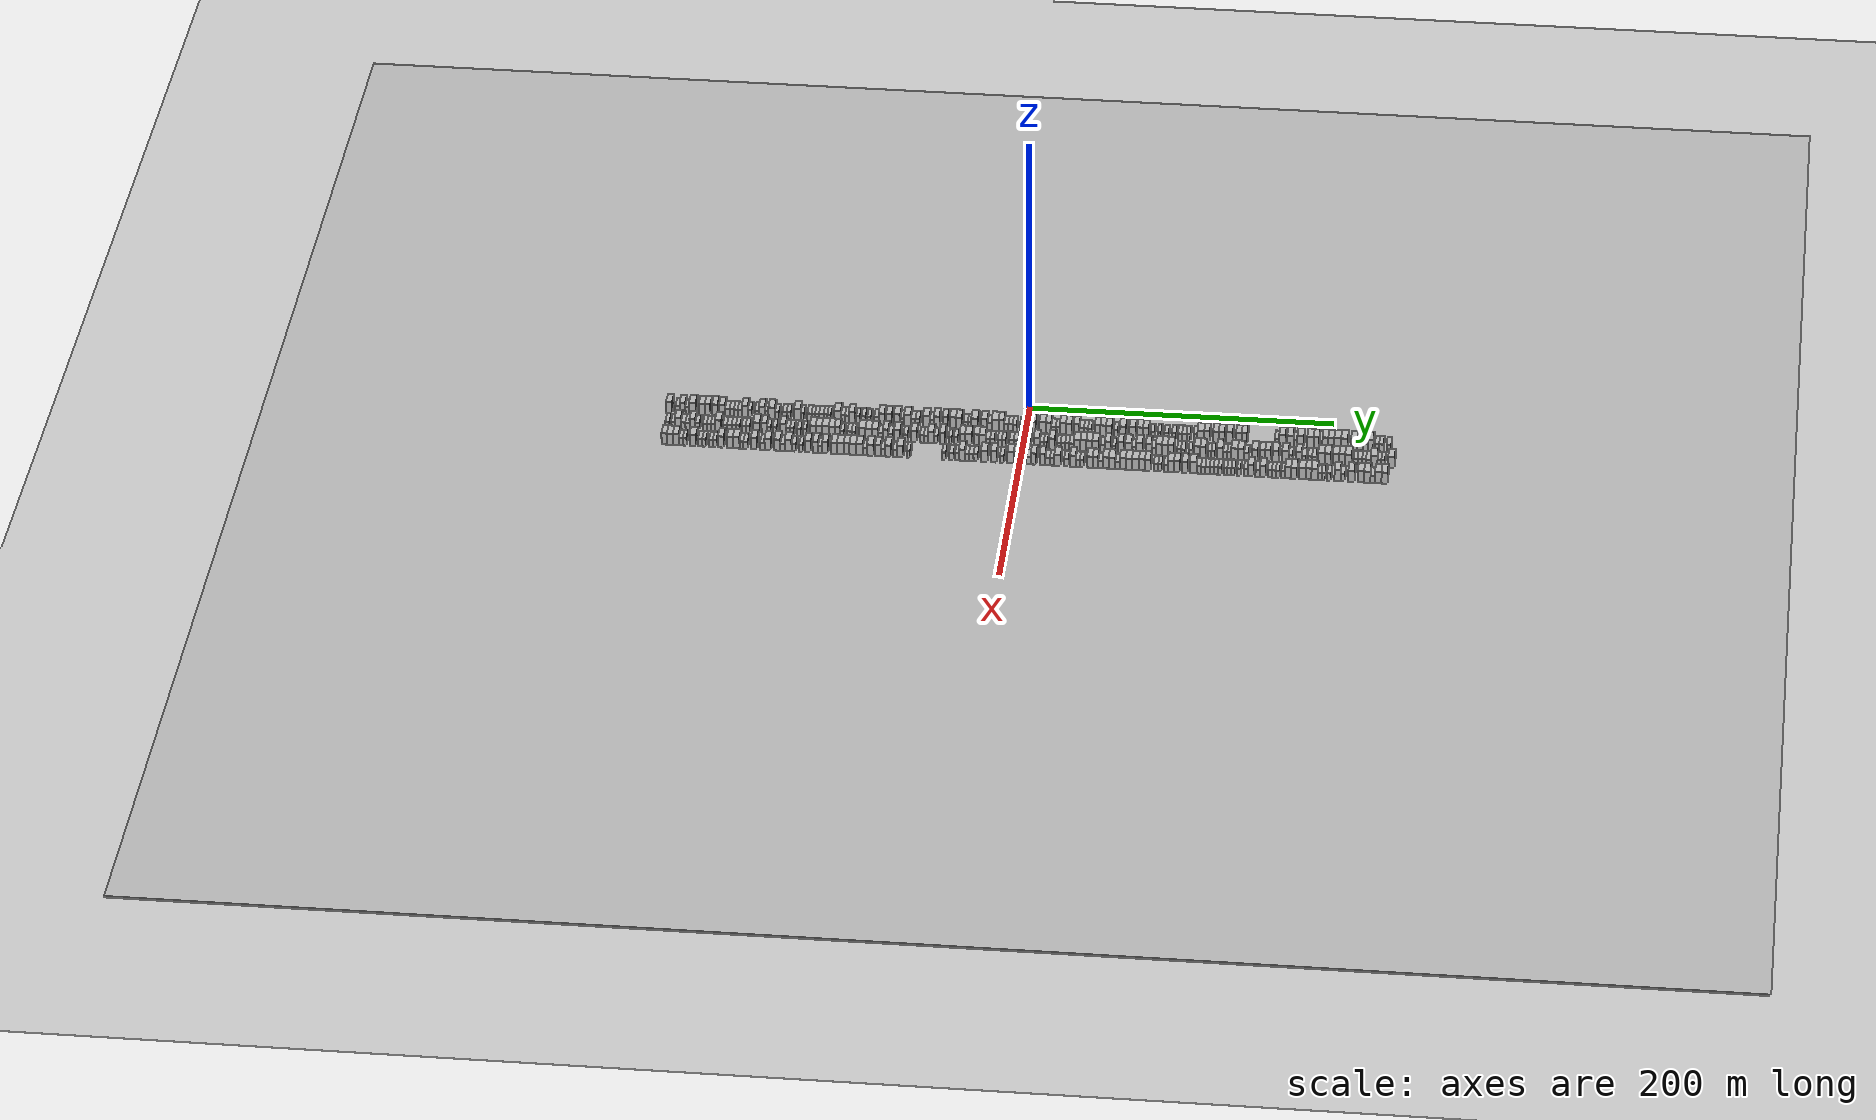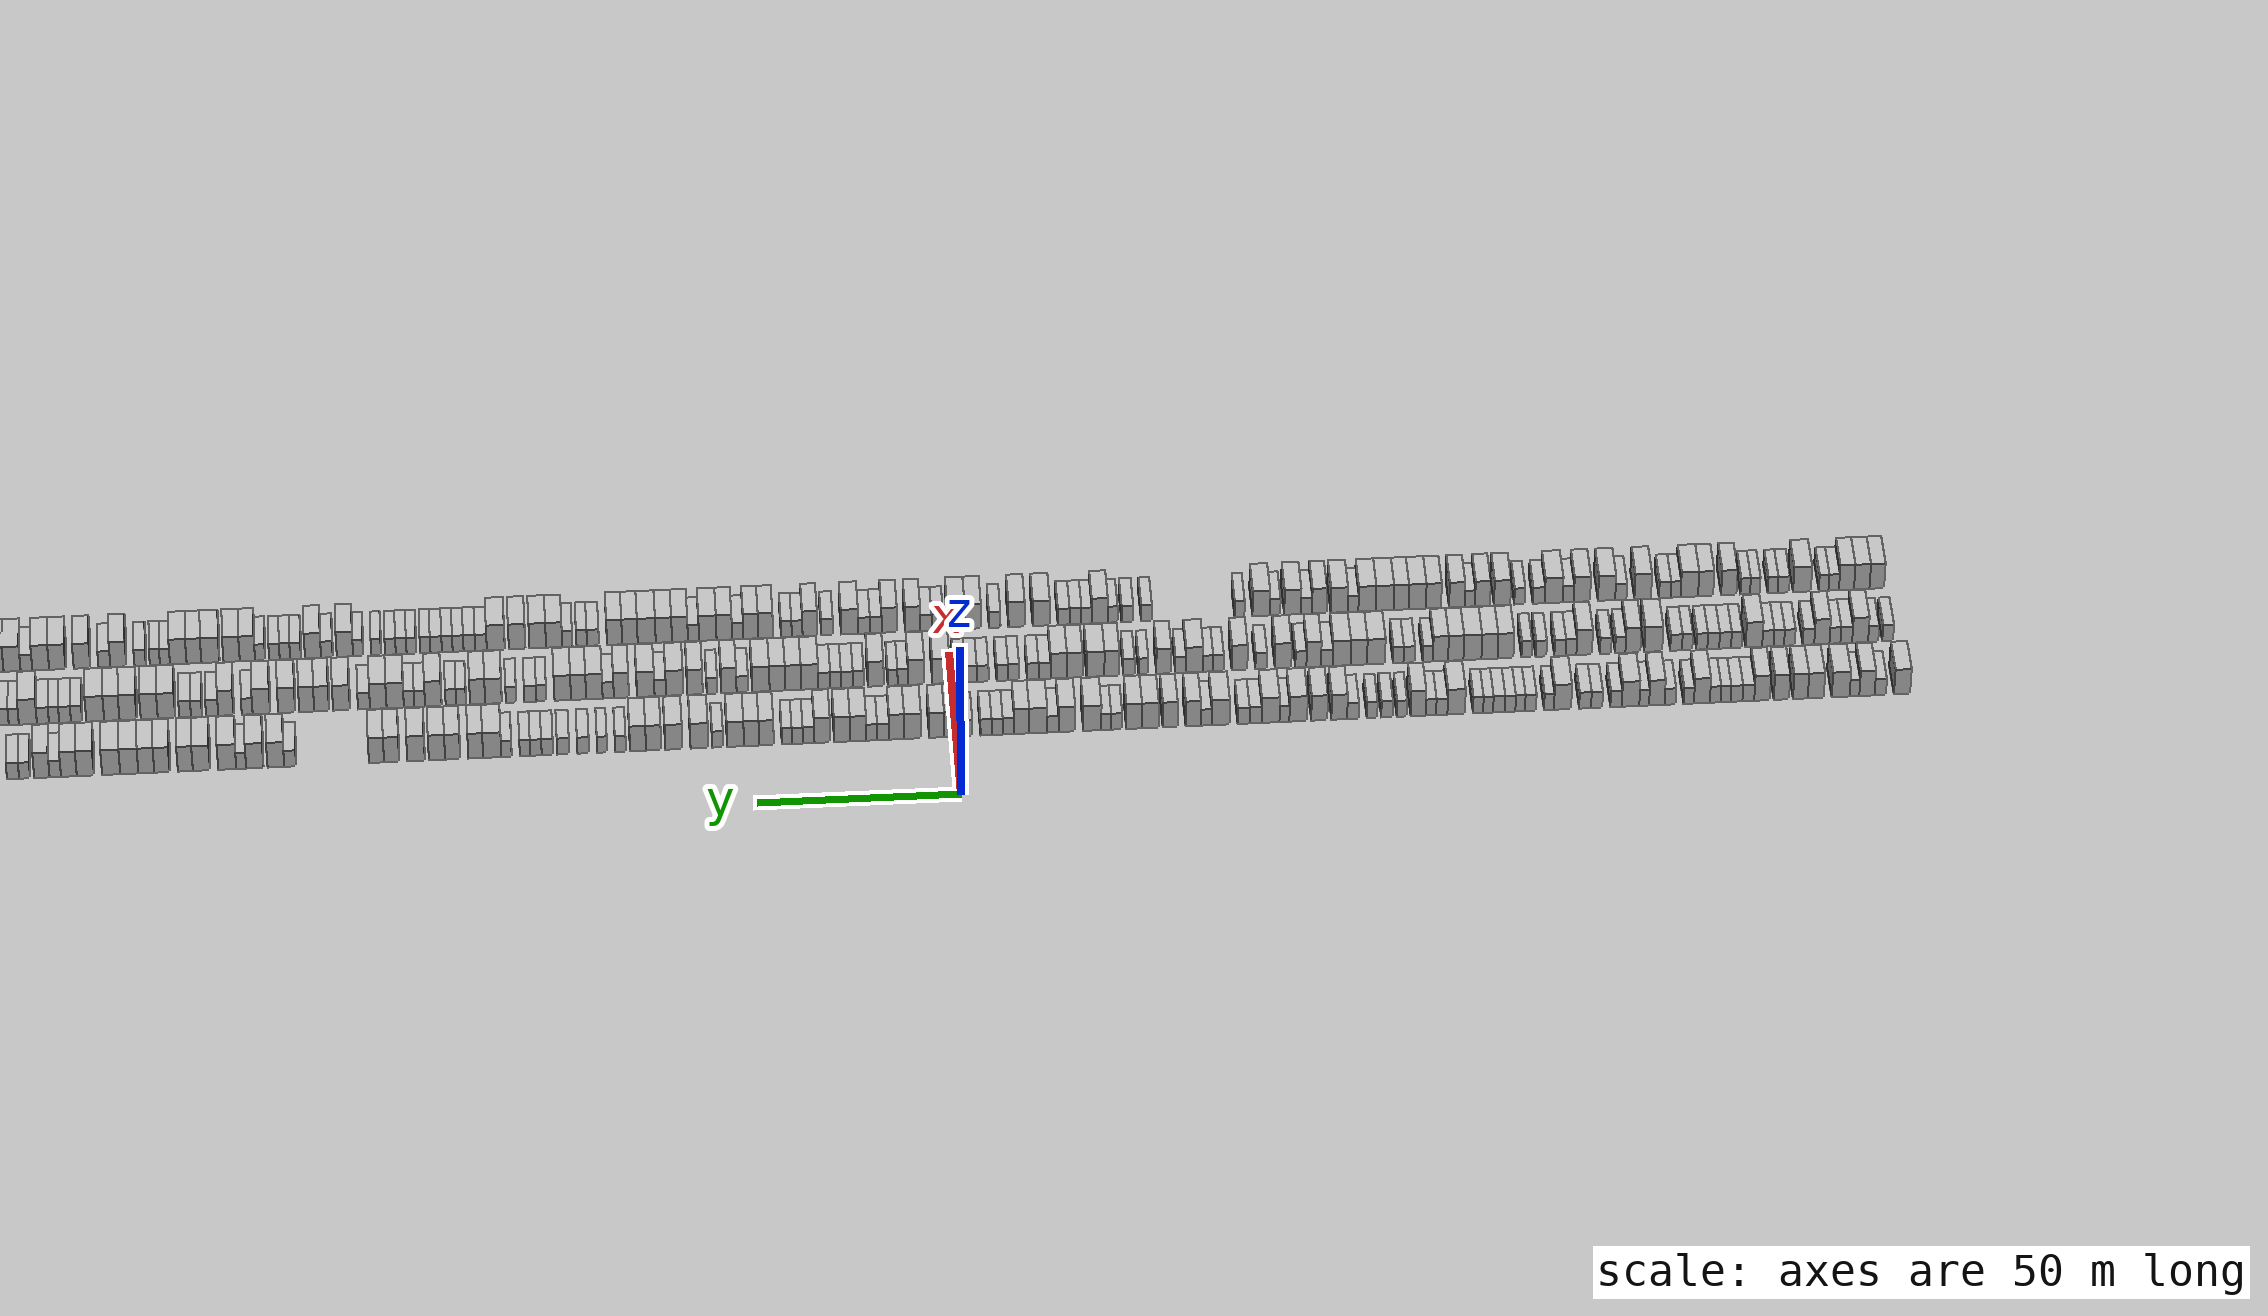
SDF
<?xml version="1.0" encoding="utf-8"?>

<sdf version="1.6">

   <world name="default">

      <gui fullscreen="0">

         <camera name="user_camera">

            <pose>-15 0 4.57585 0 0 0</pose>

            <view_controller>orbit</view_controller>

         </camera>

      </gui>

      <scene>

         <sky>

           <clouds>

             <speed>12</speed>

           </clouds>

         </sky>

         <ambient>0.4 0.4 0.4 1</ambient>

         <background>0.7 0.7 0.7 1</background>

         <shadows>1</shadows>

      </scene>

      <gravity>0 0 -9.8066</gravity>

      <magnetic_field>6e-06 2.3e-05 -4.2e-05</magnetic_field>

      <physics default="0" name="default_physics" type="ode">

         <ode>

            <solver>

               <type>quick</type>

               <iters>10</iters>

               <sor>1.0</sor>

               <use_dynamic_moi_rescaling>0</use_dynamic_moi_rescaling>

            </solver>

            <constraints>

               <cfm>0</cfm>

               <erp>0.2</erp>

               <contact_max_correcting_vel>100</contact_max_correcting_vel>

               <contact_surface_layer>0.001</contact_surface_layer>

            </constraints>

         </ode>

         <max_step_size>0.004</max_step_size>

         <real_time_factor>1</real_time_factor>

         <real_time_update_rate>250</real_time_update_rate>

      </physics>

      <light name="sun" type="directional">

         <cast_shadows>1</cast_shadows>

         <pose>0 0 10 0 0 0</pose>

         <diffuse>0.8 0.8 0.8 1</diffuse>

         <specular>0.2 0.2 0.2 1</specular>

         <attenuation>

            <range>1000</range>

            <constant>0.9</constant>

            <linear>0.01</linear>

            <quadratic>0.001</quadratic>

         </attenuation>

         <direction>-0.5 0.1 -0.9</direction>

      </light>

      <include>

         <name>ground_plane_1</name>

         <uri>model://HANNAS_ground_plane</uri>

         <pose>0 0 0  0 0 0</pose>

      </include>

      <include>

         <name>ground_plane_2</name>

         <uri>model://HANNAS_ground_plane</uri>

         <pose>100 0 0  0 0 0</pose>

      </include>

      <model name="building_1">

         <static>1</static>

         <pose frame="">25.0000 -233.9981 0 0.000000 0.000000 0.000000</pose>

         <link name="link">

            <pose frame="">0 0 4.50 0 0 0</pose>

            <collision name="collision">

               <geometry>

                  <box>

                     <size>10.0000 4.0038 9.0000</size>

                  </box>

               </geometry>

               <max_contacts>10</max_contacts>

               <surface>

                  <contact>

                     <ode/>

                  </contact>

                  <bounce/>

                  <friction>

                     <torsional>

                        <ode/>

                     </torsional>

                     <ode/>

                  </friction>

               </surface>

            </collision>

            <visual name="visual">

               <cast_shadows>0</cast_shadows>

               <geometry>

                  <box>

                     <size>10.0000 4.0038 9.0000</size>

                  </box>

               </geometry>

               <material>

                  <script>

                     <uri>model://HANNAS_wall/materials/scripts</uri>

                     <uri>model://HANNAS_wall/materials/textures</uri>

                     <name>vrc/HANNAS_wall</name>

                  </script>

               </material>

            </visual>

            <self_collide>0</self_collide>

            <enable_wind>0</enable_wind>

            <kinematic>0</kinematic>

         </link>

      </model>

      <model name="building_2">

         <static>1</static>

         <pose frame="">25.0000 -228.5838 0 0.000000 0.000000 0.000000</pose>

         <link name="link">

            <pose frame="">0 0 3.00 0 0 0</pose>

            <collision name="collision">

               <geometry>

                  <box>

                     <size>10.0000 2.8249 6.0000</size>

                  </box>

               </geometry>

               <max_contacts>10</max_contacts>

               <surface>

                  <contact>

                     <ode/>

                  </contact>

                  <bounce/>

                  <friction>

                     <torsional>

                        <ode/>

                     </torsional>

                     <ode/>

                  </friction>

               </surface>

            </collision>

            <visual name="visual">

               <cast_shadows>0</cast_shadows>

               <geometry>

                  <box>

                     <size>10.0000 2.8249 6.0000</size>

                  </box>

               </geometry>

               <material>

                  <script>

                     <uri>model://HANNAS_wall/materials/scripts</uri>

                     <uri>model://HANNAS_wall/materials/textures</uri>

                     <name>vrc/HANNAS_wall</name>

                  </script>

               </material>

            </visual>

            <self_collide>0</self_collide>

            <enable_wind>0</enable_wind>

            <kinematic>0</kinematic>

         </link>

      </model>

      <model name="building_3">

         <static>1</static>

         <pose frame="">25.0000 -225.2748 0 0.000000 0.000000 0.000000</pose>

         <link name="link">

            <pose frame="">0 0 4.50 0 0 0</pose>

            <collision name="collision">

               <geometry>

                  <box>

                     <size>10.0000 3.7931 9.0000</size>

                  </box>

               </geometry>

               <max_contacts>10</max_contacts>

               <surface>

                  <contact>

                     <ode/>

                  </contact>

                  <bounce/>

                  <friction>

                     <torsional>

                        <ode/>

                     </torsional>

                     <ode/>

                  </friction>

               </surface>

            </collision>

            <visual name="visual">

               <cast_shadows>0</cast_shadows>

               <geometry>

                  <box>

                     <size>10.0000 3.7931 9.0000</size>

                  </box>

               </geometry>

               <material>

                  <script>

                     <uri>model://HANNAS_wall/materials/scripts</uri>

                     <uri>model://HANNAS_wall/materials/textures</uri>

                     <name>vrc/HANNAS_wall</name>

                  </script>

               </material>

            </visual>

            <self_collide>0</self_collide>

            <enable_wind>0</enable_wind>

            <kinematic>0</kinematic>

         </link>

      </model>

      <model name="building_4">

         <static>1</static>

         <pose frame="">25.0000 -222.1700 0 0.000000 0.000000 0.000000</pose>

         <link name="link">

            <pose frame="">0 0 3.00 0 0 0</pose>

            <collision name="collision">

               <geometry>

                  <box>

                     <size>10.0000 2.4163 6.0000</size>

                  </box>

               </geometry>

               <max_contacts>10</max_contacts>

               <surface>

                  <contact>

                     <ode/>

                  </contact>

                  <bounce/>

                  <friction>

                     <torsional>

                        <ode/>

                     </torsional>

                     <ode/>

                  </friction>

               </surface>

            </collision>

            <visual name="visual">

               <cast_shadows>0</cast_shadows>

               <geometry>

                  <box>

                     <size>10.0000 2.4163 6.0000</size>

                  </box>

               </geometry>

               <material>

                  <script>

                     <uri>model://HANNAS_wall/materials/scripts</uri>

                     <uri>model://HANNAS_wall/materials/textures</uri>

                     <name>vrc/HANNAS_wall</name>

                  </script>

               </material>

            </visual>

            <self_collide>0</self_collide>

            <enable_wind>0</enable_wind>

            <kinematic>0</kinematic>

         </link>

      </model>

      <model name="building_5">

         <static>1</static>

         <pose frame="">25.0000 -218.7425 0 0.000000 0.000000 0.000000</pose>

         <link name="link">

            <pose frame="">0 0 4.50 0 0 0</pose>

            <collision name="collision">

               <geometry>

                  <box>

                     <size>10.0000 4.4388 9.0000</size>

                  </box>

               </geometry>

               <max_contacts>10</max_contacts>

               <surface>

                  <contact>

                     <ode/>

                  </contact>

                  <bounce/>

                  <friction>

                     <torsional>

                        <ode/>

                     </torsional>

                     <ode/>

                  </friction>

               </surface>

            </collision>

            <visual name="visual">

               <cast_shadows>0</cast_shadows>

               <geometry>

                  <box>

                     <size>10.0000 4.4388 9.0000</size>

                  </box>

               </geometry>

               <material>

                  <script>

                     <uri>model://HANNAS_wall/materials/scripts</uri>

                     <uri>model://HANNAS_wall/materials/textures</uri>

                     <name>vrc/HANNAS_wall</name>

                  </script>

               </material>

            </visual>

            <self_collide>0</self_collide>

            <enable_wind>0</enable_wind>

            <kinematic>0</kinematic>

         </link>

      </model>

      <model name="building_6">

         <static>1</static>

         <pose frame="">25.0000 -212.5421 0 0.000000 0.000000 0.000000</pose>

         <link name="link">

            <pose frame="">0 0 4.50 0 0 0</pose>

            <collision name="collision">

               <geometry>

                  <box>

                     <size>10.0000 3.9620 9.0000</size>

                  </box>

               </geometry>

               <max_contacts>10</max_contacts>

               <surface>

                  <contact>

                     <ode/>

                  </contact>

                  <bounce/>

                  <friction>

                     <torsional>

                        <ode/>

                     </torsional>

                     <ode/>

                  </friction>

               </surface>

            </collision>

            <visual name="visual">

               <cast_shadows>0</cast_shadows>

               <geometry>

                  <box>

                     <size>10.0000 3.9620 9.0000</size>

                  </box>

               </geometry>

               <material>

                  <script>

                     <uri>model://HANNAS_wall/materials/scripts</uri>

                     <uri>model://HANNAS_wall/materials/textures</uri>

                     <name>vrc/HANNAS_wall</name>

                  </script>

               </material>

            </visual>

            <self_collide>0</self_collide>

            <enable_wind>0</enable_wind>

            <kinematic>0</kinematic>

         </link>

      </model>

      <model name="building_7">

         <static>1</static>

         <pose frame="">25.0000 -208.7248 0 0.000000 0.000000 0.000000</pose>

         <link name="link">

            <pose frame="">0 0 4.50 0 0 0</pose>

            <collision name="collision">

               <geometry>

                  <box>

                     <size>10.0000 3.6725 9.0000</size>

                  </box>

               </geometry>

               <max_contacts>10</max_contacts>

               <surface>

                  <contact>

                     <ode/>

                  </contact>

                  <bounce/>

                  <friction>

                     <torsional>

                        <ode/>

                     </torsional>

                     <ode/>

                  </friction>

               </surface>

            </collision>

            <visual name="visual">

               <cast_shadows>0</cast_shadows>

               <geometry>

                  <box>

                     <size>10.0000 3.6725 9.0000</size>

                  </box>

               </geometry>

               <material>

                  <script>

                     <uri>model://HANNAS_wall/materials/scripts</uri>

                     <uri>model://HANNAS_wall/materials/textures</uri>

                     <name>vrc/HANNAS_wall</name>

                  </script>

               </material>

            </visual>

            <self_collide>0</self_collide>

            <enable_wind>0</enable_wind>

            <kinematic>0</kinematic>

         </link>

      </model>

      <model name="building_8">

         <static>1</static>

         <pose frame="">25.0000 -203.9958 0 0.000000 0.000000 0.000000</pose>

         <link name="link">

            <pose frame="">0 0 4.50 0 0 0</pose>

            <collision name="collision">

               <geometry>

                  <box>

                     <size>10.0000 3.7854 9.0000</size>

                  </box>

               </geometry>

               <max_contacts>10</max_contacts>

               <surface>

                  <contact>

                     <ode/>

                  </contact>

                  <bounce/>

                  <friction>

                     <torsional>

                        <ode/>

                     </torsional>

                     <ode/>

                  </friction>

               </surface>

            </collision>

            <visual name="visual">

               <cast_shadows>0</cast_shadows>

               <geometry>

                  <box>

                     <size>10.0000 3.7854 9.0000</size>

                  </box>

               </geometry>

               <material>

                  <script>

                     <uri>model://HANNAS_wall/materials/scripts</uri>

                     <uri>model://HANNAS_wall/materials/textures</uri>

                     <name>vrc/HANNAS_wall</name>

                  </script>

               </material>

            </visual>

            <self_collide>0</self_collide>

            <enable_wind>0</enable_wind>

            <kinematic>0</kinematic>

         </link>

      </model>

      <model name="building_9">

         <static>1</static>

         <pose frame="">25.0000 -199.1760 0 0.000000 0.000000 0.000000</pose>

         <link name="link">

            <pose frame="">0 0 4.50 0 0 0</pose>

            <collision name="collision">

               <geometry>

                  <box>

                     <size>10.0000 3.8543 9.0000</size>

                  </box>

               </geometry>

               <max_contacts>10</max_contacts>

               <surface>

                  <contact>

                     <ode/>

                  </contact>

                  <bounce/>

                  <friction>

                     <torsional>

                        <ode/>

                     </torsional>

                     <ode/>

                  </friction>

               </surface>

            </collision>

            <visual name="visual">

               <cast_shadows>0</cast_shadows>

               <geometry>

                  <box>

                     <size>10.0000 3.8543 9.0000</size>

                  </box>

               </geometry>

               <material>

                  <script>

                     <uri>model://HANNAS_wall/materials/scripts</uri>

                     <uri>model://HANNAS_wall/materials/textures</uri>

                     <name>vrc/HANNAS_wall</name>

                  </script>

               </material>

            </visual>

            <self_collide>0</self_collide>

            <enable_wind>0</enable_wind>

            <kinematic>0</kinematic>

         </link>

      </model>

      <model name="building_10">

         <static>1</static>

         <pose frame="">25.0000 -195.7851 0 0.000000 0.000000 0.000000</pose>

         <link name="link">

            <pose frame="">0 0 3.00 0 0 0</pose>

            <collision name="collision">

               <geometry>

                  <box>

                     <size>10.0000 2.9275 6.0000</size>

                  </box>

               </geometry>

               <max_contacts>10</max_contacts>

               <surface>

                  <contact>

                     <ode/>

                  </contact>

                  <bounce/>

                  <friction>

                     <torsional>

                        <ode/>

                     </torsional>

                     <ode/>

                  </friction>

               </surface>

            </collision>

            <visual name="visual">

               <cast_shadows>0</cast_shadows>

               <geometry>

                  <box>

                     <size>10.0000 2.9275 6.0000</size>

                  </box>

               </geometry>

               <material>

                  <script>

                     <uri>model://HANNAS_wall/materials/scripts</uri>

                     <uri>model://HANNAS_wall/materials/textures</uri>

                     <name>vrc/HANNAS_wall</name>

                  </script>

               </material>

            </visual>

            <self_collide>0</self_collide>

            <enable_wind>0</enable_wind>

            <kinematic>0</kinematic>

         </link>

      </model>

      <model name="building_11">

         <static>1</static>

         <pose frame="">25.0000 -192.8540 0 0.000000 0.000000 0.000000</pose>

         <link name="link">

            <pose frame="">0 0 3.00 0 0 0</pose>

            <collision name="collision">

               <geometry>

                  <box>

                     <size>10.0000 2.9347 6.0000</size>

                  </box>

               </geometry>

               <max_contacts>10</max_contacts>

               <surface>

                  <contact>

                     <ode/>

                  </contact>

                  <bounce/>

                  <friction>

                     <torsional>

                        <ode/>

                     </torsional>

                     <ode/>

                  </friction>

               </surface>

            </collision>

            <visual name="visual">

               <cast_shadows>0</cast_shadows>

               <geometry>

                  <box>

                     <size>10.0000 2.9347 6.0000</size>

                  </box>

               </geometry>

               <material>

                  <script>

                     <uri>model://HANNAS_wall/materials/scripts</uri>

                     <uri>model://HANNAS_wall/materials/textures</uri>

                     <name>vrc/HANNAS_wall</name>

                  </script>

               </material>

            </visual>

            <self_collide>0</self_collide>

            <enable_wind>0</enable_wind>

            <kinematic>0</kinematic>

         </link>

      </model>

      <model name="building_12">

         <static>1</static>

         <pose frame="">25.0000 -190.1426 0 0.000000 0.000000 0.000000</pose>

         <link name="link">

            <pose frame="">0 0 3.00 0 0 0</pose>

            <collision name="collision">

               <geometry>

                  <box>

                     <size>10.0000 2.4881 6.0000</size>

                  </box>

               </geometry>

               <max_contacts>10</max_contacts>

               <surface>

                  <contact>

                     <ode/>

                  </contact>

                  <bounce/>

                  <friction>

                     <torsional>

                        <ode/>

                     </torsional>

                     <ode/>

                  </friction>

               </surface>

            </collision>

            <visual name="visual">

               <cast_shadows>0</cast_shadows>

               <geometry>

                  <box>

                     <size>10.0000 2.4881 6.0000</size>

                  </box>

               </geometry>

               <material>

                  <script>

                     <uri>model://HANNAS_wall/materials/scripts</uri>

                     <uri>model://HANNAS_wall/materials/textures</uri>

                     <name>vrc/HANNAS_wall</name>

                  </script>

               </material>

            </visual>

            <self_collide>0</self_collide>

            <enable_wind>0</enable_wind>

            <kinematic>0</kinematic>

         </link>

      </model>

      <model name="building_13">

         <static>1</static>

         <pose frame="">25.0000 -187.5617 0 0.000000 0.000000 0.000000</pose>

         <link name="link">

            <pose frame="">0 0 3.00 0 0 0</pose>

            <collision name="collision">

               <geometry>

                  <box>

                     <size>10.0000 2.6737 6.0000</size>

                  </box>

               </geometry>

               <max_contacts>10</max_contacts>

               <surface>

                  <contact>

                     <ode/>

                  </contact>

                  <bounce/>

                  <friction>

                     <torsional>

                        <ode/>

                     </torsional>

                     <ode/>

                  </friction>

               </surface>

            </collision>

            <visual name="visual">

               <cast_shadows>0</cast_shadows>

               <geometry>

                  <box>

                     <size>10.0000 2.6737 6.0000</size>

                  </box>

               </geometry>

               <material>

                  <script>

                     <uri>model://HANNAS_wall/materials/scripts</uri>

                     <uri>model://HANNAS_wall/materials/textures</uri>

                     <name>vrc/HANNAS_wall</name>

                  </script>

               </material>

            </visual>

            <self_collide>0</self_collide>

            <enable_wind>0</enable_wind>

            <kinematic>0</kinematic>

         </link>

      </model>

      <model name="building_14">

         <static>1</static>

         <pose frame="">25.0000 -184.2528 0 0.000000 0.000000 0.000000</pose>

         <link name="link">

            <pose frame="">0 0 4.50 0 0 0</pose>

            <collision name="collision">

               <geometry>

                  <box>

                     <size>10.0000 3.9441 9.0000</size>

                  </box>

               </geometry>

               <max_contacts>10</max_contacts>

               <surface>

                  <contact>

                     <ode/>

                  </contact>

                  <bounce/>

                  <friction>

                     <torsional>

                        <ode/>

                     </torsional>

                     <ode/>

                  </friction>

               </surface>

            </collision>

            <visual name="visual">

               <cast_shadows>0</cast_shadows>

               <geometry>

                  <box>

                     <size>10.0000 3.9441 9.0000</size>

                  </box>

               </geometry>

               <material>

                  <script>

                     <uri>model://HANNAS_wall/materials/scripts</uri>

                     <uri>model://HANNAS_wall/materials/textures</uri>

                     <name>vrc/HANNAS_wall</name>

                  </script>

               </material>

            </visual>

            <self_collide>0</self_collide>

            <enable_wind>0</enable_wind>

            <kinematic>0</kinematic>

         </link>

      </model>

      <model name="building_15">

         <static>1</static>

         <pose frame="">25.0000 -180.9864 0 0.000000 0.000000 0.000000</pose>

         <link name="link">

            <pose frame="">0 0 3.00 0 0 0</pose>

            <collision name="collision">

               <geometry>

                  <box>

                     <size>10.0000 2.5888 6.0000</size>

                  </box>

               </geometry>

               <max_contacts>10</max_contacts>

               <surface>

                  <contact>

                     <ode/>

                  </contact>

                  <bounce/>

                  <friction>

                     <torsional>

                        <ode/>

                     </torsional>

                     <ode/>

                  </friction>

               </surface>

            </collision>

            <visual name="visual">

               <cast_shadows>0</cast_shadows>

               <geometry>

                  <box>

                     <size>10.0000 2.5888 6.0000</size>

                  </box>

               </geometry>

               <material>

                  <script>

                     <uri>model://HANNAS_wall/materials/scripts</uri>

                     <uri>model://HANNAS_wall/materials/textures</uri>

                     <name>vrc/HANNAS_wall</name>

                  </script>

               </material>

            </visual>

            <self_collide>0</self_collide>

            <enable_wind>0</enable_wind>

            <kinematic>0</kinematic>

         </link>

      </model>

      <model name="building_16">

         <static>1</static>

         <pose frame="">25.0000 -176.3354 0 0.000000 0.000000 0.000000</pose>

         <link name="link">

            <pose frame="">0 0 3.00 0 0 0</pose>

            <collision name="collision">

               <geometry>

                  <box>

                     <size>10.0000 2.7133 6.0000</size>

                  </box>

               </geometry>

               <max_contacts>10</max_contacts>

               <surface>

                  <contact>

                     <ode/>

                  </contact>

                  <bounce/>

                  <friction>

                     <torsional>

                        <ode/>

                     </torsional>

                     <ode/>

                  </friction>

               </surface>

            </collision>

            <visual name="visual">

               <cast_shadows>0</cast_shadows>

               <geometry>

                  <box>

                     <size>10.0000 2.7133 6.0000</size>

                  </box>

               </geometry>

               <material>

                  <script>

                     <uri>model://HANNAS_wall/materials/scripts</uri>

                     <uri>model://HANNAS_wall/materials/textures</uri>

                     <name>vrc/HANNAS_wall</name>

                  </script>

               </material>

            </visual>

            <self_collide>0</self_collide>

            <enable_wind>0</enable_wind>

            <kinematic>0</kinematic>

         </link>

      </model>

      <model name="building_17">

         <static>1</static>

         <pose frame="">25.0000 -173.0598 0 0.000000 0.000000 0.000000</pose>

         <link name="link">

            <pose frame="">0 0 4.50 0 0 0</pose>

            <collision name="collision">

               <geometry>

                  <box>

                     <size>10.0000 3.8377 9.0000</size>

                  </box>

               </geometry>

               <max_contacts>10</max_contacts>

               <surface>

                  <contact>

                     <ode/>

                  </contact>

                  <bounce/>

                  <friction>

                     <torsional>

                        <ode/>

                     </torsional>

                     <ode/>

                  </friction>

               </surface>

            </collision>

            <visual name="visual">

               <cast_shadows>0</cast_shadows>

               <geometry>

                  <box>

                     <size>10.0000 3.8377 9.0000</size>

                  </box>

               </geometry>

               <material>

                  <script>

                     <uri>model://HANNAS_wall/materials/scripts</uri>

                     <uri>model://HANNAS_wall/materials/textures</uri>

                     <name>vrc/HANNAS_wall</name>

                  </script>

               </material>

            </visual>

            <self_collide>0</self_collide>

            <enable_wind>0</enable_wind>

            <kinematic>0</kinematic>

         </link>

      </model>

      <model name="building_18">

         <static>1</static>

         <pose frame="">25.0000 -169.9268 0 0.000000 0.000000 0.000000</pose>

         <link name="link">

            <pose frame="">0 0 3.00 0 0 0</pose>

            <collision name="collision">

               <geometry>

                  <box>

                     <size>10.0000 2.4284 6.0000</size>

                  </box>

               </geometry>

               <max_contacts>10</max_contacts>

               <surface>

                  <contact>

                     <ode/>

                  </contact>

                  <bounce/>

                  <friction>

                     <torsional>

                        <ode/>

                     </torsional>

                     <ode/>

                  </friction>

               </surface>

            </collision>

            <visual name="visual">

               <cast_shadows>0</cast_shadows>

               <geometry>

                  <box>

                     <size>10.0000 2.4284 6.0000</size>

                  </box>

               </geometry>

               <material>

                  <script>

                     <uri>model://HANNAS_wall/materials/scripts</uri>

                     <uri>model://HANNAS_wall/materials/textures</uri>

                     <name>vrc/HANNAS_wall</name>

                  </script>

               </material>

            </visual>

            <self_collide>0</self_collide>

            <enable_wind>0</enable_wind>

            <kinematic>0</kinematic>

         </link>

      </model>

      <model name="building_19">

         <static>1</static>

         <pose frame="">25.0000 -166.5386 0 0.000000 0.000000 0.000000</pose>

         <link name="link">

            <pose frame="">0 0 4.50 0 0 0</pose>

            <collision name="collision">

               <geometry>

                  <box>

                     <size>10.0000 4.3480 9.0000</size>

                  </box>

               </geometry>

               <max_contacts>10</max_contacts>

               <surface>

                  <contact>

                     <ode/>

                  </contact>

                  <bounce/>

                  <friction>

                     <torsional>

                        <ode/>

                     </torsional>

                     <ode/>

                  </friction>

               </surface>

            </collision>

            <visual name="visual">

               <cast_shadows>0</cast_shadows>

               <geometry>

                  <box>

                     <size>10.0000 4.3480 9.0000</size>

                  </box>

               </geometry>

               <material>

                  <script>

                     <uri>model://HANNAS_wall/materials/scripts</uri>

                     <uri>model://HANNAS_wall/materials/textures</uri>

                     <name>vrc/HANNAS_wall</name>

                  </script>

               </material>

            </visual>

            <self_collide>0</self_collide>

            <enable_wind>0</enable_wind>

            <kinematic>0</kinematic>

         </link>

      </model>

      <model name="building_20">

         <static>1</static>

         <pose frame="">25.0000 -162.9481 0 0.000000 0.000000 0.000000</pose>

         <link name="link">

            <pose frame="">0 0 3.00 0 0 0</pose>

            <collision name="collision">

               <geometry>

                  <box>

                     <size>10.0000 2.8331 6.0000</size>

                  </box>

               </geometry>

               <max_contacts>10</max_contacts>

               <surface>

                  <contact>

                     <ode/>

                  </contact>

                  <bounce/>

                  <friction>

                     <torsional>

                        <ode/>

                     </torsional>

                     <ode/>

                  </friction>

               </surface>

            </collision>

            <visual name="visual">

               <cast_shadows>0</cast_shadows>

               <geometry>

                  <box>

                     <size>10.0000 2.8331 6.0000</size>

                  </box>

               </geometry>

               <material>

                  <script>

                     <uri>model://HANNAS_wall/materials/scripts</uri>

                     <uri>model://HANNAS_wall/materials/textures</uri>

                     <name>vrc/HANNAS_wall</name>

                  </script>

               </material>

            </visual>

            <self_collide>0</self_collide>

            <enable_wind>0</enable_wind>

            <kinematic>0</kinematic>

         </link>

      </model>

      <model name="building_21">

         <static>1</static>

         <pose frame="">25.0000 -158.1404 0 0.000000 0.000000 0.000000</pose>

         <link name="link">

            <pose frame="">0 0 3.00 0 0 0</pose>

            <collision name="collision">

               <geometry>

                  <box>

                     <size>10.0000 2.7823 6.0000</size>

                  </box>

               </geometry>

               <max_contacts>10</max_contacts>

               <surface>

                  <contact>

                     <ode/>

                  </contact>

                  <bounce/>

                  <friction>

                     <torsional>

                        <ode/>

                     </torsional>

                     <ode/>

                  </friction>

               </surface>

            </collision>

            <visual name="visual">

               <cast_shadows>0</cast_shadows>

               <geometry>

                  <box>

                     <size>10.0000 2.7823 6.0000</size>

                  </box>

               </geometry>

               <material>

                  <script>

                     <uri>model://HANNAS_wall/materials/scripts</uri>

                     <uri>model://HANNAS_wall/materials/textures</uri>

                     <name>vrc/HANNAS_wall</name>

                  </script>

               </material>

            </visual>

            <self_collide>0</self_collide>

            <enable_wind>0</enable_wind>

            <kinematic>0</kinematic>

         </link>

      </model>

      <model name="building_22">

         <static>1</static>

         <pose frame="">25.0000 -155.2684 0 0.000000 0.000000 0.000000</pose>

         <link name="link">

            <pose frame="">0 0 3.00 0 0 0</pose>

            <collision name="collision">

               <geometry>

                  <box>

                     <size>10.0000 2.9617 6.0000</size>

                  </box>

               </geometry>

               <max_contacts>10</max_contacts>

               <surface>

                  <contact>

                     <ode/>

                  </contact>

                  <bounce/>

                  <friction>

                     <torsional>

                        <ode/>

                     </torsional>

                     <ode/>

                  </friction>

               </surface>

            </collision>

            <visual name="visual">

               <cast_shadows>0</cast_shadows>

               <geometry>

                  <box>

                     <size>10.0000 2.9617 6.0000</size>

                  </box>

               </geometry>

               <material>

                  <script>

                     <uri>model://HANNAS_wall/materials/scripts</uri>

                     <uri>model://HANNAS_wall/materials/textures</uri>

                     <name>vrc/HANNAS_wall</name>

                  </script>

               </material>

            </visual>

            <self_collide>0</self_collide>

            <enable_wind>0</enable_wind>

            <kinematic>0</kinematic>

         </link>

      </model>

      <model name="building_23">

         <static>1</static>

         <pose frame="">25.0000 -149.6617 0 0.000000 0.000000 0.000000</pose>

         <link name="link">

            <pose frame="">0 0 4.50 0 0 0</pose>

            <collision name="collision">

               <geometry>

                  <box>

                     <size>10.0000 4.2517 9.0000</size>

                  </box>

               </geometry>

               <max_contacts>10</max_contacts>

               <surface>

                  <contact>

                     <ode/>

                  </contact>

                  <bounce/>

                  <friction>

                     <torsional>

                        <ode/>

                     </torsional>

                     <ode/>

                  </friction>

               </surface>

            </collision>

            <visual name="visual">

               <cast_shadows>0</cast_shadows>

               <geometry>

                  <box>

                     <size>10.0000 4.2517 9.0000</size>

                  </box>

               </geometry>

               <material>

                  <script>

                     <uri>model://HANNAS_wall/materials/scripts</uri>

                     <uri>model://HANNAS_wall/materials/textures</uri>

                     <name>vrc/HANNAS_wall</name>

                  </script>

               </material>

            </visual>

            <self_collide>0</self_collide>

            <enable_wind>0</enable_wind>

            <kinematic>0</kinematic>

         </link>

      </model>

      <model name="building_24">

         <static>1</static>

         <pose frame="">25.0000 -146.3111 0 0.000000 0.000000 0.000000</pose>

         <link name="link">

            <pose frame="">0 0 3.00 0 0 0</pose>

            <collision name="collision">

               <geometry>

                  <box>

                     <size>10.0000 2.4495 6.0000</size>

                  </box>

               </geometry>

               <max_contacts>10</max_contacts>

               <surface>

                  <contact>

                     <ode/>

                  </contact>

                  <bounce/>

                  <friction>

                     <torsional>

                        <ode/>

                     </torsional>

                     <ode/>

                  </friction>

               </surface>

            </collision>

            <visual name="visual">

               <cast_shadows>0</cast_shadows>

               <geometry>

                  <box>

                     <size>10.0000 2.4495 6.0000</size>

                  </box>

               </geometry>

               <material>

                  <script>

                     <uri>model://HANNAS_wall/materials/scripts</uri>

                     <uri>model://HANNAS_wall/materials/textures</uri>

                     <name>vrc/HANNAS_wall</name>

                  </script>

               </material>

            </visual>

            <self_collide>0</self_collide>

            <enable_wind>0</enable_wind>

            <kinematic>0</kinematic>

         </link>

      </model>

      <model name="building_25">

         <static>1</static>

         <pose frame="">25.0000 -141.7247 0 0.000000 0.000000 0.000000</pose>

         <link name="link">

            <pose frame="">0 0 3.00 0 0 0</pose>

            <collision name="collision">

               <geometry>

                  <box>

                     <size>10.0000 2.7232 6.0000</size>

                  </box>

               </geometry>

               <max_contacts>10</max_contacts>

               <surface>

                  <contact>

                     <ode/>

                  </contact>

                  <bounce/>

                  <friction>

                     <torsional>

                        <ode/>

                     </torsional>

                     <ode/>

                  </friction>

               </surface>

            </collision>

            <visual name="visual">

               <cast_shadows>0</cast_shadows>

               <geometry>

                  <box>

                     <size>10.0000 2.7232 6.0000</size>

                  </box>

               </geometry>

               <material>

                  <script>

                     <uri>model://HANNAS_wall/materials/scripts</uri>

                     <uri>model://HANNAS_wall/materials/textures</uri>

                     <name>vrc/HANNAS_wall</name>

                  </script>

               </material>

            </visual>

            <self_collide>0</self_collide>

            <enable_wind>0</enable_wind>

            <kinematic>0</kinematic>

         </link>

      </model>

      <model name="building_26">

         <static>1</static>

         <pose frame="">25.0000 -139.1629 0 0.000000 0.000000 0.000000</pose>

         <link name="link">

            <pose frame="">0 0 3.00 0 0 0</pose>

            <collision name="collision">

               <geometry>

                  <box>

                     <size>10.0000 2.4004 6.0000</size>

                  </box>

               </geometry>

               <max_contacts>10</max_contacts>

               <surface>

                  <contact>

                     <ode/>

                  </contact>

                  <bounce/>

                  <friction>

                     <torsional>

                        <ode/>

                     </torsional>

                     <ode/>

                  </friction>

               </surface>

            </collision>

            <visual name="visual">

               <cast_shadows>0</cast_shadows>

               <geometry>

                  <box>

                     <size>10.0000 2.4004 6.0000</size>

                  </box>

               </geometry>

               <material>

                  <script>

                     <uri>model://HANNAS_wall/materials/scripts</uri>

                     <uri>model://HANNAS_wall/materials/textures</uri>

                     <name>vrc/HANNAS_wall</name>

                  </script>

               </material>

            </visual>

            <self_collide>0</self_collide>

            <enable_wind>0</enable_wind>

            <kinematic>0</kinematic>

         </link>

      </model>

      <model name="building_27">

         <static>1</static>

         <pose frame="">25.0000 -136.6651 0 0.000000 0.000000 0.000000</pose>

         <link name="link">

            <pose frame="">0 0 3.00 0 0 0</pose>

            <collision name="collision">

               <geometry>

                  <box>

                     <size>10.0000 2.5952 6.0000</size>

                  </box>

               </geometry>

               <max_contacts>10</max_contacts>

               <surface>

                  <contact>

                     <ode/>

                  </contact>

                  <bounce/>

                  <friction>

                     <torsional>

                        <ode/>

                     </torsional>

                     <ode/>

                  </friction>

               </surface>

            </collision>

            <visual name="visual">

               <cast_shadows>0</cast_shadows>

               <geometry>

                  <box>

                     <size>10.0000 2.5952 6.0000</size>

                  </box>

               </geometry>

               <material>

                  <script>

                     <uri>model://HANNAS_wall/materials/scripts</uri>

                     <uri>model://HANNAS_wall/materials/textures</uri>

                     <name>vrc/HANNAS_wall</name>

                  </script>

               </material>

            </visual>

            <self_collide>0</self_collide>

            <enable_wind>0</enable_wind>

            <kinematic>0</kinematic>

         </link>

      </model>

      <model name="building_28">

         <static>1</static>

         <pose frame="">25.0000 -133.9143 0 0.000000 0.000000 0.000000</pose>

         <link name="link">

            <pose frame="">0 0 3.00 0 0 0</pose>

            <collision name="collision">

               <geometry>

                  <box>

                     <size>10.0000 2.9065 6.0000</size>

                  </box>

               </geometry>

               <max_contacts>10</max_contacts>

               <surface>

                  <contact>

                     <ode/>

                  </contact>

                  <bounce/>

                  <friction>

                     <torsional>

                        <ode/>

                     </torsional>

                     <ode/>

                  </friction>

               </surface>

            </collision>

            <visual name="visual">

               <cast_shadows>0</cast_shadows>

               <geometry>

                  <box>

                     <size>10.0000 2.9065 6.0000</size>

                  </box>

               </geometry>

               <material>

                  <script>

                     <uri>model://HANNAS_wall/materials/scripts</uri>

                     <uri>model://HANNAS_wall/materials/textures</uri>

                     <name>vrc/HANNAS_wall</name>

                  </script>

               </material>

            </visual>

            <self_collide>0</self_collide>

            <enable_wind>0</enable_wind>

            <kinematic>0</kinematic>

         </link>

      </model>

      <model name="building_29">

         <static>1</static>

         <pose frame="">25.0000 -131.2215 0 0.000000 0.000000 0.000000</pose>

         <link name="link">

            <pose frame="">0 0 3.00 0 0 0</pose>

            <collision name="collision">

               <geometry>

                  <box>

                     <size>10.0000 2.4790 6.0000</size>

                  </box>

               </geometry>

               <max_contacts>10</max_contacts>

               <surface>

                  <contact>

                     <ode/>

                  </contact>

                  <bounce/>

                  <friction>

                     <torsional>

                        <ode/>

                     </torsional>

                     <ode/>

                  </friction>

               </surface>

            </collision>

            <visual name="visual">

               <cast_shadows>0</cast_shadows>

               <geometry>

                  <box>

                     <size>10.0000 2.4790 6.0000</size>

                  </box>

               </geometry>

               <material>

                  <script>

                     <uri>model://HANNAS_wall/materials/scripts</uri>

                     <uri>model://HANNAS_wall/materials/textures</uri>

                     <name>vrc/HANNAS_wall</name>

                  </script>

               </material>

            </visual>

            <self_collide>0</self_collide>

            <enable_wind>0</enable_wind>

            <kinematic>0</kinematic>

         </link>

      </model>

      <model name="building_30">

         <static>1</static>

         <pose frame="">25.0000 -128.7244 0 0.000000 0.000000 0.000000</pose>

         <link name="link">

            <pose frame="">0 0 3.00 0 0 0</pose>

            <collision name="collision">

               <geometry>

                  <box>

                     <size>10.0000 2.5151 6.0000</size>

                  </box>

               </geometry>

               <max_contacts>10</max_contacts>

               <surface>

                  <contact>

                     <ode/>

                  </contact>

                  <bounce/>

                  <friction>

                     <torsional>

                        <ode/>

                     </torsional>

                     <ode/>

                  </friction>

               </surface>

            </collision>

            <visual name="visual">

               <cast_shadows>0</cast_shadows>

               <geometry>

                  <box>

                     <size>10.0000 2.5151 6.0000</size>

                  </box>

               </geometry>

               <material>

                  <script>

                     <uri>model://HANNAS_wall/materials/scripts</uri>

                     <uri>model://HANNAS_wall/materials/textures</uri>

                     <name>vrc/HANNAS_wall</name>

                  </script>

               </material>

            </visual>

            <self_collide>0</self_collide>

            <enable_wind>0</enable_wind>

            <kinematic>0</kinematic>

         </link>

      </model>

      <model name="building_31">

         <static>1</static>

         <pose frame="">25.0000 -123.2932 0 0.000000 0.000000 0.000000</pose>

         <link name="link">

            <pose frame="">0 0 4.50 0 0 0</pose>

            <collision name="collision">

               <geometry>

                  <box>

                     <size>10.0000 4.3473 9.0000</size>

                  </box>

               </geometry>

               <max_contacts>10</max_contacts>

               <surface>

                  <contact>

                     <ode/>

                  </contact>

                  <bounce/>

                  <friction>

                     <torsional>

                        <ode/>

                     </torsional>

                     <ode/>

                  </friction>

               </surface>

            </collision>

            <visual name="visual">

               <cast_shadows>0</cast_shadows>

               <geometry>

                  <box>

                     <size>10.0000 4.3473 9.0000</size>

                  </box>

               </geometry>

               <material>

                  <script>

                     <uri>model://HANNAS_wall/materials/scripts</uri>

                     <uri>model://HANNAS_wall/materials/textures</uri>

                     <name>vrc/HANNAS_wall</name>

                  </script>

               </material>

            </visual>

            <self_collide>0</self_collide>

            <enable_wind>0</enable_wind>

            <kinematic>0</kinematic>

         </link>

      </model>

      <model name="building_32">

         <static>1</static>

         <pose frame="">25.0000 -119.7225 0 0.000000 0.000000 0.000000</pose>

         <link name="link">

            <pose frame="">0 0 3.00 0 0 0</pose>

            <collision name="collision">

               <geometry>

                  <box>

                     <size>10.0000 2.7942 6.0000</size>

                  </box>

               </geometry>

               <max_contacts>10</max_contacts>

               <surface>

                  <contact>

                     <ode/>

                  </contact>

                  <bounce/>

                  <friction>

                     <torsional>

                        <ode/>

                     </torsional>

                     <ode/>

                  </friction>

               </surface>

            </collision>

            <visual name="visual">

               <cast_shadows>0</cast_shadows>

               <geometry>

                  <box>

                     <size>10.0000 2.7942 6.0000</size>

                  </box>

               </geometry>

               <material>

                  <script>

                     <uri>model://HANNAS_wall/materials/scripts</uri>

                     <uri>model://HANNAS_wall/materials/textures</uri>

                     <name>vrc/HANNAS_wall</name>

                  </script>

               </material>

            </visual>

            <self_collide>0</self_collide>

            <enable_wind>0</enable_wind>

            <kinematic>0</kinematic>

         </link>

      </model>

      <model name="building_33">

         <static>1</static>

         <pose frame="">25.0000 -117.0297 0 0.000000 0.000000 0.000000</pose>

         <link name="link">

            <pose frame="">0 0 3.00 0 0 0</pose>

            <collision name="collision">

               <geometry>

                  <box>

                     <size>10.0000 2.5913 6.0000</size>

                  </box>

               </geometry>

               <max_contacts>10</max_contacts>

               <surface>

                  <contact>

                     <ode/>

                  </contact>

                  <bounce/>

                  <friction>

                     <torsional>

                        <ode/>

                     </torsional>

                     <ode/>

                  </friction>

               </surface>

            </collision>

            <visual name="visual">

               <cast_shadows>0</cast_shadows>

               <geometry>

                  <box>

                     <size>10.0000 2.5913 6.0000</size>

                  </box>

               </geometry>

               <material>

                  <script>

                     <uri>model://HANNAS_wall/materials/scripts</uri>

                     <uri>model://HANNAS_wall/materials/textures</uri>

                     <name>vrc/HANNAS_wall</name>

                  </script>

               </material>

            </visual>

            <self_collide>0</self_collide>

            <enable_wind>0</enable_wind>

            <kinematic>0</kinematic>

         </link>

      </model>

      <model name="building_34">

         <static>1</static>

         <pose frame="">25.0000 -113.8759 0 0.000000 0.000000 0.000000</pose>

         <link name="link">

            <pose frame="">0 0 4.50 0 0 0</pose>

            <collision name="collision">

               <geometry>

                  <box>

                     <size>10.0000 3.7162 9.0000</size>

                  </box>

               </geometry>

               <max_contacts>10</max_contacts>

               <surface>

                  <contact>

                     <ode/>

                  </contact>

                  <bounce/>

                  <friction>

                     <torsional>

                        <ode/>

                     </torsional>

                     <ode/>

                  </friction>

               </surface>

            </collision>

            <visual name="visual">

               <cast_shadows>0</cast_shadows>

               <geometry>

                  <box>

                     <size>10.0000 3.7162 9.0000</size>

                  </box>

               </geometry>

               <material>

                  <script>

                     <uri>model://HANNAS_wall/materials/scripts</uri>

                     <uri>model://HANNAS_wall/materials/textures</uri>

                     <name>vrc/HANNAS_wall</name>

                  </script>

               </material>

            </visual>

            <self_collide>0</self_collide>

            <enable_wind>0</enable_wind>

            <kinematic>0</kinematic>

         </link>

      </model>

      <model name="building_35">

         <static>1</static>

         <pose frame="">25.0000 -109.7910 0 0.000000 0.000000 0.000000</pose>

         <link name="link">

            <pose frame="">0 0 3.00 0 0 0</pose>

            <collision name="collision">

               <geometry>

                  <box>

                     <size>10.0000 2.4537 6.0000</size>

                  </box>

               </geometry>

               <max_contacts>10</max_contacts>

               <surface>

                  <contact>

                     <ode/>

                  </contact>

                  <bounce/>

                  <friction>

                     <torsional>

                        <ode/>

                     </torsional>

                     <ode/>

                  </friction>

               </surface>

            </collision>

            <visual name="visual">

               <cast_shadows>0</cast_shadows>

               <geometry>

                  <box>

                     <size>10.0000 2.4537 6.0000</size>

                  </box>

               </geometry>

               <material>

                  <script>

                     <uri>model://HANNAS_wall/materials/scripts</uri>

                     <uri>model://HANNAS_wall/materials/textures</uri>

                     <name>vrc/HANNAS_wall</name>

                  </script>

               </material>

            </visual>

            <self_collide>0</self_collide>

            <enable_wind>0</enable_wind>

            <kinematic>0</kinematic>

         </link>

      </model>

      <model name="building_36">

         <static>1</static>

         <pose frame="">25.0000 -106.1518 0 0.000000 0.000000 0.000000</pose>

         <link name="link">

            <pose frame="">0 0 3.00 0 0 0</pose>

            <collision name="collision">

               <geometry>

                  <box>

                     <size>10.0000 2.8247 6.0000</size>

                  </box>

               </geometry>

               <max_contacts>10</max_contacts>

               <surface>

                  <contact>

                     <ode/>

                  </contact>

                  <bounce/>

                  <friction>

                     <torsional>

                        <ode/>

                     </torsional>

                     <ode/>

                  </friction>

               </surface>

            </collision>

            <visual name="visual">

               <cast_shadows>0</cast_shadows>

               <geometry>

                  <box>

                     <size>10.0000 2.8247 6.0000</size>

                  </box>

               </geometry>

               <material>

                  <script>

                     <uri>model://HANNAS_wall/materials/scripts</uri>

                     <uri>model://HANNAS_wall/materials/textures</uri>

                     <name>vrc/HANNAS_wall</name>

                  </script>

               </material>

            </visual>

            <self_collide>0</self_collide>

            <enable_wind>0</enable_wind>

            <kinematic>0</kinematic>

         </link>

      </model>

      <model name="building_37">

         <static>1</static>

         <pose frame="">25.0000 -102.4365 0 0.000000 0.000000 0.000000</pose>

         <link name="link">

            <pose frame="">0 0 3.00 0 0 0</pose>

            <collision name="collision">

               <geometry>

                  <box>

                     <size>10.0000 2.6058 6.0000</size>

                  </box>

               </geometry>

               <max_contacts>10</max_contacts>

               <surface>

                  <contact>

                     <ode/>

                  </contact>

                  <bounce/>

                  <friction>

                     <torsional>

                        <ode/>

                     </torsional>

                     <ode/>

                  </friction>

               </surface>

            </collision>

            <visual name="visual">

               <cast_shadows>0</cast_shadows>

               <geometry>

                  <box>

                     <size>10.0000 2.6058 6.0000</size>

                  </box>

               </geometry>

               <material>

                  <script>

                     <uri>model://HANNAS_wall/materials/scripts</uri>

                     <uri>model://HANNAS_wall/materials/textures</uri>

                     <name>vrc/HANNAS_wall</name>

                  </script>

               </material>

            </visual>

            <self_collide>0</self_collide>

            <enable_wind>0</enable_wind>

            <kinematic>0</kinematic>

         </link>

      </model>

      <model name="building_38">

         <static>1</static>

         <pose frame="">25.0000 -97.7181 0 0.000000 0.000000 0.000000</pose>

         <link name="link">

            <pose frame="">0 0 3.00 0 0 0</pose>

            <collision name="collision">

               <geometry>

                  <box>

                     <size>10.0000 2.8311 6.0000</size>

                  </box>

               </geometry>

               <max_contacts>10</max_contacts>

               <surface>

                  <contact>

                     <ode/>

                  </contact>

                  <bounce/>

                  <friction>

                     <torsional>

                        <ode/>

                     </torsional>

                     <ode/>

                  </friction>

               </surface>

            </collision>

            <visual name="visual">

               <cast_shadows>0</cast_shadows>

               <geometry>

                  <box>

                     <size>10.0000 2.8311 6.0000</size>

                  </box>

               </geometry>

               <material>

                  <script>

                     <uri>model://HANNAS_wall/materials/scripts</uri>

                     <uri>model://HANNAS_wall/materials/textures</uri>

                     <name>vrc/HANNAS_wall</name>

                  </script>

               </material>

            </visual>

            <self_collide>0</self_collide>

            <enable_wind>0</enable_wind>

            <kinematic>0</kinematic>

         </link>

      </model>

      <model name="building_39">

         <static>1</static>

         <pose frame="">25.0000 -94.3414 0 0.000000 0.000000 0.000000</pose>

         <link name="link">

            <pose frame="">0 0 4.50 0 0 0</pose>

            <collision name="collision">

               <geometry>

                  <box>

                     <size>10.0000 3.9223 9.0000</size>

                  </box>

               </geometry>

               <max_contacts>10</max_contacts>

               <surface>

                  <contact>

                     <ode/>

                  </contact>

                  <bounce/>

                  <friction>

                     <torsional>

                        <ode/>

                     </torsional>

                     <ode/>

                  </friction>

               </surface>

            </collision>

            <visual name="visual">

               <cast_shadows>0</cast_shadows>

               <geometry>

                  <box>

                     <size>10.0000 3.9223 9.0000</size>

                  </box>

               </geometry>

               <material>

                  <script>

                     <uri>model://HANNAS_wall/materials/scripts</uri>

                     <uri>model://HANNAS_wall/materials/textures</uri>

                     <name>vrc/HANNAS_wall</name>

                  </script>

               </material>

            </visual>

            <self_collide>0</self_collide>

            <enable_wind>0</enable_wind>

            <kinematic>0</kinematic>

         </link>

      </model>

      <model name="building_40">

         <static>1</static>

         <pose frame="">25.0000 -89.3927 0 0.000000 0.000000 0.000000</pose>

         <link name="link">

            <pose frame="">0 0 4.50 0 0 0</pose>

            <collision name="collision">

               <geometry>

                  <box>

                     <size>10.0000 3.9752 9.0000</size>

                  </box>

               </geometry>

               <max_contacts>10</max_contacts>

               <surface>

                  <contact>

                     <ode/>

                  </contact>

                  <bounce/>

                  <friction>

                     <torsional>

                        <ode/>

                     </torsional>

                     <ode/>

                  </friction>

               </surface>

            </collision>

            <visual name="visual">

               <cast_shadows>0</cast_shadows>

               <geometry>

                  <box>

                     <size>10.0000 3.9752 9.0000</size>

                  </box>

               </geometry>

               <material>

                  <script>

                     <uri>model://HANNAS_wall/materials/scripts</uri>

                     <uri>model://HANNAS_wall/materials/textures</uri>

                     <name>vrc/HANNAS_wall</name>

                  </script>

               </material>

            </visual>

            <self_collide>0</self_collide>

            <enable_wind>0</enable_wind>

            <kinematic>0</kinematic>

         </link>

      </model>

      <model name="building_41">

         <static>1</static>

         <pose frame="">25.0000 -84.1978 0 0.000000 0.000000 0.000000</pose>

         <link name="link">

            <pose frame="">0 0 4.50 0 0 0</pose>

            <collision name="collision">

               <geometry>

                  <box>

                     <size>10.0000 4.4145 9.0000</size>

                  </box>

               </geometry>

               <max_contacts>10</max_contacts>

               <surface>

                  <contact>

                     <ode/>

                  </contact>

                  <bounce/>

                  <friction>

                     <torsional>

                        <ode/>

                     </torsional>

                     <ode/>

                  </friction>

               </surface>

            </collision>

            <visual name="visual">

               <cast_shadows>0</cast_shadows>

               <geometry>

                  <box>

                     <size>10.0000 4.4145 9.0000</size>

                  </box>

               </geometry>

               <material>

                  <script>

                     <uri>model://HANNAS_wall/materials/scripts</uri>

                     <uri>model://HANNAS_wall/materials/textures</uri>

                     <name>vrc/HANNAS_wall</name>

                  </script>

               </material>

            </visual>

            <self_collide>0</self_collide>

            <enable_wind>0</enable_wind>

            <kinematic>0</kinematic>

         </link>

      </model>

      <model name="building_42">

         <static>1</static>

         <pose frame="">25.0000 -80.7613 0 0.000000 0.000000 0.000000</pose>

         <link name="link">

            <pose frame="">0 0 3.00 0 0 0</pose>

            <collision name="collision">

               <geometry>

                  <box>

                     <size>10.0000 2.4583 6.0000</size>

                  </box>

               </geometry>

               <max_contacts>10</max_contacts>

               <surface>

                  <contact>

                     <ode/>

                  </contact>

                  <bounce/>

                  <friction>

                     <torsional>

                        <ode/>

                     </torsional>

                     <ode/>

                  </friction>

               </surface>

            </collision>

            <visual name="visual">

               <cast_shadows>0</cast_shadows>

               <geometry>

                  <box>

                     <size>10.0000 2.4583 6.0000</size>

                  </box>

               </geometry>

               <material>

                  <script>

                     <uri>model://HANNAS_wall/materials/scripts</uri>

                     <uri>model://HANNAS_wall/materials/textures</uri>

                     <name>vrc/HANNAS_wall</name>

                  </script>

               </material>

            </visual>

            <self_collide>0</self_collide>

            <enable_wind>0</enable_wind>

            <kinematic>0</kinematic>

         </link>

      </model>

      <model name="building_43">

         <static>1</static>

         <pose frame="">25.0000 -77.3106 0 0.000000 0.000000 0.000000</pose>

         <link name="link">

            <pose frame="">0 0 4.50 0 0 0</pose>

            <collision name="collision">

               <geometry>

                  <box>

                     <size>10.0000 4.4431 9.0000</size>

                  </box>

               </geometry>

               <max_contacts>10</max_contacts>

               <surface>

                  <contact>

                     <ode/>

                  </contact>

                  <bounce/>

                  <friction>

                     <torsional>

                        <ode/>

                     </torsional>

                     <ode/>

                  </friction>

               </surface>

            </collision>

            <visual name="visual">

               <cast_shadows>0</cast_shadows>

               <geometry>

                  <box>

                     <size>10.0000 4.4431 9.0000</size>

                  </box>

               </geometry>

               <material>

                  <script>

                     <uri>model://HANNAS_wall/materials/scripts</uri>

                     <uri>model://HANNAS_wall/materials/textures</uri>

                     <name>vrc/HANNAS_wall</name>

                  </script>

               </material>

            </visual>

            <self_collide>0</self_collide>

            <enable_wind>0</enable_wind>

            <kinematic>0</kinematic>

         </link>

      </model>

      <model name="building_44">

         <static>1</static>

         <pose frame="">25.0000 -73.6004 0 0.000000 0.000000 0.000000</pose>

         <link name="link">

            <pose frame="">0 0 3.00 0 0 0</pose>

            <collision name="collision">

               <geometry>

                  <box>

                     <size>10.0000 2.9773 6.0000</size>

                  </box>

               </geometry>

               <max_contacts>10</max_contacts>

               <surface>

                  <contact>

                     <ode/>

                  </contact>

                  <bounce/>

                  <friction>

                     <torsional>

                        <ode/>

                     </torsional>

                     <ode/>

                  </friction>

               </surface>

            </collision>

            <visual name="visual">

               <cast_shadows>0</cast_shadows>

               <geometry>

                  <box>

                     <size>10.0000 2.9773 6.0000</size>

                  </box>

               </geometry>

               <material>

                  <script>

                     <uri>model://HANNAS_wall/materials/scripts</uri>

                     <uri>model://HANNAS_wall/materials/textures</uri>

                     <name>vrc/HANNAS_wall</name>

                  </script>

               </material>

            </visual>

            <self_collide>0</self_collide>

            <enable_wind>0</enable_wind>

            <kinematic>0</kinematic>

         </link>

      </model>

      <model name="building_45">

         <static>1</static>

         <pose frame="">25.0000 -70.6424 0 0.000000 0.000000 0.000000</pose>

         <link name="link">

            <pose frame="">0 0 3.00 0 0 0</pose>

            <collision name="collision">

               <geometry>

                  <box>

                     <size>10.0000 2.9387 6.0000</size>

                  </box>

               </geometry>

               <max_contacts>10</max_contacts>

               <surface>

                  <contact>

                     <ode/>

                  </contact>

                  <bounce/>

                  <friction>

                     <torsional>

                        <ode/>

                     </torsional>

                     <ode/>

                  </friction>

               </surface>

            </collision>

            <visual name="visual">

               <cast_shadows>0</cast_shadows>

               <geometry>

                  <box>

                     <size>10.0000 2.9387 6.0000</size>

                  </box>

               </geometry>

               <material>

                  <script>

                     <uri>model://HANNAS_wall/materials/scripts</uri>

                     <uri>model://HANNAS_wall/materials/textures</uri>

                     <name>vrc/HANNAS_wall</name>

                  </script>

               </material>

            </visual>

            <self_collide>0</self_collide>

            <enable_wind>0</enable_wind>

            <kinematic>0</kinematic>

         </link>

      </model>

      <model name="building_46">

         <static>1</static>

         <pose frame="">25.0000 -64.9526 0 0.000000 0.000000 0.000000</pose>

         <link name="link">

            <pose frame="">0 0 4.50 0 0 0</pose>

            <collision name="collision">

               <geometry>

                  <box>

                     <size>10.0000 4.4409 9.0000</size>

                  </box>

               </geometry>

               <max_contacts>10</max_contacts>

               <surface>

                  <contact>

                     <ode/>

                  </contact>

                  <bounce/>

                  <friction>

                     <torsional>

                        <ode/>

                     </torsional>

                     <ode/>

                  </friction>

               </surface>

            </collision>

            <visual name="visual">

               <cast_shadows>0</cast_shadows>

               <geometry>

                  <box>

                     <size>10.0000 4.4409 9.0000</size>

                  </box>

               </geometry>

               <material>

                  <script>

                     <uri>model://HANNAS_wall/materials/scripts</uri>

                     <uri>model://HANNAS_wall/materials/textures</uri>

                     <name>vrc/HANNAS_wall</name>

                  </script>

               </material>

            </visual>

            <self_collide>0</self_collide>

            <enable_wind>0</enable_wind>

            <kinematic>0</kinematic>

         </link>

      </model>

      <model name="building_47">

         <static>1</static>

         <pose frame="">25.0000 -61.3813 0 0.000000 0.000000 0.000000</pose>

         <link name="link">

            <pose frame="">0 0 3.00 0 0 0</pose>

            <collision name="collision">

               <geometry>

                  <box>

                     <size>10.0000 2.7017 6.0000</size>

                  </box>

               </geometry>

               <max_contacts>10</max_contacts>

               <surface>

                  <contact>

                     <ode/>

                  </contact>

                  <bounce/>

                  <friction>

                     <torsional>

                        <ode/>

                     </torsional>

                     <ode/>

                  </friction>

               </surface>

            </collision>

            <visual name="visual">

               <cast_shadows>0</cast_shadows>

               <geometry>

                  <box>

                     <size>10.0000 2.7017 6.0000</size>

                  </box>

               </geometry>

               <material>

                  <script>

                     <uri>model://HANNAS_wall/materials/scripts</uri>

                     <uri>model://HANNAS_wall/materials/textures</uri>

                     <name>vrc/HANNAS_wall</name>

                  </script>

               </material>

            </visual>

            <self_collide>0</self_collide>

            <enable_wind>0</enable_wind>

            <kinematic>0</kinematic>

         </link>

      </model>

      <model name="building_48">

         <static>1</static>

         <pose frame="">25.0000 -58.1731 0 0.000000 0.000000 0.000000</pose>

         <link name="link">

            <pose frame="">0 0 4.50 0 0 0</pose>

            <collision name="collision">

               <geometry>

                  <box>

                     <size>10.0000 3.7148 9.0000</size>

                  </box>

               </geometry>

               <max_contacts>10</max_contacts>

               <surface>

                  <contact>

                     <ode/>

                  </contact>

                  <bounce/>

                  <friction>

                     <torsional>

                        <ode/>

                     </torsional>

                     <ode/>

                  </friction>

               </surface>

            </collision>

            <visual name="visual">

               <cast_shadows>0</cast_shadows>

               <geometry>

                  <box>

                     <size>10.0000 3.7148 9.0000</size>

                  </box>

               </geometry>

               <material>

                  <script>

                     <uri>model://HANNAS_wall/materials/scripts</uri>

                     <uri>model://HANNAS_wall/materials/textures</uri>

                     <name>vrc/HANNAS_wall</name>

                  </script>

               </material>

            </visual>

            <self_collide>0</self_collide>

            <enable_wind>0</enable_wind>

            <kinematic>0</kinematic>

         </link>

      </model>

      <model name="building_49">

         <static>1</static>

         <pose frame="">25.0000 -52.4821 0 0.000000 0.000000 0.000000</pose>

         <link name="link">

            <pose frame="">0 0 4.50 0 0 0</pose>

            <collision name="collision">

               <geometry>

                  <box>

                     <size>10.0000 3.6671 9.0000</size>

                  </box>

               </geometry>

               <max_contacts>10</max_contacts>

               <surface>

                  <contact>

                     <ode/>

                  </contact>

                  <bounce/>

                  <friction>

                     <torsional>

                        <ode/>

                     </torsional>

                     <ode/>

                  </friction>

               </surface>

            </collision>

            <visual name="visual">

               <cast_shadows>0</cast_shadows>

               <geometry>

                  <box>

                     <size>10.0000 3.6671 9.0000</size>

                  </box>

               </geometry>

               <material>

                  <script>

                     <uri>model://HANNAS_wall/materials/scripts</uri>

                     <uri>model://HANNAS_wall/materials/textures</uri>

                     <name>vrc/HANNAS_wall</name>

                  </script>

               </material>

            </visual>

            <self_collide>0</self_collide>

            <enable_wind>0</enable_wind>

            <kinematic>0</kinematic>

         </link>

      </model>

      <model name="building_50">

         <static>1</static>

         <pose frame="">25.0000 -47.5827 0 0.000000 0.000000 0.000000</pose>

         <link name="link">

            <pose frame="">0 0 4.50 0 0 0</pose>

            <collision name="collision">

               <geometry>

                  <box>

                     <size>10.0000 4.1316 9.0000</size>

                  </box>

               </geometry>

               <max_contacts>10</max_contacts>

               <surface>

                  <contact>

                     <ode/>

                  </contact>

                  <bounce/>

                  <friction>

                     <torsional>

                        <ode/>

                     </torsional>

                     <ode/>

                  </friction>

               </surface>

            </collision>

            <visual name="visual">

               <cast_shadows>0</cast_shadows>

               <geometry>

                  <box>

                     <size>10.0000 4.1316 9.0000</size>

                  </box>

               </geometry>

               <material>

                  <script>

                     <uri>model://HANNAS_wall/materials/scripts</uri>

                     <uri>model://HANNAS_wall/materials/textures</uri>

                     <name>vrc/HANNAS_wall</name>

                  </script>

               </material>

            </visual>

            <self_collide>0</self_collide>

            <enable_wind>0</enable_wind>

            <kinematic>0</kinematic>

         </link>

      </model>

      <model name="building_51">

         <static>1</static>

         <pose frame="">25.0000 -43.5825 0 0.000000 0.000000 0.000000</pose>

         <link name="link">

            <pose frame="">0 0 4.50 0 0 0</pose>

            <collision name="collision">

               <geometry>

                  <box>

                     <size>10.0000 3.8689 9.0000</size>

                  </box>

               </geometry>

               <max_contacts>10</max_contacts>

               <surface>

                  <contact>

                     <ode/>

                  </contact>

                  <bounce/>

                  <friction>

                     <torsional>

                        <ode/>

                     </torsional>

                     <ode/>

                  </friction>

               </surface>

            </collision>

            <visual name="visual">

               <cast_shadows>0</cast_shadows>

               <geometry>

                  <box>

                     <size>10.0000 3.8689 9.0000</size>

                  </box>

               </geometry>

               <material>

                  <script>

                     <uri>model://HANNAS_wall/materials/scripts</uri>

                     <uri>model://HANNAS_wall/materials/textures</uri>

                     <name>vrc/HANNAS_wall</name>

                  </script>

               </material>

            </visual>

            <self_collide>0</self_collide>

            <enable_wind>0</enable_wind>

            <kinematic>0</kinematic>

         </link>

      </model>

      <model name="building_52">

         <static>1</static>

         <pose frame="">25.0000 -39.2792 0 0.000000 0.000000 0.000000</pose>

         <link name="link">

            <pose frame="">0 0 3.00 0 0 0</pose>

            <collision name="collision">

               <geometry>

                  <box>

                     <size>10.0000 2.7376 6.0000</size>

                  </box>

               </geometry>

               <max_contacts>10</max_contacts>

               <surface>

                  <contact>

                     <ode/>

                  </contact>

                  <bounce/>

                  <friction>

                     <torsional>

                        <ode/>

                     </torsional>

                     <ode/>

                  </friction>

               </surface>

            </collision>

            <visual name="visual">

               <cast_shadows>0</cast_shadows>

               <geometry>

                  <box>

                     <size>10.0000 2.7376 6.0000</size>

                  </box>

               </geometry>

               <material>

                  <script>

                     <uri>model://HANNAS_wall/materials/scripts</uri>

                     <uri>model://HANNAS_wall/materials/textures</uri>

                     <name>vrc/HANNAS_wall</name>

                  </script>

               </material>

            </visual>

            <self_collide>0</self_collide>

            <enable_wind>0</enable_wind>

            <kinematic>0</kinematic>

         </link>

      </model>

      <model name="building_53">

         <static>1</static>

         <pose frame="">25.0000 -36.7046 0 0.000000 0.000000 0.000000</pose>

         <link name="link">

            <pose frame="">0 0 3.00 0 0 0</pose>

            <collision name="collision">

               <geometry>

                  <box>

                     <size>10.0000 2.4116 6.0000</size>

                  </box>

               </geometry>

               <max_contacts>10</max_contacts>

               <surface>

                  <contact>

                     <ode/>

                  </contact>

                  <bounce/>

                  <friction>

                     <torsional>

                        <ode/>

                     </torsional>

                     <ode/>

                  </friction>

               </surface>

            </collision>

            <visual name="visual">

               <cast_shadows>0</cast_shadows>

               <geometry>

                  <box>

                     <size>10.0000 2.4116 6.0000</size>

                  </box>

               </geometry>

               <material>

                  <script>

                     <uri>model://HANNAS_wall/materials/scripts</uri>

                     <uri>model://HANNAS_wall/materials/textures</uri>

                     <name>vrc/HANNAS_wall</name>

                  </script>

               </material>

            </visual>

            <self_collide>0</self_collide>

            <enable_wind>0</enable_wind>

            <kinematic>0</kinematic>

         </link>

      </model>

      <model name="building_54">

         <static>1</static>

         <pose frame="">25.0000 -33.2688 0 0.000000 0.000000 0.000000</pose>

         <link name="link">

            <pose frame="">0 0 4.50 0 0 0</pose>

            <collision name="collision">

               <geometry>

                  <box>

                     <size>10.0000 4.4600 9.0000</size>

                  </box>

               </geometry>

               <max_contacts>10</max_contacts>

               <surface>

                  <contact>

                     <ode/>

                  </contact>

                  <bounce/>

                  <friction>

                     <torsional>

                        <ode/>

                     </torsional>

                     <ode/>

                  </friction>

               </surface>

            </collision>

            <visual name="visual">

               <cast_shadows>0</cast_shadows>

               <geometry>

                  <box>

                     <size>10.0000 4.4600 9.0000</size>

                  </box>

               </geometry>

               <material>

                  <script>

                     <uri>model://HANNAS_wall/materials/scripts</uri>

                     <uri>model://HANNAS_wall/materials/textures</uri>

                     <name>vrc/HANNAS_wall</name>

                  </script>

               </material>

            </visual>

            <self_collide>0</self_collide>

            <enable_wind>0</enable_wind>

            <kinematic>0</kinematic>

         </link>

      </model>

      <model name="building_55">

         <static>1</static>

         <pose frame="">25.0000 -26.9726 0 0.000000 0.000000 0.000000</pose>

         <link name="link">

            <pose frame="">0 0 4.50 0 0 0</pose>

            <collision name="collision">

               <geometry>

                  <box>

                     <size>10.0000 4.1324 9.0000</size>

                  </box>

               </geometry>

               <max_contacts>10</max_contacts>

               <surface>

                  <contact>

                     <ode/>

                  </contact>

                  <bounce/>

                  <friction>

                     <torsional>

                        <ode/>

                     </torsional>

                     <ode/>

                  </friction>

               </surface>

            </collision>

            <visual name="visual">

               <cast_shadows>0</cast_shadows>

               <geometry>

                  <box>

                     <size>10.0000 4.1324 9.0000</size>

                  </box>

               </geometry>

               <material>

                  <script>

                     <uri>model://HANNAS_wall/materials/scripts</uri>

                     <uri>model://HANNAS_wall/materials/textures</uri>

                     <name>vrc/HANNAS_wall</name>

                  </script>

               </material>

            </visual>

            <self_collide>0</self_collide>

            <enable_wind>0</enable_wind>

            <kinematic>0</kinematic>

         </link>

      </model>

      <model name="building_56">

         <static>1</static>

         <pose frame="">25.0000 -23.5174 0 0.000000 0.000000 0.000000</pose>

         <link name="link">

            <pose frame="">0 0 3.00 0 0 0</pose>

            <collision name="collision">

               <geometry>

                  <box>

                     <size>10.0000 2.7782 6.0000</size>

                  </box>

               </geometry>

               <max_contacts>10</max_contacts>

               <surface>

                  <contact>

                     <ode/>

                  </contact>

                  <bounce/>

                  <friction>

                     <torsional>

                        <ode/>

                     </torsional>

                     <ode/>

                  </friction>

               </surface>

            </collision>

            <visual name="visual">

               <cast_shadows>0</cast_shadows>

               <geometry>

                  <box>

                     <size>10.0000 2.7782 6.0000</size>

                  </box>

               </geometry>

               <material>

                  <script>

                     <uri>model://HANNAS_wall/materials/scripts</uri>

                     <uri>model://HANNAS_wall/materials/textures</uri>

                     <name>vrc/HANNAS_wall</name>

                  </script>

               </material>

            </visual>

            <self_collide>0</self_collide>

            <enable_wind>0</enable_wind>

            <kinematic>0</kinematic>

         </link>

      </model>

      <model name="building_57">

         <static>1</static>

         <pose frame="">25.0000 -19.8978 0 0.000000 0.000000 0.000000</pose>

         <link name="link">

            <pose frame="">0 0 4.50 0 0 0</pose>

            <collision name="collision">

               <geometry>

                  <box>

                     <size>10.0000 4.4609 9.0000</size>

                  </box>

               </geometry>

               <max_contacts>10</max_contacts>

               <surface>

                  <contact>

                     <ode/>

                  </contact>

                  <bounce/>

                  <friction>

                     <torsional>

                        <ode/>

                     </torsional>

                     <ode/>

                  </friction>

               </surface>

            </collision>

            <visual name="visual">

               <cast_shadows>0</cast_shadows>

               <geometry>

                  <box>

                     <size>10.0000 4.4609 9.0000</size>

                  </box>

               </geometry>

               <material>

                  <script>

                     <uri>model://HANNAS_wall/materials/scripts</uri>

                     <uri>model://HANNAS_wall/materials/textures</uri>

                     <name>vrc/HANNAS_wall</name>

                  </script>

               </material>

            </visual>

            <self_collide>0</self_collide>

            <enable_wind>0</enable_wind>

            <kinematic>0</kinematic>

         </link>

      </model>

      <model name="building_58">

         <static>1</static>

         <pose frame="">25.0000 -15.8115 0 0.000000 0.000000 0.000000</pose>

         <link name="link">

            <pose frame="">0 0 4.50 0 0 0</pose>

            <collision name="collision">

               <geometry>

                  <box>

                     <size>10.0000 3.7118 9.0000</size>

                  </box>

               </geometry>

               <max_contacts>10</max_contacts>

               <surface>

                  <contact>

                     <ode/>

                  </contact>

                  <bounce/>

                  <friction>

                     <torsional>

                        <ode/>

                     </torsional>

                     <ode/>

                  </friction>

               </surface>

            </collision>

            <visual name="visual">

               <cast_shadows>0</cast_shadows>

               <geometry>

                  <box>

                     <size>10.0000 3.7118 9.0000</size>

                  </box>

               </geometry>

               <material>

                  <script>

                     <uri>model://HANNAS_wall/materials/scripts</uri>

                     <uri>model://HANNAS_wall/materials/textures</uri>

                     <name>vrc/HANNAS_wall</name>

                  </script>

               </material>

            </visual>

            <self_collide>0</self_collide>

            <enable_wind>0</enable_wind>

            <kinematic>0</kinematic>

         </link>

      </model>

      <model name="building_59">

         <static>1</static>

         <pose frame="">25.0000 -12.5497 0 0.000000 0.000000 0.000000</pose>

         <link name="link">

            <pose frame="">0 0 3.00 0 0 0</pose>

            <collision name="collision">

               <geometry>

                  <box>

                     <size>10.0000 2.8119 6.0000</size>

                  </box>

               </geometry>

               <max_contacts>10</max_contacts>

               <surface>

                  <contact>

                     <ode/>

                  </contact>

                  <bounce/>

                  <friction>

                     <torsional>

                        <ode/>

                     </torsional>

                     <ode/>

                  </friction>

               </surface>

            </collision>

            <visual name="visual">

               <cast_shadows>0</cast_shadows>

               <geometry>

                  <box>

                     <size>10.0000 2.8119 6.0000</size>

                  </box>

               </geometry>

               <material>

                  <script>

                     <uri>model://HANNAS_wall/materials/scripts</uri>

                     <uri>model://HANNAS_wall/materials/textures</uri>

                     <name>vrc/HANNAS_wall</name>

                  </script>

               </material>

            </visual>

            <self_collide>0</self_collide>

            <enable_wind>0</enable_wind>

            <kinematic>0</kinematic>

         </link>

      </model>

      <model name="building_60">

         <static>1</static>

         <pose frame="">25.0000 -9.7638 0 0.000000 0.000000 0.000000</pose>

         <link name="link">

            <pose frame="">0 0 3.00 0 0 0</pose>

            <collision name="collision">

               <geometry>

                  <box>

                     <size>10.0000 2.7600 6.0000</size>

                  </box>

               </geometry>

               <max_contacts>10</max_contacts>

               <surface>

                  <contact>

                     <ode/>

                  </contact>

                  <bounce/>

                  <friction>

                     <torsional>

                        <ode/>

                     </torsional>

                     <ode/>

                  </friction>

               </surface>

            </collision>

            <visual name="visual">

               <cast_shadows>0</cast_shadows>

               <geometry>

                  <box>

                     <size>10.0000 2.7600 6.0000</size>

                  </box>

               </geometry>

               <material>

                  <script>

                     <uri>model://HANNAS_wall/materials/scripts</uri>

                     <uri>model://HANNAS_wall/materials/textures</uri>

                     <name>vrc/HANNAS_wall</name>

                  </script>

               </material>

            </visual>

            <self_collide>0</self_collide>

            <enable_wind>0</enable_wind>

            <kinematic>0</kinematic>

         </link>

      </model>

      <model name="building_61">

         <static>1</static>

         <pose frame="">25.0000 -7.0127 0 0.000000 0.000000 0.000000</pose>

         <link name="link">

            <pose frame="">0 0 3.00 0 0 0</pose>

            <collision name="collision">

               <geometry>

                  <box>

                     <size>10.0000 2.7423 6.0000</size>

                  </box>

               </geometry>

               <max_contacts>10</max_contacts>

               <surface>

                  <contact>

                     <ode/>

                  </contact>

                  <bounce/>

                  <friction>

                     <torsional>

                        <ode/>

                     </torsional>

                     <ode/>

                  </friction>

               </surface>

            </collision>

            <visual name="visual">

               <cast_shadows>0</cast_shadows>

               <geometry>

                  <box>

                     <size>10.0000 2.7423 6.0000</size>

                  </box>

               </geometry>

               <material>

                  <script>

                     <uri>model://HANNAS_wall/materials/scripts</uri>

                     <uri>model://HANNAS_wall/materials/textures</uri>

                     <name>vrc/HANNAS_wall</name>

                  </script>

               </material>

            </visual>

            <self_collide>0</self_collide>

            <enable_wind>0</enable_wind>

            <kinematic>0</kinematic>

         </link>

      </model>

      <model name="building_62">

         <static>1</static>

         <pose frame="">25.0000 -2.3750 0 0.000000 0.000000 0.000000</pose>

         <link name="link">

            <pose frame="">0 0 3.00 0 0 0</pose>

            <collision name="collision">

               <geometry>

                  <box>

                     <size>10.0000 2.5332 6.0000</size>

                  </box>

               </geometry>

               <max_contacts>10</max_contacts>

               <surface>

                  <contact>

                     <ode/>

                  </contact>

                  <bounce/>

                  <friction>

                     <torsional>

                        <ode/>

                     </torsional>

                     <ode/>

                  </friction>

               </surface>

            </collision>

            <visual name="visual">

               <cast_shadows>0</cast_shadows>

               <geometry>

                  <box>

                     <size>10.0000 2.5332 6.0000</size>

                  </box>

               </geometry>

               <material>

                  <script>

                     <uri>model://HANNAS_wall/materials/scripts</uri>

                     <uri>model://HANNAS_wall/materials/textures</uri>

                     <name>vrc/HANNAS_wall</name>

                  </script>

               </material>

            </visual>

            <self_collide>0</self_collide>

            <enable_wind>0</enable_wind>

            <kinematic>0</kinematic>

         </link>

      </model>

      <model name="building_63">

         <static>1</static>

         <pose frame="">25.0000 1.0939 0 0.000000 0.000000 0.000000</pose>

         <link name="link">

            <pose frame="">0 0 4.50 0 0 0</pose>

            <collision name="collision">

               <geometry>

                  <box>

                     <size>10.0000 4.4045 9.0000</size>

                  </box>

               </geometry>

               <max_contacts>10</max_contacts>

               <surface>

                  <contact>

                     <ode/>

                  </contact>

                  <bounce/>

                  <friction>

                     <torsional>

                        <ode/>

                     </torsional>

                     <ode/>

                  </friction>

               </surface>

            </collision>

            <visual name="visual">

               <cast_shadows>0</cast_shadows>

               <geometry>

                  <box>

                     <size>10.0000 4.4045 9.0000</size>

                  </box>

               </geometry>

               <material>

                  <script>

                     <uri>model://HANNAS_wall/materials/scripts</uri>

                     <uri>model://HANNAS_wall/materials/textures</uri>

                     <name>vrc/HANNAS_wall</name>

                  </script>

               </material>

            </visual>

            <self_collide>0</self_collide>

            <enable_wind>0</enable_wind>

            <kinematic>0</kinematic>

         </link>

      </model>

      <model name="building_64">

         <static>1</static>

         <pose frame="">25.0000 5.1613 0 0.000000 0.000000 0.000000</pose>

         <link name="link">

            <pose frame="">0 0 4.50 0 0 0</pose>

            <collision name="collision">

               <geometry>

                  <box>

                     <size>10.0000 3.7302 9.0000</size>

                  </box>

               </geometry>

               <max_contacts>10</max_contacts>

               <surface>

                  <contact>

                     <ode/>

                  </contact>

                  <bounce/>

                  <friction>

                     <torsional>

                        <ode/>

                     </torsional>

                     <ode/>

                  </friction>

               </surface>

            </collision>

            <visual name="visual">

               <cast_shadows>0</cast_shadows>

               <geometry>

                  <box>

                     <size>10.0000 3.7302 9.0000</size>

                  </box>

               </geometry>

               <material>

                  <script>

                     <uri>model://HANNAS_wall/materials/scripts</uri>

                     <uri>model://HANNAS_wall/materials/textures</uri>

                     <name>vrc/HANNAS_wall</name>

                  </script>

               </material>

            </visual>

            <self_collide>0</self_collide>

            <enable_wind>0</enable_wind>

            <kinematic>0</kinematic>

         </link>

      </model>

      <model name="building_65">

         <static>1</static>

         <pose frame="">25.0000 11.0994 0 0.000000 0.000000 0.000000</pose>

         <link name="link">

            <pose frame="">0 0 4.50 0 0 0</pose>

            <collision name="collision">

               <geometry>

                  <box>

                     <size>10.0000 4.1461 9.0000</size>

                  </box>

               </geometry>

               <max_contacts>10</max_contacts>

               <surface>

                  <contact>

                     <ode/>

                  </contact>

                  <bounce/>

                  <friction>

                     <torsional>

                        <ode/>

                     </torsional>

                     <ode/>

                  </friction>

               </surface>

            </collision>

            <visual name="visual">

               <cast_shadows>0</cast_shadows>

               <geometry>

                  <box>

                     <size>10.0000 4.1461 9.0000</size>

                  </box>

               </geometry>

               <material>

                  <script>

                     <uri>model://HANNAS_wall/materials/scripts</uri>

                     <uri>model://HANNAS_wall/materials/textures</uri>

                     <name>vrc/HANNAS_wall</name>

                  </script>

               </material>

            </visual>

            <self_collide>0</self_collide>

            <enable_wind>0</enable_wind>

            <kinematic>0</kinematic>

         </link>

      </model>

      <model name="building_66">

         <static>1</static>

         <pose frame="">25.0000 15.0193 0 0.000000 0.000000 0.000000</pose>

         <link name="link">

            <pose frame="">0 0 4.50 0 0 0</pose>

            <collision name="collision">

               <geometry>

                  <box>

                     <size>10.0000 3.6936 9.0000</size>

                  </box>

               </geometry>

               <max_contacts>10</max_contacts>

               <surface>

                  <contact>

                     <ode/>

                  </contact>

                  <bounce/>

                  <friction>

                     <torsional>

                        <ode/>

                     </torsional>

                     <ode/>

                  </friction>

               </surface>

            </collision>

            <visual name="visual">

               <cast_shadows>0</cast_shadows>

               <geometry>

                  <box>

                     <size>10.0000 3.6936 9.0000</size>

                  </box>

               </geometry>

               <material>

                  <script>

                     <uri>model://HANNAS_wall/materials/scripts</uri>

                     <uri>model://HANNAS_wall/materials/textures</uri>

                     <name>vrc/HANNAS_wall</name>

                  </script>

               </material>

            </visual>

            <self_collide>0</self_collide>

            <enable_wind>0</enable_wind>

            <kinematic>0</kinematic>

         </link>

      </model>

      <model name="building_67">

         <static>1</static>

         <pose frame="">25.0000 18.3414 0 0.000000 0.000000 0.000000</pose>

         <link name="link">

            <pose frame="">0 0 3.00 0 0 0</pose>

            <collision name="collision">

               <geometry>

                  <box>

                     <size>10.0000 2.9506 6.0000</size>

                  </box>

               </geometry>

               <max_contacts>10</max_contacts>

               <surface>

                  <contact>

                     <ode/>

                  </contact>

                  <bounce/>

                  <friction>

                     <torsional>

                        <ode/>

                     </torsional>

                     <ode/>

                  </friction>

               </surface>

            </collision>

            <visual name="visual">

               <cast_shadows>0</cast_shadows>

               <geometry>

                  <box>

                     <size>10.0000 2.9506 6.0000</size>

                  </box>

               </geometry>

               <material>

                  <script>

                     <uri>model://HANNAS_wall/materials/scripts</uri>

                     <uri>model://HANNAS_wall/materials/textures</uri>

                     <name>vrc/HANNAS_wall</name>

                  </script>

               </material>

            </visual>

            <self_collide>0</self_collide>

            <enable_wind>0</enable_wind>

            <kinematic>0</kinematic>

         </link>

      </model>

      <model name="building_68">

         <static>1</static>

         <pose frame="">25.0000 21.1719 0 0.000000 0.000000 0.000000</pose>

         <link name="link">

            <pose frame="">0 0 3.00 0 0 0</pose>

            <collision name="collision">

               <geometry>

                  <box>

                     <size>10.0000 2.7105 6.0000</size>

                  </box>

               </geometry>

               <max_contacts>10</max_contacts>

               <surface>

                  <contact>

                     <ode/>

                  </contact>

                  <bounce/>

                  <friction>

                     <torsional>

                        <ode/>

                     </torsional>

                     <ode/>

                  </friction>

               </surface>

            </collision>

            <visual name="visual">

               <cast_shadows>0</cast_shadows>

               <geometry>

                  <box>

                     <size>10.0000 2.7105 6.0000</size>

                  </box>

               </geometry>

               <material>

                  <script>

                     <uri>model://HANNAS_wall/materials/scripts</uri>

                     <uri>model://HANNAS_wall/materials/textures</uri>

                     <name>vrc/HANNAS_wall</name>

                  </script>

               </material>

            </visual>

            <self_collide>0</self_collide>

            <enable_wind>0</enable_wind>

            <kinematic>0</kinematic>

         </link>

      </model>

      <model name="building_69">

         <static>1</static>

         <pose frame="">25.0000 24.5188 0 0.000000 0.000000 0.000000</pose>

         <link name="link">

            <pose frame="">0 0 4.50 0 0 0</pose>

            <collision name="collision">

               <geometry>

                  <box>

                     <size>10.0000 3.9832 9.0000</size>

                  </box>

               </geometry>

               <max_contacts>10</max_contacts>

               <surface>

                  <contact>

                     <ode/>

                  </contact>

                  <bounce/>

                  <friction>

                     <torsional>

                        <ode/>

                     </torsional>

                     <ode/>

                  </friction>

               </surface>

            </collision>

            <visual name="visual">

               <cast_shadows>0</cast_shadows>

               <geometry>

                  <box>

                     <size>10.0000 3.9832 9.0000</size>

                  </box>

               </geometry>

               <material>

                  <script>

                     <uri>model://HANNAS_wall/materials/scripts</uri>

                     <uri>model://HANNAS_wall/materials/textures</uri>

                     <name>vrc/HANNAS_wall</name>

                  </script>

               </material>

            </visual>

            <self_collide>0</self_collide>

            <enable_wind>0</enable_wind>

            <kinematic>0</kinematic>

         </link>

      </model>

      <model name="building_70">

         <static>1</static>

         <pose frame="">25.0000 28.4812 0 0.000000 0.000000 0.000000</pose>

         <link name="link">

            <pose frame="">0 0 4.50 0 0 0</pose>

            <collision name="collision">

               <geometry>

                  <box>

                     <size>10.0000 3.9416 9.0000</size>

                  </box>

               </geometry>

               <max_contacts>10</max_contacts>

               <surface>

                  <contact>

                     <ode/>

                  </contact>

                  <bounce/>

                  <friction>

                     <torsional>

                        <ode/>

                     </torsional>

                     <ode/>

                  </friction>

               </surface>

            </collision>

            <visual name="visual">

               <cast_shadows>0</cast_shadows>

               <geometry>

                  <box>

                     <size>10.0000 3.9416 9.0000</size>

                  </box>

               </geometry>

               <material>

                  <script>

                     <uri>model://HANNAS_wall/materials/scripts</uri>

                     <uri>model://HANNAS_wall/materials/textures</uri>

                     <name>vrc/HANNAS_wall</name>

                  </script>

               </material>

            </visual>

            <self_collide>0</self_collide>

            <enable_wind>0</enable_wind>

            <kinematic>0</kinematic>

         </link>

      </model>

      <model name="building_71">

         <static>1</static>

         <pose frame="">25.0000 33.3857 0 0.000000 0.000000 0.000000</pose>

         <link name="link">

            <pose frame="">0 0 4.50 0 0 0</pose>

            <collision name="collision">

               <geometry>

                  <box>

                     <size>10.0000 3.8675 9.0000</size>

                  </box>

               </geometry>

               <max_contacts>10</max_contacts>

               <surface>

                  <contact>

                     <ode/>

                  </contact>

                  <bounce/>

                  <friction>

                     <torsional>

                        <ode/>

                     </torsional>

                     <ode/>

                  </friction>

               </surface>

            </collision>

            <visual name="visual">

               <cast_shadows>0</cast_shadows>

               <geometry>

                  <box>

                     <size>10.0000 3.8675 9.0000</size>

                  </box>

               </geometry>

               <material>

                  <script>

                     <uri>model://HANNAS_wall/materials/scripts</uri>

                     <uri>model://HANNAS_wall/materials/textures</uri>

                     <name>vrc/HANNAS_wall</name>

                  </script>

               </material>

            </visual>

            <self_collide>0</self_collide>

            <enable_wind>0</enable_wind>

            <kinematic>0</kinematic>

         </link>

      </model>

      <model name="building_72">

         <static>1</static>

         <pose frame="">25.0000 36.7417 0 0.000000 0.000000 0.000000</pose>

         <link name="link">

            <pose frame="">0 0 3.00 0 0 0</pose>

            <collision name="collision">

               <geometry>

                  <box>

                     <size>10.0000 2.8445 6.0000</size>

                  </box>

               </geometry>

               <max_contacts>10</max_contacts>

               <surface>

                  <contact>

                     <ode/>

                  </contact>

                  <bounce/>

                  <friction>

                     <torsional>

                        <ode/>

                     </torsional>

                     <ode/>

                  </friction>

               </surface>

            </collision>

            <visual name="visual">

               <cast_shadows>0</cast_shadows>

               <geometry>

                  <box>

                     <size>10.0000 2.8445 6.0000</size>

                  </box>

               </geometry>

               <material>

                  <script>

                     <uri>model://HANNAS_wall/materials/scripts</uri>

                     <uri>model://HANNAS_wall/materials/textures</uri>

                     <name>vrc/HANNAS_wall</name>

                  </script>

               </material>

            </visual>

            <self_collide>0</self_collide>

            <enable_wind>0</enable_wind>

            <kinematic>0</kinematic>

         </link>

      </model>

      <model name="building_73">

         <static>1</static>

         <pose frame="">25.0000 39.5200 0 0.000000 0.000000 0.000000</pose>

         <link name="link">

            <pose frame="">0 0 3.00 0 0 0</pose>

            <collision name="collision">

               <geometry>

                  <box>

                     <size>10.0000 2.7121 6.0000</size>

                  </box>

               </geometry>

               <max_contacts>10</max_contacts>

               <surface>

                  <contact>

                     <ode/>

                  </contact>

                  <bounce/>

                  <friction>

                     <torsional>

                        <ode/>

                     </torsional>

                     <ode/>

                  </friction>

               </surface>

            </collision>

            <visual name="visual">

               <cast_shadows>0</cast_shadows>

               <geometry>

                  <box>

                     <size>10.0000 2.7121 6.0000</size>

                  </box>

               </geometry>

               <material>

                  <script>

                     <uri>model://HANNAS_wall/materials/scripts</uri>

                     <uri>model://HANNAS_wall/materials/textures</uri>

                     <name>vrc/HANNAS_wall</name>

                  </script>

               </material>

            </visual>

            <self_collide>0</self_collide>

            <enable_wind>0</enable_wind>

            <kinematic>0</kinematic>

         </link>

      </model>

      <model name="building_74">

         <static>1</static>

         <pose frame="">25.0000 42.1110 0 0.000000 0.000000 0.000000</pose>

         <link name="link">

            <pose frame="">0 0 3.00 0 0 0</pose>

            <collision name="collision">

               <geometry>

                  <box>

                     <size>10.0000 2.4699 6.0000</size>

                  </box>

               </geometry>

               <max_contacts>10</max_contacts>

               <surface>

                  <contact>

                     <ode/>

                  </contact>

                  <bounce/>

                  <friction>

                     <torsional>

                        <ode/>

                     </torsional>

                     <ode/>

                  </friction>

               </surface>

            </collision>

            <visual name="visual">

               <cast_shadows>0</cast_shadows>

               <geometry>

                  <box>

                     <size>10.0000 2.4699 6.0000</size>

                  </box>

               </geometry>

               <material>

                  <script>

                     <uri>model://HANNAS_wall/materials/scripts</uri>

                     <uri>model://HANNAS_wall/materials/textures</uri>

                     <name>vrc/HANNAS_wall</name>

                  </script>

               </material>

            </visual>

            <self_collide>0</self_collide>

            <enable_wind>0</enable_wind>

            <kinematic>0</kinematic>

         </link>

      </model>

      <model name="building_75">

         <static>1</static>

         <pose frame="">25.0000 47.1595 0 0.000000 0.000000 0.000000</pose>

         <link name="link">

            <pose frame="">0 0 4.50 0 0 0</pose>

            <collision name="collision">

               <geometry>

                  <box>

                     <size>10.0000 3.6271 9.0000</size>

                  </box>

               </geometry>

               <max_contacts>10</max_contacts>

               <surface>

                  <contact>

                     <ode/>

                  </contact>

                  <bounce/>

                  <friction>

                     <torsional>

                        <ode/>

                     </torsional>

                     <ode/>

                  </friction>

               </surface>

            </collision>

            <visual name="visual">

               <cast_shadows>0</cast_shadows>

               <geometry>

                  <box>

                     <size>10.0000 3.6271 9.0000</size>

                  </box>

               </geometry>

               <material>

                  <script>

                     <uri>model://HANNAS_wall/materials/scripts</uri>

                     <uri>model://HANNAS_wall/materials/textures</uri>

                     <name>vrc/HANNAS_wall</name>

                  </script>

               </material>

            </visual>

            <self_collide>0</self_collide>

            <enable_wind>0</enable_wind>

            <kinematic>0</kinematic>

         </link>

      </model>

      <model name="building_76">

         <static>1</static>

         <pose frame="">25.0000 50.8339 0 0.000000 0.000000 0.000000</pose>

         <link name="link">

            <pose frame="">0 0 4.50 0 0 0</pose>

            <collision name="collision">

               <geometry>

                  <box>

                     <size>10.0000 3.7219 9.0000</size>

                  </box>

               </geometry>

               <max_contacts>10</max_contacts>

               <surface>

                  <contact>

                     <ode/>

                  </contact>

                  <bounce/>

                  <friction>

                     <torsional>

                        <ode/>

                     </torsional>

                     <ode/>

                  </friction>

               </surface>

            </collision>

            <visual name="visual">

               <cast_shadows>0</cast_shadows>

               <geometry>

                  <box>

                     <size>10.0000 3.7219 9.0000</size>

                  </box>

               </geometry>

               <material>

                  <script>

                     <uri>model://HANNAS_wall/materials/scripts</uri>

                     <uri>model://HANNAS_wall/materials/textures</uri>

                     <name>vrc/HANNAS_wall</name>

                  </script>

               </material>

            </visual>

            <self_collide>0</self_collide>

            <enable_wind>0</enable_wind>

            <kinematic>0</kinematic>

         </link>

      </model>

      <model name="building_77">

         <static>1</static>

         <pose frame="">25.0000 54.7527 0 0.000000 0.000000 0.000000</pose>

         <link name="link">

            <pose frame="">0 0 4.50 0 0 0</pose>

            <collision name="collision">

               <geometry>

                  <box>

                     <size>10.0000 4.1156 9.0000</size>

                  </box>

               </geometry>

               <max_contacts>10</max_contacts>

               <surface>

                  <contact>

                     <ode/>

                  </contact>

                  <bounce/>

                  <friction>

                     <torsional>

                        <ode/>

                     </torsional>

                     <ode/>

                  </friction>

               </surface>

            </collision>

            <visual name="visual">

               <cast_shadows>0</cast_shadows>

               <geometry>

                  <box>

                     <size>10.0000 4.1156 9.0000</size>

                  </box>

               </geometry>

               <material>

                  <script>

                     <uri>model://HANNAS_wall/materials/scripts</uri>

                     <uri>model://HANNAS_wall/materials/textures</uri>

                     <name>vrc/HANNAS_wall</name>

                  </script>

               </material>

            </visual>

            <self_collide>0</self_collide>

            <enable_wind>0</enable_wind>

            <kinematic>0</kinematic>

         </link>

      </model>

      <model name="building_78">

         <static>1</static>

         <pose frame="">25.0000 59.1419 0 0.000000 0.000000 0.000000</pose>

         <link name="link">

            <pose frame="">0 0 3.00 0 0 0</pose>

            <collision name="collision">

               <geometry>

                  <box>

                     <size>10.0000 2.6629 6.0000</size>

                  </box>

               </geometry>

               <max_contacts>10</max_contacts>

               <surface>

                  <contact>

                     <ode/>

                  </contact>

                  <bounce/>

                  <friction>

                     <torsional>

                        <ode/>

                     </torsional>

                     <ode/>

                  </friction>

               </surface>

            </collision>

            <visual name="visual">

               <cast_shadows>0</cast_shadows>

               <geometry>

                  <box>

                     <size>10.0000 2.6629 6.0000</size>

                  </box>

               </geometry>

               <material>

                  <script>

                     <uri>model://HANNAS_wall/materials/scripts</uri>

                     <uri>model://HANNAS_wall/materials/textures</uri>

                     <name>vrc/HANNAS_wall</name>

                  </script>

               </material>

            </visual>

            <self_collide>0</self_collide>

            <enable_wind>0</enable_wind>

            <kinematic>0</kinematic>

         </link>

      </model>

      <model name="building_79">

         <static>1</static>

         <pose frame="">25.0000 63.6639 0 0.000000 0.000000 0.000000</pose>

         <link name="link">

            <pose frame="">0 0 4.50 0 0 0</pose>

            <collision name="collision">

               <geometry>

                  <box>

                     <size>10.0000 4.3811 9.0000</size>

                  </box>

               </geometry>

               <max_contacts>10</max_contacts>

               <surface>

                  <contact>

                     <ode/>

                  </contact>

                  <bounce/>

                  <friction>

                     <torsional>

                        <ode/>

                     </torsional>

                     <ode/>

                  </friction>

               </surface>

            </collision>

            <visual name="visual">

               <cast_shadows>0</cast_shadows>

               <geometry>

                  <box>

                     <size>10.0000 4.3811 9.0000</size>

                  </box>

               </geometry>

               <material>

                  <script>

                     <uri>model://HANNAS_wall/materials/scripts</uri>

                     <uri>model://HANNAS_wall/materials/textures</uri>

                     <name>vrc/HANNAS_wall</name>

                  </script>

               </material>

            </visual>

            <self_collide>0</self_collide>

            <enable_wind>0</enable_wind>

            <kinematic>0</kinematic>

         </link>

      </model>

      <model name="building_80">

         <static>1</static>

         <pose frame="">25.0000 69.9615 0 0.000000 0.000000 0.000000</pose>

         <link name="link">

            <pose frame="">0 0 4.50 0 0 0</pose>

            <collision name="collision">

               <geometry>

                  <box>

                     <size>10.0000 4.2141 9.0000</size>

                  </box>

               </geometry>

               <max_contacts>10</max_contacts>

               <surface>

                  <contact>

                     <ode/>

                  </contact>

                  <bounce/>

                  <friction>

                     <torsional>

                        <ode/>

                     </torsional>

                     <ode/>

                  </friction>

               </surface>

            </collision>

            <visual name="visual">

               <cast_shadows>0</cast_shadows>

               <geometry>

                  <box>

                     <size>10.0000 4.2141 9.0000</size>

                  </box>

               </geometry>

               <material>

                  <script>

                     <uri>model://HANNAS_wall/materials/scripts</uri>

                     <uri>model://HANNAS_wall/materials/textures</uri>

                     <name>vrc/HANNAS_wall</name>

                  </script>

               </material>

            </visual>

            <self_collide>0</self_collide>

            <enable_wind>0</enable_wind>

            <kinematic>0</kinematic>

         </link>

      </model>

      <model name="building_81">

         <static>1</static>

         <pose frame="">25.0000 74.9460 0 0.000000 0.000000 0.000000</pose>

         <link name="link">

            <pose frame="">0 0 4.50 0 0 0</pose>

            <collision name="collision">

               <geometry>

                  <box>

                     <size>10.0000 3.7549 9.0000</size>

                  </box>

               </geometry>

               <max_contacts>10</max_contacts>

               <surface>

                  <contact>

                     <ode/>

                  </contact>

                  <bounce/>

                  <friction>

                     <torsional>

                        <ode/>

                     </torsional>

                     <ode/>

                  </friction>

               </surface>

            </collision>

            <visual name="visual">

               <cast_shadows>0</cast_shadows>

               <geometry>

                  <box>

                     <size>10.0000 3.7549 9.0000</size>

                  </box>

               </geometry>

               <material>

                  <script>

                     <uri>model://HANNAS_wall/materials/scripts</uri>

                     <uri>model://HANNAS_wall/materials/textures</uri>

                     <name>vrc/HANNAS_wall</name>

                  </script>

               </material>

            </visual>

            <self_collide>0</self_collide>

            <enable_wind>0</enable_wind>

            <kinematic>0</kinematic>

         </link>

      </model>

      <model name="building_82">

         <static>1</static>

         <pose frame="">25.0000 78.7865 0 0.000000 0.000000 0.000000</pose>

         <link name="link">

            <pose frame="">0 0 4.50 0 0 0</pose>

            <collision name="collision">

               <geometry>

                  <box>

                     <size>10.0000 3.9260 9.0000</size>

                  </box>

               </geometry>

               <max_contacts>10</max_contacts>

               <surface>

                  <contact>

                     <ode/>

                  </contact>

                  <bounce/>

                  <friction>

                     <torsional>

                        <ode/>

                     </torsional>

                     <ode/>

                  </friction>

               </surface>

            </collision>

            <visual name="visual">

               <cast_shadows>0</cast_shadows>

               <geometry>

                  <box>

                     <size>10.0000 3.9260 9.0000</size>

                  </box>

               </geometry>

               <material>

                  <script>

                     <uri>model://HANNAS_wall/materials/scripts</uri>

                     <uri>model://HANNAS_wall/materials/textures</uri>

                     <name>vrc/HANNAS_wall</name>

                  </script>

               </material>

            </visual>

            <self_collide>0</self_collide>

            <enable_wind>0</enable_wind>

            <kinematic>0</kinematic>

         </link>

      </model>

      <model name="building_83">

         <static>1</static>

         <pose frame="">25.0000 83.0642 0 0.000000 0.000000 0.000000</pose>

         <link name="link">

            <pose frame="">0 0 3.00 0 0 0</pose>

            <collision name="collision">

               <geometry>

                  <box>

                     <size>10.0000 2.6295 6.0000</size>

                  </box>

               </geometry>

               <max_contacts>10</max_contacts>

               <surface>

                  <contact>

                     <ode/>

                  </contact>

                  <bounce/>

                  <friction>

                     <torsional>

                        <ode/>

                     </torsional>

                     <ode/>

                  </friction>

               </surface>

            </collision>

            <visual name="visual">

               <cast_shadows>0</cast_shadows>

               <geometry>

                  <box>

                     <size>10.0000 2.6295 6.0000</size>

                  </box>

               </geometry>

               <material>

                  <script>

                     <uri>model://HANNAS_wall/materials/scripts</uri>

                     <uri>model://HANNAS_wall/materials/textures</uri>

                     <name>vrc/HANNAS_wall</name>

                  </script>

               </material>

            </visual>

            <self_collide>0</self_collide>

            <enable_wind>0</enable_wind>

            <kinematic>0</kinematic>

         </link>

      </model>

      <model name="building_84">

         <static>1</static>

         <pose frame="">25.0000 87.5899 0 0.000000 0.000000 0.000000</pose>

         <link name="link">

            <pose frame="">0 0 3.00 0 0 0</pose>

            <collision name="collision">

               <geometry>

                  <box>

                     <size>10.0000 2.4218 6.0000</size>

                  </box>

               </geometry>

               <max_contacts>10</max_contacts>

               <surface>

                  <contact>

                     <ode/>

                  </contact>

                  <bounce/>

                  <friction>

                     <torsional>

                        <ode/>

                     </torsional>

                     <ode/>

                  </friction>

               </surface>

            </collision>

            <visual name="visual">

               <cast_shadows>0</cast_shadows>

               <geometry>

                  <box>

                     <size>10.0000 2.4218 6.0000</size>

                  </box>

               </geometry>

               <material>

                  <script>

                     <uri>model://HANNAS_wall/materials/scripts</uri>

                     <uri>model://HANNAS_wall/materials/textures</uri>

                     <name>vrc/HANNAS_wall</name>

                  </script>

               </material>

            </visual>

            <self_collide>0</self_collide>

            <enable_wind>0</enable_wind>

            <kinematic>0</kinematic>

         </link>

      </model>

      <model name="building_85">

         <static>1</static>

         <pose frame="">25.0000 92.2433 0 0.000000 0.000000 0.000000</pose>

         <link name="link">

            <pose frame="">0 0 3.00 0 0 0</pose>

            <collision name="collision">

               <geometry>

                  <box>

                     <size>10.0000 2.8849 6.0000</size>

                  </box>

               </geometry>

               <max_contacts>10</max_contacts>

               <surface>

                  <contact>

                     <ode/>

                  </contact>

                  <bounce/>

                  <friction>

                     <torsional>

                        <ode/>

                     </torsional>

                     <ode/>

                  </friction>

               </surface>

            </collision>

            <visual name="visual">

               <cast_shadows>0</cast_shadows>

               <geometry>

                  <box>

                     <size>10.0000 2.8849 6.0000</size>

                  </box>

               </geometry>

               <material>

                  <script>

                     <uri>model://HANNAS_wall/materials/scripts</uri>

                     <uri>model://HANNAS_wall/materials/textures</uri>

                     <name>vrc/HANNAS_wall</name>

                  </script>

               </material>

            </visual>

            <self_collide>0</self_collide>

            <enable_wind>0</enable_wind>

            <kinematic>0</kinematic>

         </link>

      </model>

      <model name="building_86">

         <static>1</static>

         <pose frame="">25.0000 97.1684 0 0.000000 0.000000 0.000000</pose>

         <link name="link">

            <pose frame="">0 0 3.00 0 0 0</pose>

            <collision name="collision">

               <geometry>

                  <box>

                     <size>10.0000 2.9652 6.0000</size>

                  </box>

               </geometry>

               <max_contacts>10</max_contacts>

               <surface>

                  <contact>

                     <ode/>

                  </contact>

                  <bounce/>

                  <friction>

                     <torsional>

                        <ode/>

                     </torsional>

                     <ode/>

                  </friction>

               </surface>

            </collision>

            <visual name="visual">

               <cast_shadows>0</cast_shadows>

               <geometry>

                  <box>

                     <size>10.0000 2.9652 6.0000</size>

                  </box>

               </geometry>

               <material>

                  <script>

                     <uri>model://HANNAS_wall/materials/scripts</uri>

                     <uri>model://HANNAS_wall/materials/textures</uri>

                     <name>vrc/HANNAS_wall</name>

                  </script>

               </material>

            </visual>

            <self_collide>0</self_collide>

            <enable_wind>0</enable_wind>

            <kinematic>0</kinematic>

         </link>

      </model>

      <model name="building_87">

         <static>1</static>

         <pose frame="">25.0000 101.0687 0 0.000000 0.000000 0.000000</pose>

         <link name="link">

            <pose frame="">0 0 3.00 0 0 0</pose>

            <collision name="collision">

               <geometry>

                  <box>

                     <size>10.0000 2.8354 6.0000</size>

                  </box>

               </geometry>

               <max_contacts>10</max_contacts>

               <surface>

                  <contact>

                     <ode/>

                  </contact>

                  <bounce/>

                  <friction>

                     <torsional>

                        <ode/>

                     </torsional>

                     <ode/>

                  </friction>

               </surface>

            </collision>

            <visual name="visual">

               <cast_shadows>0</cast_shadows>

               <geometry>

                  <box>

                     <size>10.0000 2.8354 6.0000</size>

                  </box>

               </geometry>

               <material>

                  <script>

                     <uri>model://HANNAS_wall/materials/scripts</uri>

                     <uri>model://HANNAS_wall/materials/textures</uri>

                     <name>vrc/HANNAS_wall</name>

                  </script>

               </material>

            </visual>

            <self_collide>0</self_collide>

            <enable_wind>0</enable_wind>

            <kinematic>0</kinematic>

         </link>

      </model>

      <model name="building_88">

         <static>1</static>

         <pose frame="">25.0000 103.8853 0 0.000000 0.000000 0.000000</pose>

         <link name="link">

            <pose frame="">0 0 3.00 0 0 0</pose>

            <collision name="collision">

               <geometry>

                  <box>

                     <size>10.0000 2.7978 6.0000</size>

                  </box>

               </geometry>

               <max_contacts>10</max_contacts>

               <surface>

                  <contact>

                     <ode/>

                  </contact>

                  <bounce/>

                  <friction>

                     <torsional>

                        <ode/>

                     </torsional>

                     <ode/>

                  </friction>

               </surface>

            </collision>

            <visual name="visual">

               <cast_shadows>0</cast_shadows>

               <geometry>

                  <box>

                     <size>10.0000 2.7978 6.0000</size>

                  </box>

               </geometry>

               <material>

                  <script>

                     <uri>model://HANNAS_wall/materials/scripts</uri>

                     <uri>model://HANNAS_wall/materials/textures</uri>

                     <name>vrc/HANNAS_wall</name>

                  </script>

               </material>

            </visual>

            <self_collide>0</self_collide>

            <enable_wind>0</enable_wind>

            <kinematic>0</kinematic>

         </link>

      </model>

      <model name="building_89">

         <static>1</static>

         <pose frame="">25.0000 106.5710 0 0.000000 0.000000 0.000000</pose>

         <link name="link">

            <pose frame="">0 0 3.00 0 0 0</pose>

            <collision name="collision">

               <geometry>

                  <box>

                     <size>10.0000 2.5735 6.0000</size>

                  </box>

               </geometry>

               <max_contacts>10</max_contacts>

               <surface>

                  <contact>

                     <ode/>

                  </contact>

                  <bounce/>

                  <friction>

                     <torsional>

                        <ode/>

                     </torsional>

                     <ode/>

                  </friction>

               </surface>

            </collision>

            <visual name="visual">

               <cast_shadows>0</cast_shadows>

               <geometry>

                  <box>

                     <size>10.0000 2.5735 6.0000</size>

                  </box>

               </geometry>

               <material>

                  <script>

                     <uri>model://HANNAS_wall/materials/scripts</uri>

                     <uri>model://HANNAS_wall/materials/textures</uri>

                     <name>vrc/HANNAS_wall</name>

                  </script>

               </material>

            </visual>

            <self_collide>0</self_collide>

            <enable_wind>0</enable_wind>

            <kinematic>0</kinematic>

         </link>

      </model>

      <model name="building_90">

         <static>1</static>

         <pose frame="">25.0000 111.1202 0 0.000000 0.000000 0.000000</pose>

         <link name="link">

            <pose frame="">0 0 3.00 0 0 0</pose>

            <collision name="collision">

               <geometry>

                  <box>

                     <size>10.0000 2.5249 6.0000</size>

                  </box>

               </geometry>

               <max_contacts>10</max_contacts>

               <surface>

                  <contact>

                     <ode/>

                  </contact>

                  <bounce/>

                  <friction>

                     <torsional>

                        <ode/>

                     </torsional>

                     <ode/>

                  </friction>

               </surface>

            </collision>

            <visual name="visual">

               <cast_shadows>0</cast_shadows>

               <geometry>

                  <box>

                     <size>10.0000 2.5249 6.0000</size>

                  </box>

               </geometry>

               <material>

                  <script>

                     <uri>model://HANNAS_wall/materials/scripts</uri>

                     <uri>model://HANNAS_wall/materials/textures</uri>

                     <name>vrc/HANNAS_wall</name>

                  </script>

               </material>

            </visual>

            <self_collide>0</self_collide>

            <enable_wind>0</enable_wind>

            <kinematic>0</kinematic>

         </link>

      </model>

      <model name="building_91">

         <static>1</static>

         <pose frame="">25.0000 114.6291 0 0.000000 0.000000 0.000000</pose>

         <link name="link">

            <pose frame="">0 0 4.50 0 0 0</pose>

            <collision name="collision">

               <geometry>

                  <box>

                     <size>10.0000 4.4929 9.0000</size>

                  </box>

               </geometry>

               <max_contacts>10</max_contacts>

               <surface>

                  <contact>

                     <ode/>

                  </contact>

                  <bounce/>

                  <friction>

                     <torsional>

                        <ode/>

                     </torsional>

                     <ode/>

                  </friction>

               </surface>

            </collision>

            <visual name="visual">

               <cast_shadows>0</cast_shadows>

               <geometry>

                  <box>

                     <size>10.0000 4.4929 9.0000</size>

                  </box>

               </geometry>

               <material>

                  <script>

                     <uri>model://HANNAS_wall/materials/scripts</uri>

                     <uri>model://HANNAS_wall/materials/textures</uri>

                     <name>vrc/HANNAS_wall</name>

                  </script>

               </material>

            </visual>

            <self_collide>0</self_collide>

            <enable_wind>0</enable_wind>

            <kinematic>0</kinematic>

         </link>

      </model>

      <model name="building_92">

         <static>1</static>

         <pose frame="">25.0000 118.6929 0 0.000000 0.000000 0.000000</pose>

         <link name="link">

            <pose frame="">0 0 4.50 0 0 0</pose>

            <collision name="collision">

               <geometry>

                  <box>

                     <size>10.0000 3.6348 9.0000</size>

                  </box>

               </geometry>

               <max_contacts>10</max_contacts>

               <surface>

                  <contact>

                     <ode/>

                  </contact>

                  <bounce/>

                  <friction>

                     <torsional>

                        <ode/>

                     </torsional>

                     <ode/>

                  </friction>

               </surface>

            </collision>

            <visual name="visual">

               <cast_shadows>0</cast_shadows>

               <geometry>

                  <box>

                     <size>10.0000 3.6348 9.0000</size>

                  </box>

               </geometry>

               <material>

                  <script>

                     <uri>model://HANNAS_wall/materials/scripts</uri>

                     <uri>model://HANNAS_wall/materials/textures</uri>

                     <name>vrc/HANNAS_wall</name>

                  </script>

               </material>

            </visual>

            <self_collide>0</self_collide>

            <enable_wind>0</enable_wind>

            <kinematic>0</kinematic>

         </link>

      </model>

      <model name="building_93">

         <static>1</static>

         <pose frame="">25.0000 124.3684 0 0.000000 0.000000 0.000000</pose>

         <link name="link">

            <pose frame="">0 0 4.50 0 0 0</pose>

            <collision name="collision">

               <geometry>

                  <box>

                     <size>10.0000 3.7161 9.0000</size>

                  </box>

               </geometry>

               <max_contacts>10</max_contacts>

               <surface>

                  <contact>

                     <ode/>

                  </contact>

                  <bounce/>

                  <friction>

                     <torsional>

                        <ode/>

                     </torsional>

                     <ode/>

                  </friction>

               </surface>

            </collision>

            <visual name="visual">

               <cast_shadows>0</cast_shadows>

               <geometry>

                  <box>

                     <size>10.0000 3.7161 9.0000</size>

                  </box>

               </geometry>

               <material>

                  <script>

                     <uri>model://HANNAS_wall/materials/scripts</uri>

                     <uri>model://HANNAS_wall/materials/textures</uri>

                     <name>vrc/HANNAS_wall</name>

                  </script>

               </material>

            </visual>

            <self_collide>0</self_collide>

            <enable_wind>0</enable_wind>

            <kinematic>0</kinematic>

         </link>

      </model>

      <model name="building_94">

         <static>1</static>

         <pose frame="">25.0000 128.2215 0 0.000000 0.000000 0.000000</pose>

         <link name="link">

            <pose frame="">0 0 4.50 0 0 0</pose>

            <collision name="collision">

               <geometry>

                  <box>

                     <size>10.0000 3.9901 9.0000</size>

                  </box>

               </geometry>

               <max_contacts>10</max_contacts>

               <surface>

                  <contact>

                     <ode/>

                  </contact>

                  <bounce/>

                  <friction>

                     <torsional>

                        <ode/>

                     </torsional>

                     <ode/>

                  </friction>

               </surface>

            </collision>

            <visual name="visual">

               <cast_shadows>0</cast_shadows>

               <geometry>

                  <box>

                     <size>10.0000 3.9901 9.0000</size>

                  </box>

               </geometry>

               <material>

                  <script>

                     <uri>model://HANNAS_wall/materials/scripts</uri>

                     <uri>model://HANNAS_wall/materials/textures</uri>

                     <name>vrc/HANNAS_wall</name>

                  </script>

               </material>

            </visual>

            <self_collide>0</self_collide>

            <enable_wind>0</enable_wind>

            <kinematic>0</kinematic>

         </link>

      </model>

      <model name="building_95">

         <static>1</static>

         <pose frame="">25.0000 133.3611 0 0.000000 0.000000 0.000000</pose>

         <link name="link">

            <pose frame="">0 0 4.50 0 0 0</pose>

            <collision name="collision">

               <geometry>

                  <box>

                     <size>10.0000 4.2892 9.0000</size>

                  </box>

               </geometry>

               <max_contacts>10</max_contacts>

               <surface>

                  <contact>

                     <ode/>

                  </contact>

                  <bounce/>

                  <friction>

                     <torsional>

                        <ode/>

                     </torsional>

                     <ode/>

                  </friction>

               </surface>

            </collision>

            <visual name="visual">

               <cast_shadows>0</cast_shadows>

               <geometry>

                  <box>

                     <size>10.0000 4.2892 9.0000</size>

                  </box>

               </geometry>

               <material>

                  <script>

                     <uri>model://HANNAS_wall/materials/scripts</uri>

                     <uri>model://HANNAS_wall/materials/textures</uri>

                     <name>vrc/HANNAS_wall</name>

                  </script>

               </material>

            </visual>

            <self_collide>0</self_collide>

            <enable_wind>0</enable_wind>

            <kinematic>0</kinematic>

         </link>

      </model>

      <model name="building_96">

         <static>1</static>

         <pose frame="">25.0000 139.3659 0 0.000000 0.000000 0.000000</pose>

         <link name="link">

            <pose frame="">0 0 4.50 0 0 0</pose>

            <collision name="collision">

               <geometry>

                  <box>

                     <size>10.0000 3.7204 9.0000</size>

                  </box>

               </geometry>

               <max_contacts>10</max_contacts>

               <surface>

                  <contact>

                     <ode/>

                  </contact>

                  <bounce/>

                  <friction>

                     <torsional>

                        <ode/>

                     </torsional>

                     <ode/>

                  </friction>

               </surface>

            </collision>

            <visual name="visual">

               <cast_shadows>0</cast_shadows>

               <geometry>

                  <box>

                     <size>10.0000 3.7204 9.0000</size>

                  </box>

               </geometry>

               <material>

                  <script>

                     <uri>model://HANNAS_wall/materials/scripts</uri>

                     <uri>model://HANNAS_wall/materials/textures</uri>

                     <name>vrc/HANNAS_wall</name>

                  </script>

               </material>

            </visual>

            <self_collide>0</self_collide>

            <enable_wind>0</enable_wind>

            <kinematic>0</kinematic>

         </link>

      </model>

      <model name="building_97">

         <static>1</static>

         <pose frame="">25.0000 143.0811 0 0.000000 0.000000 0.000000</pose>

         <link name="link">

            <pose frame="">0 0 4.50 0 0 0</pose>

            <collision name="collision">

               <geometry>

                  <box>

                     <size>10.0000 3.7100 9.0000</size>

                  </box>

               </geometry>

               <max_contacts>10</max_contacts>

               <surface>

                  <contact>

                     <ode/>

                  </contact>

                  <bounce/>

                  <friction>

                     <torsional>

                        <ode/>

                     </torsional>

                     <ode/>

                  </friction>

               </surface>

            </collision>

            <visual name="visual">

               <cast_shadows>0</cast_shadows>

               <geometry>

                  <box>

                     <size>10.0000 3.7100 9.0000</size>

                  </box>

               </geometry>

               <material>

                  <script>

                     <uri>model://HANNAS_wall/materials/scripts</uri>

                     <uri>model://HANNAS_wall/materials/textures</uri>

                     <name>vrc/HANNAS_wall</name>

                  </script>

               </material>

            </visual>

            <self_collide>0</self_collide>

            <enable_wind>0</enable_wind>

            <kinematic>0</kinematic>

         </link>

      </model>

      <model name="building_98">

         <static>1</static>

         <pose frame="">25.0000 164.2825 0 0.000000 0.000000 0.000000</pose>

         <link name="link">

            <pose frame="">0 0 3.00 0 0 0</pose>

            <collision name="collision">

               <geometry>

                  <box>

                     <size>10.0000 2.8976 6.0000</size>

                  </box>

               </geometry>

               <max_contacts>10</max_contacts>

               <surface>

                  <contact>

                     <ode/>

                  </contact>

                  <bounce/>

                  <friction>

                     <torsional>

                        <ode/>

                     </torsional>

                     <ode/>

                  </friction>

               </surface>

            </collision>

            <visual name="visual">

               <cast_shadows>0</cast_shadows>

               <geometry>

                  <box>

                     <size>10.0000 2.8976 6.0000</size>

                  </box>

               </geometry>

               <material>

                  <script>

                     <uri>model://HANNAS_wall/materials/scripts</uri>

                     <uri>model://HANNAS_wall/materials/textures</uri>

                     <name>vrc/HANNAS_wall</name>

                  </script>

               </material>

            </visual>

            <self_collide>0</self_collide>

            <enable_wind>0</enable_wind>

            <kinematic>0</kinematic>

         </link>

      </model>

      <model name="building_99">

         <static>1</static>

         <pose frame="">25.0000 167.7879 0 0.000000 0.000000 0.000000</pose>

         <link name="link">

            <pose frame="">0 0 4.50 0 0 0</pose>

            <collision name="collision">

               <geometry>

                  <box>

                     <size>10.0000 4.1133 9.0000</size>

                  </box>

               </geometry>

               <max_contacts>10</max_contacts>

               <surface>

                  <contact>

                     <ode/>

                  </contact>

                  <bounce/>

                  <friction>

                     <torsional>

                        <ode/>

                     </torsional>

                     <ode/>

                  </friction>

               </surface>

            </collision>

            <visual name="visual">

               <cast_shadows>0</cast_shadows>

               <geometry>

                  <box>

                     <size>10.0000 4.1133 9.0000</size>

                  </box>

               </geometry>

               <material>

                  <script>

                     <uri>model://HANNAS_wall/materials/scripts</uri>

                     <uri>model://HANNAS_wall/materials/textures</uri>

                     <name>vrc/HANNAS_wall</name>

                  </script>

               </material>

            </visual>

            <self_collide>0</self_collide>

            <enable_wind>0</enable_wind>

            <kinematic>0</kinematic>

         </link>

      </model>

      <model name="building_100">

         <static>1</static>

         <pose frame="">25.0000 172.9666 0 0.000000 0.000000 0.000000</pose>

         <link name="link">

            <pose frame="">0 0 4.50 0 0 0</pose>

            <collision name="collision">

               <geometry>

                  <box>

                     <size>10.0000 4.2440 9.0000</size>

                  </box>

               </geometry>

               <max_contacts>10</max_contacts>

               <surface>

                  <contact>

                     <ode/>

                  </contact>

                  <bounce/>

                  <friction>

                     <torsional>

                        <ode/>

                     </torsional>

                     <ode/>

                  </friction>

               </surface>

            </collision>

            <visual name="visual">

               <cast_shadows>0</cast_shadows>

               <geometry>

                  <box>

                     <size>10.0000 4.2440 9.0000</size>

                  </box>

               </geometry>

               <material>

                  <script>

                     <uri>model://HANNAS_wall/materials/scripts</uri>

                     <uri>model://HANNAS_wall/materials/textures</uri>

                     <name>vrc/HANNAS_wall</name>

                  </script>

               </material>

            </visual>

            <self_collide>0</self_collide>

            <enable_wind>0</enable_wind>

            <kinematic>0</kinematic>

         </link>

      </model>

      <model name="building_101">

         <static>1</static>

         <pose frame="">25.0000 176.2978 0 0.000000 0.000000 0.000000</pose>

         <link name="link">

            <pose frame="">0 0 3.00 0 0 0</pose>

            <collision name="collision">

               <geometry>

                  <box>

                     <size>10.0000 2.4184 6.0000</size>

                  </box>

               </geometry>

               <max_contacts>10</max_contacts>

               <surface>

                  <contact>

                     <ode/>

                  </contact>

                  <bounce/>

                  <friction>

                     <torsional>

                        <ode/>

                     </torsional>

                     <ode/>

                  </friction>

               </surface>

            </collision>

            <visual name="visual">

               <cast_shadows>0</cast_shadows>

               <geometry>

                  <box>

                     <size>10.0000 2.4184 6.0000</size>

                  </box>

               </geometry>

               <material>

                  <script>

                     <uri>model://HANNAS_wall/materials/scripts</uri>

                     <uri>model://HANNAS_wall/materials/textures</uri>

                     <name>vrc/HANNAS_wall</name>

                  </script>

               </material>

            </visual>

            <self_collide>0</self_collide>

            <enable_wind>0</enable_wind>

            <kinematic>0</kinematic>

         </link>

      </model>

      <model name="building_102">

         <static>1</static>

         <pose frame="">25.0000 179.7274 0 0.000000 0.000000 0.000000</pose>

         <link name="link">

            <pose frame="">0 0 4.50 0 0 0</pose>

            <collision name="collision">

               <geometry>

                  <box>

                     <size>10.0000 4.4408 9.0000</size>

                  </box>

               </geometry>

               <max_contacts>10</max_contacts>

               <surface>

                  <contact>

                     <ode/>

                  </contact>

                  <bounce/>

                  <friction>

                     <torsional>

                        <ode/>

                     </torsional>

                     <ode/>

                  </friction>

               </surface>

            </collision>

            <visual name="visual">

               <cast_shadows>0</cast_shadows>

               <geometry>

                  <box>

                     <size>10.0000 4.4408 9.0000</size>

                  </box>

               </geometry>

               <material>

                  <script>

                     <uri>model://HANNAS_wall/materials/scripts</uri>

                     <uri>model://HANNAS_wall/materials/textures</uri>

                     <name>vrc/HANNAS_wall</name>

                  </script>

               </material>

            </visual>

            <self_collide>0</self_collide>

            <enable_wind>0</enable_wind>

            <kinematic>0</kinematic>

         </link>

      </model>

      <model name="building_103">

         <static>1</static>

         <pose frame="">25.0000 186.0563 0 0.000000 0.000000 0.000000</pose>

         <link name="link">

            <pose frame="">0 0 4.50 0 0 0</pose>

            <collision name="collision">

               <geometry>

                  <box>

                     <size>10.0000 4.2172 9.0000</size>

                  </box>

               </geometry>

               <max_contacts>10</max_contacts>

               <surface>

                  <contact>

                     <ode/>

                  </contact>

                  <bounce/>

                  <friction>

                     <torsional>

                        <ode/>

                     </torsional>

                     <ode/>

                  </friction>

               </surface>

            </collision>

            <visual name="visual">

               <cast_shadows>0</cast_shadows>

               <geometry>

                  <box>

                     <size>10.0000 4.2172 9.0000</size>

                  </box>

               </geometry>

               <material>

                  <script>

                     <uri>model://HANNAS_wall/materials/scripts</uri>

                     <uri>model://HANNAS_wall/materials/textures</uri>

                     <name>vrc/HANNAS_wall</name>

                  </script>

               </material>

            </visual>

            <self_collide>0</self_collide>

            <enable_wind>0</enable_wind>

            <kinematic>0</kinematic>

         </link>

      </model>

      <model name="building_104">

         <static>1</static>

         <pose frame="">25.0000 190.0072 0 0.000000 0.000000 0.000000</pose>

         <link name="link">

            <pose frame="">0 0 4.50 0 0 0</pose>

            <collision name="collision">

               <geometry>

                  <box>

                     <size>10.0000 3.6845 9.0000</size>

                  </box>

               </geometry>

               <max_contacts>10</max_contacts>

               <surface>

                  <contact>

                     <ode/>

                  </contact>

                  <bounce/>

                  <friction>

                     <torsional>

                        <ode/>

                     </torsional>

                     <ode/>

                  </friction>

               </surface>

            </collision>

            <visual name="visual">

               <cast_shadows>0</cast_shadows>

               <geometry>

                  <box>

                     <size>10.0000 3.6845 9.0000</size>

                  </box>

               </geometry>

               <material>

                  <script>

                     <uri>model://HANNAS_wall/materials/scripts</uri>

                     <uri>model://HANNAS_wall/materials/textures</uri>

                     <name>vrc/HANNAS_wall</name>

                  </script>

               </material>

            </visual>

            <self_collide>0</self_collide>

            <enable_wind>0</enable_wind>

            <kinematic>0</kinematic>

         </link>

      </model>

      <model name="building_105">

         <static>1</static>

         <pose frame="">25.0000 195.7263 0 0.000000 0.000000 0.000000</pose>

         <link name="link">

            <pose frame="">0 0 4.50 0 0 0</pose>

            <collision name="collision">

               <geometry>

                  <box>

                     <size>10.0000 3.7537 9.0000</size>

                  </box>

               </geometry>

               <max_contacts>10</max_contacts>

               <surface>

                  <contact>

                     <ode/>

                  </contact>

                  <bounce/>

                  <friction>

                     <torsional>

                        <ode/>

                     </torsional>

                     <ode/>

                  </friction>

               </surface>

            </collision>

            <visual name="visual">

               <cast_shadows>0</cast_shadows>

               <geometry>

                  <box>

                     <size>10.0000 3.7537 9.0000</size>

                  </box>

               </geometry>

               <material>

                  <script>

                     <uri>model://HANNAS_wall/materials/scripts</uri>

                     <uri>model://HANNAS_wall/materials/textures</uri>

                     <name>vrc/HANNAS_wall</name>

                  </script>

               </material>

            </visual>

            <self_collide>0</self_collide>

            <enable_wind>0</enable_wind>

            <kinematic>0</kinematic>

         </link>

      </model>

      <model name="building_106">

         <static>1</static>

         <pose frame="">25.0000 199.5584 0 0.000000 0.000000 0.000000</pose>

         <link name="link">

            <pose frame="">0 0 4.50 0 0 0</pose>

            <collision name="collision">

               <geometry>

                  <box>

                     <size>10.0000 3.9105 9.0000</size>

                  </box>

               </geometry>

               <max_contacts>10</max_contacts>

               <surface>

                  <contact>

                     <ode/>

                  </contact>

                  <bounce/>

                  <friction>

                     <torsional>

                        <ode/>

                     </torsional>

                     <ode/>

                  </friction>

               </surface>

            </collision>

            <visual name="visual">

               <cast_shadows>0</cast_shadows>

               <geometry>

                  <box>

                     <size>10.0000 3.9105 9.0000</size>

                  </box>

               </geometry>

               <material>

                  <script>

                     <uri>model://HANNAS_wall/materials/scripts</uri>

                     <uri>model://HANNAS_wall/materials/textures</uri>

                     <name>vrc/HANNAS_wall</name>

                  </script>

               </material>

            </visual>

            <self_collide>0</self_collide>

            <enable_wind>0</enable_wind>

            <kinematic>0</kinematic>

         </link>

      </model>

      <model name="building_107">

         <static>1</static>

         <pose frame="">25.0000 203.7398 0 0.000000 0.000000 0.000000</pose>

         <link name="link">

            <pose frame="">0 0 4.50 0 0 0</pose>

            <collision name="collision">

               <geometry>

                  <box>

                     <size>10.0000 4.4525 9.0000</size>

                  </box>

               </geometry>

               <max_contacts>10</max_contacts>

               <surface>

                  <contact>

                     <ode/>

                  </contact>

                  <bounce/>

                  <friction>

                     <torsional>

                        <ode/>

                     </torsional>

                     <ode/>

                  </friction>

               </surface>

            </collision>

            <visual name="visual">

               <cast_shadows>0</cast_shadows>

               <geometry>

                  <box>

                     <size>10.0000 4.4525 9.0000</size>

                  </box>

               </geometry>

               <material>

                  <script>

                     <uri>model://HANNAS_wall/materials/scripts</uri>

                     <uri>model://HANNAS_wall/materials/textures</uri>

                     <name>vrc/HANNAS_wall</name>

                  </script>

               </material>

            </visual>

            <self_collide>0</self_collide>

            <enable_wind>0</enable_wind>

            <kinematic>0</kinematic>

         </link>

      </model>

      <model name="building_108">

         <static>1</static>

         <pose frame="">25.0000 208.1927 0 0.000000 0.000000 0.000000</pose>

         <link name="link">

            <pose frame="">0 0 4.50 0 0 0</pose>

            <collision name="collision">

               <geometry>

                  <box>

                     <size>10.0000 4.4531 9.0000</size>

                  </box>

               </geometry>

               <max_contacts>10</max_contacts>

               <surface>

                  <contact>

                     <ode/>

                  </contact>

                  <bounce/>

                  <friction>

                     <torsional>

                        <ode/>

                     </torsional>

                     <ode/>

                  </friction>

               </surface>

            </collision>

            <visual name="visual">

               <cast_shadows>0</cast_shadows>

               <geometry>

                  <box>

                     <size>10.0000 4.4531 9.0000</size>

                  </box>

               </geometry>

               <material>

                  <script>

                     <uri>model://HANNAS_wall/materials/scripts</uri>

                     <uri>model://HANNAS_wall/materials/textures</uri>

                     <name>vrc/HANNAS_wall</name>

                  </script>

               </material>

            </visual>

            <self_collide>0</self_collide>

            <enable_wind>0</enable_wind>

            <kinematic>0</kinematic>

         </link>

      </model>

      <model name="building_109">

         <static>1</static>

         <pose frame="">25.0000 214.5232 0 0.000000 0.000000 0.000000</pose>

         <link name="link">

            <pose frame="">0 0 4.50 0 0 0</pose>

            <collision name="collision">

               <geometry>

                  <box>

                     <size>10.0000 4.2079 9.0000</size>

                  </box>

               </geometry>

               <max_contacts>10</max_contacts>

               <surface>

                  <contact>

                     <ode/>

                  </contact>

                  <bounce/>

                  <friction>

                     <torsional>

                        <ode/>

                     </torsional>

                     <ode/>

                  </friction>

               </surface>

            </collision>

            <visual name="visual">

               <cast_shadows>0</cast_shadows>

               <geometry>

                  <box>

                     <size>10.0000 4.2079 9.0000</size>

                  </box>

               </geometry>

               <material>

                  <script>

                     <uri>model://HANNAS_wall/materials/scripts</uri>

                     <uri>model://HANNAS_wall/materials/textures</uri>

                     <name>vrc/HANNAS_wall</name>

                  </script>

               </material>

            </visual>

            <self_collide>0</self_collide>

            <enable_wind>0</enable_wind>

            <kinematic>0</kinematic>

         </link>

      </model>

      <model name="building_110">

         <static>1</static>

         <pose frame="">25.0000 218.5569 0 0.000000 0.000000 0.000000</pose>

         <link name="link">

            <pose frame="">0 0 4.50 0 0 0</pose>

            <collision name="collision">

               <geometry>

                  <box>

                     <size>10.0000 3.8597 9.0000</size>

                  </box>

               </geometry>

               <max_contacts>10</max_contacts>

               <surface>

                  <contact>

                     <ode/>

                  </contact>

                  <bounce/>

                  <friction>

                     <torsional>

                        <ode/>

                     </torsional>

                     <ode/>

                  </friction>

               </surface>

            </collision>

            <visual name="visual">

               <cast_shadows>0</cast_shadows>

               <geometry>

                  <box>

                     <size>10.0000 3.8597 9.0000</size>

                  </box>

               </geometry>

               <material>

                  <script>

                     <uri>model://HANNAS_wall/materials/scripts</uri>

                     <uri>model://HANNAS_wall/materials/textures</uri>

                     <name>vrc/HANNAS_wall</name>

                  </script>

               </material>

            </visual>

            <self_collide>0</self_collide>

            <enable_wind>0</enable_wind>

            <kinematic>0</kinematic>

         </link>

      </model>

      <model name="building_111">

         <static>1</static>

         <pose frame="">25.0000 221.8860 0 0.000000 0.000000 0.000000</pose>

         <link name="link">

            <pose frame="">0 0 3.00 0 0 0</pose>

            <collision name="collision">

               <geometry>

                  <box>

                     <size>10.0000 2.7984 6.0000</size>

                  </box>

               </geometry>

               <max_contacts>10</max_contacts>

               <surface>

                  <contact>

                     <ode/>

                  </contact>

                  <bounce/>

                  <friction>

                     <torsional>

                        <ode/>

                     </torsional>

                     <ode/>

                  </friction>

               </surface>

            </collision>

            <visual name="visual">

               <cast_shadows>0</cast_shadows>

               <geometry>

                  <box>

                     <size>10.0000 2.7984 6.0000</size>

                  </box>

               </geometry>

               <material>

                  <script>

                     <uri>model://HANNAS_wall/materials/scripts</uri>

                     <uri>model://HANNAS_wall/materials/textures</uri>

                     <name>vrc/HANNAS_wall</name>

                  </script>

               </material>

            </visual>

            <self_collide>0</self_collide>

            <enable_wind>0</enable_wind>

            <kinematic>0</kinematic>

         </link>

      </model>

      <model name="building_112">

         <static>1</static>

         <pose frame="">25.0000 225.1602 0 0.000000 0.000000 0.000000</pose>

         <link name="link">

            <pose frame="">0 0 4.50 0 0 0</pose>

            <collision name="collision">

               <geometry>

                  <box>

                     <size>10.0000 3.7499 9.0000</size>

                  </box>

               </geometry>

               <max_contacts>10</max_contacts>

               <surface>

                  <contact>

                     <ode/>

                  </contact>

                  <bounce/>

                  <friction>

                     <torsional>

                        <ode/>

                     </torsional>

                     <ode/>

                  </friction>

               </surface>

            </collision>

            <visual name="visual">

               <cast_shadows>0</cast_shadows>

               <geometry>

                  <box>

                     <size>10.0000 3.7499 9.0000</size>

                  </box>

               </geometry>

               <material>

                  <script>

                     <uri>model://HANNAS_wall/materials/scripts</uri>

                     <uri>model://HANNAS_wall/materials/textures</uri>

                     <name>vrc/HANNAS_wall</name>

                  </script>

               </material>

            </visual>

            <self_collide>0</self_collide>

            <enable_wind>0</enable_wind>

            <kinematic>0</kinematic>

         </link>

      </model>

      <model name="building_113">

         <static>1</static>

         <pose frame="">25.0000 229.3922 0 0.000000 0.000000 0.000000</pose>

         <link name="link">

            <pose frame="">0 0 3.00 0 0 0</pose>

            <collision name="collision">

               <geometry>

                  <box>

                     <size>10.0000 2.7141 6.0000</size>

                  </box>

               </geometry>

               <max_contacts>10</max_contacts>

               <surface>

                  <contact>

                     <ode/>

                  </contact>

                  <bounce/>

                  <friction>

                     <torsional>

                        <ode/>

                     </torsional>

                     <ode/>

                  </friction>

               </surface>

            </collision>

            <visual name="visual">

               <cast_shadows>0</cast_shadows>

               <geometry>

                  <box>

                     <size>10.0000 2.7141 6.0000</size>

                  </box>

               </geometry>

               <material>

                  <script>

                     <uri>model://HANNAS_wall/materials/scripts</uri>

                     <uri>model://HANNAS_wall/materials/textures</uri>

                     <name>vrc/HANNAS_wall</name>

                  </script>

               </material>

            </visual>

            <self_collide>0</self_collide>

            <enable_wind>0</enable_wind>

            <kinematic>0</kinematic>

         </link>

      </model>

      <model name="building_114">

         <static>1</static>

         <pose frame="">25.0000 232.2271 0 0.000000 0.000000 0.000000</pose>

         <link name="link">

            <pose frame="">0 0 3.00 0 0 0</pose>

            <collision name="collision">

               <geometry>

                  <box>

                     <size>10.0000 2.9558 6.0000</size>

                  </box>

               </geometry>

               <max_contacts>10</max_contacts>

               <surface>

                  <contact>

                     <ode/>

                  </contact>

                  <bounce/>

                  <friction>

                     <torsional>

                        <ode/>

                     </torsional>

                     <ode/>

                  </friction>

               </surface>

            </collision>

            <visual name="visual">

               <cast_shadows>0</cast_shadows>

               <geometry>

                  <box>

                     <size>10.0000 2.9558 6.0000</size>

                  </box>

               </geometry>

               <material>

                  <script>

                     <uri>model://HANNAS_wall/materials/scripts</uri>

                     <uri>model://HANNAS_wall/materials/textures</uri>

                     <name>vrc/HANNAS_wall</name>

                  </script>

               </material>

            </visual>

            <self_collide>0</self_collide>

            <enable_wind>0</enable_wind>

            <kinematic>0</kinematic>

         </link>

      </model>

      <model name="building_115">

         <static>1</static>

         <pose frame="">25.0000 237.1587 0 0.000000 0.000000 0.000000</pose>

         <link name="link">

            <pose frame="">0 0 3.00 0 0 0</pose>

            <collision name="collision">

               <geometry>

                  <box>

                     <size>10.0000 2.9074 6.0000</size>

                  </box>

               </geometry>

               <max_contacts>10</max_contacts>

               <surface>

                  <contact>

                     <ode/>

                  </contact>

                  <bounce/>

                  <friction>

                     <torsional>

                        <ode/>

                     </torsional>

                     <ode/>

                  </friction>

               </surface>

            </collision>

            <visual name="visual">

               <cast_shadows>0</cast_shadows>

               <geometry>

                  <box>

                     <size>10.0000 2.9074 6.0000</size>

                  </box>

               </geometry>

               <material>

                  <script>

                     <uri>model://HANNAS_wall/materials/scripts</uri>

                     <uri>model://HANNAS_wall/materials/textures</uri>

                     <name>vrc/HANNAS_wall</name>

                  </script>

               </material>

            </visual>

            <self_collide>0</self_collide>

            <enable_wind>0</enable_wind>

            <kinematic>0</kinematic>

         </link>

      </model>

      <model name="building_116">

         <static>1</static>

         <pose frame="">44.0000 -232.6577 0 0.000000 0.000000 0.000000</pose>

         <link name="link">

            <pose frame="">0 0 3.00 0 0 0</pose>

            <collision name="collision">

               <geometry>

                  <box>

                     <size>10.0000 2.6845 6.0000</size>

                  </box>

               </geometry>

               <max_contacts>10</max_contacts>

               <surface>

                  <contact>

                     <ode/>

                  </contact>

                  <bounce/>

                  <friction>

                     <torsional>

                        <ode/>

                     </torsional>

                     <ode/>

                  </friction>

               </surface>

            </collision>

            <visual name="visual">

               <cast_shadows>0</cast_shadows>

               <geometry>

                  <box>

                     <size>10.0000 2.6845 6.0000</size>

                  </box>

               </geometry>

               <material>

                  <script>

                     <uri>model://HANNAS_wall/materials/scripts</uri>

                     <uri>model://HANNAS_wall/materials/textures</uri>

                     <name>vrc/HANNAS_wall</name>

                  </script>

               </material>

            </visual>

            <self_collide>0</self_collide>

            <enable_wind>0</enable_wind>

            <kinematic>0</kinematic>

         </link>

      </model>

      <model name="building_117">

         <static>1</static>

         <pose frame="">44.0000 -229.0439 0 0.000000 0.000000 0.000000</pose>

         <link name="link">

            <pose frame="">0 0 3.00 0 0 0</pose>

            <collision name="collision">

               <geometry>

                  <box>

                     <size>10.0000 2.5432 6.0000</size>

                  </box>

               </geometry>

               <max_contacts>10</max_contacts>

               <surface>

                  <contact>

                     <ode/>

                  </contact>

                  <bounce/>

                  <friction>

                     <torsional>

                        <ode/>

                     </torsional>

                     <ode/>

                  </friction>

               </surface>

            </collision>

            <visual name="visual">

               <cast_shadows>0</cast_shadows>

               <geometry>

                  <box>

                     <size>10.0000 2.5432 6.0000</size>

                  </box>

               </geometry>

               <material>

                  <script>

                     <uri>model://HANNAS_wall/materials/scripts</uri>

                     <uri>model://HANNAS_wall/materials/textures</uri>

                     <name>vrc/HANNAS_wall</name>

                  </script>

               </material>

            </visual>

            <self_collide>0</self_collide>

            <enable_wind>0</enable_wind>

            <kinematic>0</kinematic>

         </link>

      </model>

      <model name="building_118">

         <static>1</static>

         <pose frame="">44.0000 -225.7795 0 0.000000 0.000000 0.000000</pose>

         <link name="link">

            <pose frame="">0 0 4.50 0 0 0</pose>

            <collision name="collision">

               <geometry>

                  <box>

                     <size>10.0000 3.9856 9.0000</size>

                  </box>

               </geometry>

               <max_contacts>10</max_contacts>

               <surface>

                  <contact>

                     <ode/>

                  </contact>

                  <bounce/>

                  <friction>

                     <torsional>

                        <ode/>

                     </torsional>

                     <ode/>

                  </friction>

               </surface>

            </collision>

            <visual name="visual">

               <cast_shadows>0</cast_shadows>

               <geometry>

                  <box>

                     <size>10.0000 3.9856 9.0000</size>

                  </box>

               </geometry>

               <material>

                  <script>

                     <uri>model://HANNAS_wall/materials/scripts</uri>

                     <uri>model://HANNAS_wall/materials/textures</uri>

                     <name>vrc/HANNAS_wall</name>

                  </script>

               </material>

            </visual>

            <self_collide>0</self_collide>

            <enable_wind>0</enable_wind>

            <kinematic>0</kinematic>

         </link>

      </model>

      <model name="building_119">

         <static>1</static>

         <pose frame="">44.0000 -222.3233 0 0.000000 0.000000 0.000000</pose>

         <link name="link">

            <pose frame="">0 0 3.00 0 0 0</pose>

            <collision name="collision">

               <geometry>

                  <box>

                     <size>10.0000 2.9270 6.0000</size>

                  </box>

               </geometry>

               <max_contacts>10</max_contacts>

               <surface>

                  <contact>

                     <ode/>

                  </contact>

                  <bounce/>

                  <friction>

                     <torsional>

                        <ode/>

                     </torsional>

                     <ode/>

                  </friction>

               </surface>

            </collision>

            <visual name="visual">

               <cast_shadows>0</cast_shadows>

               <geometry>

                  <box>

                     <size>10.0000 2.9270 6.0000</size>

                  </box>

               </geometry>

               <material>

                  <script>

                     <uri>model://HANNAS_wall/materials/scripts</uri>

                     <uri>model://HANNAS_wall/materials/textures</uri>

                     <name>vrc/HANNAS_wall</name>

                  </script>

               </material>

            </visual>

            <self_collide>0</self_collide>

            <enable_wind>0</enable_wind>

            <kinematic>0</kinematic>

         </link>

      </model>

      <model name="building_120">

         <static>1</static>

         <pose frame="">44.0000 -219.4866 0 0.000000 0.000000 0.000000</pose>

         <link name="link">

            <pose frame="">0 0 3.00 0 0 0</pose>

            <collision name="collision">

               <geometry>

                  <box>

                     <size>10.0000 2.7464 6.0000</size>

                  </box>

               </geometry>

               <max_contacts>10</max_contacts>

               <surface>

                  <contact>

                     <ode/>

                  </contact>

                  <bounce/>

                  <friction>

                     <torsional>

                        <ode/>

                     </torsional>

                     <ode/>

                  </friction>

               </surface>

            </collision>

            <visual name="visual">

               <cast_shadows>0</cast_shadows>

               <geometry>

                  <box>

                     <size>10.0000 2.7464 6.0000</size>

                  </box>

               </geometry>

               <material>

                  <script>

                     <uri>model://HANNAS_wall/materials/scripts</uri>

                     <uri>model://HANNAS_wall/materials/textures</uri>

                     <name>vrc/HANNAS_wall</name>

                  </script>

               </material>

            </visual>

            <self_collide>0</self_collide>

            <enable_wind>0</enable_wind>

            <kinematic>0</kinematic>

         </link>

      </model>

      <model name="building_121">

         <static>1</static>

         <pose frame="">44.0000 -216.2165 0 0.000000 0.000000 0.000000</pose>

         <link name="link">

            <pose frame="">0 0 4.50 0 0 0</pose>

            <collision name="collision">

               <geometry>

                  <box>

                     <size>10.0000 3.7939 9.0000</size>

                  </box>

               </geometry>

               <max_contacts>10</max_contacts>

               <surface>

                  <contact>

                     <ode/>

                  </contact>

                  <bounce/>

                  <friction>

                     <torsional>

                        <ode/>

                     </torsional>

                     <ode/>

                  </friction>

               </surface>

            </collision>

            <visual name="visual">

               <cast_shadows>0</cast_shadows>

               <geometry>

                  <box>

                     <size>10.0000 3.7939 9.0000</size>

                  </box>

               </geometry>

               <material>

                  <script>

                     <uri>model://HANNAS_wall/materials/scripts</uri>

                     <uri>model://HANNAS_wall/materials/textures</uri>

                     <name>vrc/HANNAS_wall</name>

                  </script>

               </material>

            </visual>

            <self_collide>0</self_collide>

            <enable_wind>0</enable_wind>

            <kinematic>0</kinematic>

         </link>

      </model>

      <model name="building_122">

         <static>1</static>

         <pose frame="">44.0000 -212.8788 0 0.000000 0.000000 0.000000</pose>

         <link name="link">

            <pose frame="">0 0 3.00 0 0 0</pose>

            <collision name="collision">

               <geometry>

                  <box>

                     <size>10.0000 2.8815 6.0000</size>

                  </box>

               </geometry>

               <max_contacts>10</max_contacts>

               <surface>

                  <contact>

                     <ode/>

                  </contact>

                  <bounce/>

                  <friction>

                     <torsional>

                        <ode/>

                     </torsional>

                     <ode/>

                  </friction>

               </surface>

            </collision>

            <visual name="visual">

               <cast_shadows>0</cast_shadows>

               <geometry>

                  <box>

                     <size>10.0000 2.8815 6.0000</size>

                  </box>

               </geometry>

               <material>

                  <script>

                     <uri>model://HANNAS_wall/materials/scripts</uri>

                     <uri>model://HANNAS_wall/materials/textures</uri>

                     <name>vrc/HANNAS_wall</name>

                  </script>

               </material>

            </visual>

            <self_collide>0</self_collide>

            <enable_wind>0</enable_wind>

            <kinematic>0</kinematic>

         </link>

      </model>

      <model name="building_123">

         <static>1</static>

         <pose frame="">44.0000 -208.1049 0 0.000000 0.000000 0.000000</pose>

         <link name="link">

            <pose frame="">0 0 3.00 0 0 0</pose>

            <collision name="collision">

               <geometry>

                  <box>

                     <size>10.0000 2.6661 6.0000</size>

                  </box>

               </geometry>

               <max_contacts>10</max_contacts>

               <surface>

                  <contact>

                     <ode/>

                  </contact>

                  <bounce/>

                  <friction>

                     <torsional>

                        <ode/>

                     </torsional>

                     <ode/>

                  </friction>

               </surface>

            </collision>

            <visual name="visual">

               <cast_shadows>0</cast_shadows>

               <geometry>

                  <box>

                     <size>10.0000 2.6661 6.0000</size>

                  </box>

               </geometry>

               <material>

                  <script>

                     <uri>model://HANNAS_wall/materials/scripts</uri>

                     <uri>model://HANNAS_wall/materials/textures</uri>

                     <name>vrc/HANNAS_wall</name>

                  </script>

               </material>

            </visual>

            <self_collide>0</self_collide>

            <enable_wind>0</enable_wind>

            <kinematic>0</kinematic>

         </link>

      </model>

      <model name="building_124">

         <static>1</static>

         <pose frame="">44.0000 -205.4646 0 0.000000 0.000000 0.000000</pose>

         <link name="link">

            <pose frame="">0 0 3.00 0 0 0</pose>

            <collision name="collision">

               <geometry>

                  <box>

                     <size>10.0000 2.6146 6.0000</size>

                  </box>

               </geometry>

               <max_contacts>10</max_contacts>

               <surface>

                  <contact>

                     <ode/>

                  </contact>

                  <bounce/>

                  <friction>

                     <torsional>

                        <ode/>

                     </torsional>

                     <ode/>

                  </friction>

               </surface>

            </collision>

            <visual name="visual">

               <cast_shadows>0</cast_shadows>

               <geometry>

                  <box>

                     <size>10.0000 2.6146 6.0000</size>

                  </box>

               </geometry>

               <material>

                  <script>

                     <uri>model://HANNAS_wall/materials/scripts</uri>

                     <uri>model://HANNAS_wall/materials/textures</uri>

                     <name>vrc/HANNAS_wall</name>

                  </script>

               </material>

            </visual>

            <self_collide>0</self_collide>

            <enable_wind>0</enable_wind>

            <kinematic>0</kinematic>

         </link>

      </model>

      <model name="building_125">

         <static>1</static>

         <pose frame="">44.0000 -202.7363 0 0.000000 0.000000 0.000000</pose>

         <link name="link">

            <pose frame="">0 0 3.00 0 0 0</pose>

            <collision name="collision">

               <geometry>

                  <box>

                     <size>10.0000 2.8420 6.0000</size>

                  </box>

               </geometry>

               <max_contacts>10</max_contacts>

               <surface>

                  <contact>

                     <ode/>

                  </contact>

                  <bounce/>

                  <friction>

                     <torsional>

                        <ode/>

                     </torsional>

                     <ode/>

                  </friction>

               </surface>

            </collision>

            <visual name="visual">

               <cast_shadows>0</cast_shadows>

               <geometry>

                  <box>

                     <size>10.0000 2.8420 6.0000</size>

                  </box>

               </geometry>

               <material>

                  <script>

                     <uri>model://HANNAS_wall/materials/scripts</uri>

                     <uri>model://HANNAS_wall/materials/textures</uri>

                     <name>vrc/HANNAS_wall</name>

                  </script>

               </material>

            </visual>

            <self_collide>0</self_collide>

            <enable_wind>0</enable_wind>

            <kinematic>0</kinematic>

         </link>

      </model>

      <model name="building_126">

         <static>1</static>

         <pose frame="">44.0000 -199.2434 0 0.000000 0.000000 0.000000</pose>

         <link name="link">

            <pose frame="">0 0 4.50 0 0 0</pose>

            <collision name="collision">

               <geometry>

                  <box>

                     <size>10.0000 4.1437 9.0000</size>

                  </box>

               </geometry>

               <max_contacts>10</max_contacts>

               <surface>

                  <contact>

                     <ode/>

                  </contact>

                  <bounce/>

                  <friction>

                     <torsional>

                        <ode/>

                     </torsional>

                     <ode/>

                  </friction>

               </surface>

            </collision>

            <visual name="visual">

               <cast_shadows>0</cast_shadows>

               <geometry>

                  <box>

                     <size>10.0000 4.1437 9.0000</size>

                  </box>

               </geometry>

               <material>

                  <script>

                     <uri>model://HANNAS_wall/materials/scripts</uri>

                     <uri>model://HANNAS_wall/materials/textures</uri>

                     <name>vrc/HANNAS_wall</name>

                  </script>

               </material>

            </visual>

            <self_collide>0</self_collide>

            <enable_wind>0</enable_wind>

            <kinematic>0</kinematic>

         </link>

      </model>

      <model name="building_127">

         <static>1</static>

         <pose frame="">44.0000 -194.8538 0 0.000000 0.000000 0.000000</pose>

         <link name="link">

            <pose frame="">0 0 3.00 0 0 0</pose>

            <collision name="collision">

               <geometry>

                  <box>

                     <size>10.0000 2.6356 6.0000</size>

                  </box>

               </geometry>

               <max_contacts>10</max_contacts>

               <surface>

                  <contact>

                     <ode/>

                  </contact>

                  <bounce/>

                  <friction>

                     <torsional>

                        <ode/>

                     </torsional>

                     <ode/>

                  </friction>

               </surface>

            </collision>

            <visual name="visual">

               <cast_shadows>0</cast_shadows>

               <geometry>

                  <box>

                     <size>10.0000 2.6356 6.0000</size>

                  </box>

               </geometry>

               <material>

                  <script>

                     <uri>model://HANNAS_wall/materials/scripts</uri>

                     <uri>model://HANNAS_wall/materials/textures</uri>

                     <name>vrc/HANNAS_wall</name>

                  </script>

               </material>

            </visual>

            <self_collide>0</self_collide>

            <enable_wind>0</enable_wind>

            <kinematic>0</kinematic>

         </link>

      </model>

      <model name="building_128">

         <static>1</static>

         <pose frame="">44.0000 -192.0563 0 0.000000 0.000000 0.000000</pose>

         <link name="link">

            <pose frame="">0 0 3.00 0 0 0</pose>

            <collision name="collision">

               <geometry>

                  <box>

                     <size>10.0000 2.9593 6.0000</size>

                  </box>

               </geometry>

               <max_contacts>10</max_contacts>

               <surface>

                  <contact>

                     <ode/>

                  </contact>

                  <bounce/>

                  <friction>

                     <torsional>

                        <ode/>

                     </torsional>

                     <ode/>

                  </friction>

               </surface>

            </collision>

            <visual name="visual">

               <cast_shadows>0</cast_shadows>

               <geometry>

                  <box>

                     <size>10.0000 2.9593 6.0000</size>

                  </box>

               </geometry>

               <material>

                  <script>

                     <uri>model://HANNAS_wall/materials/scripts</uri>

                     <uri>model://HANNAS_wall/materials/textures</uri>

                     <name>vrc/HANNAS_wall</name>

                  </script>

               </material>

            </visual>

            <self_collide>0</self_collide>

            <enable_wind>0</enable_wind>

            <kinematic>0</kinematic>

         </link>

      </model>

      <model name="building_129">

         <static>1</static>

         <pose frame="">44.0000 -189.0985 0 0.000000 0.000000 0.000000</pose>

         <link name="link">

            <pose frame="">0 0 3.00 0 0 0</pose>

            <collision name="collision">

               <geometry>

                  <box>

                     <size>10.0000 2.9564 6.0000</size>

                  </box>

               </geometry>

               <max_contacts>10</max_contacts>

               <surface>

                  <contact>

                     <ode/>

                  </contact>

                  <bounce/>

                  <friction>

                     <torsional>

                        <ode/>

                     </torsional>

                     <ode/>

                  </friction>

               </surface>

            </collision>

            <visual name="visual">

               <cast_shadows>0</cast_shadows>

               <geometry>

                  <box>

                     <size>10.0000 2.9564 6.0000</size>

                  </box>

               </geometry>

               <material>

                  <script>

                     <uri>model://HANNAS_wall/materials/scripts</uri>

                     <uri>model://HANNAS_wall/materials/textures</uri>

                     <name>vrc/HANNAS_wall</name>

                  </script>

               </material>

            </visual>

            <self_collide>0</self_collide>

            <enable_wind>0</enable_wind>

            <kinematic>0</kinematic>

         </link>

      </model>

      <model name="building_130">

         <static>1</static>

         <pose frame="">44.0000 -186.2433 0 0.000000 0.000000 0.000000</pose>

         <link name="link">

            <pose frame="">0 0 3.00 0 0 0</pose>

            <collision name="collision">

               <geometry>

                  <box>

                     <size>10.0000 2.7539 6.0000</size>

                  </box>

               </geometry>

               <max_contacts>10</max_contacts>

               <surface>

                  <contact>

                     <ode/>

                  </contact>

                  <bounce/>

                  <friction>

                     <torsional>

                        <ode/>

                     </torsional>

                     <ode/>

                  </friction>

               </surface>

            </collision>

            <visual name="visual">

               <cast_shadows>0</cast_shadows>

               <geometry>

                  <box>

                     <size>10.0000 2.7539 6.0000</size>

                  </box>

               </geometry>

               <material>

                  <script>

                     <uri>model://HANNAS_wall/materials/scripts</uri>

                     <uri>model://HANNAS_wall/materials/textures</uri>

                     <name>vrc/HANNAS_wall</name>

                  </script>

               </material>

            </visual>

            <self_collide>0</self_collide>

            <enable_wind>0</enable_wind>

            <kinematic>0</kinematic>

         </link>

      </model>

      <model name="building_131">

         <static>1</static>

         <pose frame="">44.0000 -182.5780 0 0.000000 0.000000 0.000000</pose>

         <link name="link">

            <pose frame="">0 0 3.00 0 0 0</pose>

            <collision name="collision">

               <geometry>

                  <box>

                     <size>10.0000 2.5768 6.0000</size>

                  </box>

               </geometry>

               <max_contacts>10</max_contacts>

               <surface>

                  <contact>

                     <ode/>

                  </contact>

                  <bounce/>

                  <friction>

                     <torsional>

                        <ode/>

                     </torsional>

                     <ode/>

                  </friction>

               </surface>

            </collision>

            <visual name="visual">

               <cast_shadows>0</cast_shadows>

               <geometry>

                  <box>

                     <size>10.0000 2.5768 6.0000</size>

                  </box>

               </geometry>

               <material>

                  <script>

                     <uri>model://HANNAS_wall/materials/scripts</uri>

                     <uri>model://HANNAS_wall/materials/textures</uri>

                     <name>vrc/HANNAS_wall</name>

                  </script>

               </material>

            </visual>

            <self_collide>0</self_collide>

            <enable_wind>0</enable_wind>

            <kinematic>0</kinematic>

         </link>

      </model>

      <model name="building_132">

         <static>1</static>

         <pose frame="">44.0000 -179.8230 0 0.000000 0.000000 0.000000</pose>

         <link name="link">

            <pose frame="">0 0 3.00 0 0 0</pose>

            <collision name="collision">

               <geometry>

                  <box>

                     <size>10.0000 2.9331 6.0000</size>

                  </box>

               </geometry>

               <max_contacts>10</max_contacts>

               <surface>

                  <contact>

                     <ode/>

                  </contact>

                  <bounce/>

                  <friction>

                     <torsional>

                        <ode/>

                     </torsional>

                     <ode/>

                  </friction>

               </surface>

            </collision>

            <visual name="visual">

               <cast_shadows>0</cast_shadows>

               <geometry>

                  <box>

                     <size>10.0000 2.9331 6.0000</size>

                  </box>

               </geometry>

               <material>

                  <script>

                     <uri>model://HANNAS_wall/materials/scripts</uri>

                     <uri>model://HANNAS_wall/materials/textures</uri>

                     <name>vrc/HANNAS_wall</name>

                  </script>

               </material>

            </visual>

            <self_collide>0</self_collide>

            <enable_wind>0</enable_wind>

            <kinematic>0</kinematic>

         </link>

      </model>

      <model name="building_133">

         <static>1</static>

         <pose frame="">44.0000 -174.1336 0 0.000000 0.000000 0.000000</pose>

         <link name="link">

            <pose frame="">0 0 4.50 0 0 0</pose>

            <collision name="collision">

               <geometry>

                  <box>

                     <size>10.0000 4.4457 9.0000</size>

                  </box>

               </geometry>

               <max_contacts>10</max_contacts>

               <surface>

                  <contact>

                     <ode/>

                  </contact>

                  <bounce/>

                  <friction>

                     <torsional>

                        <ode/>

                     </torsional>

                     <ode/>

                  </friction>

               </surface>

            </collision>

            <visual name="visual">

               <cast_shadows>0</cast_shadows>

               <geometry>

                  <box>

                     <size>10.0000 4.4457 9.0000</size>

                  </box>

               </geometry>

               <material>

                  <script>

                     <uri>model://HANNAS_wall/materials/scripts</uri>

                     <uri>model://HANNAS_wall/materials/textures</uri>

                     <name>vrc/HANNAS_wall</name>

                  </script>

               </material>

            </visual>

            <self_collide>0</self_collide>

            <enable_wind>0</enable_wind>

            <kinematic>0</kinematic>

         </link>

      </model>

      <model name="building_134">

         <static>1</static>

         <pose frame="">44.0000 -169.0472 0 0.000000 0.000000 0.000000</pose>

         <link name="link">

            <pose frame="">0 0 4.50 0 0 0</pose>

            <collision name="collision">

               <geometry>

                  <box>

                     <size>10.0000 3.7271 9.0000</size>

                  </box>

               </geometry>

               <max_contacts>10</max_contacts>

               <surface>

                  <contact>

                     <ode/>

                  </contact>

                  <bounce/>

                  <friction>

                     <torsional>

                        <ode/>

                     </torsional>

                     <ode/>

                  </friction>

               </surface>

            </collision>

            <visual name="visual">

               <cast_shadows>0</cast_shadows>

               <geometry>

                  <box>

                     <size>10.0000 3.7271 9.0000</size>

                  </box>

               </geometry>

               <material>

                  <script>

                     <uri>model://HANNAS_wall/materials/scripts</uri>

                     <uri>model://HANNAS_wall/materials/textures</uri>

                     <name>vrc/HANNAS_wall</name>

                  </script>

               </material>

            </visual>

            <self_collide>0</self_collide>

            <enable_wind>0</enable_wind>

            <kinematic>0</kinematic>

         </link>

      </model>

      <model name="building_135">

         <static>1</static>

         <pose frame="">44.0000 -165.8917 0 0.000000 0.000000 0.000000</pose>

         <link name="link">

            <pose frame="">0 0 3.00 0 0 0</pose>

            <collision name="collision">

               <geometry>

                  <box>

                     <size>10.0000 2.5839 6.0000</size>

                  </box>

               </geometry>

               <max_contacts>10</max_contacts>

               <surface>

                  <contact>

                     <ode/>

                  </contact>

                  <bounce/>

                  <friction>

                     <torsional>

                        <ode/>

                     </torsional>

                     <ode/>

                  </friction>

               </surface>

            </collision>

            <visual name="visual">

               <cast_shadows>0</cast_shadows>

               <geometry>

                  <box>

                     <size>10.0000 2.5839 6.0000</size>

                  </box>

               </geometry>

               <material>

                  <script>

                     <uri>model://HANNAS_wall/materials/scripts</uri>

                     <uri>model://HANNAS_wall/materials/textures</uri>

                     <name>vrc/HANNAS_wall</name>

                  </script>

               </material>

            </visual>

            <self_collide>0</self_collide>

            <enable_wind>0</enable_wind>

            <kinematic>0</kinematic>

         </link>

      </model>

      <model name="building_136">

         <static>1</static>

         <pose frame="">44.0000 -162.2147 0 0.000000 0.000000 0.000000</pose>

         <link name="link">

            <pose frame="">0 0 3.00 0 0 0</pose>

            <collision name="collision">

               <geometry>

                  <box>

                     <size>10.0000 2.7700 6.0000</size>

                  </box>

               </geometry>

               <max_contacts>10</max_contacts>

               <surface>

                  <contact>

                     <ode/>

                  </contact>

                  <bounce/>

                  <friction>

                     <torsional>

                        <ode/>

                     </torsional>

                     <ode/>

                  </friction>

               </surface>

            </collision>

            <visual name="visual">

               <cast_shadows>0</cast_shadows>

               <geometry>

                  <box>

                     <size>10.0000 2.7700 6.0000</size>

                  </box>

               </geometry>

               <material>

                  <script>

                     <uri>model://HANNAS_wall/materials/scripts</uri>

                     <uri>model://HANNAS_wall/materials/textures</uri>

                     <name>vrc/HANNAS_wall</name>

                  </script>

               </material>

            </visual>

            <self_collide>0</self_collide>

            <enable_wind>0</enable_wind>

            <kinematic>0</kinematic>

         </link>

      </model>

      <model name="building_137">

         <static>1</static>

         <pose frame="">44.0000 -156.8972 0 0.000000 0.000000 0.000000</pose>

         <link name="link">

            <pose frame="">0 0 4.50 0 0 0</pose>

            <collision name="collision">

               <geometry>

                  <box>

                     <size>10.0000 3.8651 9.0000</size>

                  </box>

               </geometry>

               <max_contacts>10</max_contacts>

               <surface>

                  <contact>

                     <ode/>

                  </contact>

                  <bounce/>

                  <friction>

                     <torsional>

                        <ode/>

                     </torsional>

                     <ode/>

                  </friction>

               </surface>

            </collision>

            <visual name="visual">

               <cast_shadows>0</cast_shadows>

               <geometry>

                  <box>

                     <size>10.0000 3.8651 9.0000</size>

                  </box>

               </geometry>

               <material>

                  <script>

                     <uri>model://HANNAS_wall/materials/scripts</uri>

                     <uri>model://HANNAS_wall/materials/textures</uri>

                     <name>vrc/HANNAS_wall</name>

                  </script>

               </material>

            </visual>

            <self_collide>0</self_collide>

            <enable_wind>0</enable_wind>

            <kinematic>0</kinematic>

         </link>

      </model>

      <model name="building_138">

         <static>1</static>

         <pose frame="">44.0000 -153.6091 0 0.000000 0.000000 0.000000</pose>

         <link name="link">

            <pose frame="">0 0 3.00 0 0 0</pose>

            <collision name="collision">

               <geometry>

                  <box>

                     <size>10.0000 2.7112 6.0000</size>

                  </box>

               </geometry>

               <max_contacts>10</max_contacts>

               <surface>

                  <contact>

                     <ode/>

                  </contact>

                  <bounce/>

                  <friction>

                     <torsional>

                        <ode/>

                     </torsional>

                     <ode/>

                  </friction>

               </surface>

            </collision>

            <visual name="visual">

               <cast_shadows>0</cast_shadows>

               <geometry>

                  <box>

                     <size>10.0000 2.7112 6.0000</size>

                  </box>

               </geometry>

               <material>

                  <script>

                     <uri>model://HANNAS_wall/materials/scripts</uri>

                     <uri>model://HANNAS_wall/materials/textures</uri>

                     <name>vrc/HANNAS_wall</name>

                  </script>

               </material>

            </visual>

            <self_collide>0</self_collide>

            <enable_wind>0</enable_wind>

            <kinematic>0</kinematic>

         </link>

      </model>

      <model name="building_139">

         <static>1</static>

         <pose frame="">44.0000 -150.8597 0 0.000000 0.000000 0.000000</pose>

         <link name="link">

            <pose frame="">0 0 3.00 0 0 0</pose>

            <collision name="collision">

               <geometry>

                  <box>

                     <size>10.0000 2.7875 6.0000</size>

                  </box>

               </geometry>

               <max_contacts>10</max_contacts>

               <surface>

                  <contact>

                     <ode/>

                  </contact>

                  <bounce/>

                  <friction>

                     <torsional>

                        <ode/>

                     </torsional>

                     <ode/>

                  </friction>

               </surface>

            </collision>

            <visual name="visual">

               <cast_shadows>0</cast_shadows>

               <geometry>

                  <box>

                     <size>10.0000 2.7875 6.0000</size>

                  </box>

               </geometry>

               <material>

                  <script>

                     <uri>model://HANNAS_wall/materials/scripts</uri>

                     <uri>model://HANNAS_wall/materials/textures</uri>

                     <name>vrc/HANNAS_wall</name>

                  </script>

               </material>

            </visual>

            <self_collide>0</self_collide>

            <enable_wind>0</enable_wind>

            <kinematic>0</kinematic>

         </link>

      </model>

      <model name="building_140">

         <static>1</static>

         <pose frame="">44.0000 -146.1285 0 0.000000 0.000000 0.000000</pose>

         <link name="link">

            <pose frame="">0 0 3.00 0 0 0</pose>

            <collision name="collision">

               <geometry>

                  <box>

                     <size>10.0000 2.6749 6.0000</size>

                  </box>

               </geometry>

               <max_contacts>10</max_contacts>

               <surface>

                  <contact>

                     <ode/>

                  </contact>

                  <bounce/>

                  <friction>

                     <torsional>

                        <ode/>

                     </torsional>

                     <ode/>

                  </friction>

               </surface>

            </collision>

            <visual name="visual">

               <cast_shadows>0</cast_shadows>

               <geometry>

                  <box>

                     <size>10.0000 2.6749 6.0000</size>

                  </box>

               </geometry>

               <material>

                  <script>

                     <uri>model://HANNAS_wall/materials/scripts</uri>

                     <uri>model://HANNAS_wall/materials/textures</uri>

                     <name>vrc/HANNAS_wall</name>

                  </script>

               </material>

            </visual>

            <self_collide>0</self_collide>

            <enable_wind>0</enable_wind>

            <kinematic>0</kinematic>

         </link>

      </model>

      <model name="building_141">

         <static>1</static>

         <pose frame="">44.0000 -142.5231 0 0.000000 0.000000 0.000000</pose>

         <link name="link">

            <pose frame="">0 0 3.00 0 0 0</pose>

            <collision name="collision">

               <geometry>

                  <box>

                     <size>10.0000 2.5359 6.0000</size>

                  </box>

               </geometry>

               <max_contacts>10</max_contacts>

               <surface>

                  <contact>

                     <ode/>

                  </contact>

                  <bounce/>

                  <friction>

                     <torsional>

                        <ode/>

                     </torsional>

                     <ode/>

                  </friction>

               </surface>

            </collision>

            <visual name="visual">

               <cast_shadows>0</cast_shadows>

               <geometry>

                  <box>

                     <size>10.0000 2.5359 6.0000</size>

                  </box>

               </geometry>

               <material>

                  <script>

                     <uri>model://HANNAS_wall/materials/scripts</uri>

                     <uri>model://HANNAS_wall/materials/textures</uri>

                     <name>vrc/HANNAS_wall</name>

                  </script>

               </material>

            </visual>

            <self_collide>0</self_collide>

            <enable_wind>0</enable_wind>

            <kinematic>0</kinematic>

         </link>

      </model>

      <model name="building_142">

         <static>1</static>

         <pose frame="">44.0000 -137.2744 0 0.000000 0.000000 0.000000</pose>

         <link name="link">

            <pose frame="">0 0 4.50 0 0 0</pose>

            <collision name="collision">

               <geometry>

                  <box>

                     <size>10.0000 3.9614 9.0000</size>

                  </box>

               </geometry>

               <max_contacts>10</max_contacts>

               <surface>

                  <contact>

                     <ode/>

                  </contact>

                  <bounce/>

                  <friction>

                     <torsional>

                        <ode/>

                     </torsional>

                     <ode/>

                  </friction>

               </surface>

            </collision>

            <visual name="visual">

               <cast_shadows>0</cast_shadows>

               <geometry>

                  <box>

                     <size>10.0000 3.9614 9.0000</size>

                  </box>

               </geometry>

               <material>

                  <script>

                     <uri>model://HANNAS_wall/materials/scripts</uri>

                     <uri>model://HANNAS_wall/materials/textures</uri>

                     <name>vrc/HANNAS_wall</name>

                  </script>

               </material>

            </visual>

            <self_collide>0</self_collide>

            <enable_wind>0</enable_wind>

            <kinematic>0</kinematic>

         </link>

      </model>

      <model name="building_143">

         <static>1</static>

         <pose frame="">44.0000 -133.2879 0 0.000000 0.000000 0.000000</pose>

         <link name="link">

            <pose frame="">0 0 4.50 0 0 0</pose>

            <collision name="collision">

               <geometry>

                  <box>

                     <size>10.0000 4.0117 9.0000</size>

                  </box>

               </geometry>

               <max_contacts>10</max_contacts>

               <surface>

                  <contact>

                     <ode/>

                  </contact>

                  <bounce/>

                  <friction>

                     <torsional>

                        <ode/>

                     </torsional>

                     <ode/>

                  </friction>

               </surface>

            </collision>

            <visual name="visual">

               <cast_shadows>0</cast_shadows>

               <geometry>

                  <box>

                     <size>10.0000 4.0117 9.0000</size>

                  </box>

               </geometry>

               <material>

                  <script>

                     <uri>model://HANNAS_wall/materials/scripts</uri>

                     <uri>model://HANNAS_wall/materials/textures</uri>

                     <name>vrc/HANNAS_wall</name>

                  </script>

               </material>

            </visual>

            <self_collide>0</self_collide>

            <enable_wind>0</enable_wind>

            <kinematic>0</kinematic>

         </link>

      </model>

      <model name="building_144">

         <static>1</static>

         <pose frame="">44.0000 -129.0431 0 0.000000 0.000000 0.000000</pose>

         <link name="link">

            <pose frame="">0 0 4.50 0 0 0</pose>

            <collision name="collision">

               <geometry>

                  <box>

                     <size>10.0000 4.4779 9.0000</size>

                  </box>

               </geometry>

               <max_contacts>10</max_contacts>

               <surface>

                  <contact>

                     <ode/>

                  </contact>

                  <bounce/>

                  <friction>

                     <torsional>

                        <ode/>

                     </torsional>

                     <ode/>

                  </friction>

               </surface>

            </collision>

            <visual name="visual">

               <cast_shadows>0</cast_shadows>

               <geometry>

                  <box>

                     <size>10.0000 4.4779 9.0000</size>

                  </box>

               </geometry>

               <material>

                  <script>

                     <uri>model://HANNAS_wall/materials/scripts</uri>

                     <uri>model://HANNAS_wall/materials/textures</uri>

                     <name>vrc/HANNAS_wall</name>

                  </script>

               </material>

            </visual>

            <self_collide>0</self_collide>

            <enable_wind>0</enable_wind>

            <kinematic>0</kinematic>

         </link>

      </model>

      <model name="building_145">

         <static>1</static>

         <pose frame="">44.0000 -124.8948 0 0.000000 0.000000 0.000000</pose>

         <link name="link">

            <pose frame="">0 0 4.50 0 0 0</pose>

            <collision name="collision">

               <geometry>

                  <box>

                     <size>10.0000 3.8187 9.0000</size>

                  </box>

               </geometry>

               <max_contacts>10</max_contacts>

               <surface>

                  <contact>

                     <ode/>

                  </contact>

                  <bounce/>

                  <friction>

                     <torsional>

                        <ode/>

                     </torsional>

                     <ode/>

                  </friction>

               </surface>

            </collision>

            <visual name="visual">

               <cast_shadows>0</cast_shadows>

               <geometry>

                  <box>

                     <size>10.0000 3.8187 9.0000</size>

                  </box>

               </geometry>

               <material>

                  <script>

                     <uri>model://HANNAS_wall/materials/scripts</uri>

                     <uri>model://HANNAS_wall/materials/textures</uri>

                     <name>vrc/HANNAS_wall</name>

                  </script>

               </material>

            </visual>

            <self_collide>0</self_collide>

            <enable_wind>0</enable_wind>

            <kinematic>0</kinematic>

         </link>

      </model>

      <model name="building_146">

         <static>1</static>

         <pose frame="">44.0000 -121.0950 0 0.000000 0.000000 0.000000</pose>

         <link name="link">

            <pose frame="">0 0 4.50 0 0 0</pose>

            <collision name="collision">

               <geometry>

                  <box>

                     <size>10.0000 3.7809 9.0000</size>

                  </box>

               </geometry>

               <max_contacts>10</max_contacts>

               <surface>

                  <contact>

                     <ode/>

                  </contact>

                  <bounce/>

                  <friction>

                     <torsional>

                        <ode/>

                     </torsional>

                     <ode/>

                  </friction>

               </surface>

            </collision>

            <visual name="visual">

               <cast_shadows>0</cast_shadows>

               <geometry>

                  <box>

                     <size>10.0000 3.7809 9.0000</size>

                  </box>

               </geometry>

               <material>

                  <script>

                     <uri>model://HANNAS_wall/materials/scripts</uri>

                     <uri>model://HANNAS_wall/materials/textures</uri>

                     <name>vrc/HANNAS_wall</name>

                  </script>

               </material>

            </visual>

            <self_collide>0</self_collide>

            <enable_wind>0</enable_wind>

            <kinematic>0</kinematic>

         </link>

      </model>

      <model name="building_147">

         <static>1</static>

         <pose frame="">44.0000 -117.9331 0 0.000000 0.000000 0.000000</pose>

         <link name="link">

            <pose frame="">0 0 3.00 0 0 0</pose>

            <collision name="collision">

               <geometry>

                  <box>

                     <size>10.0000 2.5430 6.0000</size>

                  </box>

               </geometry>

               <max_contacts>10</max_contacts>

               <surface>

                  <contact>

                     <ode/>

                  </contact>

                  <bounce/>

                  <friction>

                     <torsional>

                        <ode/>

                     </torsional>

                     <ode/>

                  </friction>

               </surface>

            </collision>

            <visual name="visual">

               <cast_shadows>0</cast_shadows>

               <geometry>

                  <box>

                     <size>10.0000 2.5430 6.0000</size>

                  </box>

               </geometry>

               <material>

                  <script>

                     <uri>model://HANNAS_wall/materials/scripts</uri>

                     <uri>model://HANNAS_wall/materials/textures</uri>

                     <name>vrc/HANNAS_wall</name>

                  </script>

               </material>

            </visual>

            <self_collide>0</self_collide>

            <enable_wind>0</enable_wind>

            <kinematic>0</kinematic>

         </link>

      </model>

      <model name="building_148">

         <static>1</static>

         <pose frame="">44.0000 -113.2667 0 0.000000 0.000000 0.000000</pose>

         <link name="link">

            <pose frame="">0 0 3.00 0 0 0</pose>

            <collision name="collision">

               <geometry>

                  <box>

                     <size>10.0000 2.7897 6.0000</size>

                  </box>

               </geometry>

               <max_contacts>10</max_contacts>

               <surface>

                  <contact>

                     <ode/>

                  </contact>

                  <bounce/>

                  <friction>

                     <torsional>

                        <ode/>

                     </torsional>

                     <ode/>

                  </friction>

               </surface>

            </collision>

            <visual name="visual">

               <cast_shadows>0</cast_shadows>

               <geometry>

                  <box>

                     <size>10.0000 2.7897 6.0000</size>

                  </box>

               </geometry>

               <material>

                  <script>

                     <uri>model://HANNAS_wall/materials/scripts</uri>

                     <uri>model://HANNAS_wall/materials/textures</uri>

                     <name>vrc/HANNAS_wall</name>

                  </script>

               </material>

            </visual>

            <self_collide>0</self_collide>

            <enable_wind>0</enable_wind>

            <kinematic>0</kinematic>

         </link>

      </model>

      <model name="building_149">

         <static>1</static>

         <pose frame="">44.0000 -110.5725 0 0.000000 0.000000 0.000000</pose>

         <link name="link">

            <pose frame="">0 0 3.00 0 0 0</pose>

            <collision name="collision">

               <geometry>

                  <box>

                     <size>10.0000 2.5987 6.0000</size>

                  </box>

               </geometry>

               <max_contacts>10</max_contacts>

               <surface>

                  <contact>

                     <ode/>

                  </contact>

                  <bounce/>

                  <friction>

                     <torsional>

                        <ode/>

                     </torsional>

                     <ode/>

                  </friction>

               </surface>

            </collision>

            <visual name="visual">

               <cast_shadows>0</cast_shadows>

               <geometry>

                  <box>

                     <size>10.0000 2.5987 6.0000</size>

                  </box>

               </geometry>

               <material>

                  <script>

                     <uri>model://HANNAS_wall/materials/scripts</uri>

                     <uri>model://HANNAS_wall/materials/textures</uri>

                     <name>vrc/HANNAS_wall</name>

                  </script>

               </material>

            </visual>

            <self_collide>0</self_collide>

            <enable_wind>0</enable_wind>

            <kinematic>0</kinematic>

         </link>

      </model>

      <model name="building_150">

         <static>1</static>

         <pose frame="">44.0000 -105.0378 0 0.000000 0.000000 0.000000</pose>

         <link name="link">

            <pose frame="">0 0 4.50 0 0 0</pose>

            <collision name="collision">

               <geometry>

                  <box>

                     <size>10.0000 4.4707 9.0000</size>

                  </box>

               </geometry>

               <max_contacts>10</max_contacts>

               <surface>

                  <contact>

                     <ode/>

                  </contact>

                  <bounce/>

                  <friction>

                     <torsional>

                        <ode/>

                     </torsional>

                     <ode/>

                  </friction>

               </surface>

            </collision>

            <visual name="visual">

               <cast_shadows>0</cast_shadows>

               <geometry>

                  <box>

                     <size>10.0000 4.4707 9.0000</size>

                  </box>

               </geometry>

               <material>

                  <script>

                     <uri>model://HANNAS_wall/materials/scripts</uri>

                     <uri>model://HANNAS_wall/materials/textures</uri>

                     <name>vrc/HANNAS_wall</name>

                  </script>

               </material>

            </visual>

            <self_collide>0</self_collide>

            <enable_wind>0</enable_wind>

            <kinematic>0</kinematic>

         </link>

      </model>

      <model name="building_151">

         <static>1</static>

         <pose frame="">44.0000 -100.7457 0 0.000000 0.000000 0.000000</pose>

         <link name="link">

            <pose frame="">0 0 4.50 0 0 0</pose>

            <collision name="collision">

               <geometry>

                  <box>

                     <size>10.0000 4.1135 9.0000</size>

                  </box>

               </geometry>

               <max_contacts>10</max_contacts>

               <surface>

                  <contact>

                     <ode/>

                  </contact>

                  <bounce/>

                  <friction>

                     <torsional>

                        <ode/>

                     </torsional>

                     <ode/>

                  </friction>

               </surface>

            </collision>

            <visual name="visual">

               <cast_shadows>0</cast_shadows>

               <geometry>

                  <box>

                     <size>10.0000 4.1135 9.0000</size>

                  </box>

               </geometry>

               <material>

                  <script>

                     <uri>model://HANNAS_wall/materials/scripts</uri>

                     <uri>model://HANNAS_wall/materials/textures</uri>

                     <name>vrc/HANNAS_wall</name>

                  </script>

               </material>

            </visual>

            <self_collide>0</self_collide>

            <enable_wind>0</enable_wind>

            <kinematic>0</kinematic>

         </link>

      </model>

      <model name="building_152">

         <static>1</static>

         <pose frame="">44.0000 -96.5007 0 0.000000 0.000000 0.000000</pose>

         <link name="link">

            <pose frame="">0 0 4.50 0 0 0</pose>

            <collision name="collision">

               <geometry>

                  <box>

                     <size>10.0000 4.3764 9.0000</size>

                  </box>

               </geometry>

               <max_contacts>10</max_contacts>

               <surface>

                  <contact>

                     <ode/>

                  </contact>

                  <bounce/>

                  <friction>

                     <torsional>

                        <ode/>

                     </torsional>

                     <ode/>

                  </friction>

               </surface>

            </collision>

            <visual name="visual">

               <cast_shadows>0</cast_shadows>

               <geometry>

                  <box>

                     <size>10.0000 4.3764 9.0000</size>

                  </box>

               </geometry>

               <material>

                  <script>

                     <uri>model://HANNAS_wall/materials/scripts</uri>

                     <uri>model://HANNAS_wall/materials/textures</uri>

                     <name>vrc/HANNAS_wall</name>

                  </script>

               </material>

            </visual>

            <self_collide>0</self_collide>

            <enable_wind>0</enable_wind>

            <kinematic>0</kinematic>

         </link>

      </model>

      <model name="building_153">

         <static>1</static>

         <pose frame="">44.0000 -92.8399 0 0.000000 0.000000 0.000000</pose>

         <link name="link">

            <pose frame="">0 0 3.00 0 0 0</pose>

            <collision name="collision">

               <geometry>

                  <box>

                     <size>10.0000 2.9452 6.0000</size>

                  </box>

               </geometry>

               <max_contacts>10</max_contacts>

               <surface>

                  <contact>

                     <ode/>

                  </contact>

                  <bounce/>

                  <friction>

                     <torsional>

                        <ode/>

                     </torsional>

                     <ode/>

                  </friction>

               </surface>

            </collision>

            <visual name="visual">

               <cast_shadows>0</cast_shadows>

               <geometry>

                  <box>

                     <size>10.0000 2.9452 6.0000</size>

                  </box>

               </geometry>

               <material>

                  <script>

                     <uri>model://HANNAS_wall/materials/scripts</uri>

                     <uri>model://HANNAS_wall/materials/textures</uri>

                     <name>vrc/HANNAS_wall</name>

                  </script>

               </material>

            </visual>

            <self_collide>0</self_collide>

            <enable_wind>0</enable_wind>

            <kinematic>0</kinematic>

         </link>

      </model>

      <model name="building_154">

         <static>1</static>

         <pose frame="">44.0000 -89.5427 0 0.000000 0.000000 0.000000</pose>

         <link name="link">

            <pose frame="">0 0 4.50 0 0 0</pose>

            <collision name="collision">

               <geometry>

                  <box>

                     <size>10.0000 3.6491 9.0000</size>

                  </box>

               </geometry>

               <max_contacts>10</max_contacts>

               <surface>

                  <contact>

                     <ode/>

                  </contact>

                  <bounce/>

                  <friction>

                     <torsional>

                        <ode/>

                     </torsional>

                     <ode/>

                  </friction>

               </surface>

            </collision>

            <visual name="visual">

               <cast_shadows>0</cast_shadows>

               <geometry>

                  <box>

                     <size>10.0000 3.6491 9.0000</size>

                  </box>

               </geometry>

               <material>

                  <script>

                     <uri>model://HANNAS_wall/materials/scripts</uri>

                     <uri>model://HANNAS_wall/materials/textures</uri>

                     <name>vrc/HANNAS_wall</name>

                  </script>

               </material>

            </visual>

            <self_collide>0</self_collide>

            <enable_wind>0</enable_wind>

            <kinematic>0</kinematic>

         </link>

      </model>

      <model name="building_155">

         <static>1</static>

         <pose frame="">44.0000 -86.3446 0 0.000000 0.000000 0.000000</pose>

         <link name="link">

            <pose frame="">0 0 3.00 0 0 0</pose>

            <collision name="collision">

               <geometry>

                  <box>

                     <size>10.0000 2.7471 6.0000</size>

                  </box>

               </geometry>

               <max_contacts>10</max_contacts>

               <surface>

                  <contact>

                     <ode/>

                  </contact>

                  <bounce/>

                  <friction>

                     <torsional>

                        <ode/>

                     </torsional>

                     <ode/>

                  </friction>

               </surface>

            </collision>

            <visual name="visual">

               <cast_shadows>0</cast_shadows>

               <geometry>

                  <box>

                     <size>10.0000 2.7471 6.0000</size>

                  </box>

               </geometry>

               <material>

                  <script>

                     <uri>model://HANNAS_wall/materials/scripts</uri>

                     <uri>model://HANNAS_wall/materials/textures</uri>

                     <name>vrc/HANNAS_wall</name>

                  </script>

               </material>

            </visual>

            <self_collide>0</self_collide>

            <enable_wind>0</enable_wind>

            <kinematic>0</kinematic>

         </link>

      </model>

      <model name="building_156">

         <static>1</static>

         <pose frame="">44.0000 -81.9277 0 0.000000 0.000000 0.000000</pose>

         <link name="link">

            <pose frame="">0 0 4.50 0 0 0</pose>

            <collision name="collision">

               <geometry>

                  <box>

                     <size>10.0000 4.0867 9.0000</size>

                  </box>

               </geometry>

               <max_contacts>10</max_contacts>

               <surface>

                  <contact>

                     <ode/>

                  </contact>

                  <bounce/>

                  <friction>

                     <torsional>

                        <ode/>

                     </torsional>

                     <ode/>

                  </friction>

               </surface>

            </collision>

            <visual name="visual">

               <cast_shadows>0</cast_shadows>

               <geometry>

                  <box>

                     <size>10.0000 4.0867 9.0000</size>

                  </box>

               </geometry>

               <material>

                  <script>

                     <uri>model://HANNAS_wall/materials/scripts</uri>

                     <uri>model://HANNAS_wall/materials/textures</uri>

                     <name>vrc/HANNAS_wall</name>

                  </script>

               </material>

            </visual>

            <self_collide>0</self_collide>

            <enable_wind>0</enable_wind>

            <kinematic>0</kinematic>

         </link>

      </model>

      <model name="building_157">

         <static>1</static>

         <pose frame="">44.0000 -76.4593 0 0.000000 0.000000 0.000000</pose>

         <link name="link">

            <pose frame="">0 0 3.00 0 0 0</pose>

            <collision name="collision">

               <geometry>

                  <box>

                     <size>10.0000 2.8501 6.0000</size>

                  </box>

               </geometry>

               <max_contacts>10</max_contacts>

               <surface>

                  <contact>

                     <ode/>

                  </contact>

                  <bounce/>

                  <friction>

                     <torsional>

                        <ode/>

                     </torsional>

                     <ode/>

                  </friction>

               </surface>

            </collision>

            <visual name="visual">

               <cast_shadows>0</cast_shadows>

               <geometry>

                  <box>

                     <size>10.0000 2.8501 6.0000</size>

                  </box>

               </geometry>

               <material>

                  <script>

                     <uri>model://HANNAS_wall/materials/scripts</uri>

                     <uri>model://HANNAS_wall/materials/textures</uri>

                     <name>vrc/HANNAS_wall</name>

                  </script>

               </material>

            </visual>

            <self_collide>0</self_collide>

            <enable_wind>0</enable_wind>

            <kinematic>0</kinematic>

         </link>

      </model>

      <model name="building_158">

         <static>1</static>

         <pose frame="">44.0000 -71.0915 0 0.000000 0.000000 0.000000</pose>

         <link name="link">

            <pose frame="">0 0 4.50 0 0 0</pose>

            <collision name="collision">

               <geometry>

                  <box>

                     <size>10.0000 3.8855 9.0000</size>

                  </box>

               </geometry>

               <max_contacts>10</max_contacts>

               <surface>

                  <contact>

                     <ode/>

                  </contact>

                  <bounce/>

                  <friction>

                     <torsional>

                        <ode/>

                     </torsional>

                     <ode/>

                  </friction>

               </surface>

            </collision>

            <visual name="visual">

               <cast_shadows>0</cast_shadows>

               <geometry>

                  <box>

                     <size>10.0000 3.8855 9.0000</size>

                  </box>

               </geometry>

               <material>

                  <script>

                     <uri>model://HANNAS_wall/materials/scripts</uri>

                     <uri>model://HANNAS_wall/materials/textures</uri>

                     <name>vrc/HANNAS_wall</name>

                  </script>

               </material>

            </visual>

            <self_collide>0</self_collide>

            <enable_wind>0</enable_wind>

            <kinematic>0</kinematic>

         </link>

      </model>

      <model name="building_159">

         <static>1</static>

         <pose frame="">44.0000 -65.8329 0 0.000000 0.000000 0.000000</pose>

         <link name="link">

            <pose frame="">0 0 3.00 0 0 0</pose>

            <collision name="collision">

               <geometry>

                  <box>

                     <size>10.0000 2.6318 6.0000</size>

                  </box>

               </geometry>

               <max_contacts>10</max_contacts>

               <surface>

                  <contact>

                     <ode/>

                  </contact>

                  <bounce/>

                  <friction>

                     <torsional>

                        <ode/>

                     </torsional>

                     <ode/>

                  </friction>

               </surface>

            </collision>

            <visual name="visual">

               <cast_shadows>0</cast_shadows>

               <geometry>

                  <box>

                     <size>10.0000 2.6318 6.0000</size>

                  </box>

               </geometry>

               <material>

                  <script>

                     <uri>model://HANNAS_wall/materials/scripts</uri>

                     <uri>model://HANNAS_wall/materials/textures</uri>

                     <name>vrc/HANNAS_wall</name>

                  </script>

               </material>

            </visual>

            <self_collide>0</self_collide>

            <enable_wind>0</enable_wind>

            <kinematic>0</kinematic>

         </link>

      </model>

      <model name="building_160">

         <static>1</static>

         <pose frame="">44.0000 -63.2803 0 0.000000 0.000000 0.000000</pose>

         <link name="link">

            <pose frame="">0 0 3.00 0 0 0</pose>

            <collision name="collision">

               <geometry>

                  <box>

                     <size>10.0000 2.4733 6.0000</size>

                  </box>

               </geometry>

               <max_contacts>10</max_contacts>

               <surface>

                  <contact>

                     <ode/>

                  </contact>

                  <bounce/>

                  <friction>

                     <torsional>

                        <ode/>

                     </torsional>

                     <ode/>

                  </friction>

               </surface>

            </collision>

            <visual name="visual">

               <cast_shadows>0</cast_shadows>

               <geometry>

                  <box>

                     <size>10.0000 2.4733 6.0000</size>

                  </box>

               </geometry>

               <material>

                  <script>

                     <uri>model://HANNAS_wall/materials/scripts</uri>

                     <uri>model://HANNAS_wall/materials/textures</uri>

                     <name>vrc/HANNAS_wall</name>

                  </script>

               </material>

            </visual>

            <self_collide>0</self_collide>

            <enable_wind>0</enable_wind>

            <kinematic>0</kinematic>

         </link>

      </model>

      <model name="building_161">

         <static>1</static>

         <pose frame="">44.0000 -59.9133 0 0.000000 0.000000 0.000000</pose>

         <link name="link">

            <pose frame="">0 0 4.50 0 0 0</pose>

            <collision name="collision">

               <geometry>

                  <box>

                     <size>10.0000 4.2609 9.0000</size>

                  </box>

               </geometry>

               <max_contacts>10</max_contacts>

               <surface>

                  <contact>

                     <ode/>

                  </contact>

                  <bounce/>

                  <friction>

                     <torsional>

                        <ode/>

                     </torsional>

                     <ode/>

                  </friction>

               </surface>

            </collision>

            <visual name="visual">

               <cast_shadows>0</cast_shadows>

               <geometry>

                  <box>

                     <size>10.0000 4.2609 9.0000</size>

                  </box>

               </geometry>

               <material>

                  <script>

                     <uri>model://HANNAS_wall/materials/scripts</uri>

                     <uri>model://HANNAS_wall/materials/textures</uri>

                     <name>vrc/HANNAS_wall</name>

                  </script>

               </material>

            </visual>

            <self_collide>0</self_collide>

            <enable_wind>0</enable_wind>

            <kinematic>0</kinematic>

         </link>

      </model>

      <model name="building_162">

         <static>1</static>

         <pose frame="">44.0000 -56.4544 0 0.000000 0.000000 0.000000</pose>

         <link name="link">

            <pose frame="">0 0 3.00 0 0 0</pose>

            <collision name="collision">

               <geometry>

                  <box>

                     <size>10.0000 2.6568 6.0000</size>

                  </box>

               </geometry>

               <max_contacts>10</max_contacts>

               <surface>

                  <contact>

                     <ode/>

                  </contact>

                  <bounce/>

                  <friction>

                     <torsional>

                        <ode/>

                     </torsional>

                     <ode/>

                  </friction>

               </surface>

            </collision>

            <visual name="visual">

               <cast_shadows>0</cast_shadows>

               <geometry>

                  <box>

                     <size>10.0000 2.6568 6.0000</size>

                  </box>

               </geometry>

               <material>

                  <script>

                     <uri>model://HANNAS_wall/materials/scripts</uri>

                     <uri>model://HANNAS_wall/materials/textures</uri>

                     <name>vrc/HANNAS_wall</name>

                  </script>

               </material>

            </visual>

            <self_collide>0</self_collide>

            <enable_wind>0</enable_wind>

            <kinematic>0</kinematic>

         </link>

      </model>

      <model name="building_163">

         <static>1</static>

         <pose frame="">44.0000 -52.2719 0 0.000000 0.000000 0.000000</pose>

         <link name="link">

            <pose frame="">0 0 4.50 0 0 0</pose>

            <collision name="collision">

               <geometry>

                  <box>

                     <size>10.0000 3.7081 9.0000</size>

                  </box>

               </geometry>

               <max_contacts>10</max_contacts>

               <surface>

                  <contact>

                     <ode/>

                  </contact>

                  <bounce/>

                  <friction>

                     <torsional>

                        <ode/>

                     </torsional>

                     <ode/>

                  </friction>

               </surface>

            </collision>

            <visual name="visual">

               <cast_shadows>0</cast_shadows>

               <geometry>

                  <box>

                     <size>10.0000 3.7081 9.0000</size>

                  </box>

               </geometry>

               <material>

                  <script>

                     <uri>model://HANNAS_wall/materials/scripts</uri>

                     <uri>model://HANNAS_wall/materials/textures</uri>

                     <name>vrc/HANNAS_wall</name>

                  </script>

               </material>

            </visual>

            <self_collide>0</self_collide>

            <enable_wind>0</enable_wind>

            <kinematic>0</kinematic>

         </link>

      </model>

      <model name="building_164">

         <static>1</static>

         <pose frame="">44.0000 -47.2027 0 0.000000 0.000000 0.000000</pose>

         <link name="link">

            <pose frame="">0 0 3.00 0 0 0</pose>

            <collision name="collision">

               <geometry>

                  <box>

                     <size>10.0000 2.4304 6.0000</size>

                  </box>

               </geometry>

               <max_contacts>10</max_contacts>

               <surface>

                  <contact>

                     <ode/>

                  </contact>

                  <bounce/>

                  <friction>

                     <torsional>

                        <ode/>

                     </torsional>

                     <ode/>

                  </friction>

               </surface>

            </collision>

            <visual name="visual">

               <cast_shadows>0</cast_shadows>

               <geometry>

                  <box>

                     <size>10.0000 2.4304 6.0000</size>

                  </box>

               </geometry>

               <material>

                  <script>

                     <uri>model://HANNAS_wall/materials/scripts</uri>

                     <uri>model://HANNAS_wall/materials/textures</uri>

                     <name>vrc/HANNAS_wall</name>

                  </script>

               </material>

            </visual>

            <self_collide>0</self_collide>

            <enable_wind>0</enable_wind>

            <kinematic>0</kinematic>

         </link>

      </model>

      <model name="building_165">

         <static>1</static>

         <pose frame="">44.0000 -43.6014 0 0.000000 0.000000 0.000000</pose>

         <link name="link">

            <pose frame="">0 0 3.00 0 0 0</pose>

            <collision name="collision">

               <geometry>

                  <box>

                     <size>10.0000 2.7723 6.0000</size>

                  </box>

               </geometry>

               <max_contacts>10</max_contacts>

               <surface>

                  <contact>

                     <ode/>

                  </contact>

                  <bounce/>

                  <friction>

                     <torsional>

                        <ode/>

                     </torsional>

                     <ode/>

                  </friction>

               </surface>

            </collision>

            <visual name="visual">

               <cast_shadows>0</cast_shadows>

               <geometry>

                  <box>

                     <size>10.0000 2.7723 6.0000</size>

                  </box>

               </geometry>

               <material>

                  <script>

                     <uri>model://HANNAS_wall/materials/scripts</uri>

                     <uri>model://HANNAS_wall/materials/textures</uri>

                     <name>vrc/HANNAS_wall</name>

                  </script>

               </material>

            </visual>

            <self_collide>0</self_collide>

            <enable_wind>0</enable_wind>

            <kinematic>0</kinematic>

         </link>

      </model>

      <model name="building_166">

         <static>1</static>

         <pose frame="">44.0000 -39.3659 0 0.000000 0.000000 0.000000</pose>

         <link name="link">

            <pose frame="">0 0 4.50 0 0 0</pose>

            <collision name="collision">

               <geometry>

                  <box>

                     <size>10.0000 3.6986 9.0000</size>

                  </box>

               </geometry>

               <max_contacts>10</max_contacts>

               <surface>

                  <contact>

                     <ode/>

                  </contact>

                  <bounce/>

                  <friction>

                     <torsional>

                        <ode/>

                     </torsional>

                     <ode/>

                  </friction>

               </surface>

            </collision>

            <visual name="visual">

               <cast_shadows>0</cast_shadows>

               <geometry>

                  <box>

                     <size>10.0000 3.6986 9.0000</size>

                  </box>

               </geometry>

               <material>

                  <script>

                     <uri>model://HANNAS_wall/materials/scripts</uri>

                     <uri>model://HANNAS_wall/materials/textures</uri>

                     <name>vrc/HANNAS_wall</name>

                  </script>

               </material>

            </visual>

            <self_collide>0</self_collide>

            <enable_wind>0</enable_wind>

            <kinematic>0</kinematic>

         </link>

      </model>

      <model name="building_167">

         <static>1</static>

         <pose frame="">44.0000 -35.2908 0 0.000000 0.000000 0.000000</pose>

         <link name="link">

            <pose frame="">0 0 4.50 0 0 0</pose>

            <collision name="collision">

               <geometry>

                  <box>

                     <size>10.0000 4.4516 9.0000</size>

                  </box>

               </geometry>

               <max_contacts>10</max_contacts>

               <surface>

                  <contact>

                     <ode/>

                  </contact>

                  <bounce/>

                  <friction>

                     <torsional>

                        <ode/>

                     </torsional>

                     <ode/>

                  </friction>

               </surface>

            </collision>

            <visual name="visual">

               <cast_shadows>0</cast_shadows>

               <geometry>

                  <box>

                     <size>10.0000 4.4516 9.0000</size>

                  </box>

               </geometry>

               <material>

                  <script>

                     <uri>model://HANNAS_wall/materials/scripts</uri>

                     <uri>model://HANNAS_wall/materials/textures</uri>

                     <name>vrc/HANNAS_wall</name>

                  </script>

               </material>

            </visual>

            <self_collide>0</self_collide>

            <enable_wind>0</enable_wind>

            <kinematic>0</kinematic>

         </link>

      </model>

      <model name="building_168">

         <static>1</static>

         <pose frame="">44.0000 -30.1331 0 0.000000 0.000000 0.000000</pose>

         <link name="link">

            <pose frame="">0 0 4.50 0 0 0</pose>

            <collision name="collision">

               <geometry>

                  <box>

                     <size>10.0000 3.8639 9.0000</size>

                  </box>

               </geometry>

               <max_contacts>10</max_contacts>

               <surface>

                  <contact>

                     <ode/>

                  </contact>

                  <bounce/>

                  <friction>

                     <torsional>

                        <ode/>

                     </torsional>

                     <ode/>

                  </friction>

               </surface>

            </collision>

            <visual name="visual">

               <cast_shadows>0</cast_shadows>

               <geometry>

                  <box>

                     <size>10.0000 3.8639 9.0000</size>

                  </box>

               </geometry>

               <material>

                  <script>

                     <uri>model://HANNAS_wall/materials/scripts</uri>

                     <uri>model://HANNAS_wall/materials/textures</uri>

                     <name>vrc/HANNAS_wall</name>

                  </script>

               </material>

            </visual>

            <self_collide>0</self_collide>

            <enable_wind>0</enable_wind>

            <kinematic>0</kinematic>

         </link>

      </model>

      <model name="building_169">

         <static>1</static>

         <pose frame="">44.0000 -26.1738 0 0.000000 0.000000 0.000000</pose>

         <link name="link">

            <pose frame="">0 0 4.50 0 0 0</pose>

            <collision name="collision">

               <geometry>

                  <box>

                     <size>10.0000 4.0548 9.0000</size>

                  </box>

               </geometry>

               <max_contacts>10</max_contacts>

               <surface>

                  <contact>

                     <ode/>

                  </contact>

                  <bounce/>

                  <friction>

                     <torsional>

                        <ode/>

                     </torsional>

                     <ode/>

                  </friction>

               </surface>

            </collision>

            <visual name="visual">

               <cast_shadows>0</cast_shadows>

               <geometry>

                  <box>

                     <size>10.0000 4.0548 9.0000</size>

                  </box>

               </geometry>

               <material>

                  <script>

                     <uri>model://HANNAS_wall/materials/scripts</uri>

                     <uri>model://HANNAS_wall/materials/textures</uri>

                     <name>vrc/HANNAS_wall</name>

                  </script>

               </material>

            </visual>

            <self_collide>0</self_collide>

            <enable_wind>0</enable_wind>

            <kinematic>0</kinematic>

         </link>

      </model>

      <model name="building_170">

         <static>1</static>

         <pose frame="">44.0000 -22.6644 0 0.000000 0.000000 0.000000</pose>

         <link name="link">

            <pose frame="">0 0 3.00 0 0 0</pose>

            <collision name="collision">

               <geometry>

                  <box>

                     <size>10.0000 2.9638 6.0000</size>

                  </box>

               </geometry>

               <max_contacts>10</max_contacts>

               <surface>

                  <contact>

                     <ode/>

                  </contact>

                  <bounce/>

                  <friction>

                     <torsional>

                        <ode/>

                     </torsional>

                     <ode/>

                  </friction>

               </surface>

            </collision>

            <visual name="visual">

               <cast_shadows>0</cast_shadows>

               <geometry>

                  <box>

                     <size>10.0000 2.9638 6.0000</size>

                  </box>

               </geometry>

               <material>

                  <script>

                     <uri>model://HANNAS_wall/materials/scripts</uri>

                     <uri>model://HANNAS_wall/materials/textures</uri>

                     <name>vrc/HANNAS_wall</name>

                  </script>

               </material>

            </visual>

            <self_collide>0</self_collide>

            <enable_wind>0</enable_wind>

            <kinematic>0</kinematic>

         </link>

      </model>

      <model name="building_171">

         <static>1</static>

         <pose frame="">44.0000 -19.7495 0 0.000000 0.000000 0.000000</pose>

         <link name="link">

            <pose frame="">0 0 3.00 0 0 0</pose>

            <collision name="collision">

               <geometry>

                  <box>

                     <size>10.0000 2.8661 6.0000</size>

                  </box>

               </geometry>

               <max_contacts>10</max_contacts>

               <surface>

                  <contact>

                     <ode/>

                  </contact>

                  <bounce/>

                  <friction>

                     <torsional>

                        <ode/>

                     </torsional>

                     <ode/>

                  </friction>

               </surface>

            </collision>

            <visual name="visual">

               <cast_shadows>0</cast_shadows>

               <geometry>

                  <box>

                     <size>10.0000 2.8661 6.0000</size>

                  </box>

               </geometry>

               <material>

                  <script>

                     <uri>model://HANNAS_wall/materials/scripts</uri>

                     <uri>model://HANNAS_wall/materials/textures</uri>

                     <name>vrc/HANNAS_wall</name>

                  </script>

               </material>

            </visual>

            <self_collide>0</self_collide>

            <enable_wind>0</enable_wind>

            <kinematic>0</kinematic>

         </link>

      </model>

      <model name="building_172">

         <static>1</static>

         <pose frame="">44.0000 -14.9637 0 0.000000 0.000000 0.000000</pose>

         <link name="link">

            <pose frame="">0 0 3.00 0 0 0</pose>

            <collision name="collision">

               <geometry>

                  <box>

                     <size>10.0000 2.7054 6.0000</size>

                  </box>

               </geometry>

               <max_contacts>10</max_contacts>

               <surface>

                  <contact>

                     <ode/>

                  </contact>

                  <bounce/>

                  <friction>

                     <torsional>

                        <ode/>

                     </torsional>

                     <ode/>

                  </friction>

               </surface>

            </collision>

            <visual name="visual">

               <cast_shadows>0</cast_shadows>

               <geometry>

                  <box>

                     <size>10.0000 2.7054 6.0000</size>

                  </box>

               </geometry>

               <material>

                  <script>

                     <uri>model://HANNAS_wall/materials/scripts</uri>

                     <uri>model://HANNAS_wall/materials/textures</uri>

                     <name>vrc/HANNAS_wall</name>

                  </script>

               </material>

            </visual>

            <self_collide>0</self_collide>

            <enable_wind>0</enable_wind>

            <kinematic>0</kinematic>

         </link>

      </model>

      <model name="building_173">

         <static>1</static>

         <pose frame="">44.0000 -12.1820 0 0.000000 0.000000 0.000000</pose>

         <link name="link">

            <pose frame="">0 0 3.00 0 0 0</pose>

            <collision name="collision">

               <geometry>

                  <box>

                     <size>10.0000 2.8579 6.0000</size>

                  </box>

               </geometry>

               <max_contacts>10</max_contacts>

               <surface>

                  <contact>

                     <ode/>

                  </contact>

                  <bounce/>

                  <friction>

                     <torsional>

                        <ode/>

                     </torsional>

                     <ode/>

                  </friction>

               </surface>

            </collision>

            <visual name="visual">

               <cast_shadows>0</cast_shadows>

               <geometry>

                  <box>

                     <size>10.0000 2.8579 6.0000</size>

                  </box>

               </geometry>

               <material>

                  <script>

                     <uri>model://HANNAS_wall/materials/scripts</uri>

                     <uri>model://HANNAS_wall/materials/textures</uri>

                     <name>vrc/HANNAS_wall</name>

                  </script>

               </material>

            </visual>

            <self_collide>0</self_collide>

            <enable_wind>0</enable_wind>

            <kinematic>0</kinematic>

         </link>

      </model>

      <model name="building_174">

         <static>1</static>

         <pose frame="">44.0000 -7.3008 0 0.000000 0.000000 0.000000</pose>

         <link name="link">

            <pose frame="">0 0 3.00 0 0 0</pose>

            <collision name="collision">

               <geometry>

                  <box>

                     <size>10.0000 2.9045 6.0000</size>

                  </box>

               </geometry>

               <max_contacts>10</max_contacts>

               <surface>

                  <contact>

                     <ode/>

                  </contact>

                  <bounce/>

                  <friction>

                     <torsional>

                        <ode/>

                     </torsional>

                     <ode/>

                  </friction>

               </surface>

            </collision>

            <visual name="visual">

               <cast_shadows>0</cast_shadows>

               <geometry>

                  <box>

                     <size>10.0000 2.9045 6.0000</size>

                  </box>

               </geometry>

               <material>

                  <script>

                     <uri>model://HANNAS_wall/materials/scripts</uri>

                     <uri>model://HANNAS_wall/materials/textures</uri>

                     <name>vrc/HANNAS_wall</name>

                  </script>

               </material>

            </visual>

            <self_collide>0</self_collide>

            <enable_wind>0</enable_wind>

            <kinematic>0</kinematic>

         </link>

      </model>

      <model name="building_175">

         <static>1</static>

         <pose frame="">44.0000 -4.3817 0 0.000000 0.000000 0.000000</pose>

         <link name="link">

            <pose frame="">0 0 3.00 0 0 0</pose>

            <collision name="collision">

               <geometry>

                  <box>

                     <size>10.0000 2.9337 6.0000</size>

                  </box>

               </geometry>

               <max_contacts>10</max_contacts>

               <surface>

                  <contact>

                     <ode/>

                  </contact>

                  <bounce/>

                  <friction>

                     <torsional>

                        <ode/>

                     </torsional>

                     <ode/>

                  </friction>

               </surface>

            </collision>

            <visual name="visual">

               <cast_shadows>0</cast_shadows>

               <geometry>

                  <box>

                     <size>10.0000 2.9337 6.0000</size>

                  </box>

               </geometry>

               <material>

                  <script>

                     <uri>model://HANNAS_wall/materials/scripts</uri>

                     <uri>model://HANNAS_wall/materials/textures</uri>

                     <name>vrc/HANNAS_wall</name>

                  </script>

               </material>

            </visual>

            <self_collide>0</self_collide>

            <enable_wind>0</enable_wind>

            <kinematic>0</kinematic>

         </link>

      </model>

      <model name="building_176">

         <static>1</static>

         <pose frame="">44.0000 -1.5160 0 0.000000 0.000000 0.000000</pose>

         <link name="link">

            <pose frame="">0 0 3.00 0 0 0</pose>

            <collision name="collision">

               <geometry>

                  <box>

                     <size>10.0000 2.7977 6.0000</size>

                  </box>

               </geometry>

               <max_contacts>10</max_contacts>

               <surface>

                  <contact>

                     <ode/>

                  </contact>

                  <bounce/>

                  <friction>

                     <torsional>

                        <ode/>

                     </torsional>

                     <ode/>

                  </friction>

               </surface>

            </collision>

            <visual name="visual">

               <cast_shadows>0</cast_shadows>

               <geometry>

                  <box>

                     <size>10.0000 2.7977 6.0000</size>

                  </box>

               </geometry>

               <material>

                  <script>

                     <uri>model://HANNAS_wall/materials/scripts</uri>

                     <uri>model://HANNAS_wall/materials/textures</uri>

                     <name>vrc/HANNAS_wall</name>

                  </script>

               </material>

            </visual>

            <self_collide>0</self_collide>

            <enable_wind>0</enable_wind>

            <kinematic>0</kinematic>

         </link>

      </model>

      <model name="building_177">

         <static>1</static>

         <pose frame="">44.0000 3.0311 0 0.000000 0.000000 0.000000</pose>

         <link name="link">

            <pose frame="">0 0 4.50 0 0 0</pose>

            <collision name="collision">

               <geometry>

                  <box>

                     <size>10.0000 4.2965 9.0000</size>

                  </box>

               </geometry>

               <max_contacts>10</max_contacts>

               <surface>

                  <contact>

                     <ode/>

                  </contact>

                  <bounce/>

                  <friction>

                     <torsional>

                        <ode/>

                     </torsional>

                     <ode/>

                  </friction>

               </surface>

            </collision>

            <visual name="visual">

               <cast_shadows>0</cast_shadows>

               <geometry>

                  <box>

                     <size>10.0000 4.2965 9.0000</size>

                  </box>

               </geometry>

               <material>

                  <script>

                     <uri>model://HANNAS_wall/materials/scripts</uri>

                     <uri>model://HANNAS_wall/materials/textures</uri>

                     <name>vrc/HANNAS_wall</name>

                  </script>

               </material>

            </visual>

            <self_collide>0</self_collide>

            <enable_wind>0</enable_wind>

            <kinematic>0</kinematic>

         </link>

      </model>

      <model name="building_178">

         <static>1</static>

         <pose frame="">44.0000 9.1933 0 0.000000 0.000000 0.000000</pose>

         <link name="link">

            <pose frame="">0 0 4.50 0 0 0</pose>

            <collision name="collision">

               <geometry>

                  <box>

                     <size>10.0000 4.0280 9.0000</size>

                  </box>

               </geometry>

               <max_contacts>10</max_contacts>

               <surface>

                  <contact>

                     <ode/>

                  </contact>

                  <bounce/>

                  <friction>

                     <torsional>

                        <ode/>

                     </torsional>

                     <ode/>

                  </friction>

               </surface>

            </collision>

            <visual name="visual">

               <cast_shadows>0</cast_shadows>

               <geometry>

                  <box>

                     <size>10.0000 4.0280 9.0000</size>

                  </box>

               </geometry>

               <material>

                  <script>

                     <uri>model://HANNAS_wall/materials/scripts</uri>

                     <uri>model://HANNAS_wall/materials/textures</uri>

                     <name>vrc/HANNAS_wall</name>

                  </script>

               </material>

            </visual>

            <self_collide>0</self_collide>

            <enable_wind>0</enable_wind>

            <kinematic>0</kinematic>

         </link>

      </model>

      <model name="building_179">

         <static>1</static>

         <pose frame="">44.0000 12.5061 0 0.000000 0.000000 0.000000</pose>

         <link name="link">

            <pose frame="">0 0 3.00 0 0 0</pose>

            <collision name="collision">

               <geometry>

                  <box>

                     <size>10.0000 2.5975 6.0000</size>

                  </box>

               </geometry>

               <max_contacts>10</max_contacts>

               <surface>

                  <contact>

                     <ode/>

                  </contact>

                  <bounce/>

                  <friction>

                     <torsional>

                        <ode/>

                     </torsional>

                     <ode/>

                  </friction>

               </surface>

            </collision>

            <visual name="visual">

               <cast_shadows>0</cast_shadows>

               <geometry>

                  <box>

                     <size>10.0000 2.5975 6.0000</size>

                  </box>

               </geometry>

               <material>

                  <script>

                     <uri>model://HANNAS_wall/materials/scripts</uri>

                     <uri>model://HANNAS_wall/materials/textures</uri>

                     <name>vrc/HANNAS_wall</name>

                  </script>

               </material>

            </visual>

            <self_collide>0</self_collide>

            <enable_wind>0</enable_wind>

            <kinematic>0</kinematic>

         </link>

      </model>

      <model name="building_180">

         <static>1</static>

         <pose frame="">44.0000 15.0234 0 0.000000 0.000000 0.000000</pose>

         <link name="link">

            <pose frame="">0 0 3.00 0 0 0</pose>

            <collision name="collision">

               <geometry>

                  <box>

                     <size>10.0000 2.4371 6.0000</size>

                  </box>

               </geometry>

               <max_contacts>10</max_contacts>

               <surface>

                  <contact>

                     <ode/>

                  </contact>

                  <bounce/>

                  <friction>

                     <torsional>

                        <ode/>

                     </torsional>

                     <ode/>

                  </friction>

               </surface>

            </collision>

            <visual name="visual">

               <cast_shadows>0</cast_shadows>

               <geometry>

                  <box>

                     <size>10.0000 2.4371 6.0000</size>

                  </box>

               </geometry>

               <material>

                  <script>

                     <uri>model://HANNAS_wall/materials/scripts</uri>

                     <uri>model://HANNAS_wall/materials/textures</uri>

                     <name>vrc/HANNAS_wall</name>

                  </script>

               </material>

            </visual>

            <self_collide>0</self_collide>

            <enable_wind>0</enable_wind>

            <kinematic>0</kinematic>

         </link>

      </model>

      <model name="building_181">

         <static>1</static>

         <pose frame="">44.0000 19.2070 0 0.000000 0.000000 0.000000</pose>

         <link name="link">

            <pose frame="">0 0 4.50 0 0 0</pose>

            <collision name="collision">

               <geometry>

                  <box>

                     <size>10.0000 3.9302 9.0000</size>

                  </box>

               </geometry>

               <max_contacts>10</max_contacts>

               <surface>

                  <contact>

                     <ode/>

                  </contact>

                  <bounce/>

                  <friction>

                     <torsional>

                        <ode/>

                     </torsional>

                     <ode/>

                  </friction>

               </surface>

            </collision>

            <visual name="visual">

               <cast_shadows>0</cast_shadows>

               <geometry>

                  <box>

                     <size>10.0000 3.9302 9.0000</size>

                  </box>

               </geometry>

               <material>

                  <script>

                     <uri>model://HANNAS_wall/materials/scripts</uri>

                     <uri>model://HANNAS_wall/materials/textures</uri>

                     <name>vrc/HANNAS_wall</name>

                  </script>

               </material>

            </visual>

            <self_collide>0</self_collide>

            <enable_wind>0</enable_wind>

            <kinematic>0</kinematic>

         </link>

      </model>

      <model name="building_182">

         <static>1</static>

         <pose frame="">44.0000 23.5133 0 0.000000 0.000000 0.000000</pose>

         <link name="link">

            <pose frame="">0 0 3.00 0 0 0</pose>

            <collision name="collision">

               <geometry>

                  <box>

                     <size>10.0000 2.6823 6.0000</size>

                  </box>

               </geometry>

               <max_contacts>10</max_contacts>

               <surface>

                  <contact>

                     <ode/>

                  </contact>

                  <bounce/>

                  <friction>

                     <torsional>

                        <ode/>

                     </torsional>

                     <ode/>

                  </friction>

               </surface>

            </collision>

            <visual name="visual">

               <cast_shadows>0</cast_shadows>

               <geometry>

                  <box>

                     <size>10.0000 2.6823 6.0000</size>

                  </box>

               </geometry>

               <material>

                  <script>

                     <uri>model://HANNAS_wall/materials/scripts</uri>

                     <uri>model://HANNAS_wall/materials/textures</uri>

                     <name>vrc/HANNAS_wall</name>

                  </script>

               </material>

            </visual>

            <self_collide>0</self_collide>

            <enable_wind>0</enable_wind>

            <kinematic>0</kinematic>

         </link>

      </model>

      <model name="building_183">

         <static>1</static>

         <pose frame="">44.0000 26.3261 0 0.000000 0.000000 0.000000</pose>

         <link name="link">

            <pose frame="">0 0 3.00 0 0 0</pose>

            <collision name="collision">

               <geometry>

                  <box>

                     <size>10.0000 2.9435 6.0000</size>

                  </box>

               </geometry>

               <max_contacts>10</max_contacts>

               <surface>

                  <contact>

                     <ode/>

                  </contact>

                  <bounce/>

                  <friction>

                     <torsional>

                        <ode/>

                     </torsional>

                     <ode/>

                  </friction>

               </surface>

            </collision>

            <visual name="visual">

               <cast_shadows>0</cast_shadows>

               <geometry>

                  <box>

                     <size>10.0000 2.9435 6.0000</size>

                  </box>

               </geometry>

               <material>

                  <script>

                     <uri>model://HANNAS_wall/materials/scripts</uri>

                     <uri>model://HANNAS_wall/materials/textures</uri>

                     <name>vrc/HANNAS_wall</name>

                  </script>

               </material>

            </visual>

            <self_collide>0</self_collide>

            <enable_wind>0</enable_wind>

            <kinematic>0</kinematic>

         </link>

      </model>

      <model name="building_184">

         <static>1</static>

         <pose frame="">44.0000 29.1222 0 0.000000 0.000000 0.000000</pose>

         <link name="link">

            <pose frame="">0 0 3.00 0 0 0</pose>

            <collision name="collision">

               <geometry>

                  <box>

                     <size>10.0000 2.6488 6.0000</size>

                  </box>

               </geometry>

               <max_contacts>10</max_contacts>

               <surface>

                  <contact>

                     <ode/>

                  </contact>

                  <bounce/>

                  <friction>

                     <torsional>

                        <ode/>

                     </torsional>

                     <ode/>

                  </friction>

               </surface>

            </collision>

            <visual name="visual">

               <cast_shadows>0</cast_shadows>

               <geometry>

                  <box>

                     <size>10.0000 2.6488 6.0000</size>

                  </box>

               </geometry>

               <material>

                  <script>

                     <uri>model://HANNAS_wall/materials/scripts</uri>

                     <uri>model://HANNAS_wall/materials/textures</uri>

                     <name>vrc/HANNAS_wall</name>

                  </script>

               </material>

            </visual>

            <self_collide>0</self_collide>

            <enable_wind>0</enable_wind>

            <kinematic>0</kinematic>

         </link>

      </model>

      <model name="building_185">

         <static>1</static>

         <pose frame="">44.0000 31.9396 0 0.000000 0.000000 0.000000</pose>

         <link name="link">

            <pose frame="">0 0 3.00 0 0 0</pose>

            <collision name="collision">

               <geometry>

                  <box>

                     <size>10.0000 2.9860 6.0000</size>

                  </box>

               </geometry>

               <max_contacts>10</max_contacts>

               <surface>

                  <contact>

                     <ode/>

                  </contact>

                  <bounce/>

                  <friction>

                     <torsional>

                        <ode/>

                     </torsional>

                     <ode/>

                  </friction>

               </surface>

            </collision>

            <visual name="visual">

               <cast_shadows>0</cast_shadows>

               <geometry>

                  <box>

                     <size>10.0000 2.9860 6.0000</size>

                  </box>

               </geometry>

               <material>

                  <script>

                     <uri>model://HANNAS_wall/materials/scripts</uri>

                     <uri>model://HANNAS_wall/materials/textures</uri>

                     <name>vrc/HANNAS_wall</name>

                  </script>

               </material>

            </visual>

            <self_collide>0</self_collide>

            <enable_wind>0</enable_wind>

            <kinematic>0</kinematic>

         </link>

      </model>

      <model name="building_186">

         <static>1</static>

         <pose frame="">44.0000 35.5728 0 0.000000 0.000000 0.000000</pose>

         <link name="link">

            <pose frame="">0 0 4.50 0 0 0</pose>

            <collision name="collision">

               <geometry>

                  <box>

                     <size>10.0000 4.2803 9.0000</size>

                  </box>

               </geometry>

               <max_contacts>10</max_contacts>

               <surface>

                  <contact>

                     <ode/>

                  </contact>

                  <bounce/>

                  <friction>

                     <torsional>

                        <ode/>

                     </torsional>

                     <ode/>

                  </friction>

               </surface>

            </collision>

            <visual name="visual">

               <cast_shadows>0</cast_shadows>

               <geometry>

                  <box>

                     <size>10.0000 4.2803 9.0000</size>

                  </box>

               </geometry>

               <material>

                  <script>

                     <uri>model://HANNAS_wall/materials/scripts</uri>

                     <uri>model://HANNAS_wall/materials/textures</uri>

                     <name>vrc/HANNAS_wall</name>

                  </script>

               </material>

            </visual>

            <self_collide>0</self_collide>

            <enable_wind>0</enable_wind>

            <kinematic>0</kinematic>

         </link>

      </model>

      <model name="building_187">

         <static>1</static>

         <pose frame="">44.0000 39.6772 0 0.000000 0.000000 0.000000</pose>

         <link name="link">

            <pose frame="">0 0 4.50 0 0 0</pose>

            <collision name="collision">

               <geometry>

                  <box>

                     <size>10.0000 3.9285 9.0000</size>

                  </box>

               </geometry>

               <max_contacts>10</max_contacts>

               <surface>

                  <contact>

                     <ode/>

                  </contact>

                  <bounce/>

                  <friction>

                     <torsional>

                        <ode/>

                     </torsional>

                     <ode/>

                  </friction>

               </surface>

            </collision>

            <visual name="visual">

               <cast_shadows>0</cast_shadows>

               <geometry>

                  <box>

                     <size>10.0000 3.9285 9.0000</size>

                  </box>

               </geometry>

               <material>

                  <script>

                     <uri>model://HANNAS_wall/materials/scripts</uri>

                     <uri>model://HANNAS_wall/materials/textures</uri>

                     <name>vrc/HANNAS_wall</name>

                  </script>

               </material>

            </visual>

            <self_collide>0</self_collide>

            <enable_wind>0</enable_wind>

            <kinematic>0</kinematic>

         </link>

      </model>

      <model name="building_188">

         <static>1</static>

         <pose frame="">44.0000 43.5784 0 0.000000 0.000000 0.000000</pose>

         <link name="link">

            <pose frame="">0 0 4.50 0 0 0</pose>

            <collision name="collision">

               <geometry>

                  <box>

                     <size>10.0000 3.8738 9.0000</size>

                  </box>

               </geometry>

               <max_contacts>10</max_contacts>

               <surface>

                  <contact>

                     <ode/>

                  </contact>

                  <bounce/>

                  <friction>

                     <torsional>

                        <ode/>

                     </torsional>

                     <ode/>

                  </friction>

               </surface>

            </collision>

            <visual name="visual">

               <cast_shadows>0</cast_shadows>

               <geometry>

                  <box>

                     <size>10.0000 3.8738 9.0000</size>

                  </box>

               </geometry>

               <material>

                  <script>

                     <uri>model://HANNAS_wall/materials/scripts</uri>

                     <uri>model://HANNAS_wall/materials/textures</uri>

                     <name>vrc/HANNAS_wall</name>

                  </script>

               </material>

            </visual>

            <self_collide>0</self_collide>

            <enable_wind>0</enable_wind>

            <kinematic>0</kinematic>

         </link>

      </model>

      <model name="building_189">

         <static>1</static>

         <pose frame="">44.0000 47.6561 0 0.000000 0.000000 0.000000</pose>

         <link name="link">

            <pose frame="">0 0 4.50 0 0 0</pose>

            <collision name="collision">

               <geometry>

                  <box>

                     <size>10.0000 4.2817 9.0000</size>

                  </box>

               </geometry>

               <max_contacts>10</max_contacts>

               <surface>

                  <contact>

                     <ode/>

                  </contact>

                  <bounce/>

                  <friction>

                     <torsional>

                        <ode/>

                     </torsional>

                     <ode/>

                  </friction>

               </surface>

            </collision>

            <visual name="visual">

               <cast_shadows>0</cast_shadows>

               <geometry>

                  <box>

                     <size>10.0000 4.2817 9.0000</size>

                  </box>

               </geometry>

               <material>

                  <script>

                     <uri>model://HANNAS_wall/materials/scripts</uri>

                     <uri>model://HANNAS_wall/materials/textures</uri>

                     <name>vrc/HANNAS_wall</name>

                  </script>

               </material>

            </visual>

            <self_collide>0</self_collide>

            <enable_wind>0</enable_wind>

            <kinematic>0</kinematic>

         </link>

      </model>

      <model name="building_190">

         <static>1</static>

         <pose frame="">44.0000 52.2490 0 0.000000 0.000000 0.000000</pose>

         <link name="link">

            <pose frame="">0 0 3.00 0 0 0</pose>

            <collision name="collision">

               <geometry>

                  <box>

                     <size>10.0000 2.9040 6.0000</size>

                  </box>

               </geometry>

               <max_contacts>10</max_contacts>

               <surface>

                  <contact>

                     <ode/>

                  </contact>

                  <bounce/>

                  <friction>

                     <torsional>

                        <ode/>

                     </torsional>

                     <ode/>

                  </friction>

               </surface>

            </collision>

            <visual name="visual">

               <cast_shadows>0</cast_shadows>

               <geometry>

                  <box>

                     <size>10.0000 2.9040 6.0000</size>

                  </box>

               </geometry>

               <material>

                  <script>

                     <uri>model://HANNAS_wall/materials/scripts</uri>

                     <uri>model://HANNAS_wall/materials/textures</uri>

                     <name>vrc/HANNAS_wall</name>

                  </script>

               </material>

            </visual>

            <self_collide>0</self_collide>

            <enable_wind>0</enable_wind>

            <kinematic>0</kinematic>

         </link>

      </model>

      <model name="building_191">

         <static>1</static>

         <pose frame="">44.0000 55.5740 0 0.000000 0.000000 0.000000</pose>

         <link name="link">

            <pose frame="">0 0 4.50 0 0 0</pose>

            <collision name="collision">

               <geometry>

                  <box>

                     <size>10.0000 3.7461 9.0000</size>

                  </box>

               </geometry>

               <max_contacts>10</max_contacts>

               <surface>

                  <contact>

                     <ode/>

                  </contact>

                  <bounce/>

                  <friction>

                     <torsional>

                        <ode/>

                     </torsional>

                     <ode/>

                  </friction>

               </surface>

            </collision>

            <visual name="visual">

               <cast_shadows>0</cast_shadows>

               <geometry>

                  <box>

                     <size>10.0000 3.7461 9.0000</size>

                  </box>

               </geometry>

               <material>

                  <script>

                     <uri>model://HANNAS_wall/materials/scripts</uri>

                     <uri>model://HANNAS_wall/materials/textures</uri>

                     <name>vrc/HANNAS_wall</name>

                  </script>

               </material>

            </visual>

            <self_collide>0</self_collide>

            <enable_wind>0</enable_wind>

            <kinematic>0</kinematic>

         </link>

      </model>

      <model name="building_192">

         <static>1</static>

         <pose frame="">44.0000 59.7589 0 0.000000 0.000000 0.000000</pose>

         <link name="link">

            <pose frame="">0 0 3.00 0 0 0</pose>

            <collision name="collision">

               <geometry>

                  <box>

                     <size>10.0000 2.6236 6.0000</size>

                  </box>

               </geometry>

               <max_contacts>10</max_contacts>

               <surface>

                  <contact>

                     <ode/>

                  </contact>

                  <bounce/>

                  <friction>

                     <torsional>

                        <ode/>

                     </torsional>

                     <ode/>

                  </friction>

               </surface>

            </collision>

            <visual name="visual">

               <cast_shadows>0</cast_shadows>

               <geometry>

                  <box>

                     <size>10.0000 2.6236 6.0000</size>

                  </box>

               </geometry>

               <material>

                  <script>

                     <uri>model://HANNAS_wall/materials/scripts</uri>

                     <uri>model://HANNAS_wall/materials/textures</uri>

                     <name>vrc/HANNAS_wall</name>

                  </script>

               </material>

            </visual>

            <self_collide>0</self_collide>

            <enable_wind>0</enable_wind>

            <kinematic>0</kinematic>

         </link>

      </model>

      <model name="building_193">

         <static>1</static>

         <pose frame="">44.0000 63.9661 0 0.000000 0.000000 0.000000</pose>

         <link name="link">

            <pose frame="">0 0 4.50 0 0 0</pose>

            <collision name="collision">

               <geometry>

                  <box>

                     <size>10.0000 3.7908 9.0000</size>

                  </box>

               </geometry>

               <max_contacts>10</max_contacts>

               <surface>

                  <contact>

                     <ode/>

                  </contact>

                  <bounce/>

                  <friction>

                     <torsional>

                        <ode/>

                     </torsional>

                     <ode/>

                  </friction>

               </surface>

            </collision>

            <visual name="visual">

               <cast_shadows>0</cast_shadows>

               <geometry>

                  <box>

                     <size>10.0000 3.7908 9.0000</size>

                  </box>

               </geometry>

               <material>

                  <script>

                     <uri>model://HANNAS_wall/materials/scripts</uri>

                     <uri>model://HANNAS_wall/materials/textures</uri>

                     <name>vrc/HANNAS_wall</name>

                  </script>

               </material>

            </visual>

            <self_collide>0</self_collide>

            <enable_wind>0</enable_wind>

            <kinematic>0</kinematic>

         </link>

      </model>

      <model name="building_194">

         <static>1</static>

         <pose frame="">44.0000 69.0152 0 0.000000 0.000000 0.000000</pose>

         <link name="link">

            <pose frame="">0 0 4.50 0 0 0</pose>

            <collision name="collision">

               <geometry>

                  <box>

                     <size>10.0000 4.3074 9.0000</size>

                  </box>

               </geometry>

               <max_contacts>10</max_contacts>

               <surface>

                  <contact>

                     <ode/>

                  </contact>

                  <bounce/>

                  <friction>

                     <torsional>

                        <ode/>

                     </torsional>

                     <ode/>

                  </friction>

               </surface>

            </collision>

            <visual name="visual">

               <cast_shadows>0</cast_shadows>

               <geometry>

                  <box>

                     <size>10.0000 4.3074 9.0000</size>

                  </box>

               </geometry>

               <material>

                  <script>

                     <uri>model://HANNAS_wall/materials/scripts</uri>

                     <uri>model://HANNAS_wall/materials/textures</uri>

                     <name>vrc/HANNAS_wall</name>

                  </script>

               </material>

            </visual>

            <self_collide>0</self_collide>

            <enable_wind>0</enable_wind>

            <kinematic>0</kinematic>

         </link>

      </model>

      <model name="building_195">

         <static>1</static>

         <pose frame="">44.0000 72.5831 0 0.000000 0.000000 0.000000</pose>

         <link name="link">

            <pose frame="">0 0 3.00 0 0 0</pose>

            <collision name="collision">

               <geometry>

                  <box>

                     <size>10.0000 2.8285 6.0000</size>

                  </box>

               </geometry>

               <max_contacts>10</max_contacts>

               <surface>

                  <contact>

                     <ode/>

                  </contact>

                  <bounce/>

                  <friction>

                     <torsional>

                        <ode/>

                     </torsional>

                     <ode/>

                  </friction>

               </surface>

            </collision>

            <visual name="visual">

               <cast_shadows>0</cast_shadows>

               <geometry>

                  <box>

                     <size>10.0000 2.8285 6.0000</size>

                  </box>

               </geometry>

               <material>

                  <script>

                     <uri>model://HANNAS_wall/materials/scripts</uri>

                     <uri>model://HANNAS_wall/materials/textures</uri>

                     <name>vrc/HANNAS_wall</name>

                  </script>

               </material>

            </visual>

            <self_collide>0</self_collide>

            <enable_wind>0</enable_wind>

            <kinematic>0</kinematic>

         </link>

      </model>

      <model name="building_196">

         <static>1</static>

         <pose frame="">44.0000 76.1656 0 0.000000 0.000000 0.000000</pose>

         <link name="link">

            <pose frame="">0 0 4.50 0 0 0</pose>

            <collision name="collision">

               <geometry>

                  <box>

                     <size>10.0000 4.3363 9.0000</size>

                  </box>

               </geometry>

               <max_contacts>10</max_contacts>

               <surface>

                  <contact>

                     <ode/>

                  </contact>

                  <bounce/>

                  <friction>

                     <torsional>

                        <ode/>

                     </torsional>

                     <ode/>

                  </friction>

               </surface>

            </collision>

            <visual name="visual">

               <cast_shadows>0</cast_shadows>

               <geometry>

                  <box>

                     <size>10.0000 4.3363 9.0000</size>

                  </box>

               </geometry>

               <material>

                  <script>

                     <uri>model://HANNAS_wall/materials/scripts</uri>

                     <uri>model://HANNAS_wall/materials/textures</uri>

                     <name>vrc/HANNAS_wall</name>

                  </script>

               </material>

            </visual>

            <self_collide>0</self_collide>

            <enable_wind>0</enable_wind>

            <kinematic>0</kinematic>

         </link>

      </model>

      <model name="building_197">

         <static>1</static>

         <pose frame="">44.0000 82.2029 0 0.000000 0.000000 0.000000</pose>

         <link name="link">

            <pose frame="">0 0 4.50 0 0 0</pose>

            <collision name="collision">

               <geometry>

                  <box>

                     <size>10.0000 3.7384 9.0000</size>

                  </box>

               </geometry>

               <max_contacts>10</max_contacts>

               <surface>

                  <contact>

                     <ode/>

                  </contact>

                  <bounce/>

                  <friction>

                     <torsional>

                        <ode/>

                     </torsional>

                     <ode/>

                  </friction>

               </surface>

            </collision>

            <visual name="visual">

               <cast_shadows>0</cast_shadows>

               <geometry>

                  <box>

                     <size>10.0000 3.7384 9.0000</size>

                  </box>

               </geometry>

               <material>

                  <script>

                     <uri>model://HANNAS_wall/materials/scripts</uri>

                     <uri>model://HANNAS_wall/materials/textures</uri>

                     <name>vrc/HANNAS_wall</name>

                  </script>

               </material>

            </visual>

            <self_collide>0</self_collide>

            <enable_wind>0</enable_wind>

            <kinematic>0</kinematic>

         </link>

      </model>

      <model name="building_198">

         <static>1</static>

         <pose frame="">44.0000 85.4566 0 0.000000 0.000000 0.000000</pose>

         <link name="link">

            <pose frame="">0 0 3.00 0 0 0</pose>

            <collision name="collision">

               <geometry>

                  <box>

                     <size>10.0000 2.7690 6.0000</size>

                  </box>

               </geometry>

               <max_contacts>10</max_contacts>

               <surface>

                  <contact>

                     <ode/>

                  </contact>

                  <bounce/>

                  <friction>

                     <torsional>

                        <ode/>

                     </torsional>

                     <ode/>

                  </friction>

               </surface>

            </collision>

            <visual name="visual">

               <cast_shadows>0</cast_shadows>

               <geometry>

                  <box>

                     <size>10.0000 2.7690 6.0000</size>

                  </box>

               </geometry>

               <material>

                  <script>

                     <uri>model://HANNAS_wall/materials/scripts</uri>

                     <uri>model://HANNAS_wall/materials/textures</uri>

                     <name>vrc/HANNAS_wall</name>

                  </script>

               </material>

            </visual>

            <self_collide>0</self_collide>

            <enable_wind>0</enable_wind>

            <kinematic>0</kinematic>

         </link>

      </model>

      <model name="building_199">

         <static>1</static>

         <pose frame="">44.0000 88.8815 0 0.000000 0.000000 0.000000</pose>

         <link name="link">

            <pose frame="">0 0 4.50 0 0 0</pose>

            <collision name="collision">

               <geometry>

                  <box>

                     <size>10.0000 4.0808 9.0000</size>

                  </box>

               </geometry>

               <max_contacts>10</max_contacts>

               <surface>

                  <contact>

                     <ode/>

                  </contact>

                  <bounce/>

                  <friction>

                     <torsional>

                        <ode/>

                     </torsional>

                     <ode/>

                  </friction>

               </surface>

            </collision>

            <visual name="visual">

               <cast_shadows>0</cast_shadows>

               <geometry>

                  <box>

                     <size>10.0000 4.0808 9.0000</size>

                  </box>

               </geometry>

               <material>

                  <script>

                     <uri>model://HANNAS_wall/materials/scripts</uri>

                     <uri>model://HANNAS_wall/materials/textures</uri>

                     <name>vrc/HANNAS_wall</name>

                  </script>

               </material>

            </visual>

            <self_collide>0</self_collide>

            <enable_wind>0</enable_wind>

            <kinematic>0</kinematic>

         </link>

      </model>

      <model name="building_200">

         <static>1</static>

         <pose frame="">44.0000 92.7878 0 0.000000 0.000000 0.000000</pose>

         <link name="link">

            <pose frame="">0 0 4.50 0 0 0</pose>

            <collision name="collision">

               <geometry>

                  <box>

                     <size>10.0000 3.7319 9.0000</size>

                  </box>

               </geometry>

               <max_contacts>10</max_contacts>

               <surface>

                  <contact>

                     <ode/>

                  </contact>

                  <bounce/>

                  <friction>

                     <torsional>

                        <ode/>

                     </torsional>

                     <ode/>

                  </friction>

               </surface>

            </collision>

            <visual name="visual">

               <cast_shadows>0</cast_shadows>

               <geometry>

                  <box>

                     <size>10.0000 3.7319 9.0000</size>

                  </box>

               </geometry>

               <material>

                  <script>

                     <uri>model://HANNAS_wall/materials/scripts</uri>

                     <uri>model://HANNAS_wall/materials/textures</uri>

                     <name>vrc/HANNAS_wall</name>

                  </script>

               </material>

            </visual>

            <self_collide>0</self_collide>

            <enable_wind>0</enable_wind>

            <kinematic>0</kinematic>

         </link>

      </model>

      <model name="building_201">

         <static>1</static>

         <pose frame="">44.0000 96.6963 0 0.000000 0.000000 0.000000</pose>

         <link name="link">

            <pose frame="">0 0 4.50 0 0 0</pose>

            <collision name="collision">

               <geometry>

                  <box>

                     <size>10.0000 4.0850 9.0000</size>

                  </box>

               </geometry>

               <max_contacts>10</max_contacts>

               <surface>

                  <contact>

                     <ode/>

                  </contact>

                  <bounce/>

                  <friction>

                     <torsional>

                        <ode/>

                     </torsional>

                     <ode/>

                  </friction>

               </surface>

            </collision>

            <visual name="visual">

               <cast_shadows>0</cast_shadows>

               <geometry>

                  <box>

                     <size>10.0000 4.0850 9.0000</size>

                  </box>

               </geometry>

               <material>

                  <script>

                     <uri>model://HANNAS_wall/materials/scripts</uri>

                     <uri>model://HANNAS_wall/materials/textures</uri>

                     <name>vrc/HANNAS_wall</name>

                  </script>

               </material>

            </visual>

            <self_collide>0</self_collide>

            <enable_wind>0</enable_wind>

            <kinematic>0</kinematic>

         </link>

      </model>

      <model name="building_202">

         <static>1</static>

         <pose frame="">44.0000 101.9654 0 0.000000 0.000000 0.000000</pose>

         <link name="link">

            <pose frame="">0 0 3.00 0 0 0</pose>

            <collision name="collision">

               <geometry>

                  <box>

                     <size>10.0000 2.4532 6.0000</size>

                  </box>

               </geometry>

               <max_contacts>10</max_contacts>

               <surface>

                  <contact>

                     <ode/>

                  </contact>

                  <bounce/>

                  <friction>

                     <torsional>

                        <ode/>

                     </torsional>

                     <ode/>

                  </friction>

               </surface>

            </collision>

            <visual name="visual">

               <cast_shadows>0</cast_shadows>

               <geometry>

                  <box>

                     <size>10.0000 2.4532 6.0000</size>

                  </box>

               </geometry>

               <material>

                  <script>

                     <uri>model://HANNAS_wall/materials/scripts</uri>

                     <uri>model://HANNAS_wall/materials/textures</uri>

                     <name>vrc/HANNAS_wall</name>

                  </script>

               </material>

            </visual>

            <self_collide>0</self_collide>

            <enable_wind>0</enable_wind>

            <kinematic>0</kinematic>

         </link>

      </model>

      <model name="building_203">

         <static>1</static>

         <pose frame="">44.0000 104.6813 0 0.000000 0.000000 0.000000</pose>

         <link name="link">

            <pose frame="">0 0 3.00 0 0 0</pose>

            <collision name="collision">

               <geometry>

                  <box>

                     <size>10.0000 2.9785 6.0000</size>

                  </box>

               </geometry>

               <max_contacts>10</max_contacts>

               <surface>

                  <contact>

                     <ode/>

                  </contact>

                  <bounce/>

                  <friction>

                     <torsional>

                        <ode/>

                     </torsional>

                     <ode/>

                  </friction>

               </surface>

            </collision>

            <visual name="visual">

               <cast_shadows>0</cast_shadows>

               <geometry>

                  <box>

                     <size>10.0000 2.9785 6.0000</size>

                  </box>

               </geometry>

               <material>

                  <script>

                     <uri>model://HANNAS_wall/materials/scripts</uri>

                     <uri>model://HANNAS_wall/materials/textures</uri>

                     <name>vrc/HANNAS_wall</name>

                  </script>

               </material>

            </visual>

            <self_collide>0</self_collide>

            <enable_wind>0</enable_wind>

            <kinematic>0</kinematic>

         </link>

      </model>

      <model name="building_204">

         <static>1</static>

         <pose frame="">44.0000 109.4610 0 0.000000 0.000000 0.000000</pose>

         <link name="link">

            <pose frame="">0 0 3.00 0 0 0</pose>

            <collision name="collision">

               <geometry>

                  <box>

                     <size>10.0000 2.5809 6.0000</size>

                  </box>

               </geometry>

               <max_contacts>10</max_contacts>

               <surface>

                  <contact>

                     <ode/>

                  </contact>

                  <bounce/>

                  <friction>

                     <torsional>

                        <ode/>

                     </torsional>

                     <ode/>

                  </friction>

               </surface>

            </collision>

            <visual name="visual">

               <cast_shadows>0</cast_shadows>

               <geometry>

                  <box>

                     <size>10.0000 2.5809 6.0000</size>

                  </box>

               </geometry>

               <material>

                  <script>

                     <uri>model://HANNAS_wall/materials/scripts</uri>

                     <uri>model://HANNAS_wall/materials/textures</uri>

                     <name>vrc/HANNAS_wall</name>

                  </script>

               </material>

            </visual>

            <self_collide>0</self_collide>

            <enable_wind>0</enable_wind>

            <kinematic>0</kinematic>

         </link>

      </model>

      <model name="building_205">

         <static>1</static>

         <pose frame="">44.0000 113.8031 0 0.000000 0.000000 0.000000</pose>

         <link name="link">

            <pose frame="">0 0 4.50 0 0 0</pose>

            <collision name="collision">

               <geometry>

                  <box>

                     <size>10.0000 4.1033 9.0000</size>

                  </box>

               </geometry>

               <max_contacts>10</max_contacts>

               <surface>

                  <contact>

                     <ode/>

                  </contact>

                  <bounce/>

                  <friction>

                     <torsional>

                        <ode/>

                     </torsional>

                     <ode/>

                  </friction>

               </surface>

            </collision>

            <visual name="visual">

               <cast_shadows>0</cast_shadows>

               <geometry>

                  <box>

                     <size>10.0000 4.1033 9.0000</size>

                  </box>

               </geometry>

               <material>

                  <script>

                     <uri>model://HANNAS_wall/materials/scripts</uri>

                     <uri>model://HANNAS_wall/materials/textures</uri>

                     <name>vrc/HANNAS_wall</name>

                  </script>

               </material>

            </visual>

            <self_collide>0</self_collide>

            <enable_wind>0</enable_wind>

            <kinematic>0</kinematic>

         </link>

      </model>

      <model name="building_206">

         <static>1</static>

         <pose frame="">44.0000 117.7238 0 0.000000 0.000000 0.000000</pose>

         <link name="link">

            <pose frame="">0 0 4.50 0 0 0</pose>

            <collision name="collision">

               <geometry>

                  <box>

                     <size>10.0000 3.7382 9.0000</size>

                  </box>

               </geometry>

               <max_contacts>10</max_contacts>

               <surface>

                  <contact>

                     <ode/>

                  </contact>

                  <bounce/>

                  <friction>

                     <torsional>

                        <ode/>

                     </torsional>

                     <ode/>

                  </friction>

               </surface>

            </collision>

            <visual name="visual">

               <cast_shadows>0</cast_shadows>

               <geometry>

                  <box>

                     <size>10.0000 3.7382 9.0000</size>

                  </box>

               </geometry>

               <material>

                  <script>

                     <uri>model://HANNAS_wall/materials/scripts</uri>

                     <uri>model://HANNAS_wall/materials/textures</uri>

                     <name>vrc/HANNAS_wall</name>

                  </script>

               </material>

            </visual>

            <self_collide>0</self_collide>

            <enable_wind>0</enable_wind>

            <kinematic>0</kinematic>

         </link>

      </model>

      <model name="building_207">

         <static>1</static>

         <pose frame="">44.0000 121.8041 0 0.000000 0.000000 0.000000</pose>

         <link name="link">

            <pose frame="">0 0 3.00 0 0 0</pose>

            <collision name="collision">

               <geometry>

                  <box>

                     <size>10.0000 2.4222 6.0000</size>

                  </box>

               </geometry>

               <max_contacts>10</max_contacts>

               <surface>

                  <contact>

                     <ode/>

                  </contact>

                  <bounce/>

                  <friction>

                     <torsional>

                        <ode/>

                     </torsional>

                     <ode/>

                  </friction>

               </surface>

            </collision>

            <visual name="visual">

               <cast_shadows>0</cast_shadows>

               <geometry>

                  <box>

                     <size>10.0000 2.4222 6.0000</size>

                  </box>

               </geometry>

               <material>

                  <script>

                     <uri>model://HANNAS_wall/materials/scripts</uri>

                     <uri>model://HANNAS_wall/materials/textures</uri>

                     <name>vrc/HANNAS_wall</name>

                  </script>

               </material>

            </visual>

            <self_collide>0</self_collide>

            <enable_wind>0</enable_wind>

            <kinematic>0</kinematic>

         </link>

      </model>

      <model name="building_208">

         <static>1</static>

         <pose frame="">44.0000 124.3262 0 0.000000 0.000000 0.000000</pose>

         <link name="link">

            <pose frame="">0 0 3.00 0 0 0</pose>

            <collision name="collision">

               <geometry>

                  <box>

                     <size>10.0000 2.6221 6.0000</size>

                  </box>

               </geometry>

               <max_contacts>10</max_contacts>

               <surface>

                  <contact>

                     <ode/>

                  </contact>

                  <bounce/>

                  <friction>

                     <torsional>

                        <ode/>

                     </torsional>

                     <ode/>

                  </friction>

               </surface>

            </collision>

            <visual name="visual">

               <cast_shadows>0</cast_shadows>

               <geometry>

                  <box>

                     <size>10.0000 2.6221 6.0000</size>

                  </box>

               </geometry>

               <material>

                  <script>

                     <uri>model://HANNAS_wall/materials/scripts</uri>

                     <uri>model://HANNAS_wall/materials/textures</uri>

                     <name>vrc/HANNAS_wall</name>

                  </script>

               </material>

            </visual>

            <self_collide>0</self_collide>

            <enable_wind>0</enable_wind>

            <kinematic>0</kinematic>

         </link>

      </model>

      <model name="building_209">

         <static>1</static>

         <pose frame="">44.0000 128.6766 0 0.000000 0.000000 0.000000</pose>

         <link name="link">

            <pose frame="">0 0 4.50 0 0 0</pose>

            <collision name="collision">

               <geometry>

                  <box>

                     <size>10.0000 4.0786 9.0000</size>

                  </box>

               </geometry>

               <max_contacts>10</max_contacts>

               <surface>

                  <contact>

                     <ode/>

                  </contact>

                  <bounce/>

                  <friction>

                     <torsional>

                        <ode/>

                     </torsional>

                     <ode/>

                  </friction>

               </surface>

            </collision>

            <visual name="visual">

               <cast_shadows>0</cast_shadows>

               <geometry>

                  <box>

                     <size>10.0000 4.0786 9.0000</size>

                  </box>

               </geometry>

               <material>

                  <script>

                     <uri>model://HANNAS_wall/materials/scripts</uri>

                     <uri>model://HANNAS_wall/materials/textures</uri>

                     <name>vrc/HANNAS_wall</name>

                  </script>

               </material>

            </visual>

            <self_collide>0</self_collide>

            <enable_wind>0</enable_wind>

            <kinematic>0</kinematic>

         </link>

      </model>

      <model name="building_210">

         <static>1</static>

         <pose frame="">44.0000 132.0354 0 0.000000 0.000000 0.000000</pose>

         <link name="link">

            <pose frame="">0 0 3.00 0 0 0</pose>

            <collision name="collision">

               <geometry>

                  <box>

                     <size>10.0000 2.6389 6.0000</size>

                  </box>

               </geometry>

               <max_contacts>10</max_contacts>

               <surface>

                  <contact>

                     <ode/>

                  </contact>

                  <bounce/>

                  <friction>

                     <torsional>

                        <ode/>

                     </torsional>

                     <ode/>

                  </friction>

               </surface>

            </collision>

            <visual name="visual">

               <cast_shadows>0</cast_shadows>

               <geometry>

                  <box>

                     <size>10.0000 2.6389 6.0000</size>

                  </box>

               </geometry>

               <material>

                  <script>

                     <uri>model://HANNAS_wall/materials/scripts</uri>

                     <uri>model://HANNAS_wall/materials/textures</uri>

                     <name>vrc/HANNAS_wall</name>

                  </script>

               </material>

            </visual>

            <self_collide>0</self_collide>

            <enable_wind>0</enable_wind>

            <kinematic>0</kinematic>

         </link>

      </model>

      <model name="building_211">

         <static>1</static>

         <pose frame="">44.0000 134.6500 0 0.000000 0.000000 0.000000</pose>

         <link name="link">

            <pose frame="">0 0 3.00 0 0 0</pose>

            <collision name="collision">

               <geometry>

                  <box>

                     <size>10.0000 2.5901 6.0000</size>

                  </box>

               </geometry>

               <max_contacts>10</max_contacts>

               <surface>

                  <contact>

                     <ode/>

                  </contact>

                  <bounce/>

                  <friction>

                     <torsional>

                        <ode/>

                     </torsional>

                     <ode/>

                  </friction>

               </surface>

            </collision>

            <visual name="visual">

               <cast_shadows>0</cast_shadows>

               <geometry>

                  <box>

                     <size>10.0000 2.5901 6.0000</size>

                  </box>

               </geometry>

               <material>

                  <script>

                     <uri>model://HANNAS_wall/materials/scripts</uri>

                     <uri>model://HANNAS_wall/materials/textures</uri>

                     <name>vrc/HANNAS_wall</name>

                  </script>

               </material>

            </visual>

            <self_collide>0</self_collide>

            <enable_wind>0</enable_wind>

            <kinematic>0</kinematic>

         </link>

      </model>

      <model name="building_212">

         <static>1</static>

         <pose frame="">44.0000 138.0804 0 0.000000 0.000000 0.000000</pose>

         <link name="link">

            <pose frame="">0 0 4.50 0 0 0</pose>

            <collision name="collision">

               <geometry>

                  <box>

                     <size>10.0000 4.2708 9.0000</size>

                  </box>

               </geometry>

               <max_contacts>10</max_contacts>

               <surface>

                  <contact>

                     <ode/>

                  </contact>

                  <bounce/>

                  <friction>

                     <torsional>

                        <ode/>

                     </torsional>

                     <ode/>

                  </friction>

               </surface>

            </collision>

            <visual name="visual">

               <cast_shadows>0</cast_shadows>

               <geometry>

                  <box>

                     <size>10.0000 4.2708 9.0000</size>

                  </box>

               </geometry>

               <material>

                  <script>

                     <uri>model://HANNAS_wall/materials/scripts</uri>

                     <uri>model://HANNAS_wall/materials/textures</uri>

                     <name>vrc/HANNAS_wall</name>

                  </script>

               </material>

            </visual>

            <self_collide>0</self_collide>

            <enable_wind>0</enable_wind>

            <kinematic>0</kinematic>

         </link>

      </model>

      <model name="building_213">

         <static>1</static>

         <pose frame="">44.0000 142.2587 0 0.000000 0.000000 0.000000</pose>

         <link name="link">

            <pose frame="">0 0 4.50 0 0 0</pose>

            <collision name="collision">

               <geometry>

                  <box>

                     <size>10.0000 4.0857 9.0000</size>

                  </box>

               </geometry>

               <max_contacts>10</max_contacts>

               <surface>

                  <contact>

                     <ode/>

                  </contact>

                  <bounce/>

                  <friction>

                     <torsional>

                        <ode/>

                     </torsional>

                     <ode/>

                  </friction>

               </surface>

            </collision>

            <visual name="visual">

               <cast_shadows>0</cast_shadows>

               <geometry>

                  <box>

                     <size>10.0000 4.0857 9.0000</size>

                  </box>

               </geometry>

               <material>

                  <script>

                     <uri>model://HANNAS_wall/materials/scripts</uri>

                     <uri>model://HANNAS_wall/materials/textures</uri>

                     <name>vrc/HANNAS_wall</name>

                  </script>

               </material>

            </visual>

            <self_collide>0</self_collide>

            <enable_wind>0</enable_wind>

            <kinematic>0</kinematic>

         </link>

      </model>

      <model name="building_214">

         <static>1</static>

         <pose frame="">44.0000 145.7861 0 0.000000 0.000000 0.000000</pose>

         <link name="link">

            <pose frame="">0 0 3.00 0 0 0</pose>

            <collision name="collision">

               <geometry>

                  <box>

                     <size>10.0000 2.9692 6.0000</size>

                  </box>

               </geometry>

               <max_contacts>10</max_contacts>

               <surface>

                  <contact>

                     <ode/>

                  </contact>

                  <bounce/>

                  <friction>

                     <torsional>

                        <ode/>

                     </torsional>

                     <ode/>

                  </friction>

               </surface>

            </collision>

            <visual name="visual">

               <cast_shadows>0</cast_shadows>

               <geometry>

                  <box>

                     <size>10.0000 2.9692 6.0000</size>

                  </box>

               </geometry>

               <material>

                  <script>

                     <uri>model://HANNAS_wall/materials/scripts</uri>

                     <uri>model://HANNAS_wall/materials/textures</uri>

                     <name>vrc/HANNAS_wall</name>

                  </script>

               </material>

            </visual>

            <self_collide>0</self_collide>

            <enable_wind>0</enable_wind>

            <kinematic>0</kinematic>

         </link>

      </model>

      <model name="building_215">

         <static>1</static>

         <pose frame="">44.0000 151.3429 0 0.000000 0.000000 0.000000</pose>

         <link name="link">

            <pose frame="">0 0 4.50 0 0 0</pose>

            <collision name="collision">

               <geometry>

                  <box>

                     <size>10.0000 4.1444 9.0000</size>

                  </box>

               </geometry>

               <max_contacts>10</max_contacts>

               <surface>

                  <contact>

                     <ode/>

                  </contact>

                  <bounce/>

                  <friction>

                     <torsional>

                        <ode/>

                     </torsional>

                     <ode/>

                  </friction>

               </surface>

            </collision>

            <visual name="visual">

               <cast_shadows>0</cast_shadows>

               <geometry>

                  <box>

                     <size>10.0000 4.1444 9.0000</size>

                  </box>

               </geometry>

               <material>

                  <script>

                     <uri>model://HANNAS_wall/materials/scripts</uri>

                     <uri>model://HANNAS_wall/materials/textures</uri>

                     <name>vrc/HANNAS_wall</name>

                  </script>

               </material>

            </visual>

            <self_collide>0</self_collide>

            <enable_wind>0</enable_wind>

            <kinematic>0</kinematic>

         </link>

      </model>

      <model name="building_216">

         <static>1</static>

         <pose frame="">44.0000 156.2304 0 0.000000 0.000000 0.000000</pose>

         <link name="link">

            <pose frame="">0 0 4.50 0 0 0</pose>

            <collision name="collision">

               <geometry>

                  <box>

                     <size>10.0000 3.6306 9.0000</size>

                  </box>

               </geometry>

               <max_contacts>10</max_contacts>

               <surface>

                  <contact>

                     <ode/>

                  </contact>

                  <bounce/>

                  <friction>

                     <torsional>

                        <ode/>

                     </torsional>

                     <ode/>

                  </friction>

               </surface>

            </collision>

            <visual name="visual">

               <cast_shadows>0</cast_shadows>

               <geometry>

                  <box>

                     <size>10.0000 3.6306 9.0000</size>

                  </box>

               </geometry>

               <material>

                  <script>

                     <uri>model://HANNAS_wall/materials/scripts</uri>

                     <uri>model://HANNAS_wall/materials/textures</uri>

                     <name>vrc/HANNAS_wall</name>

                  </script>

               </material>

            </visual>

            <self_collide>0</self_collide>

            <enable_wind>0</enable_wind>

            <kinematic>0</kinematic>

         </link>

      </model>

      <model name="building_217">

         <static>1</static>

         <pose frame="">44.0000 159.8955 0 0.000000 0.000000 0.000000</pose>

         <link name="link">

            <pose frame="">0 0 4.50 0 0 0</pose>

            <collision name="collision">

               <geometry>

                  <box>

                     <size>10.0000 3.6997 9.0000</size>

                  </box>

               </geometry>

               <max_contacts>10</max_contacts>

               <surface>

                  <contact>

                     <ode/>

                  </contact>

                  <bounce/>

                  <friction>

                     <torsional>

                        <ode/>

                     </torsional>

                     <ode/>

                  </friction>

               </surface>

            </collision>

            <visual name="visual">

               <cast_shadows>0</cast_shadows>

               <geometry>

                  <box>

                     <size>10.0000 3.6997 9.0000</size>

                  </box>

               </geometry>

               <material>

                  <script>

                     <uri>model://HANNAS_wall/materials/scripts</uri>

                     <uri>model://HANNAS_wall/materials/textures</uri>

                     <name>vrc/HANNAS_wall</name>

                  </script>

               </material>

            </visual>

            <self_collide>0</self_collide>

            <enable_wind>0</enable_wind>

            <kinematic>0</kinematic>

         </link>

      </model>

      <model name="building_218">

         <static>1</static>

         <pose frame="">44.0000 164.8458 0 0.000000 0.000000 0.000000</pose>

         <link name="link">

            <pose frame="">0 0 4.50 0 0 0</pose>

            <collision name="collision">

               <geometry>

                  <box>

                     <size>10.0000 4.2008 9.0000</size>

                  </box>

               </geometry>

               <max_contacts>10</max_contacts>

               <surface>

                  <contact>

                     <ode/>

                  </contact>

                  <bounce/>

                  <friction>

                     <torsional>

                        <ode/>

                     </torsional>

                     <ode/>

                  </friction>

               </surface>

            </collision>

            <visual name="visual">

               <cast_shadows>0</cast_shadows>

               <geometry>

                  <box>

                     <size>10.0000 4.2008 9.0000</size>

                  </box>

               </geometry>

               <material>

                  <script>

                     <uri>model://HANNAS_wall/materials/scripts</uri>

                     <uri>model://HANNAS_wall/materials/textures</uri>

                     <name>vrc/HANNAS_wall</name>

                  </script>

               </material>

            </visual>

            <self_collide>0</self_collide>

            <enable_wind>0</enable_wind>

            <kinematic>0</kinematic>

         </link>

      </model>

      <model name="building_219">

         <static>1</static>

         <pose frame="">44.0000 171.1092 0 0.000000 0.000000 0.000000</pose>

         <link name="link">

            <pose frame="">0 0 4.50 0 0 0</pose>

            <collision name="collision">

               <geometry>

                  <box>

                     <size>10.0000 4.3261 9.0000</size>

                  </box>

               </geometry>

               <max_contacts>10</max_contacts>

               <surface>

                  <contact>

                     <ode/>

                  </contact>

                  <bounce/>

                  <friction>

                     <torsional>

                        <ode/>

                     </torsional>

                     <ode/>

                  </friction>

               </surface>

            </collision>

            <visual name="visual">

               <cast_shadows>0</cast_shadows>

               <geometry>

                  <box>

                     <size>10.0000 4.3261 9.0000</size>

                  </box>

               </geometry>

               <material>

                  <script>

                     <uri>model://HANNAS_wall/materials/scripts</uri>

                     <uri>model://HANNAS_wall/materials/textures</uri>

                     <name>vrc/HANNAS_wall</name>

                  </script>

               </material>

            </visual>

            <self_collide>0</self_collide>

            <enable_wind>0</enable_wind>

            <kinematic>0</kinematic>

         </link>

      </model>

      <model name="building_220">

         <static>1</static>

         <pose frame="">44.0000 174.6132 0 0.000000 0.000000 0.000000</pose>

         <link name="link">

            <pose frame="">0 0 3.00 0 0 0</pose>

            <collision name="collision">

               <geometry>

                  <box>

                     <size>10.0000 2.6818 6.0000</size>

                  </box>

               </geometry>

               <max_contacts>10</max_contacts>

               <surface>

                  <contact>

                     <ode/>

                  </contact>

                  <bounce/>

                  <friction>

                     <torsional>

                        <ode/>

                     </torsional>

                     <ode/>

                  </friction>

               </surface>

            </collision>

            <visual name="visual">

               <cast_shadows>0</cast_shadows>

               <geometry>

                  <box>

                     <size>10.0000 2.6818 6.0000</size>

                  </box>

               </geometry>

               <material>

                  <script>

                     <uri>model://HANNAS_wall/materials/scripts</uri>

                     <uri>model://HANNAS_wall/materials/textures</uri>

                     <name>vrc/HANNAS_wall</name>

                  </script>

               </material>

            </visual>

            <self_collide>0</self_collide>

            <enable_wind>0</enable_wind>

            <kinematic>0</kinematic>

         </link>

      </model>

      <model name="building_221">

         <static>1</static>

         <pose frame="">44.0000 179.8510 0 0.000000 0.000000 0.000000</pose>

         <link name="link">

            <pose frame="">0 0 4.50 0 0 0</pose>

            <collision name="collision">

               <geometry>

                  <box>

                     <size>10.0000 3.7938 9.0000</size>

                  </box>

               </geometry>

               <max_contacts>10</max_contacts>

               <surface>

                  <contact>

                     <ode/>

                  </contact>

                  <bounce/>

                  <friction>

                     <torsional>

                        <ode/>

                     </torsional>

                     <ode/>

                  </friction>

               </surface>

            </collision>

            <visual name="visual">

               <cast_shadows>0</cast_shadows>

               <geometry>

                  <box>

                     <size>10.0000 3.7938 9.0000</size>

                  </box>

               </geometry>

               <material>

                  <script>

                     <uri>model://HANNAS_wall/materials/scripts</uri>

                     <uri>model://HANNAS_wall/materials/textures</uri>

                     <name>vrc/HANNAS_wall</name>

                  </script>

               </material>

            </visual>

            <self_collide>0</self_collide>

            <enable_wind>0</enable_wind>

            <kinematic>0</kinematic>

         </link>

      </model>

      <model name="building_222">

         <static>1</static>

         <pose frame="">44.0000 183.2450 0 0.000000 0.000000 0.000000</pose>

         <link name="link">

            <pose frame="">0 0 3.00 0 0 0</pose>

            <collision name="collision">

               <geometry>

                  <box>

                     <size>10.0000 2.9941 6.0000</size>

                  </box>

               </geometry>

               <max_contacts>10</max_contacts>

               <surface>

                  <contact>

                     <ode/>

                  </contact>

                  <bounce/>

                  <friction>

                     <torsional>

                        <ode/>

                     </torsional>

                     <ode/>

                  </friction>

               </surface>

            </collision>

            <visual name="visual">

               <cast_shadows>0</cast_shadows>

               <geometry>

                  <box>

                     <size>10.0000 2.9941 6.0000</size>

                  </box>

               </geometry>

               <material>

                  <script>

                     <uri>model://HANNAS_wall/materials/scripts</uri>

                     <uri>model://HANNAS_wall/materials/textures</uri>

                     <name>vrc/HANNAS_wall</name>

                  </script>

               </material>

            </visual>

            <self_collide>0</self_collide>

            <enable_wind>0</enable_wind>

            <kinematic>0</kinematic>

         </link>

      </model>

      <model name="building_223">

         <static>1</static>

         <pose frame="">44.0000 187.1088 0 0.000000 0.000000 0.000000</pose>

         <link name="link">

            <pose frame="">0 0 3.00 0 0 0</pose>

            <collision name="collision">

               <geometry>

                  <box>

                     <size>10.0000 2.7335 6.0000</size>

                  </box>

               </geometry>

               <max_contacts>10</max_contacts>

               <surface>

                  <contact>

                     <ode/>

                  </contact>

                  <bounce/>

                  <friction>

                     <torsional>

                        <ode/>

                     </torsional>

                     <ode/>

                  </friction>

               </surface>

            </collision>

            <visual name="visual">

               <cast_shadows>0</cast_shadows>

               <geometry>

                  <box>

                     <size>10.0000 2.7335 6.0000</size>

                  </box>

               </geometry>

               <material>

                  <script>

                     <uri>model://HANNAS_wall/materials/scripts</uri>

                     <uri>model://HANNAS_wall/materials/textures</uri>

                     <name>vrc/HANNAS_wall</name>

                  </script>

               </material>

            </visual>

            <self_collide>0</self_collide>

            <enable_wind>0</enable_wind>

            <kinematic>0</kinematic>

         </link>

      </model>

      <model name="building_224">

         <static>1</static>

         <pose frame="">44.0000 189.9155 0 0.000000 0.000000 0.000000</pose>

         <link name="link">

            <pose frame="">0 0 3.00 0 0 0</pose>

            <collision name="collision">

               <geometry>

                  <box>

                     <size>10.0000 2.8799 6.0000</size>

                  </box>

               </geometry>

               <max_contacts>10</max_contacts>

               <surface>

                  <contact>

                     <ode/>

                  </contact>

                  <bounce/>

                  <friction>

                     <torsional>

                        <ode/>

                     </torsional>

                     <ode/>

                  </friction>

               </surface>

            </collision>

            <visual name="visual">

               <cast_shadows>0</cast_shadows>

               <geometry>

                  <box>

                     <size>10.0000 2.8799 6.0000</size>

                  </box>

               </geometry>

               <material>

                  <script>

                     <uri>model://HANNAS_wall/materials/scripts</uri>

                     <uri>model://HANNAS_wall/materials/textures</uri>

                     <name>vrc/HANNAS_wall</name>

                  </script>

               </material>

            </visual>

            <self_collide>0</self_collide>

            <enable_wind>0</enable_wind>

            <kinematic>0</kinematic>

         </link>

      </model>

      <model name="building_225">

         <static>1</static>

         <pose frame="">44.0000 194.5057 0 0.000000 0.000000 0.000000</pose>

         <link name="link">

            <pose frame="">0 0 4.50 0 0 0</pose>

            <collision name="collision">

               <geometry>

                  <box>

                     <size>10.0000 4.3005 9.0000</size>

                  </box>

               </geometry>

               <max_contacts>10</max_contacts>

               <surface>

                  <contact>

                     <ode/>

                  </contact>

                  <bounce/>

                  <friction>

                     <torsional>

                        <ode/>

                     </torsional>

                     <ode/>

                  </friction>

               </surface>

            </collision>

            <visual name="visual">

               <cast_shadows>0</cast_shadows>

               <geometry>

                  <box>

                     <size>10.0000 4.3005 9.0000</size>

                  </box>

               </geometry>

               <material>

                  <script>

                     <uri>model://HANNAS_wall/materials/scripts</uri>

                     <uri>model://HANNAS_wall/materials/textures</uri>

                     <name>vrc/HANNAS_wall</name>

                  </script>

               </material>

            </visual>

            <self_collide>0</self_collide>

            <enable_wind>0</enable_wind>

            <kinematic>0</kinematic>

         </link>

      </model>

      <model name="building_226">

         <static>1</static>

         <pose frame="">44.0000 198.7559 0 0.000000 0.000000 0.000000</pose>

         <link name="link">

            <pose frame="">0 0 4.50 0 0 0</pose>

            <collision name="collision">

               <geometry>

                  <box>

                     <size>10.0000 4.1998 9.0000</size>

                  </box>

               </geometry>

               <max_contacts>10</max_contacts>

               <surface>

                  <contact>

                     <ode/>

                  </contact>

                  <bounce/>

                  <friction>

                     <torsional>

                        <ode/>

                     </torsional>

                     <ode/>

                  </friction>

               </surface>

            </collision>

            <visual name="visual">

               <cast_shadows>0</cast_shadows>

               <geometry>

                  <box>

                     <size>10.0000 4.1998 9.0000</size>

                  </box>

               </geometry>

               <material>

                  <script>

                     <uri>model://HANNAS_wall/materials/scripts</uri>

                     <uri>model://HANNAS_wall/materials/textures</uri>

                     <name>vrc/HANNAS_wall</name>

                  </script>

               </material>

            </visual>

            <self_collide>0</self_collide>

            <enable_wind>0</enable_wind>

            <kinematic>0</kinematic>

         </link>

      </model>

      <model name="building_227">

         <static>1</static>

         <pose frame="">44.0000 203.9703 0 0.000000 0.000000 0.000000</pose>

         <link name="link">

            <pose frame="">0 0 4.50 0 0 0</pose>

            <collision name="collision">

               <geometry>

                  <box>

                     <size>10.0000 4.2291 9.0000</size>

                  </box>

               </geometry>

               <max_contacts>10</max_contacts>

               <surface>

                  <contact>

                     <ode/>

                  </contact>

                  <bounce/>

                  <friction>

                     <torsional>

                        <ode/>

                     </torsional>

                     <ode/>

                  </friction>

               </surface>

            </collision>

            <visual name="visual">

               <cast_shadows>0</cast_shadows>

               <geometry>

                  <box>

                     <size>10.0000 4.2291 9.0000</size>

                  </box>

               </geometry>

               <material>

                  <script>

                     <uri>model://HANNAS_wall/materials/scripts</uri>

                     <uri>model://HANNAS_wall/materials/textures</uri>

                     <name>vrc/HANNAS_wall</name>

                  </script>

               </material>

            </visual>

            <self_collide>0</self_collide>

            <enable_wind>0</enable_wind>

            <kinematic>0</kinematic>

         </link>

      </model>

      <model name="building_228">

         <static>1</static>

         <pose frame="">44.0000 207.9721 0 0.000000 0.000000 0.000000</pose>

         <link name="link">

            <pose frame="">0 0 4.50 0 0 0</pose>

            <collision name="collision">

               <geometry>

                  <box>

                     <size>10.0000 3.7744 9.0000</size>

                  </box>

               </geometry>

               <max_contacts>10</max_contacts>

               <surface>

                  <contact>

                     <ode/>

                  </contact>

                  <bounce/>

                  <friction>

                     <torsional>

                        <ode/>

                     </torsional>

                     <ode/>

                  </friction>

               </surface>

            </collision>

            <visual name="visual">

               <cast_shadows>0</cast_shadows>

               <geometry>

                  <box>

                     <size>10.0000 3.7744 9.0000</size>

                  </box>

               </geometry>

               <material>

                  <script>

                     <uri>model://HANNAS_wall/materials/scripts</uri>

                     <uri>model://HANNAS_wall/materials/textures</uri>

                     <name>vrc/HANNAS_wall</name>

                  </script>

               </material>

            </visual>

            <self_collide>0</self_collide>

            <enable_wind>0</enable_wind>

            <kinematic>0</kinematic>

         </link>

      </model>

      <model name="building_229">

         <static>1</static>

         <pose frame="">44.0000 212.0667 0 0.000000 0.000000 0.000000</pose>

         <link name="link">

            <pose frame="">0 0 4.50 0 0 0</pose>

            <collision name="collision">

               <geometry>

                  <box>

                     <size>10.0000 4.4148 9.0000</size>

                  </box>

               </geometry>

               <max_contacts>10</max_contacts>

               <surface>

                  <contact>

                     <ode/>

                  </contact>

                  <bounce/>

                  <friction>

                     <torsional>

                        <ode/>

                     </torsional>

                     <ode/>

                  </friction>

               </surface>

            </collision>

            <visual name="visual">

               <cast_shadows>0</cast_shadows>

               <geometry>

                  <box>

                     <size>10.0000 4.4148 9.0000</size>

                  </box>

               </geometry>

               <material>

                  <script>

                     <uri>model://HANNAS_wall/materials/scripts</uri>

                     <uri>model://HANNAS_wall/materials/textures</uri>

                     <name>vrc/HANNAS_wall</name>

                  </script>

               </material>

            </visual>

            <self_collide>0</self_collide>

            <enable_wind>0</enable_wind>

            <kinematic>0</kinematic>

         </link>

      </model>

      <model name="building_230">

         <static>1</static>

         <pose frame="">44.0000 216.6482 0 0.000000 0.000000 0.000000</pose>

         <link name="link">

            <pose frame="">0 0 3.00 0 0 0</pose>

            <collision name="collision">

               <geometry>

                  <box>

                     <size>10.0000 2.7481 6.0000</size>

                  </box>

               </geometry>

               <max_contacts>10</max_contacts>

               <surface>

                  <contact>

                     <ode/>

                  </contact>

                  <bounce/>

                  <friction>

                     <torsional>

                        <ode/>

                     </torsional>

                     <ode/>

                  </friction>

               </surface>

            </collision>

            <visual name="visual">

               <cast_shadows>0</cast_shadows>

               <geometry>

                  <box>

                     <size>10.0000 2.7481 6.0000</size>

                  </box>

               </geometry>

               <material>

                  <script>

                     <uri>model://HANNAS_wall/materials/scripts</uri>

                     <uri>model://HANNAS_wall/materials/textures</uri>

                     <name>vrc/HANNAS_wall</name>

                  </script>

               </material>

            </visual>

            <self_collide>0</self_collide>

            <enable_wind>0</enable_wind>

            <kinematic>0</kinematic>

         </link>

      </model>

      <model name="building_231">

         <static>1</static>

         <pose frame="">44.0000 219.4779 0 0.000000 0.000000 0.000000</pose>

         <link name="link">

            <pose frame="">0 0 3.00 0 0 0</pose>

            <collision name="collision">

               <geometry>

                  <box>

                     <size>10.0000 2.9113 6.0000</size>

                  </box>

               </geometry>

               <max_contacts>10</max_contacts>

               <surface>

                  <contact>

                     <ode/>

                  </contact>

                  <bounce/>

                  <friction>

                     <torsional>

                        <ode/>

                     </torsional>

                     <ode/>

                  </friction>

               </surface>

            </collision>

            <visual name="visual">

               <cast_shadows>0</cast_shadows>

               <geometry>

                  <box>

                     <size>10.0000 2.9113 6.0000</size>

                  </box>

               </geometry>

               <material>

                  <script>

                     <uri>model://HANNAS_wall/materials/scripts</uri>

                     <uri>model://HANNAS_wall/materials/textures</uri>

                     <name>vrc/HANNAS_wall</name>

                  </script>

               </material>

            </visual>

            <self_collide>0</self_collide>

            <enable_wind>0</enable_wind>

            <kinematic>0</kinematic>

         </link>

      </model>

      <model name="building_232">

         <static>1</static>

         <pose frame="">44.0000 222.1958 0 0.000000 0.000000 0.000000</pose>

         <link name="link">

            <pose frame="">0 0 3.00 0 0 0</pose>

            <collision name="collision">

               <geometry>

                  <box>

                     <size>10.0000 2.5244 6.0000</size>

                  </box>

               </geometry>

               <max_contacts>10</max_contacts>

               <surface>

                  <contact>

                     <ode/>

                  </contact>

                  <bounce/>

                  <friction>

                     <torsional>

                        <ode/>

                     </torsional>

                     <ode/>

                  </friction>

               </surface>

            </collision>

            <visual name="visual">

               <cast_shadows>0</cast_shadows>

               <geometry>

                  <box>

                     <size>10.0000 2.5244 6.0000</size>

                  </box>

               </geometry>

               <material>

                  <script>

                     <uri>model://HANNAS_wall/materials/scripts</uri>

                     <uri>model://HANNAS_wall/materials/textures</uri>

                     <name>vrc/HANNAS_wall</name>

                  </script>

               </material>

            </visual>

            <self_collide>0</self_collide>

            <enable_wind>0</enable_wind>

            <kinematic>0</kinematic>

         </link>

      </model>

      <model name="building_233">

         <static>1</static>

         <pose frame="">44.0000 224.9395 0 0.000000 0.000000 0.000000</pose>

         <link name="link">

            <pose frame="">0 0 3.00 0 0 0</pose>

            <collision name="collision">

               <geometry>

                  <box>

                     <size>10.0000 2.9630 6.0000</size>

                  </box>

               </geometry>

               <max_contacts>10</max_contacts>

               <surface>

                  <contact>

                     <ode/>

                  </contact>

                  <bounce/>

                  <friction>

                     <torsional>

                        <ode/>

                     </torsional>

                     <ode/>

                  </friction>

               </surface>

            </collision>

            <visual name="visual">

               <cast_shadows>0</cast_shadows>

               <geometry>

                  <box>

                     <size>10.0000 2.9630 6.0000</size>

                  </box>

               </geometry>

               <material>

                  <script>

                     <uri>model://HANNAS_wall/materials/scripts</uri>

                     <uri>model://HANNAS_wall/materials/textures</uri>

                     <name>vrc/HANNAS_wall</name>

                  </script>

               </material>

            </visual>

            <self_collide>0</self_collide>

            <enable_wind>0</enable_wind>

            <kinematic>0</kinematic>

         </link>

      </model>

      <model name="building_234">

         <static>1</static>

         <pose frame="">44.0000 228.6480 0 0.000000 0.000000 0.000000</pose>

         <link name="link">

            <pose frame="">0 0 4.50 0 0 0</pose>

            <collision name="collision">

               <geometry>

                  <box>

                     <size>10.0000 4.4540 9.0000</size>

                  </box>

               </geometry>

               <max_contacts>10</max_contacts>

               <surface>

                  <contact>

                     <ode/>

                  </contact>

                  <bounce/>

                  <friction>

                     <torsional>

                        <ode/>

                     </torsional>

                     <ode/>

                  </friction>

               </surface>

            </collision>

            <visual name="visual">

               <cast_shadows>0</cast_shadows>

               <geometry>

                  <box>

                     <size>10.0000 4.4540 9.0000</size>

                  </box>

               </geometry>

               <material>

                  <script>

                     <uri>model://HANNAS_wall/materials/scripts</uri>

                     <uri>model://HANNAS_wall/materials/textures</uri>

                     <name>vrc/HANNAS_wall</name>

                  </script>

               </material>

            </visual>

            <self_collide>0</self_collide>

            <enable_wind>0</enable_wind>

            <kinematic>0</kinematic>

         </link>

      </model>

      <model name="building_235">

         <static>1</static>

         <pose frame="">44.0000 232.1119 0 0.000000 0.000000 0.000000</pose>

         <link name="link">

            <pose frame="">0 0 3.00 0 0 0</pose>

            <collision name="collision">

               <geometry>

                  <box>

                     <size>10.0000 2.4738 6.0000</size>

                  </box>

               </geometry>

               <max_contacts>10</max_contacts>

               <surface>

                  <contact>

                     <ode/>

                  </contact>

                  <bounce/>

                  <friction>

                     <torsional>

                        <ode/>

                     </torsional>

                     <ode/>

                  </friction>

               </surface>

            </collision>

            <visual name="visual">

               <cast_shadows>0</cast_shadows>

               <geometry>

                  <box>

                     <size>10.0000 2.4738 6.0000</size>

                  </box>

               </geometry>

               <material>

                  <script>

                     <uri>model://HANNAS_wall/materials/scripts</uri>

                     <uri>model://HANNAS_wall/materials/textures</uri>

                     <name>vrc/HANNAS_wall</name>

                  </script>

               </material>

            </visual>

            <self_collide>0</self_collide>

            <enable_wind>0</enable_wind>

            <kinematic>0</kinematic>

         </link>

      </model>

      <model name="building_236">

         <static>1</static>

         <pose frame="">44.0000 234.5515 0 0.000000 0.000000 0.000000</pose>

         <link name="link">

            <pose frame="">0 0 3.00 0 0 0</pose>

            <collision name="collision">

               <geometry>

                  <box>

                     <size>10.0000 2.4056 6.0000</size>

                  </box>

               </geometry>

               <max_contacts>10</max_contacts>

               <surface>

                  <contact>

                     <ode/>

                  </contact>

                  <bounce/>

                  <friction>

                     <torsional>

                        <ode/>

                     </torsional>

                     <ode/>

                  </friction>

               </surface>

            </collision>

            <visual name="visual">

               <cast_shadows>0</cast_shadows>

               <geometry>

                  <box>

                     <size>10.0000 2.4056 6.0000</size>

                  </box>

               </geometry>

               <material>

                  <script>

                     <uri>model://HANNAS_wall/materials/scripts</uri>

                     <uri>model://HANNAS_wall/materials/textures</uri>

                     <name>vrc/HANNAS_wall</name>

                  </script>

               </material>

            </visual>

            <self_collide>0</self_collide>

            <enable_wind>0</enable_wind>

            <kinematic>0</kinematic>

         </link>

      </model>

      <model name="building_237">

         <static>1</static>

         <pose frame="">44.0000 239.8992 0 0.000000 0.000000 0.000000</pose>

         <link name="link">

            <pose frame="">0 0 4.50 0 0 0</pose>

            <collision name="collision">

               <geometry>

                  <box>

                     <size>10.0000 4.2897 9.0000</size>

                  </box>

               </geometry>

               <max_contacts>10</max_contacts>

               <surface>

                  <contact>

                     <ode/>

                  </contact>

                  <bounce/>

                  <friction>

                     <torsional>

                        <ode/>

                     </torsional>

                     <ode/>

                  </friction>

               </surface>

            </collision>

            <visual name="visual">

               <cast_shadows>0</cast_shadows>

               <geometry>

                  <box>

                     <size>10.0000 4.2897 9.0000</size>

                  </box>

               </geometry>

               <material>

                  <script>

                     <uri>model://HANNAS_wall/materials/scripts</uri>

                     <uri>model://HANNAS_wall/materials/textures</uri>

                     <name>vrc/HANNAS_wall</name>

                  </script>

               </material>

            </visual>

            <self_collide>0</self_collide>

            <enable_wind>0</enable_wind>

            <kinematic>0</kinematic>

         </link>

      </model>

      <model name="building_238">

         <static>1</static>

         <pose frame="">63.0000 -232.1690 0 0.000000 0.000000 0.000000</pose>

         <link name="link">

            <pose frame="">0 0 4.50 0 0 0</pose>

            <collision name="collision">

               <geometry>

                  <box>

                     <size>10.0000 3.6619 9.0000</size>

                  </box>

               </geometry>

               <max_contacts>10</max_contacts>

               <surface>

                  <contact>

                     <ode/>

                  </contact>

                  <bounce/>

                  <friction>

                     <torsional>

                        <ode/>

                     </torsional>

                     <ode/>

                  </friction>

               </surface>

            </collision>

            <visual name="visual">

               <cast_shadows>0</cast_shadows>

               <geometry>

                  <box>

                     <size>10.0000 3.6619 9.0000</size>

                  </box>

               </geometry>

               <material>

                  <script>

                     <uri>model://HANNAS_wall/materials/scripts</uri>

                     <uri>model://HANNAS_wall/materials/textures</uri>

                     <name>vrc/HANNAS_wall</name>

                  </script>

               </material>

            </visual>

            <self_collide>0</self_collide>

            <enable_wind>0</enable_wind>

            <kinematic>0</kinematic>

         </link>

      </model>

      <model name="building_239">

         <static>1</static>

         <pose frame="">63.0000 -228.3938 0 0.000000 0.000000 0.000000</pose>

         <link name="link">

            <pose frame="">0 0 4.50 0 0 0</pose>

            <collision name="collision">

               <geometry>

                  <box>

                     <size>10.0000 3.8885 9.0000</size>

                  </box>

               </geometry>

               <max_contacts>10</max_contacts>

               <surface>

                  <contact>

                     <ode/>

                  </contact>

                  <bounce/>

                  <friction>

                     <torsional>

                        <ode/>

                     </torsional>

                     <ode/>

                  </friction>

               </surface>

            </collision>

            <visual name="visual">

               <cast_shadows>0</cast_shadows>

               <geometry>

                  <box>

                     <size>10.0000 3.8885 9.0000</size>

                  </box>

               </geometry>

               <material>

                  <script>

                     <uri>model://HANNAS_wall/materials/scripts</uri>

                     <uri>model://HANNAS_wall/materials/textures</uri>

                     <name>vrc/HANNAS_wall</name>

                  </script>

               </material>

            </visual>

            <self_collide>0</self_collide>

            <enable_wind>0</enable_wind>

            <kinematic>0</kinematic>

         </link>

      </model>

      <model name="building_240">

         <static>1</static>

         <pose frame="">63.0000 -224.5651 0 0.000000 0.000000 0.000000</pose>

         <link name="link">

            <pose frame="">0 0 4.50 0 0 0</pose>

            <collision name="collision">

               <geometry>

                  <box>

                     <size>10.0000 3.7689 9.0000</size>

                  </box>

               </geometry>

               <max_contacts>10</max_contacts>

               <surface>

                  <contact>

                     <ode/>

                  </contact>

                  <bounce/>

                  <friction>

                     <torsional>

                        <ode/>

                     </torsional>

                     <ode/>

                  </friction>

               </surface>

            </collision>

            <visual name="visual">

               <cast_shadows>0</cast_shadows>

               <geometry>

                  <box>

                     <size>10.0000 3.7689 9.0000</size>

                  </box>

               </geometry>

               <material>

                  <script>

                     <uri>model://HANNAS_wall/materials/scripts</uri>

                     <uri>model://HANNAS_wall/materials/textures</uri>

                     <name>vrc/HANNAS_wall</name>

                  </script>

               </material>

            </visual>

            <self_collide>0</self_collide>

            <enable_wind>0</enable_wind>

            <kinematic>0</kinematic>

         </link>

      </model>

      <model name="building_241">

         <static>1</static>

         <pose frame="">63.0000 -221.3643 0 0.000000 0.000000 0.000000</pose>

         <link name="link">

            <pose frame="">0 0 3.00 0 0 0</pose>

            <collision name="collision">

               <geometry>

                  <box>

                     <size>10.0000 2.6328 6.0000</size>

                  </box>

               </geometry>

               <max_contacts>10</max_contacts>

               <surface>

                  <contact>

                     <ode/>

                  </contact>

                  <bounce/>

                  <friction>

                     <torsional>

                        <ode/>

                     </torsional>

                     <ode/>

                  </friction>

               </surface>

            </collision>

            <visual name="visual">

               <cast_shadows>0</cast_shadows>

               <geometry>

                  <box>

                     <size>10.0000 2.6328 6.0000</size>

                  </box>

               </geometry>

               <material>

                  <script>

                     <uri>model://HANNAS_wall/materials/scripts</uri>

                     <uri>model://HANNAS_wall/materials/textures</uri>

                     <name>vrc/HANNAS_wall</name>

                  </script>

               </material>

            </visual>

            <self_collide>0</self_collide>

            <enable_wind>0</enable_wind>

            <kinematic>0</kinematic>

         </link>

      </model>

      <model name="building_242">

         <static>1</static>

         <pose frame="">63.0000 -218.8279 0 0.000000 0.000000 0.000000</pose>

         <link name="link">

            <pose frame="">0 0 3.00 0 0 0</pose>

            <collision name="collision">

               <geometry>

                  <box>

                     <size>10.0000 2.4401 6.0000</size>

                  </box>

               </geometry>

               <max_contacts>10</max_contacts>

               <surface>

                  <contact>

                     <ode/>

                  </contact>

                  <bounce/>

                  <friction>

                     <torsional>

                        <ode/>

                     </torsional>

                     <ode/>

                  </friction>

               </surface>

            </collision>

            <visual name="visual">

               <cast_shadows>0</cast_shadows>

               <geometry>

                  <box>

                     <size>10.0000 2.4401 6.0000</size>

                  </box>

               </geometry>

               <material>

                  <script>

                     <uri>model://HANNAS_wall/materials/scripts</uri>

                     <uri>model://HANNAS_wall/materials/textures</uri>

                     <name>vrc/HANNAS_wall</name>

                  </script>

               </material>

            </visual>

            <self_collide>0</self_collide>

            <enable_wind>0</enable_wind>

            <kinematic>0</kinematic>

         </link>

      </model>

      <model name="building_243">

         <static>1</static>

         <pose frame="">63.0000 -213.3756 0 0.000000 0.000000 0.000000</pose>

         <link name="link">

            <pose frame="">0 0 4.50 0 0 0</pose>

            <collision name="collision">

               <geometry>

                  <box>

                     <size>10.0000 4.4646 9.0000</size>

                  </box>

               </geometry>

               <max_contacts>10</max_contacts>

               <surface>

                  <contact>

                     <ode/>

                  </contact>

                  <bounce/>

                  <friction>

                     <torsional>

                        <ode/>

                     </torsional>

                     <ode/>

                  </friction>

               </surface>

            </collision>

            <visual name="visual">

               <cast_shadows>0</cast_shadows>

               <geometry>

                  <box>

                     <size>10.0000 4.4646 9.0000</size>

                  </box>

               </geometry>

               <material>

                  <script>

                     <uri>model://HANNAS_wall/materials/scripts</uri>

                     <uri>model://HANNAS_wall/materials/textures</uri>

                     <name>vrc/HANNAS_wall</name>

                  </script>

               </material>

            </visual>

            <self_collide>0</self_collide>

            <enable_wind>0</enable_wind>

            <kinematic>0</kinematic>

         </link>

      </model>

      <model name="building_244">

         <static>1</static>

         <pose frame="">63.0000 -208.7082 0 0.000000 0.000000 0.000000</pose>

         <link name="link">

            <pose frame="">0 0 3.00 0 0 0</pose>

            <collision name="collision">

               <geometry>

                  <box>

                     <size>10.0000 2.8702 6.0000</size>

                  </box>

               </geometry>

               <max_contacts>10</max_contacts>

               <surface>

                  <contact>

                     <ode/>

                  </contact>

                  <bounce/>

                  <friction>

                     <torsional>

                        <ode/>

                     </torsional>

                     <ode/>

                  </friction>

               </surface>

            </collision>

            <visual name="visual">

               <cast_shadows>0</cast_shadows>

               <geometry>

                  <box>

                     <size>10.0000 2.8702 6.0000</size>

                  </box>

               </geometry>

               <material>

                  <script>

                     <uri>model://HANNAS_wall/materials/scripts</uri>

                     <uri>model://HANNAS_wall/materials/textures</uri>

                     <name>vrc/HANNAS_wall</name>

                  </script>

               </material>

            </visual>

            <self_collide>0</self_collide>

            <enable_wind>0</enable_wind>

            <kinematic>0</kinematic>

         </link>

      </model>

      <model name="building_245">

         <static>1</static>

         <pose frame="">63.0000 -206.0258 0 0.000000 0.000000 0.000000</pose>

         <link name="link">

            <pose frame="">0 0 3.00 0 0 0</pose>

            <collision name="collision">

               <geometry>

                  <box>

                     <size>10.0000 2.4947 6.0000</size>

                  </box>

               </geometry>

               <max_contacts>10</max_contacts>

               <surface>

                  <contact>

                     <ode/>

                  </contact>

                  <bounce/>

                  <friction>

                     <torsional>

                        <ode/>

                     </torsional>

                     <ode/>

                  </friction>

               </surface>

            </collision>

            <visual name="visual">

               <cast_shadows>0</cast_shadows>

               <geometry>

                  <box>

                     <size>10.0000 2.4947 6.0000</size>

                  </box>

               </geometry>

               <material>

                  <script>

                     <uri>model://HANNAS_wall/materials/scripts</uri>

                     <uri>model://HANNAS_wall/materials/textures</uri>

                     <name>vrc/HANNAS_wall</name>

                  </script>

               </material>

            </visual>

            <self_collide>0</self_collide>

            <enable_wind>0</enable_wind>

            <kinematic>0</kinematic>

         </link>

      </model>

      <model name="building_246">

         <static>1</static>

         <pose frame="">63.0000 -201.5666 0 0.000000 0.000000 0.000000</pose>

         <link name="link">

            <pose frame="">0 0 3.00 0 0 0</pose>

            <collision name="collision">

               <geometry>

                  <box>

                     <size>10.0000 2.4237 6.0000</size>

                  </box>

               </geometry>

               <max_contacts>10</max_contacts>

               <surface>

                  <contact>

                     <ode/>

                  </contact>

                  <bounce/>

                  <friction>

                     <torsional>

                        <ode/>

                     </torsional>

                     <ode/>

                  </friction>

               </surface>

            </collision>

            <visual name="visual">

               <cast_shadows>0</cast_shadows>

               <geometry>

                  <box>

                     <size>10.0000 2.4237 6.0000</size>

                  </box>

               </geometry>

               <material>

                  <script>

                     <uri>model://HANNAS_wall/materials/scripts</uri>

                     <uri>model://HANNAS_wall/materials/textures</uri>

                     <name>vrc/HANNAS_wall</name>

                  </script>

               </material>

            </visual>

            <self_collide>0</self_collide>

            <enable_wind>0</enable_wind>

            <kinematic>0</kinematic>

         </link>

      </model>

      <model name="building_247">

         <static>1</static>

         <pose frame="">63.0000 -199.1446 0 0.000000 0.000000 0.000000</pose>

         <link name="link">

            <pose frame="">0 0 3.00 0 0 0</pose>

            <collision name="collision">

               <geometry>

                  <box>

                     <size>10.0000 2.4203 6.0000</size>

                  </box>

               </geometry>

               <max_contacts>10</max_contacts>

               <surface>

                  <contact>

                     <ode/>

                  </contact>

                  <bounce/>

                  <friction>

                     <torsional>

                        <ode/>

                     </torsional>

                     <ode/>

                  </friction>

               </surface>

            </collision>

            <visual name="visual">

               <cast_shadows>0</cast_shadows>

               <geometry>

                  <box>

                     <size>10.0000 2.4203 6.0000</size>

                  </box>

               </geometry>

               <material>

                  <script>

                     <uri>model://HANNAS_wall/materials/scripts</uri>

                     <uri>model://HANNAS_wall/materials/textures</uri>

                     <name>vrc/HANNAS_wall</name>

                  </script>

               </material>

            </visual>

            <self_collide>0</self_collide>

            <enable_wind>0</enable_wind>

            <kinematic>0</kinematic>

         </link>

      </model>

      <model name="building_248">

         <static>1</static>

         <pose frame="">63.0000 -195.0152 0 0.000000 0.000000 0.000000</pose>

         <link name="link">

            <pose frame="">0 0 4.50 0 0 0</pose>

            <collision name="collision">

               <geometry>

                  <box>

                     <size>10.0000 3.8385 9.0000</size>

                  </box>

               </geometry>

               <max_contacts>10</max_contacts>

               <surface>

                  <contact>

                     <ode/>

                  </contact>

                  <bounce/>

                  <friction>

                     <torsional>

                        <ode/>

                     </torsional>

                     <ode/>

                  </friction>

               </surface>

            </collision>

            <visual name="visual">

               <cast_shadows>0</cast_shadows>

               <geometry>

                  <box>

                     <size>10.0000 3.8385 9.0000</size>

                  </box>

               </geometry>

               <material>

                  <script>

                     <uri>model://HANNAS_wall/materials/scripts</uri>

                     <uri>model://HANNAS_wall/materials/textures</uri>

                     <name>vrc/HANNAS_wall</name>

                  </script>

               </material>

            </visual>

            <self_collide>0</self_collide>

            <enable_wind>0</enable_wind>

            <kinematic>0</kinematic>

         </link>

      </model>

      <model name="building_249">

         <static>1</static>

         <pose frame="">63.0000 -189.2017 0 0.000000 0.000000 0.000000</pose>

         <link name="link">

            <pose frame="">0 0 4.50 0 0 0</pose>

            <collision name="collision">

               <geometry>

                  <box>

                     <size>10.0000 3.7884 9.0000</size>

                  </box>

               </geometry>

               <max_contacts>10</max_contacts>

               <surface>

                  <contact>

                     <ode/>

                  </contact>

                  <bounce/>

                  <friction>

                     <torsional>

                        <ode/>

                     </torsional>

                     <ode/>

                  </friction>

               </surface>

            </collision>

            <visual name="visual">

               <cast_shadows>0</cast_shadows>

               <geometry>

                  <box>

                     <size>10.0000 3.7884 9.0000</size>

                  </box>

               </geometry>

               <material>

                  <script>

                     <uri>model://HANNAS_wall/materials/scripts</uri>

                     <uri>model://HANNAS_wall/materials/textures</uri>

                     <name>vrc/HANNAS_wall</name>

                  </script>

               </material>

            </visual>

            <self_collide>0</self_collide>

            <enable_wind>0</enable_wind>

            <kinematic>0</kinematic>

         </link>

      </model>

      <model name="building_250">

         <static>1</static>

         <pose frame="">63.0000 -185.1105 0 0.000000 0.000000 0.000000</pose>

         <link name="link">

            <pose frame="">0 0 4.50 0 0 0</pose>

            <collision name="collision">

               <geometry>

                  <box>

                     <size>10.0000 4.3940 9.0000</size>

                  </box>

               </geometry>

               <max_contacts>10</max_contacts>

               <surface>

                  <contact>

                     <ode/>

                  </contact>

                  <bounce/>

                  <friction>

                     <torsional>

                        <ode/>

                     </torsional>

                     <ode/>

                  </friction>

               </surface>

            </collision>

            <visual name="visual">

               <cast_shadows>0</cast_shadows>

               <geometry>

                  <box>

                     <size>10.0000 4.3940 9.0000</size>

                  </box>

               </geometry>

               <material>

                  <script>

                     <uri>model://HANNAS_wall/materials/scripts</uri>

                     <uri>model://HANNAS_wall/materials/textures</uri>

                     <name>vrc/HANNAS_wall</name>

                  </script>

               </material>

            </visual>

            <self_collide>0</self_collide>

            <enable_wind>0</enable_wind>

            <kinematic>0</kinematic>

         </link>

      </model>

      <model name="building_251">

         <static>1</static>

         <pose frame="">63.0000 -181.6586 0 0.000000 0.000000 0.000000</pose>

         <link name="link">

            <pose frame="">0 0 3.00 0 0 0</pose>

            <collision name="collision">

               <geometry>

                  <box>

                     <size>10.0000 2.5098 6.0000</size>

                  </box>

               </geometry>

               <max_contacts>10</max_contacts>

               <surface>

                  <contact>

                     <ode/>

                  </contact>

                  <bounce/>

                  <friction>

                     <torsional>

                        <ode/>

                     </torsional>

                     <ode/>

                  </friction>

               </surface>

            </collision>

            <visual name="visual">

               <cast_shadows>0</cast_shadows>

               <geometry>

                  <box>

                     <size>10.0000 2.5098 6.0000</size>

                  </box>

               </geometry>

               <material>

                  <script>

                     <uri>model://HANNAS_wall/materials/scripts</uri>

                     <uri>model://HANNAS_wall/materials/textures</uri>

                     <name>vrc/HANNAS_wall</name>

                  </script>

               </material>

            </visual>

            <self_collide>0</self_collide>

            <enable_wind>0</enable_wind>

            <kinematic>0</kinematic>

         </link>

      </model>

      <model name="building_252">

         <static>1</static>

         <pose frame="">63.0000 -178.9561 0 0.000000 0.000000 0.000000</pose>

         <link name="link">

            <pose frame="">0 0 3.00 0 0 0</pose>

            <collision name="collision">

               <geometry>

                  <box>

                     <size>10.0000 2.8952 6.0000</size>

                  </box>

               </geometry>

               <max_contacts>10</max_contacts>

               <surface>

                  <contact>

                     <ode/>

                  </contact>

                  <bounce/>

                  <friction>

                     <torsional>

                        <ode/>

                     </torsional>

                     <ode/>

                  </friction>

               </surface>

            </collision>

            <visual name="visual">

               <cast_shadows>0</cast_shadows>

               <geometry>

                  <box>

                     <size>10.0000 2.8952 6.0000</size>

                  </box>

               </geometry>

               <material>

                  <script>

                     <uri>model://HANNAS_wall/materials/scripts</uri>

                     <uri>model://HANNAS_wall/materials/textures</uri>

                     <name>vrc/HANNAS_wall</name>

                  </script>

               </material>

            </visual>

            <self_collide>0</self_collide>

            <enable_wind>0</enable_wind>

            <kinematic>0</kinematic>

         </link>

      </model>

      <model name="building_253">

         <static>1</static>

         <pose frame="">63.0000 -173.4297 0 0.000000 0.000000 0.000000</pose>

         <link name="link">

            <pose frame="">0 0 4.50 0 0 0</pose>

            <collision name="collision">

               <geometry>

                  <box>

                     <size>10.0000 4.1577 9.0000</size>

                  </box>

               </geometry>

               <max_contacts>10</max_contacts>

               <surface>

                  <contact>

                     <ode/>

                  </contact>

                  <bounce/>

                  <friction>

                     <torsional>

                        <ode/>

                     </torsional>

                     <ode/>

                  </friction>

               </surface>

            </collision>

            <visual name="visual">

               <cast_shadows>0</cast_shadows>

               <geometry>

                  <box>

                     <size>10.0000 4.1577 9.0000</size>

                  </box>

               </geometry>

               <material>

                  <script>

                     <uri>model://HANNAS_wall/materials/scripts</uri>

                     <uri>model://HANNAS_wall/materials/textures</uri>

                     <name>vrc/HANNAS_wall</name>

                  </script>

               </material>

            </visual>

            <self_collide>0</self_collide>

            <enable_wind>0</enable_wind>

            <kinematic>0</kinematic>

         </link>

      </model>

      <model name="building_254">

         <static>1</static>

         <pose frame="">63.0000 -167.9422 0 0.000000 0.000000 0.000000</pose>

         <link name="link">

            <pose frame="">0 0 3.00 0 0 0</pose>

            <collision name="collision">

               <geometry>

                  <box>

                     <size>10.0000 2.8173 6.0000</size>

                  </box>

               </geometry>

               <max_contacts>10</max_contacts>

               <surface>

                  <contact>

                     <ode/>

                  </contact>

                  <bounce/>

                  <friction>

                     <torsional>

                        <ode/>

                     </torsional>

                     <ode/>

                  </friction>

               </surface>

            </collision>

            <visual name="visual">

               <cast_shadows>0</cast_shadows>

               <geometry>

                  <box>

                     <size>10.0000 2.8173 6.0000</size>

                  </box>

               </geometry>

               <material>

                  <script>

                     <uri>model://HANNAS_wall/materials/scripts</uri>

                     <uri>model://HANNAS_wall/materials/textures</uri>

                     <name>vrc/HANNAS_wall</name>

                  </script>

               </material>

            </visual>

            <self_collide>0</self_collide>

            <enable_wind>0</enable_wind>

            <kinematic>0</kinematic>

         </link>

      </model>

      <model name="building_255">

         <static>1</static>

         <pose frame="">63.0000 -164.3739 0 0.000000 0.000000 0.000000</pose>

         <link name="link">

            <pose frame="">0 0 4.50 0 0 0</pose>

            <collision name="collision">

               <geometry>

                  <box>

                     <size>10.0000 4.3193 9.0000</size>

                  </box>

               </geometry>

               <max_contacts>10</max_contacts>

               <surface>

                  <contact>

                     <ode/>

                  </contact>

                  <bounce/>

                  <friction>

                     <torsional>

                        <ode/>

                     </torsional>

                     <ode/>

                  </friction>

               </surface>

            </collision>

            <visual name="visual">

               <cast_shadows>0</cast_shadows>

               <geometry>

                  <box>

                     <size>10.0000 4.3193 9.0000</size>

                  </box>

               </geometry>

               <material>

                  <script>

                     <uri>model://HANNAS_wall/materials/scripts</uri>

                     <uri>model://HANNAS_wall/materials/textures</uri>

                     <name>vrc/HANNAS_wall</name>

                  </script>

               </material>

            </visual>

            <self_collide>0</self_collide>

            <enable_wind>0</enable_wind>

            <kinematic>0</kinematic>

         </link>

      </model>

      <model name="building_256">

         <static>1</static>

         <pose frame="">63.0000 -158.1822 0 0.000000 0.000000 0.000000</pose>

         <link name="link">

            <pose frame="">0 0 4.50 0 0 0</pose>

            <collision name="collision">

               <geometry>

                  <box>

                     <size>10.0000 4.0641 9.0000</size>

                  </box>

               </geometry>

               <max_contacts>10</max_contacts>

               <surface>

                  <contact>

                     <ode/>

                  </contact>

                  <bounce/>

                  <friction>

                     <torsional>

                        <ode/>

                     </torsional>

                     <ode/>

                  </friction>

               </surface>

            </collision>

            <visual name="visual">

               <cast_shadows>0</cast_shadows>

               <geometry>

                  <box>

                     <size>10.0000 4.0641 9.0000</size>

                  </box>

               </geometry>

               <material>

                  <script>

                     <uri>model://HANNAS_wall/materials/scripts</uri>

                     <uri>model://HANNAS_wall/materials/textures</uri>

                     <name>vrc/HANNAS_wall</name>

                  </script>

               </material>

            </visual>

            <self_collide>0</self_collide>

            <enable_wind>0</enable_wind>

            <kinematic>0</kinematic>

         </link>

      </model>

      <model name="building_257">

         <static>1</static>

         <pose frame="">63.0000 -154.7475 0 0.000000 0.000000 0.000000</pose>

         <link name="link">

            <pose frame="">0 0 3.00 0 0 0</pose>

            <collision name="collision">

               <geometry>

                  <box>

                     <size>10.0000 2.8052 6.0000</size>

                  </box>

               </geometry>

               <max_contacts>10</max_contacts>

               <surface>

                  <contact>

                     <ode/>

                  </contact>

                  <bounce/>

                  <friction>

                     <torsional>

                        <ode/>

                     </torsional>

                     <ode/>

                  </friction>

               </surface>

            </collision>

            <visual name="visual">

               <cast_shadows>0</cast_shadows>

               <geometry>

                  <box>

                     <size>10.0000 2.8052 6.0000</size>

                  </box>

               </geometry>

               <material>

                  <script>

                     <uri>model://HANNAS_wall/materials/scripts</uri>

                     <uri>model://HANNAS_wall/materials/textures</uri>

                     <name>vrc/HANNAS_wall</name>

                  </script>

               </material>

            </visual>

            <self_collide>0</self_collide>

            <enable_wind>0</enable_wind>

            <kinematic>0</kinematic>

         </link>

      </model>

      <model name="building_258">

         <static>1</static>

         <pose frame="">63.0000 -151.1075 0 0.000000 0.000000 0.000000</pose>

         <link name="link">

            <pose frame="">0 0 4.50 0 0 0</pose>

            <collision name="collision">

               <geometry>

                  <box>

                     <size>10.0000 4.4748 9.0000</size>

                  </box>

               </geometry>

               <max_contacts>10</max_contacts>

               <surface>

                  <contact>

                     <ode/>

                  </contact>

                  <bounce/>

                  <friction>

                     <torsional>

                        <ode/>

                     </torsional>

                     <ode/>

                  </friction>

               </surface>

            </collision>

            <visual name="visual">

               <cast_shadows>0</cast_shadows>

               <geometry>

                  <box>

                     <size>10.0000 4.4748 9.0000</size>

                  </box>

               </geometry>

               <material>

                  <script>

                     <uri>model://HANNAS_wall/materials/scripts</uri>

                     <uri>model://HANNAS_wall/materials/textures</uri>

                     <name>vrc/HANNAS_wall</name>

                  </script>

               </material>

            </visual>

            <self_collide>0</self_collide>

            <enable_wind>0</enable_wind>

            <kinematic>0</kinematic>

         </link>

      </model>

      <model name="building_259">

         <static>1</static>

         <pose frame="">63.0000 -147.3782 0 0.000000 0.000000 0.000000</pose>

         <link name="link">

            <pose frame="">0 0 3.00 0 0 0</pose>

            <collision name="collision">

               <geometry>

                  <box>

                     <size>10.0000 2.9839 6.0000</size>

                  </box>

               </geometry>

               <max_contacts>10</max_contacts>

               <surface>

                  <contact>

                     <ode/>

                  </contact>

                  <bounce/>

                  <friction>

                     <torsional>

                        <ode/>

                     </torsional>

                     <ode/>

                  </friction>

               </surface>

            </collision>

            <visual name="visual">

               <cast_shadows>0</cast_shadows>

               <geometry>

                  <box>

                     <size>10.0000 2.9839 6.0000</size>

                  </box>

               </geometry>

               <material>

                  <script>

                     <uri>model://HANNAS_wall/materials/scripts</uri>

                     <uri>model://HANNAS_wall/materials/textures</uri>

                     <name>vrc/HANNAS_wall</name>

                  </script>

               </material>

            </visual>

            <self_collide>0</self_collide>

            <enable_wind>0</enable_wind>

            <kinematic>0</kinematic>

         </link>

      </model>

      <model name="building_260">

         <static>1</static>

         <pose frame="">63.0000 -142.5680 0 0.000000 0.000000 0.000000</pose>

         <link name="link">

            <pose frame="">0 0 3.00 0 0 0</pose>

            <collision name="collision">

               <geometry>

                  <box>

                     <size>10.0000 2.6364 6.0000</size>

                  </box>

               </geometry>

               <max_contacts>10</max_contacts>

               <surface>

                  <contact>

                     <ode/>

                  </contact>

                  <bounce/>

                  <friction>

                     <torsional>

                        <ode/>

                     </torsional>

                     <ode/>

                  </friction>

               </surface>

            </collision>

            <visual name="visual">

               <cast_shadows>0</cast_shadows>

               <geometry>

                  <box>

                     <size>10.0000 2.6364 6.0000</size>

                  </box>

               </geometry>

               <material>

                  <script>

                     <uri>model://HANNAS_wall/materials/scripts</uri>

                     <uri>model://HANNAS_wall/materials/textures</uri>

                     <name>vrc/HANNAS_wall</name>

                  </script>

               </material>

            </visual>

            <self_collide>0</self_collide>

            <enable_wind>0</enable_wind>

            <kinematic>0</kinematic>

         </link>

      </model>

      <model name="building_261">

         <static>1</static>

         <pose frame="">63.0000 -138.2088 0 0.000000 0.000000 0.000000</pose>

         <link name="link">

            <pose frame="">0 0 4.50 0 0 0</pose>

            <collision name="collision">

               <geometry>

                  <box>

                     <size>10.0000 4.0820 9.0000</size>

                  </box>

               </geometry>

               <max_contacts>10</max_contacts>

               <surface>

                  <contact>

                     <ode/>

                  </contact>

                  <bounce/>

                  <friction>

                     <torsional>

                        <ode/>

                     </torsional>

                     <ode/>

                  </friction>

               </surface>

            </collision>

            <visual name="visual">

               <cast_shadows>0</cast_shadows>

               <geometry>

                  <box>

                     <size>10.0000 4.0820 9.0000</size>

                  </box>

               </geometry>

               <material>

                  <script>

                     <uri>model://HANNAS_wall/materials/scripts</uri>

                     <uri>model://HANNAS_wall/materials/textures</uri>

                     <name>vrc/HANNAS_wall</name>

                  </script>

               </material>

            </visual>

            <self_collide>0</self_collide>

            <enable_wind>0</enable_wind>

            <kinematic>0</kinematic>

         </link>

      </model>

      <model name="building_262">

         <static>1</static>

         <pose frame="">63.0000 -133.2863 0 0.000000 0.000000 0.000000</pose>

         <link name="link">

            <pose frame="">0 0 4.50 0 0 0</pose>

            <collision name="collision">

               <geometry>

                  <box>

                     <size>10.0000 3.7630 9.0000</size>

                  </box>

               </geometry>

               <max_contacts>10</max_contacts>

               <surface>

                  <contact>

                     <ode/>

                  </contact>

                  <bounce/>

                  <friction>

                     <torsional>

                        <ode/>

                     </torsional>

                     <ode/>

                  </friction>

               </surface>

            </collision>

            <visual name="visual">

               <cast_shadows>0</cast_shadows>

               <geometry>

                  <box>

                     <size>10.0000 3.7630 9.0000</size>

                  </box>

               </geometry>

               <material>

                  <script>

                     <uri>model://HANNAS_wall/materials/scripts</uri>

                     <uri>model://HANNAS_wall/materials/textures</uri>

                     <name>vrc/HANNAS_wall</name>

                  </script>

               </material>

            </visual>

            <self_collide>0</self_collide>

            <enable_wind>0</enable_wind>

            <kinematic>0</kinematic>

         </link>

      </model>

      <model name="building_263">

         <static>1</static>

         <pose frame="">63.0000 -130.0971 0 0.000000 0.000000 0.000000</pose>

         <link name="link">

            <pose frame="">0 0 3.00 0 0 0</pose>

            <collision name="collision">

               <geometry>

                  <box>

                     <size>10.0000 2.6153 6.0000</size>

                  </box>

               </geometry>

               <max_contacts>10</max_contacts>

               <surface>

                  <contact>

                     <ode/>

                  </contact>

                  <bounce/>

                  <friction>

                     <torsional>

                        <ode/>

                     </torsional>

                     <ode/>

                  </friction>

               </surface>

            </collision>

            <visual name="visual">

               <cast_shadows>0</cast_shadows>

               <geometry>

                  <box>

                     <size>10.0000 2.6153 6.0000</size>

                  </box>

               </geometry>

               <material>

                  <script>

                     <uri>model://HANNAS_wall/materials/scripts</uri>

                     <uri>model://HANNAS_wall/materials/textures</uri>

                     <name>vrc/HANNAS_wall</name>

                  </script>

               </material>

            </visual>

            <self_collide>0</self_collide>

            <enable_wind>0</enable_wind>

            <kinematic>0</kinematic>

         </link>

      </model>

      <model name="building_264">

         <static>1</static>

         <pose frame="">63.0000 -126.8576 0 0.000000 0.000000 0.000000</pose>

         <link name="link">

            <pose frame="">0 0 4.50 0 0 0</pose>

            <collision name="collision">

               <geometry>

                  <box>

                     <size>10.0000 3.8638 9.0000</size>

                  </box>

               </geometry>

               <max_contacts>10</max_contacts>

               <surface>

                  <contact>

                     <ode/>

                  </contact>

                  <bounce/>

                  <friction>

                     <torsional>

                        <ode/>

                     </torsional>

                     <ode/>

                  </friction>

               </surface>

            </collision>

            <visual name="visual">

               <cast_shadows>0</cast_shadows>

               <geometry>

                  <box>

                     <size>10.0000 3.8638 9.0000</size>

                  </box>

               </geometry>

               <material>

                  <script>

                     <uri>model://HANNAS_wall/materials/scripts</uri>

                     <uri>model://HANNAS_wall/materials/textures</uri>

                     <name>vrc/HANNAS_wall</name>

                  </script>

               </material>

            </visual>

            <self_collide>0</self_collide>

            <enable_wind>0</enable_wind>

            <kinematic>0</kinematic>

         </link>

      </model>

      <model name="building_265">

         <static>1</static>

         <pose frame="">63.0000 -121.0257 0 0.000000 0.000000 0.000000</pose>

         <link name="link">

            <pose frame="">0 0 4.50 0 0 0</pose>

            <collision name="collision">

               <geometry>

                  <box>

                     <size>10.0000 3.7999 9.0000</size>

                  </box>

               </geometry>

               <max_contacts>10</max_contacts>

               <surface>

                  <contact>

                     <ode/>

                  </contact>

                  <bounce/>

                  <friction>

                     <torsional>

                        <ode/>

                     </torsional>

                     <ode/>

                  </friction>

               </surface>

            </collision>

            <visual name="visual">

               <cast_shadows>0</cast_shadows>

               <geometry>

                  <box>

                     <size>10.0000 3.7999 9.0000</size>

                  </box>

               </geometry>

               <material>

                  <script>

                     <uri>model://HANNAS_wall/materials/scripts</uri>

                     <uri>model://HANNAS_wall/materials/textures</uri>

                     <name>vrc/HANNAS_wall</name>

                  </script>

               </material>

            </visual>

            <self_collide>0</self_collide>

            <enable_wind>0</enable_wind>

            <kinematic>0</kinematic>

         </link>

      </model>

      <model name="building_266">

         <static>1</static>

         <pose frame="">63.0000 -116.9513 0 0.000000 0.000000 0.000000</pose>

         <link name="link">

            <pose frame="">0 0 4.50 0 0 0</pose>

            <collision name="collision">

               <geometry>

                  <box>

                     <size>10.0000 4.3491 9.0000</size>

                  </box>

               </geometry>

               <max_contacts>10</max_contacts>

               <surface>

                  <contact>

                     <ode/>

                  </contact>

                  <bounce/>

                  <friction>

                     <torsional>

                        <ode/>

                     </torsional>

                     <ode/>

                  </friction>

               </surface>

            </collision>

            <visual name="visual">

               <cast_shadows>0</cast_shadows>

               <geometry>

                  <box>

                     <size>10.0000 4.3491 9.0000</size>

                  </box>

               </geometry>

               <material>

                  <script>

                     <uri>model://HANNAS_wall/materials/scripts</uri>

                     <uri>model://HANNAS_wall/materials/textures</uri>

                     <name>vrc/HANNAS_wall</name>

                  </script>

               </material>

            </visual>

            <self_collide>0</self_collide>

            <enable_wind>0</enable_wind>

            <kinematic>0</kinematic>

         </link>

      </model>

      <model name="building_267">

         <static>1</static>

         <pose frame="">63.0000 -112.9123 0 0.000000 0.000000 0.000000</pose>

         <link name="link">

            <pose frame="">0 0 4.50 0 0 0</pose>

            <collision name="collision">

               <geometry>

                  <box>

                     <size>10.0000 3.7288 9.0000</size>

                  </box>

               </geometry>

               <max_contacts>10</max_contacts>

               <surface>

                  <contact>

                     <ode/>

                  </contact>

                  <bounce/>

                  <friction>

                     <torsional>

                        <ode/>

                     </torsional>

                     <ode/>

                  </friction>

               </surface>

            </collision>

            <visual name="visual">

               <cast_shadows>0</cast_shadows>

               <geometry>

                  <box>

                     <size>10.0000 3.7288 9.0000</size>

                  </box>

               </geometry>

               <material>

                  <script>

                     <uri>model://HANNAS_wall/materials/scripts</uri>

                     <uri>model://HANNAS_wall/materials/textures</uri>

                     <name>vrc/HANNAS_wall</name>

                  </script>

               </material>

            </visual>

            <self_collide>0</self_collide>

            <enable_wind>0</enable_wind>

            <kinematic>0</kinematic>

         </link>

      </model>

      <model name="building_268">

         <static>1</static>

         <pose frame="">63.0000 -108.8270 0 0.000000 0.000000 0.000000</pose>

         <link name="link">

            <pose frame="">0 0 4.50 0 0 0</pose>

            <collision name="collision">

               <geometry>

                  <box>

                     <size>10.0000 4.4418 9.0000</size>

                  </box>

               </geometry>

               <max_contacts>10</max_contacts>

               <surface>

                  <contact>

                     <ode/>

                  </contact>

                  <bounce/>

                  <friction>

                     <torsional>

                        <ode/>

                     </torsional>

                     <ode/>

                  </friction>

               </surface>

            </collision>

            <visual name="visual">

               <cast_shadows>0</cast_shadows>

               <geometry>

                  <box>

                     <size>10.0000 4.4418 9.0000</size>

                  </box>

               </geometry>

               <material>

                  <script>

                     <uri>model://HANNAS_wall/materials/scripts</uri>

                     <uri>model://HANNAS_wall/materials/textures</uri>

                     <name>vrc/HANNAS_wall</name>

                  </script>

               </material>

            </visual>

            <self_collide>0</self_collide>

            <enable_wind>0</enable_wind>

            <kinematic>0</kinematic>

         </link>

      </model>

      <model name="building_269">

         <static>1</static>

         <pose frame="">63.0000 -104.4187 0 0.000000 0.000000 0.000000</pose>

         <link name="link">

            <pose frame="">0 0 4.50 0 0 0</pose>

            <collision name="collision">

               <geometry>

                  <box>

                     <size>10.0000 4.3748 9.0000</size>

                  </box>

               </geometry>

               <max_contacts>10</max_contacts>

               <surface>

                  <contact>

                     <ode/>

                  </contact>

                  <bounce/>

                  <friction>

                     <torsional>

                        <ode/>

                     </torsional>

                     <ode/>

                  </friction>

               </surface>

            </collision>

            <visual name="visual">

               <cast_shadows>0</cast_shadows>

               <geometry>

                  <box>

                     <size>10.0000 4.3748 9.0000</size>

                  </box>

               </geometry>

               <material>

                  <script>

                     <uri>model://HANNAS_wall/materials/scripts</uri>

                     <uri>model://HANNAS_wall/materials/textures</uri>

                     <name>vrc/HANNAS_wall</name>

                  </script>

               </material>

            </visual>

            <self_collide>0</self_collide>

            <enable_wind>0</enable_wind>

            <kinematic>0</kinematic>

         </link>

      </model>

      <model name="building_270">

         <static>1</static>

         <pose frame="">63.0000 -100.8826 0 0.000000 0.000000 0.000000</pose>

         <link name="link">

            <pose frame="">0 0 3.00 0 0 0</pose>

            <collision name="collision">

               <geometry>

                  <box>

                     <size>10.0000 2.6974 6.0000</size>

                  </box>

               </geometry>

               <max_contacts>10</max_contacts>

               <surface>

                  <contact>

                     <ode/>

                  </contact>

                  <bounce/>

                  <friction>

                     <torsional>

                        <ode/>

                     </torsional>

                     <ode/>

                  </friction>

               </surface>

            </collision>

            <visual name="visual">

               <cast_shadows>0</cast_shadows>

               <geometry>

                  <box>

                     <size>10.0000 2.6974 6.0000</size>

                  </box>

               </geometry>

               <material>

                  <script>

                     <uri>model://HANNAS_wall/materials/scripts</uri>

                     <uri>model://HANNAS_wall/materials/textures</uri>

                     <name>vrc/HANNAS_wall</name>

                  </script>

               </material>

            </visual>

            <self_collide>0</self_collide>

            <enable_wind>0</enable_wind>

            <kinematic>0</kinematic>

         </link>

      </model>

      <model name="building_271">

         <static>1</static>

         <pose frame="">63.0000 -97.4092 0 0.000000 0.000000 0.000000</pose>

         <link name="link">

            <pose frame="">0 0 4.50 0 0 0</pose>

            <collision name="collision">

               <geometry>

                  <box>

                     <size>10.0000 4.2495 9.0000</size>

                  </box>

               </geometry>

               <max_contacts>10</max_contacts>

               <surface>

                  <contact>

                     <ode/>

                  </contact>

                  <bounce/>

                  <friction>

                     <torsional>

                        <ode/>

                     </torsional>

                     <ode/>

                  </friction>

               </surface>

            </collision>

            <visual name="visual">

               <cast_shadows>0</cast_shadows>

               <geometry>

                  <box>

                     <size>10.0000 4.2495 9.0000</size>

                  </box>

               </geometry>

               <material>

                  <script>

                     <uri>model://HANNAS_wall/materials/scripts</uri>

                     <uri>model://HANNAS_wall/materials/textures</uri>

                     <name>vrc/HANNAS_wall</name>

                  </script>

               </material>

            </visual>

            <self_collide>0</self_collide>

            <enable_wind>0</enable_wind>

            <kinematic>0</kinematic>

         </link>

      </model>

      <model name="building_272">

         <static>1</static>

         <pose frame="">63.0000 -92.4684 0 0.000000 0.000000 0.000000</pose>

         <link name="link">

            <pose frame="">0 0 4.50 0 0 0</pose>

            <collision name="collision">

               <geometry>

                  <box>

                     <size>10.0000 3.6322 9.0000</size>

                  </box>

               </geometry>

               <max_contacts>10</max_contacts>

               <surface>

                  <contact>

                     <ode/>

                  </contact>

                  <bounce/>

                  <friction>

                     <torsional>

                        <ode/>

                     </torsional>

                     <ode/>

                  </friction>

               </surface>

            </collision>

            <visual name="visual">

               <cast_shadows>0</cast_shadows>

               <geometry>

                  <box>

                     <size>10.0000 3.6322 9.0000</size>

                  </box>

               </geometry>

               <material>

                  <script>

                     <uri>model://HANNAS_wall/materials/scripts</uri>

                     <uri>model://HANNAS_wall/materials/textures</uri>

                     <name>vrc/HANNAS_wall</name>

                  </script>

               </material>

            </visual>

            <self_collide>0</self_collide>

            <enable_wind>0</enable_wind>

            <kinematic>0</kinematic>

         </link>

      </model>

      <model name="building_273">

         <static>1</static>

         <pose frame="">63.0000 -89.2691 0 0.000000 0.000000 0.000000</pose>

         <link name="link">

            <pose frame="">0 0 3.00 0 0 0</pose>

            <collision name="collision">

               <geometry>

                  <box>

                     <size>10.0000 2.7665 6.0000</size>

                  </box>

               </geometry>

               <max_contacts>10</max_contacts>

               <surface>

                  <contact>

                     <ode/>

                  </contact>

                  <bounce/>

                  <friction>

                     <torsional>

                        <ode/>

                     </torsional>

                     <ode/>

                  </friction>

               </surface>

            </collision>

            <visual name="visual">

               <cast_shadows>0</cast_shadows>

               <geometry>

                  <box>

                     <size>10.0000 2.7665 6.0000</size>

                  </box>

               </geometry>

               <material>

                  <script>

                     <uri>model://HANNAS_wall/materials/scripts</uri>

                     <uri>model://HANNAS_wall/materials/textures</uri>

                     <name>vrc/HANNAS_wall</name>

                  </script>

               </material>

            </visual>

            <self_collide>0</self_collide>

            <enable_wind>0</enable_wind>

            <kinematic>0</kinematic>

         </link>

      </model>

      <model name="building_274">

         <static>1</static>

         <pose frame="">63.0000 -85.7985 0 0.000000 0.000000 0.000000</pose>

         <link name="link">

            <pose frame="">0 0 4.50 0 0 0</pose>

            <collision name="collision">

               <geometry>

                  <box>

                     <size>10.0000 4.1747 9.0000</size>

                  </box>

               </geometry>

               <max_contacts>10</max_contacts>

               <surface>

                  <contact>

                     <ode/>

                  </contact>

                  <bounce/>

                  <friction>

                     <torsional>

                        <ode/>

                     </torsional>

                     <ode/>

                  </friction>

               </surface>

            </collision>

            <visual name="visual">

               <cast_shadows>0</cast_shadows>

               <geometry>

                  <box>

                     <size>10.0000 4.1747 9.0000</size>

                  </box>

               </geometry>

               <material>

                  <script>

                     <uri>model://HANNAS_wall/materials/scripts</uri>

                     <uri>model://HANNAS_wall/materials/textures</uri>

                     <name>vrc/HANNAS_wall</name>

                  </script>

               </material>

            </visual>

            <self_collide>0</self_collide>

            <enable_wind>0</enable_wind>

            <kinematic>0</kinematic>

         </link>

      </model>

      <model name="building_275">

         <static>1</static>

         <pose frame="">63.0000 -81.3963 0 0.000000 0.000000 0.000000</pose>

         <link name="link">

            <pose frame="">0 0 3.00 0 0 0</pose>

            <collision name="collision">

               <geometry>

                  <box>

                     <size>10.0000 2.6297 6.0000</size>

                  </box>

               </geometry>

               <max_contacts>10</max_contacts>

               <surface>

                  <contact>

                     <ode/>

                  </contact>

                  <bounce/>

                  <friction>

                     <torsional>

                        <ode/>

                     </torsional>

                     <ode/>

                  </friction>

               </surface>

            </collision>

            <visual name="visual">

               <cast_shadows>0</cast_shadows>

               <geometry>

                  <box>

                     <size>10.0000 2.6297 6.0000</size>

                  </box>

               </geometry>

               <material>

                  <script>

                     <uri>model://HANNAS_wall/materials/scripts</uri>

                     <uri>model://HANNAS_wall/materials/textures</uri>

                     <name>vrc/HANNAS_wall</name>

                  </script>

               </material>

            </visual>

            <self_collide>0</self_collide>

            <enable_wind>0</enable_wind>

            <kinematic>0</kinematic>

         </link>

      </model>

      <model name="building_276">

         <static>1</static>

         <pose frame="">63.0000 -77.9146 0 0.000000 0.000000 0.000000</pose>

         <link name="link">

            <pose frame="">0 0 4.50 0 0 0</pose>

            <collision name="collision">

               <geometry>

                  <box>

                     <size>10.0000 4.3338 9.0000</size>

                  </box>

               </geometry>

               <max_contacts>10</max_contacts>

               <surface>

                  <contact>

                     <ode/>

                  </contact>

                  <bounce/>

                  <friction>

                     <torsional>

                        <ode/>

                     </torsional>

                     <ode/>

                  </friction>

               </surface>

            </collision>

            <visual name="visual">

               <cast_shadows>0</cast_shadows>

               <geometry>

                  <box>

                     <size>10.0000 4.3338 9.0000</size>

                  </box>

               </geometry>

               <material>

                  <script>

                     <uri>model://HANNAS_wall/materials/scripts</uri>

                     <uri>model://HANNAS_wall/materials/textures</uri>

                     <name>vrc/HANNAS_wall</name>

                  </script>

               </material>

            </visual>

            <self_collide>0</self_collide>

            <enable_wind>0</enable_wind>

            <kinematic>0</kinematic>

         </link>

      </model>

      <model name="building_277">

         <static>1</static>

         <pose frame="">63.0000 -72.5063 0 0.000000 0.000000 0.000000</pose>

         <link name="link">

            <pose frame="">0 0 3.00 0 0 0</pose>

            <collision name="collision">

               <geometry>

                  <box>

                     <size>10.0000 2.4826 6.0000</size>

                  </box>

               </geometry>

               <max_contacts>10</max_contacts>

               <surface>

                  <contact>

                     <ode/>

                  </contact>

                  <bounce/>

                  <friction>

                     <torsional>

                        <ode/>

                     </torsional>

                     <ode/>

                  </friction>

               </surface>

            </collision>

            <visual name="visual">

               <cast_shadows>0</cast_shadows>

               <geometry>

                  <box>

                     <size>10.0000 2.4826 6.0000</size>

                  </box>

               </geometry>

               <material>

                  <script>

                     <uri>model://HANNAS_wall/materials/scripts</uri>

                     <uri>model://HANNAS_wall/materials/textures</uri>

                     <name>vrc/HANNAS_wall</name>

                  </script>

               </material>

            </visual>

            <self_collide>0</self_collide>

            <enable_wind>0</enable_wind>

            <kinematic>0</kinematic>

         </link>

      </model>

      <model name="building_278">

         <static>1</static>

         <pose frame="">63.0000 -49.2773 0 0.000000 0.000000 0.000000</pose>

         <link name="link">

            <pose frame="">0 0 3.00 0 0 0</pose>

            <collision name="collision">

               <geometry>

                  <box>

                     <size>10.0000 2.6585 6.0000</size>

                  </box>

               </geometry>

               <max_contacts>10</max_contacts>

               <surface>

                  <contact>

                     <ode/>

                  </contact>

                  <bounce/>

                  <friction>

                     <torsional>

                        <ode/>

                     </torsional>

                     <ode/>

                  </friction>

               </surface>

            </collision>

            <visual name="visual">

               <cast_shadows>0</cast_shadows>

               <geometry>

                  <box>

                     <size>10.0000 2.6585 6.0000</size>

                  </box>

               </geometry>

               <material>

                  <script>

                     <uri>model://HANNAS_wall/materials/scripts</uri>

                     <uri>model://HANNAS_wall/materials/textures</uri>

                     <name>vrc/HANNAS_wall</name>

                  </script>

               </material>

            </visual>

            <self_collide>0</self_collide>

            <enable_wind>0</enable_wind>

            <kinematic>0</kinematic>

         </link>

      </model>

      <model name="building_279">

         <static>1</static>

         <pose frame="">63.0000 -44.4951 0 0.000000 0.000000 0.000000</pose>

         <link name="link">

            <pose frame="">0 0 3.00 0 0 0</pose>

            <collision name="collision">

               <geometry>

                  <box>

                     <size>10.0000 2.9059 6.0000</size>

                  </box>

               </geometry>

               <max_contacts>10</max_contacts>

               <surface>

                  <contact>

                     <ode/>

                  </contact>

                  <bounce/>

                  <friction>

                     <torsional>

                        <ode/>

                     </torsional>

                     <ode/>

                  </friction>

               </surface>

            </collision>

            <visual name="visual">

               <cast_shadows>0</cast_shadows>

               <geometry>

                  <box>

                     <size>10.0000 2.9059 6.0000</size>

                  </box>

               </geometry>

               <material>

                  <script>

                     <uri>model://HANNAS_wall/materials/scripts</uri>

                     <uri>model://HANNAS_wall/materials/textures</uri>

                     <name>vrc/HANNAS_wall</name>

                  </script>

               </material>

            </visual>

            <self_collide>0</self_collide>

            <enable_wind>0</enable_wind>

            <kinematic>0</kinematic>

         </link>

      </model>

      <model name="building_280">

         <static>1</static>

         <pose frame="">63.0000 -40.8225 0 0.000000 0.000000 0.000000</pose>

         <link name="link">

            <pose frame="">0 0 3.00 0 0 0</pose>

            <collision name="collision">

               <geometry>

                  <box>

                     <size>10.0000 2.4393 6.0000</size>

                  </box>

               </geometry>

               <max_contacts>10</max_contacts>

               <surface>

                  <contact>

                     <ode/>

                  </contact>

                  <bounce/>

                  <friction>

                     <torsional>

                        <ode/>

                     </torsional>

                     <ode/>

                  </friction>

               </surface>

            </collision>

            <visual name="visual">

               <cast_shadows>0</cast_shadows>

               <geometry>

                  <box>

                     <size>10.0000 2.4393 6.0000</size>

                  </box>

               </geometry>

               <material>

                  <script>

                     <uri>model://HANNAS_wall/materials/scripts</uri>

                     <uri>model://HANNAS_wall/materials/textures</uri>

                     <name>vrc/HANNAS_wall</name>

                  </script>

               </material>

            </visual>

            <self_collide>0</self_collide>

            <enable_wind>0</enable_wind>

            <kinematic>0</kinematic>

         </link>

      </model>

      <model name="building_281">

         <static>1</static>

         <pose frame="">63.0000 -37.6006 0 0.000000 0.000000 0.000000</pose>

         <link name="link">

            <pose frame="">0 0 4.50 0 0 0</pose>

            <collision name="collision">

               <geometry>

                  <box>

                     <size>10.0000 4.0046 9.0000</size>

                  </box>

               </geometry>

               <max_contacts>10</max_contacts>

               <surface>

                  <contact>

                     <ode/>

                  </contact>

                  <bounce/>

                  <friction>

                     <torsional>

                        <ode/>

                     </torsional>

                     <ode/>

                  </friction>

               </surface>

            </collision>

            <visual name="visual">

               <cast_shadows>0</cast_shadows>

               <geometry>

                  <box>

                     <size>10.0000 4.0046 9.0000</size>

                  </box>

               </geometry>

               <material>

                  <script>

                     <uri>model://HANNAS_wall/materials/scripts</uri>

                     <uri>model://HANNAS_wall/materials/textures</uri>

                     <name>vrc/HANNAS_wall</name>

                  </script>

               </material>

            </visual>

            <self_collide>0</self_collide>

            <enable_wind>0</enable_wind>

            <kinematic>0</kinematic>

         </link>

      </model>

      <model name="building_282">

         <static>1</static>

         <pose frame="">63.0000 -34.3244 0 0.000000 0.000000 0.000000</pose>

         <link name="link">

            <pose frame="">0 0 3.00 0 0 0</pose>

            <collision name="collision">

               <geometry>

                  <box>

                     <size>10.0000 2.5477 6.0000</size>

                  </box>

               </geometry>

               <max_contacts>10</max_contacts>

               <surface>

                  <contact>

                     <ode/>

                  </contact>

                  <bounce/>

                  <friction>

                     <torsional>

                        <ode/>

                     </torsional>

                     <ode/>

                  </friction>

               </surface>

            </collision>

            <visual name="visual">

               <cast_shadows>0</cast_shadows>

               <geometry>

                  <box>

                     <size>10.0000 2.5477 6.0000</size>

                  </box>

               </geometry>

               <material>

                  <script>

                     <uri>model://HANNAS_wall/materials/scripts</uri>

                     <uri>model://HANNAS_wall/materials/textures</uri>

                     <name>vrc/HANNAS_wall</name>

                  </script>

               </material>

            </visual>

            <self_collide>0</self_collide>

            <enable_wind>0</enable_wind>

            <kinematic>0</kinematic>

         </link>

      </model>

      <model name="building_283">

         <static>1</static>

         <pose frame="">63.0000 -31.5729 0 0.000000 0.000000 0.000000</pose>

         <link name="link">

            <pose frame="">0 0 3.00 0 0 0</pose>

            <collision name="collision">

               <geometry>

                  <box>

                     <size>10.0000 2.9552 6.0000</size>

                  </box>

               </geometry>

               <max_contacts>10</max_contacts>

               <surface>

                  <contact>

                     <ode/>

                  </contact>

                  <bounce/>

                  <friction>

                     <torsional>

                        <ode/>

                     </torsional>

                     <ode/>

                  </friction>

               </surface>

            </collision>

            <visual name="visual">

               <cast_shadows>0</cast_shadows>

               <geometry>

                  <box>

                     <size>10.0000 2.9552 6.0000</size>

                  </box>

               </geometry>

               <material>

                  <script>

                     <uri>model://HANNAS_wall/materials/scripts</uri>

                     <uri>model://HANNAS_wall/materials/textures</uri>

                     <name>vrc/HANNAS_wall</name>

                  </script>

               </material>

            </visual>

            <self_collide>0</self_collide>

            <enable_wind>0</enable_wind>

            <kinematic>0</kinematic>

         </link>

      </model>

      <model name="building_284">

         <static>1</static>

         <pose frame="">63.0000 -28.6274 0 0.000000 0.000000 0.000000</pose>

         <link name="link">

            <pose frame="">0 0 3.00 0 0 0</pose>

            <collision name="collision">

               <geometry>

                  <box>

                     <size>10.0000 2.9360 6.0000</size>

                  </box>

               </geometry>

               <max_contacts>10</max_contacts>

               <surface>

                  <contact>

                     <ode/>

                  </contact>

                  <bounce/>

                  <friction>

                     <torsional>

                        <ode/>

                     </torsional>

                     <ode/>

                  </friction>

               </surface>

            </collision>

            <visual name="visual">

               <cast_shadows>0</cast_shadows>

               <geometry>

                  <box>

                     <size>10.0000 2.9360 6.0000</size>

                  </box>

               </geometry>

               <material>

                  <script>

                     <uri>model://HANNAS_wall/materials/scripts</uri>

                     <uri>model://HANNAS_wall/materials/textures</uri>

                     <name>vrc/HANNAS_wall</name>

                  </script>

               </material>

            </visual>

            <self_collide>0</self_collide>

            <enable_wind>0</enable_wind>

            <kinematic>0</kinematic>

         </link>

      </model>

      <model name="building_285">

         <static>1</static>

         <pose frame="">63.0000 -23.0329 0 0.000000 0.000000 0.000000</pose>

         <link name="link">

            <pose frame="">0 0 4.50 0 0 0</pose>

            <collision name="collision">

               <geometry>

                  <box>

                     <size>10.0000 4.2528 9.0000</size>

                  </box>

               </geometry>

               <max_contacts>10</max_contacts>

               <surface>

                  <contact>

                     <ode/>

                  </contact>

                  <bounce/>

                  <friction>

                     <torsional>

                        <ode/>

                     </torsional>

                     <ode/>

                  </friction>

               </surface>

            </collision>

            <visual name="visual">

               <cast_shadows>0</cast_shadows>

               <geometry>

                  <box>

                     <size>10.0000 4.2528 9.0000</size>

                  </box>

               </geometry>

               <material>

                  <script>

                     <uri>model://HANNAS_wall/materials/scripts</uri>

                     <uri>model://HANNAS_wall/materials/textures</uri>

                     <name>vrc/HANNAS_wall</name>

                  </script>

               </material>

            </visual>

            <self_collide>0</self_collide>

            <enable_wind>0</enable_wind>

            <kinematic>0</kinematic>

         </link>

      </model>

      <model name="building_286">

         <static>1</static>

         <pose frame="">63.0000 -16.8805 0 0.000000 0.000000 0.000000</pose>

         <link name="link">

            <pose frame="">0 0 4.50 0 0 0</pose>

            <collision name="collision">

               <geometry>

                  <box>

                     <size>10.0000 4.0520 9.0000</size>

                  </box>

               </geometry>

               <max_contacts>10</max_contacts>

               <surface>

                  <contact>

                     <ode/>

                  </contact>

                  <bounce/>

                  <friction>

                     <torsional>

                        <ode/>

                     </torsional>

                     <ode/>

                  </friction>

               </surface>

            </collision>

            <visual name="visual">

               <cast_shadows>0</cast_shadows>

               <geometry>

                  <box>

                     <size>10.0000 4.0520 9.0000</size>

                  </box>

               </geometry>

               <material>

                  <script>

                     <uri>model://HANNAS_wall/materials/scripts</uri>

                     <uri>model://HANNAS_wall/materials/textures</uri>

                     <name>vrc/HANNAS_wall</name>

                  </script>

               </material>

            </visual>

            <self_collide>0</self_collide>

            <enable_wind>0</enable_wind>

            <kinematic>0</kinematic>

         </link>

      </model>

      <model name="building_287">

         <static>1</static>

         <pose frame="">63.0000 -11.4254 0 0.000000 0.000000 0.000000</pose>

         <link name="link">

            <pose frame="">0 0 3.00 0 0 0</pose>

            <collision name="collision">

               <geometry>

                  <box>

                     <size>10.0000 2.8584 6.0000</size>

                  </box>

               </geometry>

               <max_contacts>10</max_contacts>

               <surface>

                  <contact>

                     <ode/>

                  </contact>

                  <bounce/>

                  <friction>

                     <torsional>

                        <ode/>

                     </torsional>

                     <ode/>

                  </friction>

               </surface>

            </collision>

            <visual name="visual">

               <cast_shadows>0</cast_shadows>

               <geometry>

                  <box>

                     <size>10.0000 2.8584 6.0000</size>

                  </box>

               </geometry>

               <material>

                  <script>

                     <uri>model://HANNAS_wall/materials/scripts</uri>

                     <uri>model://HANNAS_wall/materials/textures</uri>

                     <name>vrc/HANNAS_wall</name>

                  </script>

               </material>

            </visual>

            <self_collide>0</self_collide>

            <enable_wind>0</enable_wind>

            <kinematic>0</kinematic>

         </link>

      </model>

      <model name="building_288">

         <static>1</static>

         <pose frame="">63.0000 -5.9745 0 0.000000 0.000000 0.000000</pose>

         <link name="link">

            <pose frame="">0 0 4.50 0 0 0</pose>

            <collision name="collision">

               <geometry>

                  <box>

                     <size>10.0000 4.0434 9.0000</size>

                  </box>

               </geometry>

               <max_contacts>10</max_contacts>

               <surface>

                  <contact>

                     <ode/>

                  </contact>

                  <bounce/>

                  <friction>

                     <torsional>

                        <ode/>

                     </torsional>

                     <ode/>

                  </friction>

               </surface>

            </collision>

            <visual name="visual">

               <cast_shadows>0</cast_shadows>

               <geometry>

                  <box>

                     <size>10.0000 4.0434 9.0000</size>

                  </box>

               </geometry>

               <material>

                  <script>

                     <uri>model://HANNAS_wall/materials/scripts</uri>

                     <uri>model://HANNAS_wall/materials/textures</uri>

                     <name>vrc/HANNAS_wall</name>

                  </script>

               </material>

            </visual>

            <self_collide>0</self_collide>

            <enable_wind>0</enable_wind>

            <kinematic>0</kinematic>

         </link>

      </model>

      <model name="building_289">

         <static>1</static>

         <pose frame="">63.0000 -1.7672 0 0.000000 0.000000 0.000000</pose>

         <link name="link">

            <pose frame="">0 0 4.50 0 0 0</pose>

            <collision name="collision">

               <geometry>

                  <box>

                     <size>10.0000 4.3713 9.0000</size>

                  </box>

               </geometry>

               <max_contacts>10</max_contacts>

               <surface>

                  <contact>

                     <ode/>

                  </contact>

                  <bounce/>

                  <friction>

                     <torsional>

                        <ode/>

                     </torsional>

                     <ode/>

                  </friction>

               </surface>

            </collision>

            <visual name="visual">

               <cast_shadows>0</cast_shadows>

               <geometry>

                  <box>

                     <size>10.0000 4.3713 9.0000</size>

                  </box>

               </geometry>

               <material>

                  <script>

                     <uri>model://HANNAS_wall/materials/scripts</uri>

                     <uri>model://HANNAS_wall/materials/textures</uri>

                     <name>vrc/HANNAS_wall</name>

                  </script>

               </material>

            </visual>

            <self_collide>0</self_collide>

            <enable_wind>0</enable_wind>

            <kinematic>0</kinematic>

         </link>

      </model>

      <model name="building_290">

         <static>1</static>

         <pose frame="">63.0000 2.8512 0 0.000000 0.000000 0.000000</pose>

         <link name="link">

            <pose frame="">0 0 3.00 0 0 0</pose>

            <collision name="collision">

               <geometry>

                  <box>

                     <size>10.0000 2.8655 6.0000</size>

                  </box>

               </geometry>

               <max_contacts>10</max_contacts>

               <surface>

                  <contact>

                     <ode/>

                  </contact>

                  <bounce/>

                  <friction>

                     <torsional>

                        <ode/>

                     </torsional>

                     <ode/>

                  </friction>

               </surface>

            </collision>

            <visual name="visual">

               <cast_shadows>0</cast_shadows>

               <geometry>

                  <box>

                     <size>10.0000 2.8655 6.0000</size>

                  </box>

               </geometry>

               <material>

                  <script>

                     <uri>model://HANNAS_wall/materials/scripts</uri>

                     <uri>model://HANNAS_wall/materials/textures</uri>

                     <name>vrc/HANNAS_wall</name>

                  </script>

               </material>

            </visual>

            <self_collide>0</self_collide>

            <enable_wind>0</enable_wind>

            <kinematic>0</kinematic>

         </link>

      </model>

      <model name="building_291">

         <static>1</static>

         <pose frame="">63.0000 5.7065 0 0.000000 0.000000 0.000000</pose>

         <link name="link">

            <pose frame="">0 0 3.00 0 0 0</pose>

            <collision name="collision">

               <geometry>

                  <box>

                     <size>10.0000 2.8450 6.0000</size>

                  </box>

               </geometry>

               <max_contacts>10</max_contacts>

               <surface>

                  <contact>

                     <ode/>

                  </contact>

                  <bounce/>

                  <friction>

                     <torsional>

                        <ode/>

                     </torsional>

                     <ode/>

                  </friction>

               </surface>

            </collision>

            <visual name="visual">

               <cast_shadows>0</cast_shadows>

               <geometry>

                  <box>

                     <size>10.0000 2.8450 6.0000</size>

                  </box>

               </geometry>

               <material>

                  <script>

                     <uri>model://HANNAS_wall/materials/scripts</uri>

                     <uri>model://HANNAS_wall/materials/textures</uri>

                     <name>vrc/HANNAS_wall</name>

                  </script>

               </material>

            </visual>

            <self_collide>0</self_collide>

            <enable_wind>0</enable_wind>

            <kinematic>0</kinematic>

         </link>

      </model>

      <model name="building_292">

         <static>1</static>

         <pose frame="">63.0000 9.0236 0 0.000000 0.000000 0.000000</pose>

         <link name="link">

            <pose frame="">0 0 4.50 0 0 0</pose>

            <collision name="collision">

               <geometry>

                  <box>

                     <size>10.0000 3.7893 9.0000</size>

                  </box>

               </geometry>

               <max_contacts>10</max_contacts>

               <surface>

                  <contact>

                     <ode/>

                  </contact>

                  <bounce/>

                  <friction>

                     <torsional>

                        <ode/>

                     </torsional>

                     <ode/>

                  </friction>

               </surface>

            </collision>

            <visual name="visual">

               <cast_shadows>0</cast_shadows>

               <geometry>

                  <box>

                     <size>10.0000 3.7893 9.0000</size>

                  </box>

               </geometry>

               <material>

                  <script>

                     <uri>model://HANNAS_wall/materials/scripts</uri>

                     <uri>model://HANNAS_wall/materials/textures</uri>

                     <name>vrc/HANNAS_wall</name>

                  </script>

               </material>

            </visual>

            <self_collide>0</self_collide>

            <enable_wind>0</enable_wind>

            <kinematic>0</kinematic>

         </link>

      </model>

      <model name="building_293">

         <static>1</static>

         <pose frame="">63.0000 14.8316 0 0.000000 0.000000 0.000000</pose>

         <link name="link">

            <pose frame="">0 0 4.50 0 0 0</pose>

            <collision name="collision">

               <geometry>

                  <box>

                     <size>10.0000 3.8266 9.0000</size>

                  </box>

               </geometry>

               <max_contacts>10</max_contacts>

               <surface>

                  <contact>

                     <ode/>

                  </contact>

                  <bounce/>

                  <friction>

                     <torsional>

                        <ode/>

                     </torsional>

                     <ode/>

                  </friction>

               </surface>

            </collision>

            <visual name="visual">

               <cast_shadows>0</cast_shadows>

               <geometry>

                  <box>

                     <size>10.0000 3.8266 9.0000</size>

                  </box>

               </geometry>

               <material>

                  <script>

                     <uri>model://HANNAS_wall/materials/scripts</uri>

                     <uri>model://HANNAS_wall/materials/textures</uri>

                     <name>vrc/HANNAS_wall</name>

                  </script>

               </material>

            </visual>

            <self_collide>0</self_collide>

            <enable_wind>0</enable_wind>

            <kinematic>0</kinematic>

         </link>

      </model>

      <model name="building_294">

         <static>1</static>

         <pose frame="">63.0000 18.1919 0 0.000000 0.000000 0.000000</pose>

         <link name="link">

            <pose frame="">0 0 3.00 0 0 0</pose>

            <collision name="collision">

               <geometry>

                  <box>

                     <size>10.0000 2.8942 6.0000</size>

                  </box>

               </geometry>

               <max_contacts>10</max_contacts>

               <surface>

                  <contact>

                     <ode/>

                  </contact>

                  <bounce/>

                  <friction>

                     <torsional>

                        <ode/>

                     </torsional>

                     <ode/>

                  </friction>

               </surface>

            </collision>

            <visual name="visual">

               <cast_shadows>0</cast_shadows>

               <geometry>

                  <box>

                     <size>10.0000 2.8942 6.0000</size>

                  </box>

               </geometry>

               <material>

                  <script>

                     <uri>model://HANNAS_wall/materials/scripts</uri>

                     <uri>model://HANNAS_wall/materials/textures</uri>

                     <name>vrc/HANNAS_wall</name>

                  </script>

               </material>

            </visual>

            <self_collide>0</self_collide>

            <enable_wind>0</enable_wind>

            <kinematic>0</kinematic>

         </link>

      </model>

      <model name="building_295">

         <static>1</static>

         <pose frame="">63.0000 21.1120 0 0.000000 0.000000 0.000000</pose>

         <link name="link">

            <pose frame="">0 0 3.00 0 0 0</pose>

            <collision name="collision">

               <geometry>

                  <box>

                     <size>10.0000 2.9461 6.0000</size>

                  </box>

               </geometry>

               <max_contacts>10</max_contacts>

               <surface>

                  <contact>

                     <ode/>

                  </contact>

                  <bounce/>

                  <friction>

                     <torsional>

                        <ode/>

                     </torsional>

                     <ode/>

                  </friction>

               </surface>

            </collision>

            <visual name="visual">

               <cast_shadows>0</cast_shadows>

               <geometry>

                  <box>

                     <size>10.0000 2.9461 6.0000</size>

                  </box>

               </geometry>

               <material>

                  <script>

                     <uri>model://HANNAS_wall/materials/scripts</uri>

                     <uri>model://HANNAS_wall/materials/textures</uri>

                     <name>vrc/HANNAS_wall</name>

                  </script>

               </material>

            </visual>

            <self_collide>0</self_collide>

            <enable_wind>0</enable_wind>

            <kinematic>0</kinematic>

         </link>

      </model>

      <model name="building_296">

         <static>1</static>

         <pose frame="">63.0000 24.7312 0 0.000000 0.000000 0.000000</pose>

         <link name="link">

            <pose frame="">0 0 4.50 0 0 0</pose>

            <collision name="collision">

               <geometry>

                  <box>

                     <size>10.0000 4.2922 9.0000</size>

                  </box>

               </geometry>

               <max_contacts>10</max_contacts>

               <surface>

                  <contact>

                     <ode/>

                  </contact>

                  <bounce/>

                  <friction>

                     <torsional>

                        <ode/>

                     </torsional>

                     <ode/>

                  </friction>

               </surface>

            </collision>

            <visual name="visual">

               <cast_shadows>0</cast_shadows>

               <geometry>

                  <box>

                     <size>10.0000 4.2922 9.0000</size>

                  </box>

               </geometry>

               <material>

                  <script>

                     <uri>model://HANNAS_wall/materials/scripts</uri>

                     <uri>model://HANNAS_wall/materials/textures</uri>

                     <name>vrc/HANNAS_wall</name>

                  </script>

               </material>

            </visual>

            <self_collide>0</self_collide>

            <enable_wind>0</enable_wind>

            <kinematic>0</kinematic>

         </link>

      </model>

      <model name="building_297">

         <static>1</static>

         <pose frame="">63.0000 30.3342 0 0.000000 0.000000 0.000000</pose>

         <link name="link">

            <pose frame="">0 0 3.00 0 0 0</pose>

            <collision name="collision">

               <geometry>

                  <box>

                     <size>10.0000 2.9138 6.0000</size>

                  </box>

               </geometry>

               <max_contacts>10</max_contacts>

               <surface>

                  <contact>

                     <ode/>

                  </contact>

                  <bounce/>

                  <friction>

                     <torsional>

                        <ode/>

                     </torsional>

                     <ode/>

                  </friction>

               </surface>

            </collision>

            <visual name="visual">

               <cast_shadows>0</cast_shadows>

               <geometry>

                  <box>

                     <size>10.0000 2.9138 6.0000</size>

                  </box>

               </geometry>

               <material>

                  <script>

                     <uri>model://HANNAS_wall/materials/scripts</uri>

                     <uri>model://HANNAS_wall/materials/textures</uri>

                     <name>vrc/HANNAS_wall</name>

                  </script>

               </material>

            </visual>

            <self_collide>0</self_collide>

            <enable_wind>0</enable_wind>

            <kinematic>0</kinematic>

         </link>

      </model>

      <model name="building_298">

         <static>1</static>

         <pose frame="">63.0000 34.6255 0 0.000000 0.000000 0.000000</pose>

         <link name="link">

            <pose frame="">0 0 4.50 0 0 0</pose>

            <collision name="collision">

               <geometry>

                  <box>

                     <size>10.0000 3.6689 9.0000</size>

                  </box>

               </geometry>

               <max_contacts>10</max_contacts>

               <surface>

                  <contact>

                     <ode/>

                  </contact>

                  <bounce/>

                  <friction>

                     <torsional>

                        <ode/>

                     </torsional>

                     <ode/>

                  </friction>

               </surface>

            </collision>

            <visual name="visual">

               <cast_shadows>0</cast_shadows>

               <geometry>

                  <box>

                     <size>10.0000 3.6689 9.0000</size>

                  </box>

               </geometry>

               <material>

                  <script>

                     <uri>model://HANNAS_wall/materials/scripts</uri>

                     <uri>model://HANNAS_wall/materials/textures</uri>

                     <name>vrc/HANNAS_wall</name>

                  </script>

               </material>

            </visual>

            <self_collide>0</self_collide>

            <enable_wind>0</enable_wind>

            <kinematic>0</kinematic>

         </link>

      </model>

      <model name="building_299">

         <static>1</static>

         <pose frame="">63.0000 37.8111 0 0.000000 0.000000 0.000000</pose>

         <link name="link">

            <pose frame="">0 0 3.00 0 0 0</pose>

            <collision name="collision">

               <geometry>

                  <box>

                     <size>10.0000 2.7023 6.0000</size>

                  </box>

               </geometry>

               <max_contacts>10</max_contacts>

               <surface>

                  <contact>

                     <ode/>

                  </contact>

                  <bounce/>

                  <friction>

                     <torsional>

                        <ode/>

                     </torsional>

                     <ode/>

                  </friction>

               </surface>

            </collision>

            <visual name="visual">

               <cast_shadows>0</cast_shadows>

               <geometry>

                  <box>

                     <size>10.0000 2.7023 6.0000</size>

                  </box>

               </geometry>

               <material>

                  <script>

                     <uri>model://HANNAS_wall/materials/scripts</uri>

                     <uri>model://HANNAS_wall/materials/textures</uri>

                     <name>vrc/HANNAS_wall</name>

                  </script>

               </material>

            </visual>

            <self_collide>0</self_collide>

            <enable_wind>0</enable_wind>

            <kinematic>0</kinematic>

         </link>

      </model>

      <model name="building_300">

         <static>1</static>

         <pose frame="">63.0000 40.4901 0 0.000000 0.000000 0.000000</pose>

         <link name="link">

            <pose frame="">0 0 3.00 0 0 0</pose>

            <collision name="collision">

               <geometry>

                  <box>

                     <size>10.0000 2.6557 6.0000</size>

                  </box>

               </geometry>

               <max_contacts>10</max_contacts>

               <surface>

                  <contact>

                     <ode/>

                  </contact>

                  <bounce/>

                  <friction>

                     <torsional>

                        <ode/>

                     </torsional>

                     <ode/>

                  </friction>

               </surface>

            </collision>

            <visual name="visual">

               <cast_shadows>0</cast_shadows>

               <geometry>

                  <box>

                     <size>10.0000 2.6557 6.0000</size>

                  </box>

               </geometry>

               <material>

                  <script>

                     <uri>model://HANNAS_wall/materials/scripts</uri>

                     <uri>model://HANNAS_wall/materials/textures</uri>

                     <name>vrc/HANNAS_wall</name>

                  </script>

               </material>

            </visual>

            <self_collide>0</self_collide>

            <enable_wind>0</enable_wind>

            <kinematic>0</kinematic>

         </link>

      </model>

      <model name="building_301">

         <static>1</static>

         <pose frame="">63.0000 45.6496 0 0.000000 0.000000 0.000000</pose>

         <link name="link">

            <pose frame="">0 0 4.50 0 0 0</pose>

            <collision name="collision">

               <geometry>

                  <box>

                     <size>10.0000 3.6632 9.0000</size>

                  </box>

               </geometry>

               <max_contacts>10</max_contacts>

               <surface>

                  <contact>

                     <ode/>

                  </contact>

                  <bounce/>

                  <friction>

                     <torsional>

                        <ode/>

                     </torsional>

                     <ode/>

                  </friction>

               </surface>

            </collision>

            <visual name="visual">

               <cast_shadows>0</cast_shadows>

               <geometry>

                  <box>

                     <size>10.0000 3.6632 9.0000</size>

                  </box>

               </geometry>

               <material>

                  <script>

                     <uri>model://HANNAS_wall/materials/scripts</uri>

                     <uri>model://HANNAS_wall/materials/textures</uri>

                     <name>vrc/HANNAS_wall</name>

                  </script>

               </material>

            </visual>

            <self_collide>0</self_collide>

            <enable_wind>0</enable_wind>

            <kinematic>0</kinematic>

         </link>

      </model>

      <model name="building_302">

         <static>1</static>

         <pose frame="">63.0000 49.3281 0 0.000000 0.000000 0.000000</pose>

         <link name="link">

            <pose frame="">0 0 4.50 0 0 0</pose>

            <collision name="collision">

               <geometry>

                  <box>

                     <size>10.0000 3.6939 9.0000</size>

                  </box>

               </geometry>

               <max_contacts>10</max_contacts>

               <surface>

                  <contact>

                     <ode/>

                  </contact>

                  <bounce/>

                  <friction>

                     <torsional>

                        <ode/>

                     </torsional>

                     <ode/>

                  </friction>

               </surface>

            </collision>

            <visual name="visual">

               <cast_shadows>0</cast_shadows>

               <geometry>

                  <box>

                     <size>10.0000 3.6939 9.0000</size>

                  </box>

               </geometry>

               <material>

                  <script>

                     <uri>model://HANNAS_wall/materials/scripts</uri>

                     <uri>model://HANNAS_wall/materials/textures</uri>

                     <name>vrc/HANNAS_wall</name>

                  </script>

               </material>

            </visual>

            <self_collide>0</self_collide>

            <enable_wind>0</enable_wind>

            <kinematic>0</kinematic>

         </link>

      </model>

      <model name="building_303">

         <static>1</static>

         <pose frame="">63.0000 52.5943 0 0.000000 0.000000 0.000000</pose>

         <link name="link">

            <pose frame="">0 0 3.00 0 0 0</pose>

            <collision name="collision">

               <geometry>

                  <box>

                     <size>10.0000 2.8384 6.0000</size>

                  </box>

               </geometry>

               <max_contacts>10</max_contacts>

               <surface>

                  <contact>

                     <ode/>

                  </contact>

                  <bounce/>

                  <friction>

                     <torsional>

                        <ode/>

                     </torsional>

                     <ode/>

                  </friction>

               </surface>

            </collision>

            <visual name="visual">

               <cast_shadows>0</cast_shadows>

               <geometry>

                  <box>

                     <size>10.0000 2.8384 6.0000</size>

                  </box>

               </geometry>

               <material>

                  <script>

                     <uri>model://HANNAS_wall/materials/scripts</uri>

                     <uri>model://HANNAS_wall/materials/textures</uri>

                     <name>vrc/HANNAS_wall</name>

                  </script>

               </material>

            </visual>

            <self_collide>0</self_collide>

            <enable_wind>0</enable_wind>

            <kinematic>0</kinematic>

         </link>

      </model>

      <model name="building_304">

         <static>1</static>

         <pose frame="">63.0000 55.9401 0 0.000000 0.000000 0.000000</pose>

         <link name="link">

            <pose frame="">0 0 4.50 0 0 0</pose>

            <collision name="collision">

               <geometry>

                  <box>

                     <size>10.0000 3.8533 9.0000</size>

                  </box>

               </geometry>

               <max_contacts>10</max_contacts>

               <surface>

                  <contact>

                     <ode/>

                  </contact>

                  <bounce/>

                  <friction>

                     <torsional>

                        <ode/>

                     </torsional>

                     <ode/>

                  </friction>

               </surface>

            </collision>

            <visual name="visual">

               <cast_shadows>0</cast_shadows>

               <geometry>

                  <box>

                     <size>10.0000 3.8533 9.0000</size>

                  </box>

               </geometry>

               <material>

                  <script>

                     <uri>model://HANNAS_wall/materials/scripts</uri>

                     <uri>model://HANNAS_wall/materials/textures</uri>

                     <name>vrc/HANNAS_wall</name>

                  </script>

               </material>

            </visual>

            <self_collide>0</self_collide>

            <enable_wind>0</enable_wind>

            <kinematic>0</kinematic>

         </link>

      </model>

      <model name="building_305">

         <static>1</static>

         <pose frame="">63.0000 60.0527 0 0.000000 0.000000 0.000000</pose>

         <link name="link">

            <pose frame="">0 0 4.50 0 0 0</pose>

            <collision name="collision">

               <geometry>

                  <box>

                     <size>10.0000 4.3719 9.0000</size>

                  </box>

               </geometry>

               <max_contacts>10</max_contacts>

               <surface>

                  <contact>

                     <ode/>

                  </contact>

                  <bounce/>

                  <friction>

                     <torsional>

                        <ode/>

                     </torsional>

                     <ode/>

                  </friction>

               </surface>

            </collision>

            <visual name="visual">

               <cast_shadows>0</cast_shadows>

               <geometry>

                  <box>

                     <size>10.0000 4.3719 9.0000</size>

                  </box>

               </geometry>

               <material>

                  <script>

                     <uri>model://HANNAS_wall/materials/scripts</uri>

                     <uri>model://HANNAS_wall/materials/textures</uri>

                     <name>vrc/HANNAS_wall</name>

                  </script>

               </material>

            </visual>

            <self_collide>0</self_collide>

            <enable_wind>0</enable_wind>

            <kinematic>0</kinematic>

         </link>

      </model>

      <model name="building_306">

         <static>1</static>

         <pose frame="">63.0000 63.6186 0 0.000000 0.000000 0.000000</pose>

         <link name="link">

            <pose frame="">0 0 3.00 0 0 0</pose>

            <collision name="collision">

               <geometry>

                  <box>

                     <size>10.0000 2.7598 6.0000</size>

                  </box>

               </geometry>

               <max_contacts>10</max_contacts>

               <surface>

                  <contact>

                     <ode/>

                  </contact>

                  <bounce/>

                  <friction>

                     <torsional>

                        <ode/>

                     </torsional>

                     <ode/>

                  </friction>

               </surface>

            </collision>

            <visual name="visual">

               <cast_shadows>0</cast_shadows>

               <geometry>

                  <box>

                     <size>10.0000 2.7598 6.0000</size>

                  </box>

               </geometry>

               <material>

                  <script>

                     <uri>model://HANNAS_wall/materials/scripts</uri>

                     <uri>model://HANNAS_wall/materials/textures</uri>

                     <name>vrc/HANNAS_wall</name>

                  </script>

               </material>

            </visual>

            <self_collide>0</self_collide>

            <enable_wind>0</enable_wind>

            <kinematic>0</kinematic>

         </link>

      </model>

      <model name="building_307">

         <static>1</static>

         <pose frame="">63.0000 66.9793 0 0.000000 0.000000 0.000000</pose>

         <link name="link">

            <pose frame="">0 0 4.50 0 0 0</pose>

            <collision name="collision">

               <geometry>

                  <box>

                     <size>10.0000 3.9616 9.0000</size>

                  </box>

               </geometry>

               <max_contacts>10</max_contacts>

               <surface>

                  <contact>

                     <ode/>

                  </contact>

                  <bounce/>

                  <friction>

                     <torsional>

                        <ode/>

                     </torsional>

                     <ode/>

                  </friction>

               </surface>

            </collision>

            <visual name="visual">

               <cast_shadows>0</cast_shadows>

               <geometry>

                  <box>

                     <size>10.0000 3.9616 9.0000</size>

                  </box>

               </geometry>

               <material>

                  <script>

                     <uri>model://HANNAS_wall/materials/scripts</uri>

                     <uri>model://HANNAS_wall/materials/textures</uri>

                     <name>vrc/HANNAS_wall</name>

                  </script>

               </material>

            </visual>

            <self_collide>0</self_collide>

            <enable_wind>0</enable_wind>

            <kinematic>0</kinematic>

         </link>

      </model>

      <model name="building_308">

         <static>1</static>

         <pose frame="">63.0000 70.9747 0 0.000000 0.000000 0.000000</pose>

         <link name="link">

            <pose frame="">0 0 4.50 0 0 0</pose>

            <collision name="collision">

               <geometry>

                  <box>

                     <size>10.0000 4.0291 9.0000</size>

                  </box>

               </geometry>

               <max_contacts>10</max_contacts>

               <surface>

                  <contact>

                     <ode/>

                  </contact>

                  <bounce/>

                  <friction>

                     <torsional>

                        <ode/>

                     </torsional>

                     <ode/>

                  </friction>

               </surface>

            </collision>

            <visual name="visual">

               <cast_shadows>0</cast_shadows>

               <geometry>

                  <box>

                     <size>10.0000 4.0291 9.0000</size>

                  </box>

               </geometry>

               <material>

                  <script>

                     <uri>model://HANNAS_wall/materials/scripts</uri>

                     <uri>model://HANNAS_wall/materials/textures</uri>

                     <name>vrc/HANNAS_wall</name>

                  </script>

               </material>

            </visual>

            <self_collide>0</self_collide>

            <enable_wind>0</enable_wind>

            <kinematic>0</kinematic>

         </link>

      </model>

      <model name="building_309">

         <static>1</static>

         <pose frame="">63.0000 75.2334 0 0.000000 0.000000 0.000000</pose>

         <link name="link">

            <pose frame="">0 0 4.50 0 0 0</pose>

            <collision name="collision">

               <geometry>

                  <box>

                     <size>10.0000 4.4883 9.0000</size>

                  </box>

               </geometry>

               <max_contacts>10</max_contacts>

               <surface>

                  <contact>

                     <ode/>

                  </contact>

                  <bounce/>

                  <friction>

                     <torsional>

                        <ode/>

                     </torsional>

                     <ode/>

                  </friction>

               </surface>

            </collision>

            <visual name="visual">

               <cast_shadows>0</cast_shadows>

               <geometry>

                  <box>

                     <size>10.0000 4.4883 9.0000</size>

                  </box>

               </geometry>

               <material>

                  <script>

                     <uri>model://HANNAS_wall/materials/scripts</uri>

                     <uri>model://HANNAS_wall/materials/textures</uri>

                     <name>vrc/HANNAS_wall</name>

                  </script>

               </material>

            </visual>

            <self_collide>0</self_collide>

            <enable_wind>0</enable_wind>

            <kinematic>0</kinematic>

         </link>

      </model>

      <model name="building_310">

         <static>1</static>

         <pose frame="">63.0000 79.4093 0 0.000000 0.000000 0.000000</pose>

         <link name="link">

            <pose frame="">0 0 4.50 0 0 0</pose>

            <collision name="collision">

               <geometry>

                  <box>

                     <size>10.0000 3.8636 9.0000</size>

                  </box>

               </geometry>

               <max_contacts>10</max_contacts>

               <surface>

                  <contact>

                     <ode/>

                  </contact>

                  <bounce/>

                  <friction>

                     <torsional>

                        <ode/>

                     </torsional>

                     <ode/>

                  </friction>

               </surface>

            </collision>

            <visual name="visual">

               <cast_shadows>0</cast_shadows>

               <geometry>

                  <box>

                     <size>10.0000 3.8636 9.0000</size>

                  </box>

               </geometry>

               <material>

                  <script>

                     <uri>model://HANNAS_wall/materials/scripts</uri>

                     <uri>model://HANNAS_wall/materials/textures</uri>

                     <name>vrc/HANNAS_wall</name>

                  </script>

               </material>

            </visual>

            <self_collide>0</self_collide>

            <enable_wind>0</enable_wind>

            <kinematic>0</kinematic>

         </link>

      </model>

      <model name="building_311">

         <static>1</static>

         <pose frame="">63.0000 83.2183 0 0.000000 0.000000 0.000000</pose>

         <link name="link">

            <pose frame="">0 0 4.50 0 0 0</pose>

            <collision name="collision">

               <geometry>

                  <box>

                     <size>10.0000 3.7544 9.0000</size>

                  </box>

               </geometry>

               <max_contacts>10</max_contacts>

               <surface>

                  <contact>

                     <ode/>

                  </contact>

                  <bounce/>

                  <friction>

                     <torsional>

                        <ode/>

                     </torsional>

                     <ode/>

                  </friction>

               </surface>

            </collision>

            <visual name="visual">

               <cast_shadows>0</cast_shadows>

               <geometry>

                  <box>

                     <size>10.0000 3.7544 9.0000</size>

                  </box>

               </geometry>

               <material>

                  <script>

                     <uri>model://HANNAS_wall/materials/scripts</uri>

                     <uri>model://HANNAS_wall/materials/textures</uri>

                     <name>vrc/HANNAS_wall</name>

                  </script>

               </material>

            </visual>

            <self_collide>0</self_collide>

            <enable_wind>0</enable_wind>

            <kinematic>0</kinematic>

         </link>

      </model>

      <model name="building_312">

         <static>1</static>

         <pose frame="">63.0000 88.5864 0 0.000000 0.000000 0.000000</pose>

         <link name="link">

            <pose frame="">0 0 3.00 0 0 0</pose>

            <collision name="collision">

               <geometry>

                  <box>

                     <size>10.0000 2.9817 6.0000</size>

                  </box>

               </geometry>

               <max_contacts>10</max_contacts>

               <surface>

                  <contact>

                     <ode/>

                  </contact>

                  <bounce/>

                  <friction>

                     <torsional>

                        <ode/>

                     </torsional>

                     <ode/>

                  </friction>

               </surface>

            </collision>

            <visual name="visual">

               <cast_shadows>0</cast_shadows>

               <geometry>

                  <box>

                     <size>10.0000 2.9817 6.0000</size>

                  </box>

               </geometry>

               <material>

                  <script>

                     <uri>model://HANNAS_wall/materials/scripts</uri>

                     <uri>model://HANNAS_wall/materials/textures</uri>

                     <name>vrc/HANNAS_wall</name>

                  </script>

               </material>

            </visual>

            <self_collide>0</self_collide>

            <enable_wind>0</enable_wind>

            <kinematic>0</kinematic>

         </link>

      </model>

      <model name="building_313">

         <static>1</static>

         <pose frame="">63.0000 91.3820 0 0.000000 0.000000 0.000000</pose>

         <link name="link">

            <pose frame="">0 0 3.00 0 0 0</pose>

            <collision name="collision">

               <geometry>

                  <box>

                     <size>10.0000 2.6096 6.0000</size>

                  </box>

               </geometry>

               <max_contacts>10</max_contacts>

               <surface>

                  <contact>

                     <ode/>

                  </contact>

                  <bounce/>

                  <friction>

                     <torsional>

                        <ode/>

                     </torsional>

                     <ode/>

                  </friction>

               </surface>

            </collision>

            <visual name="visual">

               <cast_shadows>0</cast_shadows>

               <geometry>

                  <box>

                     <size>10.0000 2.6096 6.0000</size>

                  </box>

               </geometry>

               <material>

                  <script>

                     <uri>model://HANNAS_wall/materials/scripts</uri>

                     <uri>model://HANNAS_wall/materials/textures</uri>

                     <name>vrc/HANNAS_wall</name>

                  </script>

               </material>

            </visual>

            <self_collide>0</self_collide>

            <enable_wind>0</enable_wind>

            <kinematic>0</kinematic>

         </link>

      </model>

      <model name="building_314">

         <static>1</static>

         <pose frame="">63.0000 94.9517 0 0.000000 0.000000 0.000000</pose>

         <link name="link">

            <pose frame="">0 0 3.00 0 0 0</pose>

            <collision name="collision">

               <geometry>

                  <box>

                     <size>10.0000 2.5298 6.0000</size>

                  </box>

               </geometry>

               <max_contacts>10</max_contacts>

               <surface>

                  <contact>

                     <ode/>

                  </contact>

                  <bounce/>

                  <friction>

                     <torsional>

                        <ode/>

                     </torsional>

                     <ode/>

                  </friction>

               </surface>

            </collision>

            <visual name="visual">

               <cast_shadows>0</cast_shadows>

               <geometry>

                  <box>

                     <size>10.0000 2.5298 6.0000</size>

                  </box>

               </geometry>

               <material>

                  <script>

                     <uri>model://HANNAS_wall/materials/scripts</uri>

                     <uri>model://HANNAS_wall/materials/textures</uri>

                     <name>vrc/HANNAS_wall</name>

                  </script>

               </material>

            </visual>

            <self_collide>0</self_collide>

            <enable_wind>0</enable_wind>

            <kinematic>0</kinematic>

         </link>

      </model>

      <model name="building_315">

         <static>1</static>

         <pose frame="">63.0000 98.2256 0 0.000000 0.000000 0.000000</pose>

         <link name="link">

            <pose frame="">0 0 4.50 0 0 0</pose>

            <collision name="collision">

               <geometry>

                  <box>

                     <size>10.0000 4.0181 9.0000</size>

                  </box>

               </geometry>

               <max_contacts>10</max_contacts>

               <surface>

                  <contact>

                     <ode/>

                  </contact>

                  <bounce/>

                  <friction>

                     <torsional>

                        <ode/>

                     </torsional>

                     <ode/>

                  </friction>

               </surface>

            </collision>

            <visual name="visual">

               <cast_shadows>0</cast_shadows>

               <geometry>

                  <box>

                     <size>10.0000 4.0181 9.0000</size>

                  </box>

               </geometry>

               <material>

                  <script>

                     <uri>model://HANNAS_wall/materials/scripts</uri>

                     <uri>model://HANNAS_wall/materials/textures</uri>

                     <name>vrc/HANNAS_wall</name>

                  </script>

               </material>

            </visual>

            <self_collide>0</self_collide>

            <enable_wind>0</enable_wind>

            <kinematic>0</kinematic>

         </link>

      </model>

      <model name="building_316">

         <static>1</static>

         <pose frame="">63.0000 102.3010 0 0.000000 0.000000 0.000000</pose>

         <link name="link">

            <pose frame="">0 0 4.50 0 0 0</pose>

            <collision name="collision">

               <geometry>

                  <box>

                     <size>10.0000 4.1327 9.0000</size>

                  </box>

               </geometry>

               <max_contacts>10</max_contacts>

               <surface>

                  <contact>

                     <ode/>

                  </contact>

                  <bounce/>

                  <friction>

                     <torsional>

                        <ode/>

                     </torsional>

                     <ode/>

                  </friction>

               </surface>

            </collision>

            <visual name="visual">

               <cast_shadows>0</cast_shadows>

               <geometry>

                  <box>

                     <size>10.0000 4.1327 9.0000</size>

                  </box>

               </geometry>

               <material>

                  <script>

                     <uri>model://HANNAS_wall/materials/scripts</uri>

                     <uri>model://HANNAS_wall/materials/textures</uri>

                     <name>vrc/HANNAS_wall</name>

                  </script>

               </material>

            </visual>

            <self_collide>0</self_collide>

            <enable_wind>0</enable_wind>

            <kinematic>0</kinematic>

         </link>

      </model>

      <model name="building_317">

         <static>1</static>

         <pose frame="">63.0000 107.4261 0 0.000000 0.000000 0.000000</pose>

         <link name="link">

            <pose frame="">0 0 4.50 0 0 0</pose>

            <collision name="collision">

               <geometry>

                  <box>

                     <size>10.0000 4.1174 9.0000</size>

                  </box>

               </geometry>

               <max_contacts>10</max_contacts>

               <surface>

                  <contact>

                     <ode/>

                  </contact>

                  <bounce/>

                  <friction>

                     <torsional>

                        <ode/>

                     </torsional>

                     <ode/>

                  </friction>

               </surface>

            </collision>

            <visual name="visual">

               <cast_shadows>0</cast_shadows>

               <geometry>

                  <box>

                     <size>10.0000 4.1174 9.0000</size>

                  </box>

               </geometry>

               <material>

                  <script>

                     <uri>model://HANNAS_wall/materials/scripts</uri>

                     <uri>model://HANNAS_wall/materials/textures</uri>

                     <name>vrc/HANNAS_wall</name>

                  </script>

               </material>

            </visual>

            <self_collide>0</self_collide>

            <enable_wind>0</enable_wind>

            <kinematic>0</kinematic>

         </link>

      </model>

      <model name="building_318">

         <static>1</static>

         <pose frame="">63.0000 112.7221 0 0.000000 0.000000 0.000000</pose>

         <link name="link">

            <pose frame="">0 0 4.50 0 0 0</pose>

            <collision name="collision">

               <geometry>

                  <box>

                     <size>10.0000 4.4745 9.0000</size>

                  </box>

               </geometry>

               <max_contacts>10</max_contacts>

               <surface>

                  <contact>

                     <ode/>

                  </contact>

                  <bounce/>

                  <friction>

                     <torsional>

                        <ode/>

                     </torsional>

                     <ode/>

                  </friction>

               </surface>

            </collision>

            <visual name="visual">

               <cast_shadows>0</cast_shadows>

               <geometry>

                  <box>

                     <size>10.0000 4.4745 9.0000</size>

                  </box>

               </geometry>

               <material>

                  <script>

                     <uri>model://HANNAS_wall/materials/scripts</uri>

                     <uri>model://HANNAS_wall/materials/textures</uri>

                     <name>vrc/HANNAS_wall</name>

                  </script>

               </material>

            </visual>

            <self_collide>0</self_collide>

            <enable_wind>0</enable_wind>

            <kinematic>0</kinematic>

         </link>

      </model>

      <model name="building_319">

         <static>1</static>

         <pose frame="">63.0000 116.3959 0 0.000000 0.000000 0.000000</pose>

         <link name="link">

            <pose frame="">0 0 3.00 0 0 0</pose>

            <collision name="collision">

               <geometry>

                  <box>

                     <size>10.0000 2.8732 6.0000</size>

                  </box>

               </geometry>

               <max_contacts>10</max_contacts>

               <surface>

                  <contact>

                     <ode/>

                  </contact>

                  <bounce/>

                  <friction>

                     <torsional>

                        <ode/>

                     </torsional>

                     <ode/>

                  </friction>

               </surface>

            </collision>

            <visual name="visual">

               <cast_shadows>0</cast_shadows>

               <geometry>

                  <box>

                     <size>10.0000 2.8732 6.0000</size>

                  </box>

               </geometry>

               <material>

                  <script>

                     <uri>model://HANNAS_wall/materials/scripts</uri>

                     <uri>model://HANNAS_wall/materials/textures</uri>

                     <name>vrc/HANNAS_wall</name>

                  </script>

               </material>

            </visual>

            <self_collide>0</self_collide>

            <enable_wind>0</enable_wind>

            <kinematic>0</kinematic>

         </link>

      </model>

      <model name="building_320">

         <static>1</static>

         <pose frame="">63.0000 119.2767 0 0.000000 0.000000 0.000000</pose>

         <link name="link">

            <pose frame="">0 0 3.00 0 0 0</pose>

            <collision name="collision">

               <geometry>

                  <box>

                     <size>10.0000 2.8883 6.0000</size>

                  </box>

               </geometry>

               <max_contacts>10</max_contacts>

               <surface>

                  <contact>

                     <ode/>

                  </contact>

                  <bounce/>

                  <friction>

                     <torsional>

                        <ode/>

                     </torsional>

                     <ode/>

                  </friction>

               </surface>

            </collision>

            <visual name="visual">

               <cast_shadows>0</cast_shadows>

               <geometry>

                  <box>

                     <size>10.0000 2.8883 6.0000</size>

                  </box>

               </geometry>

               <material>

                  <script>

                     <uri>model://HANNAS_wall/materials/scripts</uri>

                     <uri>model://HANNAS_wall/materials/textures</uri>

                     <name>vrc/HANNAS_wall</name>

                  </script>

               </material>

            </visual>

            <self_collide>0</self_collide>

            <enable_wind>0</enable_wind>

            <kinematic>0</kinematic>

         </link>

      </model>

      <model name="building_321">

         <static>1</static>

         <pose frame="">63.0000 122.0814 0 0.000000 0.000000 0.000000</pose>

         <link name="link">

            <pose frame="">0 0 3.00 0 0 0</pose>

            <collision name="collision">

               <geometry>

                  <box>

                     <size>10.0000 2.7212 6.0000</size>

                  </box>

               </geometry>

               <max_contacts>10</max_contacts>

               <surface>

                  <contact>

                     <ode/>

                  </contact>

                  <bounce/>

                  <friction>

                     <torsional>

                        <ode/>

                     </torsional>

                     <ode/>

                  </friction>

               </surface>

            </collision>

            <visual name="visual">

               <cast_shadows>0</cast_shadows>

               <geometry>

                  <box>

                     <size>10.0000 2.7212 6.0000</size>

                  </box>

               </geometry>

               <material>

                  <script>

                     <uri>model://HANNAS_wall/materials/scripts</uri>

                     <uri>model://HANNAS_wall/materials/textures</uri>

                     <name>vrc/HANNAS_wall</name>

                  </script>

               </material>

            </visual>

            <self_collide>0</self_collide>

            <enable_wind>0</enable_wind>

            <kinematic>0</kinematic>

         </link>

      </model>

      <model name="building_322">

         <static>1</static>

         <pose frame="">63.0000 124.7704 0 0.000000 0.000000 0.000000</pose>

         <link name="link">

            <pose frame="">0 0 3.00 0 0 0</pose>

            <collision name="collision">

               <geometry>

                  <box>

                     <size>10.0000 2.6569 6.0000</size>

                  </box>

               </geometry>

               <max_contacts>10</max_contacts>

               <surface>

                  <contact>

                     <ode/>

                  </contact>

                  <bounce/>

                  <friction>

                     <torsional>

                        <ode/>

                     </torsional>

                     <ode/>

                  </friction>

               </surface>

            </collision>

            <visual name="visual">

               <cast_shadows>0</cast_shadows>

               <geometry>

                  <box>

                     <size>10.0000 2.6569 6.0000</size>

                  </box>

               </geometry>

               <material>

                  <script>

                     <uri>model://HANNAS_wall/materials/scripts</uri>

                     <uri>model://HANNAS_wall/materials/textures</uri>

                     <name>vrc/HANNAS_wall</name>

                  </script>

               </material>

            </visual>

            <self_collide>0</self_collide>

            <enable_wind>0</enable_wind>

            <kinematic>0</kinematic>

         </link>

      </model>

      <model name="building_323">

         <static>1</static>

         <pose frame="">63.0000 127.5261 0 0.000000 0.000000 0.000000</pose>

         <link name="link">

            <pose frame="">0 0 3.00 0 0 0</pose>

            <collision name="collision">

               <geometry>

                  <box>

                     <size>10.0000 2.8543 6.0000</size>

                  </box>

               </geometry>

               <max_contacts>10</max_contacts>

               <surface>

                  <contact>

                     <ode/>

                  </contact>

                  <bounce/>

                  <friction>

                     <torsional>

                        <ode/>

                     </torsional>

                     <ode/>

                  </friction>

               </surface>

            </collision>

            <visual name="visual">

               <cast_shadows>0</cast_shadows>

               <geometry>

                  <box>

                     <size>10.0000 2.8543 6.0000</size>

                  </box>

               </geometry>

               <material>

                  <script>

                     <uri>model://HANNAS_wall/materials/scripts</uri>

                     <uri>model://HANNAS_wall/materials/textures</uri>

                     <name>vrc/HANNAS_wall</name>

                  </script>

               </material>

            </visual>

            <self_collide>0</self_collide>

            <enable_wind>0</enable_wind>

            <kinematic>0</kinematic>

         </link>

      </model>

      <model name="building_324">

         <static>1</static>

         <pose frame="">63.0000 130.2136 0 0.000000 0.000000 0.000000</pose>

         <link name="link">

            <pose frame="">0 0 3.00 0 0 0</pose>

            <collision name="collision">

               <geometry>

                  <box>

                     <size>10.0000 2.5208 6.0000</size>

                  </box>

               </geometry>

               <max_contacts>10</max_contacts>

               <surface>

                  <contact>

                     <ode/>

                  </contact>

                  <bounce/>

                  <friction>

                     <torsional>

                        <ode/>

                     </torsional>

                     <ode/>

                  </friction>

               </surface>

            </collision>

            <visual name="visual">

               <cast_shadows>0</cast_shadows>

               <geometry>

                  <box>

                     <size>10.0000 2.5208 6.0000</size>

                  </box>

               </geometry>

               <material>

                  <script>

                     <uri>model://HANNAS_wall/materials/scripts</uri>

                     <uri>model://HANNAS_wall/materials/textures</uri>

                     <name>vrc/HANNAS_wall</name>

                  </script>

               </material>

            </visual>

            <self_collide>0</self_collide>

            <enable_wind>0</enable_wind>

            <kinematic>0</kinematic>

         </link>

      </model>

      <model name="building_325">

         <static>1</static>

         <pose frame="">63.0000 133.6782 0 0.000000 0.000000 0.000000</pose>

         <link name="link">

            <pose frame="">0 0 3.00 0 0 0</pose>

            <collision name="collision">

               <geometry>

                  <box>

                     <size>10.0000 2.4084 6.0000</size>

                  </box>

               </geometry>

               <max_contacts>10</max_contacts>

               <surface>

                  <contact>

                     <ode/>

                  </contact>

                  <bounce/>

                  <friction>

                     <torsional>

                        <ode/>

                     </torsional>

                     <ode/>

                  </friction>

               </surface>

            </collision>

            <visual name="visual">

               <cast_shadows>0</cast_shadows>

               <geometry>

                  <box>

                     <size>10.0000 2.4084 6.0000</size>

                  </box>

               </geometry>

               <material>

                  <script>

                     <uri>model://HANNAS_wall/materials/scripts</uri>

                     <uri>model://HANNAS_wall/materials/textures</uri>

                     <name>vrc/HANNAS_wall</name>

                  </script>

               </material>

            </visual>

            <self_collide>0</self_collide>

            <enable_wind>0</enable_wind>

            <kinematic>0</kinematic>

         </link>

      </model>

      <model name="building_326">

         <static>1</static>

         <pose frame="">63.0000 136.2133 0 0.000000 0.000000 0.000000</pose>

         <link name="link">

            <pose frame="">0 0 3.00 0 0 0</pose>

            <collision name="collision">

               <geometry>

                  <box>

                     <size>10.0000 2.6619 6.0000</size>

                  </box>

               </geometry>

               <max_contacts>10</max_contacts>

               <surface>

                  <contact>

                     <ode/>

                  </contact>

                  <bounce/>

                  <friction>

                     <torsional>

                        <ode/>

                     </torsional>

                     <ode/>

                  </friction>

               </surface>

            </collision>

            <visual name="visual">

               <cast_shadows>0</cast_shadows>

               <geometry>

                  <box>

                     <size>10.0000 2.6619 6.0000</size>

                  </box>

               </geometry>

               <material>

                  <script>

                     <uri>model://HANNAS_wall/materials/scripts</uri>

                     <uri>model://HANNAS_wall/materials/textures</uri>

                     <name>vrc/HANNAS_wall</name>

                  </script>

               </material>

            </visual>

            <self_collide>0</self_collide>

            <enable_wind>0</enable_wind>

            <kinematic>0</kinematic>

         </link>

      </model>

      <model name="building_327">

         <static>1</static>

         <pose frame="">63.0000 138.8686 0 0.000000 0.000000 0.000000</pose>

         <link name="link">

            <pose frame="">0 0 3.00 0 0 0</pose>

            <collision name="collision">

               <geometry>

                  <box>

                     <size>10.0000 2.6487 6.0000</size>

                  </box>

               </geometry>

               <max_contacts>10</max_contacts>

               <surface>

                  <contact>

                     <ode/>

                  </contact>

                  <bounce/>

                  <friction>

                     <torsional>

                        <ode/>

                     </torsional>

                     <ode/>

                  </friction>

               </surface>

            </collision>

            <visual name="visual">

               <cast_shadows>0</cast_shadows>

               <geometry>

                  <box>

                     <size>10.0000 2.6487 6.0000</size>

                  </box>

               </geometry>

               <material>

                  <script>

                     <uri>model://HANNAS_wall/materials/scripts</uri>

                     <uri>model://HANNAS_wall/materials/textures</uri>

                     <name>vrc/HANNAS_wall</name>

                  </script>

               </material>

            </visual>

            <self_collide>0</self_collide>

            <enable_wind>0</enable_wind>

            <kinematic>0</kinematic>

         </link>

      </model>

      <model name="building_328">

         <static>1</static>

         <pose frame="">63.0000 142.4085 0 0.000000 0.000000 0.000000</pose>

         <link name="link">

            <pose frame="">0 0 3.00 0 0 0</pose>

            <collision name="collision">

               <geometry>

                  <box>

                     <size>10.0000 2.4311 6.0000</size>

                  </box>

               </geometry>

               <max_contacts>10</max_contacts>

               <surface>

                  <contact>

                     <ode/>

                  </contact>

                  <bounce/>

                  <friction>

                     <torsional>

                        <ode/>

                     </torsional>

                     <ode/>

                  </friction>

               </surface>

            </collision>

            <visual name="visual">

               <cast_shadows>0</cast_shadows>

               <geometry>

                  <box>

                     <size>10.0000 2.4311 6.0000</size>

                  </box>

               </geometry>

               <material>

                  <script>

                     <uri>model://HANNAS_wall/materials/scripts</uri>

                     <uri>model://HANNAS_wall/materials/textures</uri>

                     <name>vrc/HANNAS_wall</name>

                  </script>

               </material>

            </visual>

            <self_collide>0</self_collide>

            <enable_wind>0</enable_wind>

            <kinematic>0</kinematic>

         </link>

      </model>

      <model name="building_329">

         <static>1</static>

         <pose frame="">63.0000 146.8783 0 0.000000 0.000000 0.000000</pose>

         <link name="link">

            <pose frame="">0 0 3.00 0 0 0</pose>

            <collision name="collision">

               <geometry>

                  <box>

                     <size>10.0000 2.5084 6.0000</size>

                  </box>

               </geometry>

               <max_contacts>10</max_contacts>

               <surface>

                  <contact>

                     <ode/>

                  </contact>

                  <bounce/>

                  <friction>

                     <torsional>

                        <ode/>

                     </torsional>

                     <ode/>

                  </friction>

               </surface>

            </collision>

            <visual name="visual">

               <cast_shadows>0</cast_shadows>

               <geometry>

                  <box>

                     <size>10.0000 2.5084 6.0000</size>

                  </box>

               </geometry>

               <material>

                  <script>

                     <uri>model://HANNAS_wall/materials/scripts</uri>

                     <uri>model://HANNAS_wall/materials/textures</uri>

                     <name>vrc/HANNAS_wall</name>

                  </script>

               </material>

            </visual>

            <self_collide>0</self_collide>

            <enable_wind>0</enable_wind>

            <kinematic>0</kinematic>

         </link>

      </model>

      <model name="building_330">

         <static>1</static>

         <pose frame="">63.0000 150.1618 0 0.000000 0.000000 0.000000</pose>

         <link name="link">

            <pose frame="">0 0 4.50 0 0 0</pose>

            <collision name="collision">

               <geometry>

                  <box>

                     <size>10.0000 4.0586 9.0000</size>

                  </box>

               </geometry>

               <max_contacts>10</max_contacts>

               <surface>

                  <contact>

                     <ode/>

                  </contact>

                  <bounce/>

                  <friction>

                     <torsional>

                        <ode/>

                     </torsional>

                     <ode/>

                  </friction>

               </surface>

            </collision>

            <visual name="visual">

               <cast_shadows>0</cast_shadows>

               <geometry>

                  <box>

                     <size>10.0000 4.0586 9.0000</size>

                  </box>

               </geometry>

               <material>

                  <script>

                     <uri>model://HANNAS_wall/materials/scripts</uri>

                     <uri>model://HANNAS_wall/materials/textures</uri>

                     <name>vrc/HANNAS_wall</name>

                  </script>

               </material>

            </visual>

            <self_collide>0</self_collide>

            <enable_wind>0</enable_wind>

            <kinematic>0</kinematic>

         </link>

      </model>

      <model name="building_331">

         <static>1</static>

         <pose frame="">63.0000 154.6353 0 0.000000 0.000000 0.000000</pose>

         <link name="link">

            <pose frame="">0 0 3.00 0 0 0</pose>

            <collision name="collision">

               <geometry>

                  <box>

                     <size>10.0000 2.8884 6.0000</size>

                  </box>

               </geometry>

               <max_contacts>10</max_contacts>

               <surface>

                  <contact>

                     <ode/>

                  </contact>

                  <bounce/>

                  <friction>

                     <torsional>

                        <ode/>

                     </torsional>

                     <ode/>

                  </friction>

               </surface>

            </collision>

            <visual name="visual">

               <cast_shadows>0</cast_shadows>

               <geometry>

                  <box>

                     <size>10.0000 2.8884 6.0000</size>

                  </box>

               </geometry>

               <material>

                  <script>

                     <uri>model://HANNAS_wall/materials/scripts</uri>

                     <uri>model://HANNAS_wall/materials/textures</uri>

                     <name>vrc/HANNAS_wall</name>

                  </script>

               </material>

            </visual>

            <self_collide>0</self_collide>

            <enable_wind>0</enable_wind>

            <kinematic>0</kinematic>

         </link>

      </model>

      <model name="building_332">

         <static>1</static>

         <pose frame="">63.0000 158.0744 0 0.000000 0.000000 0.000000</pose>

         <link name="link">

            <pose frame="">0 0 4.50 0 0 0</pose>

            <collision name="collision">

               <geometry>

                  <box>

                     <size>10.0000 3.9897 9.0000</size>

                  </box>

               </geometry>

               <max_contacts>10</max_contacts>

               <surface>

                  <contact>

                     <ode/>

                  </contact>

                  <bounce/>

                  <friction>

                     <torsional>

                        <ode/>

                     </torsional>

                     <ode/>

                  </friction>

               </surface>

            </collision>

            <visual name="visual">

               <cast_shadows>0</cast_shadows>

               <geometry>

                  <box>

                     <size>10.0000 3.9897 9.0000</size>

                  </box>

               </geometry>

               <material>

                  <script>

                     <uri>model://HANNAS_wall/materials/scripts</uri>

                     <uri>model://HANNAS_wall/materials/textures</uri>

                     <name>vrc/HANNAS_wall</name>

                  </script>

               </material>

            </visual>

            <self_collide>0</self_collide>

            <enable_wind>0</enable_wind>

            <kinematic>0</kinematic>

         </link>

      </model>

      <model name="building_333">

         <static>1</static>

         <pose frame="">63.0000 162.4039 0 0.000000 0.000000 0.000000</pose>

         <link name="link">

            <pose frame="">0 0 3.00 0 0 0</pose>

            <collision name="collision">

               <geometry>

                  <box>

                     <size>10.0000 2.6693 6.0000</size>

                  </box>

               </geometry>

               <max_contacts>10</max_contacts>

               <surface>

                  <contact>

                     <ode/>

                  </contact>

                  <bounce/>

                  <friction>

                     <torsional>

                        <ode/>

                     </torsional>

                     <ode/>

                  </friction>

               </surface>

            </collision>

            <visual name="visual">

               <cast_shadows>0</cast_shadows>

               <geometry>

                  <box>

                     <size>10.0000 2.6693 6.0000</size>

                  </box>

               </geometry>

               <material>

                  <script>

                     <uri>model://HANNAS_wall/materials/scripts</uri>

                     <uri>model://HANNAS_wall/materials/textures</uri>

                     <name>vrc/HANNAS_wall</name>

                  </script>

               </material>

            </visual>

            <self_collide>0</self_collide>

            <enable_wind>0</enable_wind>

            <kinematic>0</kinematic>

         </link>

      </model>

      <model name="building_334">

         <static>1</static>

         <pose frame="">63.0000 165.0365 0 0.000000 0.000000 0.000000</pose>

         <link name="link">

            <pose frame="">0 0 3.00 0 0 0</pose>

            <collision name="collision">

               <geometry>

                  <box>

                     <size>10.0000 2.5960 6.0000</size>

                  </box>

               </geometry>

               <max_contacts>10</max_contacts>

               <surface>

                  <contact>

                     <ode/>

                  </contact>

                  <bounce/>

                  <friction>

                     <torsional>

                        <ode/>

                     </torsional>

                     <ode/>

                  </friction>

               </surface>

            </collision>

            <visual name="visual">

               <cast_shadows>0</cast_shadows>

               <geometry>

                  <box>

                     <size>10.0000 2.5960 6.0000</size>

                  </box>

               </geometry>

               <material>

                  <script>

                     <uri>model://HANNAS_wall/materials/scripts</uri>

                     <uri>model://HANNAS_wall/materials/textures</uri>

                     <name>vrc/HANNAS_wall</name>

                  </script>

               </material>

            </visual>

            <self_collide>0</self_collide>

            <enable_wind>0</enable_wind>

            <kinematic>0</kinematic>

         </link>

      </model>

      <model name="building_335">

         <static>1</static>

         <pose frame="">63.0000 167.6328 0 0.000000 0.000000 0.000000</pose>

         <link name="link">

            <pose frame="">0 0 3.00 0 0 0</pose>

            <collision name="collision">

               <geometry>

                  <box>

                     <size>10.0000 2.5965 6.0000</size>

                  </box>

               </geometry>

               <max_contacts>10</max_contacts>

               <surface>

                  <contact>

                     <ode/>

                  </contact>

                  <bounce/>

                  <friction>

                     <torsional>

                        <ode/>

                     </torsional>

                     <ode/>

                  </friction>

               </surface>

            </collision>

            <visual name="visual">

               <cast_shadows>0</cast_shadows>

               <geometry>

                  <box>

                     <size>10.0000 2.5965 6.0000</size>

                  </box>

               </geometry>

               <material>

                  <script>

                     <uri>model://HANNAS_wall/materials/scripts</uri>

                     <uri>model://HANNAS_wall/materials/textures</uri>

                     <name>vrc/HANNAS_wall</name>

                  </script>

               </material>

            </visual>

            <self_collide>0</self_collide>

            <enable_wind>0</enable_wind>

            <kinematic>0</kinematic>

         </link>

      </model>

      <model name="building_336">

         <static>1</static>

         <pose frame="">63.0000 171.1869 0 0.000000 0.000000 0.000000</pose>

         <link name="link">

            <pose frame="">0 0 3.00 0 0 0</pose>

            <collision name="collision">

               <geometry>

                  <box>

                     <size>10.0000 2.5119 6.0000</size>

                  </box>

               </geometry>

               <max_contacts>10</max_contacts>

               <surface>

                  <contact>

                     <ode/>

                  </contact>

                  <bounce/>

                  <friction>

                     <torsional>

                        <ode/>

                     </torsional>

                     <ode/>

                  </friction>

               </surface>

            </collision>

            <visual name="visual">

               <cast_shadows>0</cast_shadows>

               <geometry>

                  <box>

                     <size>10.0000 2.5119 6.0000</size>

                  </box>

               </geometry>

               <material>

                  <script>

                     <uri>model://HANNAS_wall/materials/scripts</uri>

                     <uri>model://HANNAS_wall/materials/textures</uri>

                     <name>vrc/HANNAS_wall</name>

                  </script>

               </material>

            </visual>

            <self_collide>0</self_collide>

            <enable_wind>0</enable_wind>

            <kinematic>0</kinematic>

         </link>

      </model>

      <model name="building_337">

         <static>1</static>

         <pose frame="">63.0000 174.3377 0 0.000000 0.000000 0.000000</pose>

         <link name="link">

            <pose frame="">0 0 4.50 0 0 0</pose>

            <collision name="collision">

               <geometry>

                  <box>

                     <size>10.0000 3.7897 9.0000</size>

                  </box>

               </geometry>

               <max_contacts>10</max_contacts>

               <surface>

                  <contact>

                     <ode/>

                  </contact>

                  <bounce/>

                  <friction>

                     <torsional>

                        <ode/>

                     </torsional>

                     <ode/>

                  </friction>

               </surface>

            </collision>

            <visual name="visual">

               <cast_shadows>0</cast_shadows>

               <geometry>

                  <box>

                     <size>10.0000 3.7897 9.0000</size>

                  </box>

               </geometry>

               <material>

                  <script>

                     <uri>model://HANNAS_wall/materials/scripts</uri>

                     <uri>model://HANNAS_wall/materials/textures</uri>

                     <name>vrc/HANNAS_wall</name>

                  </script>

               </material>

            </visual>

            <self_collide>0</self_collide>

            <enable_wind>0</enable_wind>

            <kinematic>0</kinematic>

         </link>

      </model>

      <model name="building_338">

         <static>1</static>

         <pose frame="">63.0000 178.2519 0 0.000000 0.000000 0.000000</pose>

         <link name="link">

            <pose frame="">0 0 4.50 0 0 0</pose>

            <collision name="collision">

               <geometry>

                  <box>

                     <size>10.0000 4.0386 9.0000</size>

                  </box>

               </geometry>

               <max_contacts>10</max_contacts>

               <surface>

                  <contact>

                     <ode/>

                  </contact>

                  <bounce/>

                  <friction>

                     <torsional>

                        <ode/>

                     </torsional>

                     <ode/>

                  </friction>

               </surface>

            </collision>

            <visual name="visual">

               <cast_shadows>0</cast_shadows>

               <geometry>

                  <box>

                     <size>10.0000 4.0386 9.0000</size>

                  </box>

               </geometry>

               <material>

                  <script>

                     <uri>model://HANNAS_wall/materials/scripts</uri>

                     <uri>model://HANNAS_wall/materials/textures</uri>

                     <name>vrc/HANNAS_wall</name>

                  </script>

               </material>

            </visual>

            <self_collide>0</self_collide>

            <enable_wind>0</enable_wind>

            <kinematic>0</kinematic>

         </link>

      </model>

      <model name="building_339">

         <static>1</static>

         <pose frame="">63.0000 183.5032 0 0.000000 0.000000 0.000000</pose>

         <link name="link">

            <pose frame="">0 0 4.50 0 0 0</pose>

            <collision name="collision">

               <geometry>

                  <box>

                     <size>10.0000 4.4641 9.0000</size>

                  </box>

               </geometry>

               <max_contacts>10</max_contacts>

               <surface>

                  <contact>

                     <ode/>

                  </contact>

                  <bounce/>

                  <friction>

                     <torsional>

                        <ode/>

                     </torsional>

                     <ode/>

                  </friction>

               </surface>

            </collision>

            <visual name="visual">

               <cast_shadows>0</cast_shadows>

               <geometry>

                  <box>

                     <size>10.0000 4.4641 9.0000</size>

                  </box>

               </geometry>

               <material>

                  <script>

                     <uri>model://HANNAS_wall/materials/scripts</uri>

                     <uri>model://HANNAS_wall/materials/textures</uri>

                     <name>vrc/HANNAS_wall</name>

                  </script>

               </material>

            </visual>

            <self_collide>0</self_collide>

            <enable_wind>0</enable_wind>

            <kinematic>0</kinematic>

         </link>

      </model>

      <model name="building_340">

         <static>1</static>

         <pose frame="">63.0000 187.5724 0 0.000000 0.000000 0.000000</pose>

         <link name="link">

            <pose frame="">0 0 4.50 0 0 0</pose>

            <collision name="collision">

               <geometry>

                  <box>

                     <size>10.0000 3.6744 9.0000</size>

                  </box>

               </geometry>

               <max_contacts>10</max_contacts>

               <surface>

                  <contact>

                     <ode/>

                  </contact>

                  <bounce/>

                  <friction>

                     <torsional>

                        <ode/>

                     </torsional>

                     <ode/>

                  </friction>

               </surface>

            </collision>

            <visual name="visual">

               <cast_shadows>0</cast_shadows>

               <geometry>

                  <box>

                     <size>10.0000 3.6744 9.0000</size>

                  </box>

               </geometry>

               <material>

                  <script>

                     <uri>model://HANNAS_wall/materials/scripts</uri>

                     <uri>model://HANNAS_wall/materials/textures</uri>

                     <name>vrc/HANNAS_wall</name>

                  </script>

               </material>

            </visual>

            <self_collide>0</self_collide>

            <enable_wind>0</enable_wind>

            <kinematic>0</kinematic>

         </link>

      </model>

      <model name="building_341">

         <static>1</static>

         <pose frame="">63.0000 191.4685 0 0.000000 0.000000 0.000000</pose>

         <link name="link">

            <pose frame="">0 0 4.50 0 0 0</pose>

            <collision name="collision">

               <geometry>

                  <box>

                     <size>10.0000 4.1177 9.0000</size>

                  </box>

               </geometry>

               <max_contacts>10</max_contacts>

               <surface>

                  <contact>

                     <ode/>

                  </contact>

                  <bounce/>

                  <friction>

                     <torsional>

                        <ode/>

                     </torsional>

                     <ode/>

                  </friction>

               </surface>

            </collision>

            <visual name="visual">

               <cast_shadows>0</cast_shadows>

               <geometry>

                  <box>

                     <size>10.0000 4.1177 9.0000</size>

                  </box>

               </geometry>

               <material>

                  <script>

                     <uri>model://HANNAS_wall/materials/scripts</uri>

                     <uri>model://HANNAS_wall/materials/textures</uri>

                     <name>vrc/HANNAS_wall</name>

                  </script>

               </material>

            </visual>

            <self_collide>0</self_collide>

            <enable_wind>0</enable_wind>

            <kinematic>0</kinematic>

         </link>

      </model>

      <model name="building_342">

         <static>1</static>

         <pose frame="">63.0000 194.7744 0 0.000000 0.000000 0.000000</pose>

         <link name="link">

            <pose frame="">0 0 3.00 0 0 0</pose>

            <collision name="collision">

               <geometry>

                  <box>

                     <size>10.0000 2.4941 6.0000</size>

                  </box>

               </geometry>

               <max_contacts>10</max_contacts>

               <surface>

                  <contact>

                     <ode/>

                  </contact>

                  <bounce/>

                  <friction>

                     <torsional>

                        <ode/>

                     </torsional>

                     <ode/>

                  </friction>

               </surface>

            </collision>

            <visual name="visual">

               <cast_shadows>0</cast_shadows>

               <geometry>

                  <box>

                     <size>10.0000 2.4941 6.0000</size>

                  </box>

               </geometry>

               <material>

                  <script>

                     <uri>model://HANNAS_wall/materials/scripts</uri>

                     <uri>model://HANNAS_wall/materials/textures</uri>

                     <name>vrc/HANNAS_wall</name>

                  </script>

               </material>

            </visual>

            <self_collide>0</self_collide>

            <enable_wind>0</enable_wind>

            <kinematic>0</kinematic>

         </link>

      </model>

      <model name="building_343">

         <static>1</static>

         <pose frame="">63.0000 197.2680 0 0.000000 0.000000 0.000000</pose>

         <link name="link">

            <pose frame="">0 0 3.00 0 0 0</pose>

            <collision name="collision">

               <geometry>

                  <box>

                     <size>10.0000 2.4932 6.0000</size>

                  </box>

               </geometry>

               <max_contacts>10</max_contacts>

               <surface>

                  <contact>

                     <ode/>

                  </contact>

                  <bounce/>

                  <friction>

                     <torsional>

                        <ode/>

                     </torsional>

                     <ode/>

                  </friction>

               </surface>

            </collision>

            <visual name="visual">

               <cast_shadows>0</cast_shadows>

               <geometry>

                  <box>

                     <size>10.0000 2.4932 6.0000</size>

                  </box>

               </geometry>

               <material>

                  <script>

                     <uri>model://HANNAS_wall/materials/scripts</uri>

                     <uri>model://HANNAS_wall/materials/textures</uri>

                     <name>vrc/HANNAS_wall</name>

                  </script>

               </material>

            </visual>

            <self_collide>0</self_collide>

            <enable_wind>0</enable_wind>

            <kinematic>0</kinematic>

         </link>

      </model>

      <model name="building_344">

         <static>1</static>

         <pose frame="">63.0000 200.9172 0 0.000000 0.000000 0.000000</pose>

         <link name="link">

            <pose frame="">0 0 3.00 0 0 0</pose>

            <collision name="collision">

               <geometry>

                  <box>

                     <size>10.0000 2.8050 6.0000</size>

                  </box>

               </geometry>

               <max_contacts>10</max_contacts>

               <surface>

                  <contact>

                     <ode/>

                  </contact>

                  <bounce/>

                  <friction>

                     <torsional>

                        <ode/>

                     </torsional>

                     <ode/>

                  </friction>

               </surface>

            </collision>

            <visual name="visual">

               <cast_shadows>0</cast_shadows>

               <geometry>

                  <box>

                     <size>10.0000 2.8050 6.0000</size>

                  </box>

               </geometry>

               <material>

                  <script>

                     <uri>model://HANNAS_wall/materials/scripts</uri>

                     <uri>model://HANNAS_wall/materials/textures</uri>

                     <name>vrc/HANNAS_wall</name>

                  </script>

               </material>

            </visual>

            <self_collide>0</self_collide>

            <enable_wind>0</enable_wind>

            <kinematic>0</kinematic>

         </link>

      </model>

      <model name="building_345">

         <static>1</static>

         <pose frame="">63.0000 206.3047 0 0.000000 0.000000 0.000000</pose>

         <link name="link">

            <pose frame="">0 0 4.50 0 0 0</pose>

            <collision name="collision">

               <geometry>

                  <box>

                     <size>10.0000 3.9701 9.0000</size>

                  </box>

               </geometry>

               <max_contacts>10</max_contacts>

               <surface>

                  <contact>

                     <ode/>

                  </contact>

                  <bounce/>

                  <friction>

                     <torsional>

                        <ode/>

                     </torsional>

                     <ode/>

                  </friction>

               </surface>

            </collision>

            <visual name="visual">

               <cast_shadows>0</cast_shadows>

               <geometry>

                  <box>

                     <size>10.0000 3.9701 9.0000</size>

                  </box>

               </geometry>

               <material>

                  <script>

                     <uri>model://HANNAS_wall/materials/scripts</uri>

                     <uri>model://HANNAS_wall/materials/textures</uri>

                     <name>vrc/HANNAS_wall</name>

                  </script>

               </material>

            </visual>

            <self_collide>0</self_collide>

            <enable_wind>0</enable_wind>

            <kinematic>0</kinematic>

         </link>

      </model>

      <model name="building_346">

         <static>1</static>

         <pose frame="">63.0000 209.7624 0 0.000000 0.000000 0.000000</pose>

         <link name="link">

            <pose frame="">0 0 3.00 0 0 0</pose>

            <collision name="collision">

               <geometry>

                  <box>

                     <size>10.0000 2.9452 6.0000</size>

                  </box>

               </geometry>

               <max_contacts>10</max_contacts>

               <surface>

                  <contact>

                     <ode/>

                  </contact>

                  <bounce/>

                  <friction>

                     <torsional>

                        <ode/>

                     </torsional>

                     <ode/>

                  </friction>

               </surface>

            </collision>

            <visual name="visual">

               <cast_shadows>0</cast_shadows>

               <geometry>

                  <box>

                     <size>10.0000 2.9452 6.0000</size>

                  </box>

               </geometry>

               <material>

                  <script>

                     <uri>model://HANNAS_wall/materials/scripts</uri>

                     <uri>model://HANNAS_wall/materials/textures</uri>

                     <name>vrc/HANNAS_wall</name>

                  </script>

               </material>

            </visual>

            <self_collide>0</self_collide>

            <enable_wind>0</enable_wind>

            <kinematic>0</kinematic>

         </link>

      </model>

      <model name="building_347">

         <static>1</static>

         <pose frame="">63.0000 215.2969 0 0.000000 0.000000 0.000000</pose>

         <link name="link">

            <pose frame="">0 0 4.50 0 0 0</pose>

            <collision name="collision">

               <geometry>

                  <box>

                     <size>10.0000 4.1238 9.0000</size>

                  </box>

               </geometry>

               <max_contacts>10</max_contacts>

               <surface>

                  <contact>

                     <ode/>

                  </contact>

                  <bounce/>

                  <friction>

                     <torsional>

                        <ode/>

                     </torsional>

                     <ode/>

                  </friction>

               </surface>

            </collision>

            <visual name="visual">

               <cast_shadows>0</cast_shadows>

               <geometry>

                  <box>

                     <size>10.0000 4.1238 9.0000</size>

                  </box>

               </geometry>

               <material>

                  <script>

                     <uri>model://HANNAS_wall/materials/scripts</uri>

                     <uri>model://HANNAS_wall/materials/textures</uri>

                     <name>vrc/HANNAS_wall</name>

                  </script>

               </material>

            </visual>

            <self_collide>0</self_collide>

            <enable_wind>0</enable_wind>

            <kinematic>0</kinematic>

         </link>

      </model>

      <model name="building_348">

         <static>1</static>

         <pose frame="">63.0000 221.3963 0 0.000000 0.000000 0.000000</pose>

         <link name="link">

            <pose frame="">0 0 4.50 0 0 0</pose>

            <collision name="collision">

               <geometry>

                  <box>

                     <size>10.0000 4.0749 9.0000</size>

                  </box>

               </geometry>

               <max_contacts>10</max_contacts>

               <surface>

                  <contact>

                     <ode/>

                  </contact>

                  <bounce/>

                  <friction>

                     <torsional>

                        <ode/>

                     </torsional>

                     <ode/>

                  </friction>

               </surface>

            </collision>

            <visual name="visual">

               <cast_shadows>0</cast_shadows>

               <geometry>

                  <box>

                     <size>10.0000 4.0749 9.0000</size>

                  </box>

               </geometry>

               <material>

                  <script>

                     <uri>model://HANNAS_wall/materials/scripts</uri>

                     <uri>model://HANNAS_wall/materials/textures</uri>

                     <name>vrc/HANNAS_wall</name>

                  </script>

               </material>

            </visual>

            <self_collide>0</self_collide>

            <enable_wind>0</enable_wind>

            <kinematic>0</kinematic>

         </link>

      </model>

      <model name="building_349">

         <static>1</static>

         <pose frame="">63.0000 225.5138 0 0.000000 0.000000 0.000000</pose>

         <link name="link">

            <pose frame="">0 0 4.50 0 0 0</pose>

            <collision name="collision">

               <geometry>

                  <box>

                     <size>10.0000 4.1601 9.0000</size>

                  </box>

               </geometry>

               <max_contacts>10</max_contacts>

               <surface>

                  <contact>

                     <ode/>

                  </contact>

                  <bounce/>

                  <friction>

                     <torsional>

                        <ode/>

                     </torsional>

                     <ode/>

                  </friction>

               </surface>

            </collision>

            <visual name="visual">

               <cast_shadows>0</cast_shadows>

               <geometry>

                  <box>

                     <size>10.0000 4.1601 9.0000</size>

                  </box>

               </geometry>

               <material>

                  <script>

                     <uri>model://HANNAS_wall/materials/scripts</uri>

                     <uri>model://HANNAS_wall/materials/textures</uri>

                     <name>vrc/HANNAS_wall</name>

                  </script>

               </material>

            </visual>

            <self_collide>0</self_collide>

            <enable_wind>0</enable_wind>

            <kinematic>0</kinematic>

         </link>

      </model>

      <model name="building_350">

         <static>1</static>

         <pose frame="">63.0000 229.0529 0 0.000000 0.000000 0.000000</pose>

         <link name="link">

            <pose frame="">0 0 3.00 0 0 0</pose>

            <collision name="collision">

               <geometry>

                  <box>

                     <size>10.0000 2.9181 6.0000</size>

                  </box>

               </geometry>

               <max_contacts>10</max_contacts>

               <surface>

                  <contact>

                     <ode/>

                  </contact>

                  <bounce/>

                  <friction>

                     <torsional>

                        <ode/>

                     </torsional>

                     <ode/>

                  </friction>

               </surface>

            </collision>

            <visual name="visual">

               <cast_shadows>0</cast_shadows>

               <geometry>

                  <box>

                     <size>10.0000 2.9181 6.0000</size>

                  </box>

               </geometry>

               <material>

                  <script>

                     <uri>model://HANNAS_wall/materials/scripts</uri>

                     <uri>model://HANNAS_wall/materials/textures</uri>

                     <name>vrc/HANNAS_wall</name>

                  </script>

               </material>

            </visual>

            <self_collide>0</self_collide>

            <enable_wind>0</enable_wind>

            <kinematic>0</kinematic>

         </link>

      </model>

      <model name="building_351">

         <static>1</static>

         <pose frame="">63.0000 232.6140 0 0.000000 0.000000 0.000000</pose>

         <link name="link">

            <pose frame="">0 0 4.50 0 0 0</pose>

            <collision name="collision">

               <geometry>

                  <box>

                     <size>10.0000 4.2041 9.0000</size>

                  </box>

               </geometry>

               <max_contacts>10</max_contacts>

               <surface>

                  <contact>

                     <ode/>

                  </contact>

                  <bounce/>

                  <friction>

                     <torsional>

                        <ode/>

                     </torsional>

                     <ode/>

                  </friction>

               </surface>

            </collision>

            <visual name="visual">

               <cast_shadows>0</cast_shadows>

               <geometry>

                  <box>

                     <size>10.0000 4.2041 9.0000</size>

                  </box>

               </geometry>

               <material>

                  <script>

                     <uri>model://HANNAS_wall/materials/scripts</uri>

                     <uri>model://HANNAS_wall/materials/textures</uri>

                     <name>vrc/HANNAS_wall</name>

                  </script>

               </material>

            </visual>

            <self_collide>0</self_collide>

            <enable_wind>0</enable_wind>

            <kinematic>0</kinematic>

         </link>

      </model>

      <model name="building_352">

         <static>1</static>

         <pose frame="">63.0000 236.7194 0 0.000000 0.000000 0.000000</pose>

         <link name="link">

            <pose frame="">0 0 4.50 0 0 0</pose>

            <collision name="collision">

               <geometry>

                  <box>

                     <size>10.0000 4.0066 9.0000</size>

                  </box>

               </geometry>

               <max_contacts>10</max_contacts>

               <surface>

                  <contact>

                     <ode/>

                  </contact>

                  <bounce/>

                  <friction>

                     <torsional>

                        <ode/>

                     </torsional>

                     <ode/>

                  </friction>

               </surface>

            </collision>

            <visual name="visual">

               <cast_shadows>0</cast_shadows>

               <geometry>

                  <box>

                     <size>10.0000 4.0066 9.0000</size>

                  </box>

               </geometry>

               <material>

                  <script>

                     <uri>model://HANNAS_wall/materials/scripts</uri>

                     <uri>model://HANNAS_wall/materials/textures</uri>

                     <name>vrc/HANNAS_wall</name>

                  </script>

               </material>

            </visual>

            <self_collide>0</self_collide>

            <enable_wind>0</enable_wind>

            <kinematic>0</kinematic>

         </link>

      </model>

   </world>

</sdf>

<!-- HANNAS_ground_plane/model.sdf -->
<sdf version="1.4">
<model name="HANNAS_ground_plane">
  <static>true</static>
    <link name="link">
      <collision name="collision">
        <geometry>
          <plane>
            <normal>0 0 1</normal>
            <size>1000 1000</size>
          </plane>
        </geometry>
        <surface>
          <friction>
            <ode>
              <mu>100</mu>
              <mu2>50</mu2>
            </ode>
          </friction>
        </surface>
      </collision>
      <visual name="visual">
        <cast_shadows>false</cast_shadows>
        <geometry>
          <plane>
            <normal>0 0 1</normal>
            <size>1000 1000</size>
          </plane>
        </geometry>
        <material>
          <script>
            <uri>model://HANNAS_ground_plane/materials/scripts/HANNAS_ground_plane.material</uri>
	    <uri>model://HANNAS_ground_plane/materials/textures</uri>
            <name>HANNASGroundPlane/Image</name>
          </script>
        </material>
      </visual>
    </link>
  </model>
</sdf>
